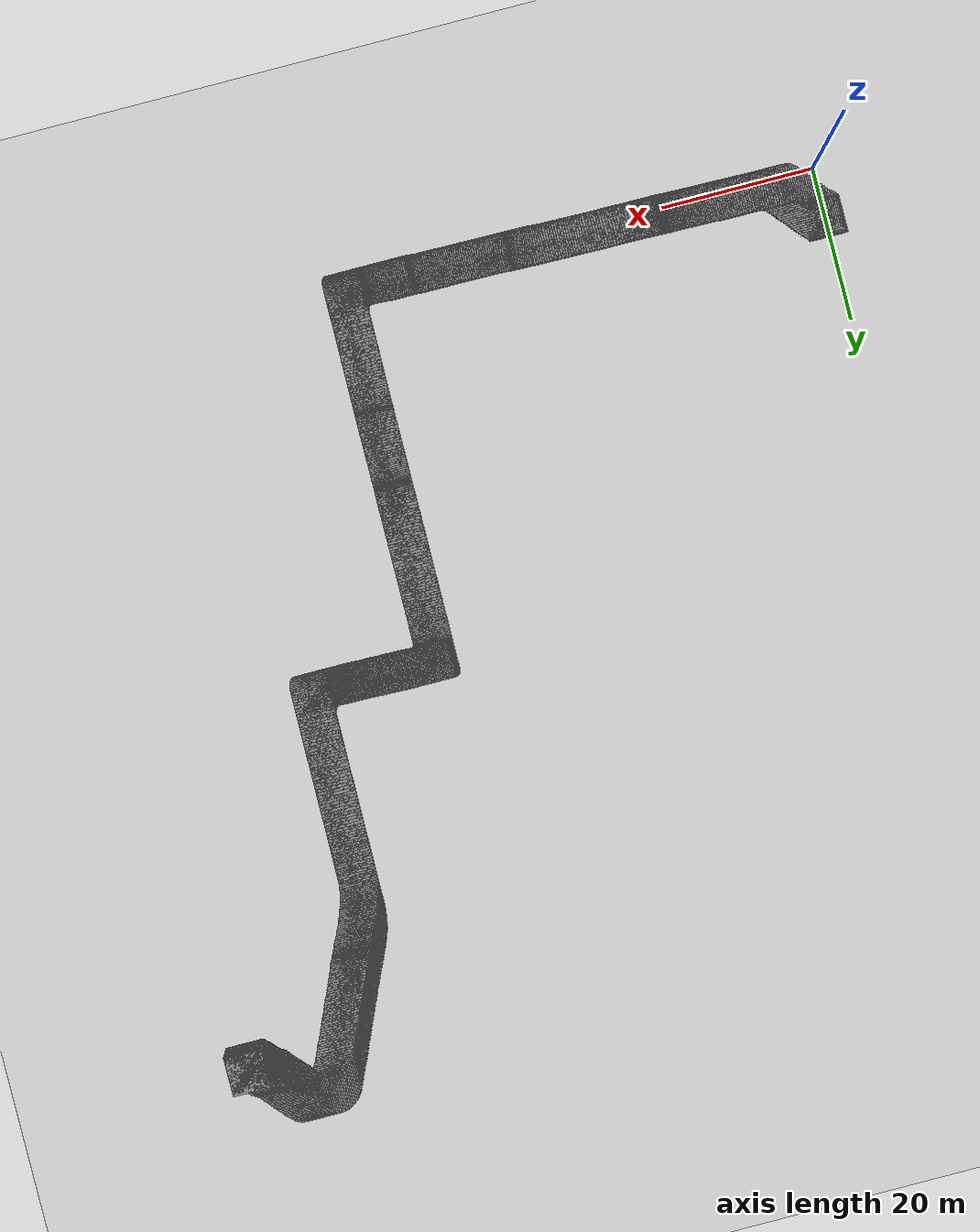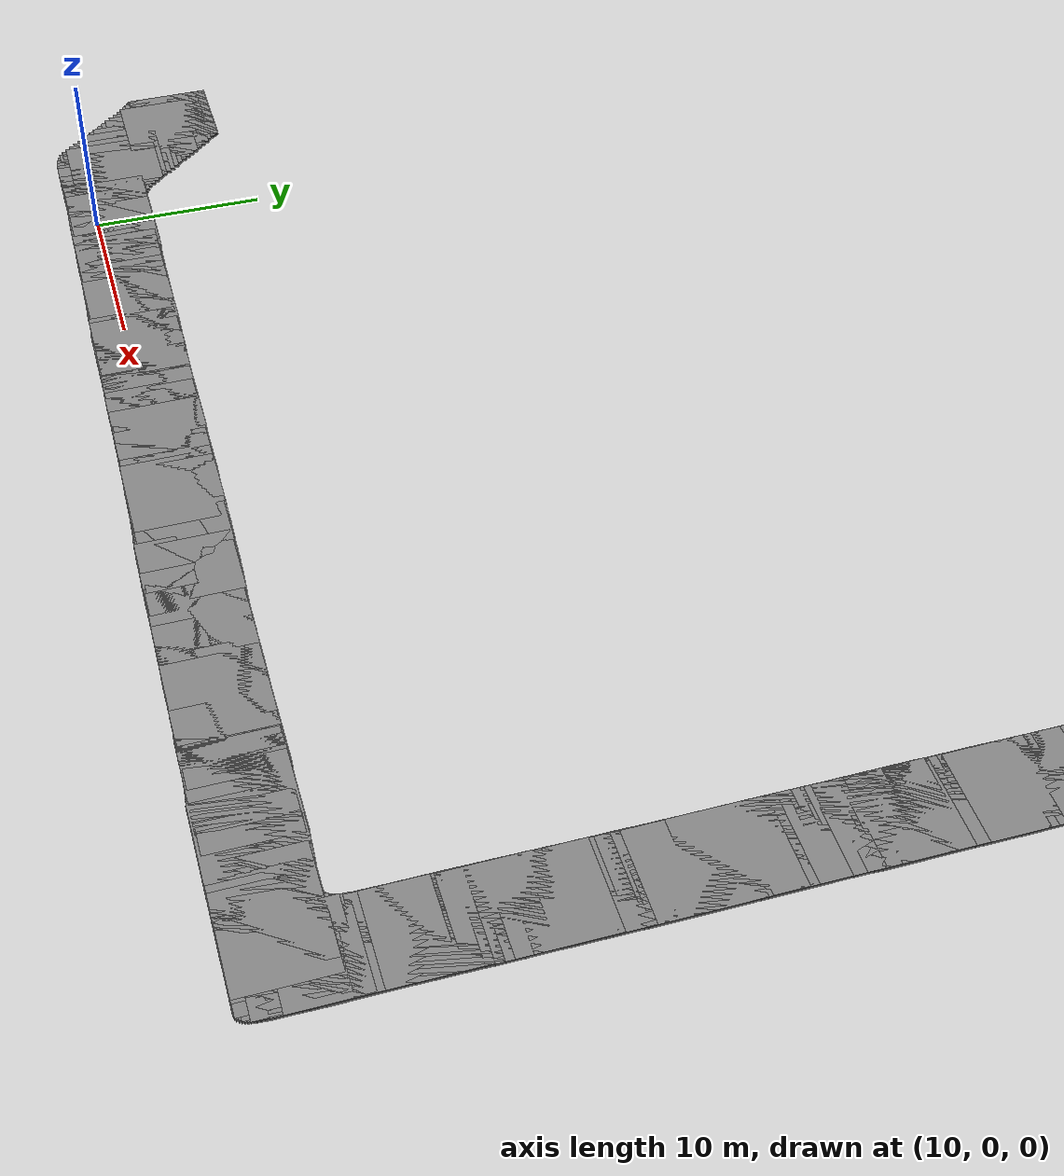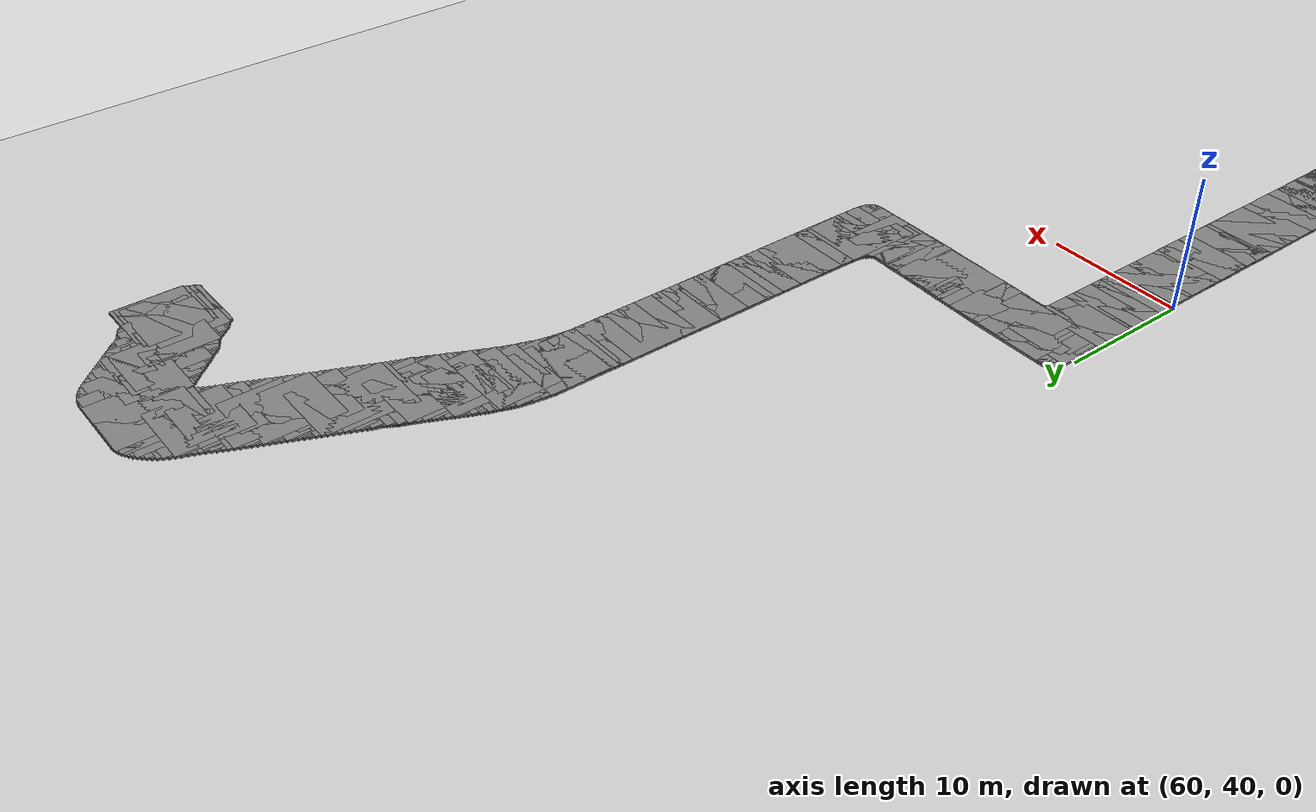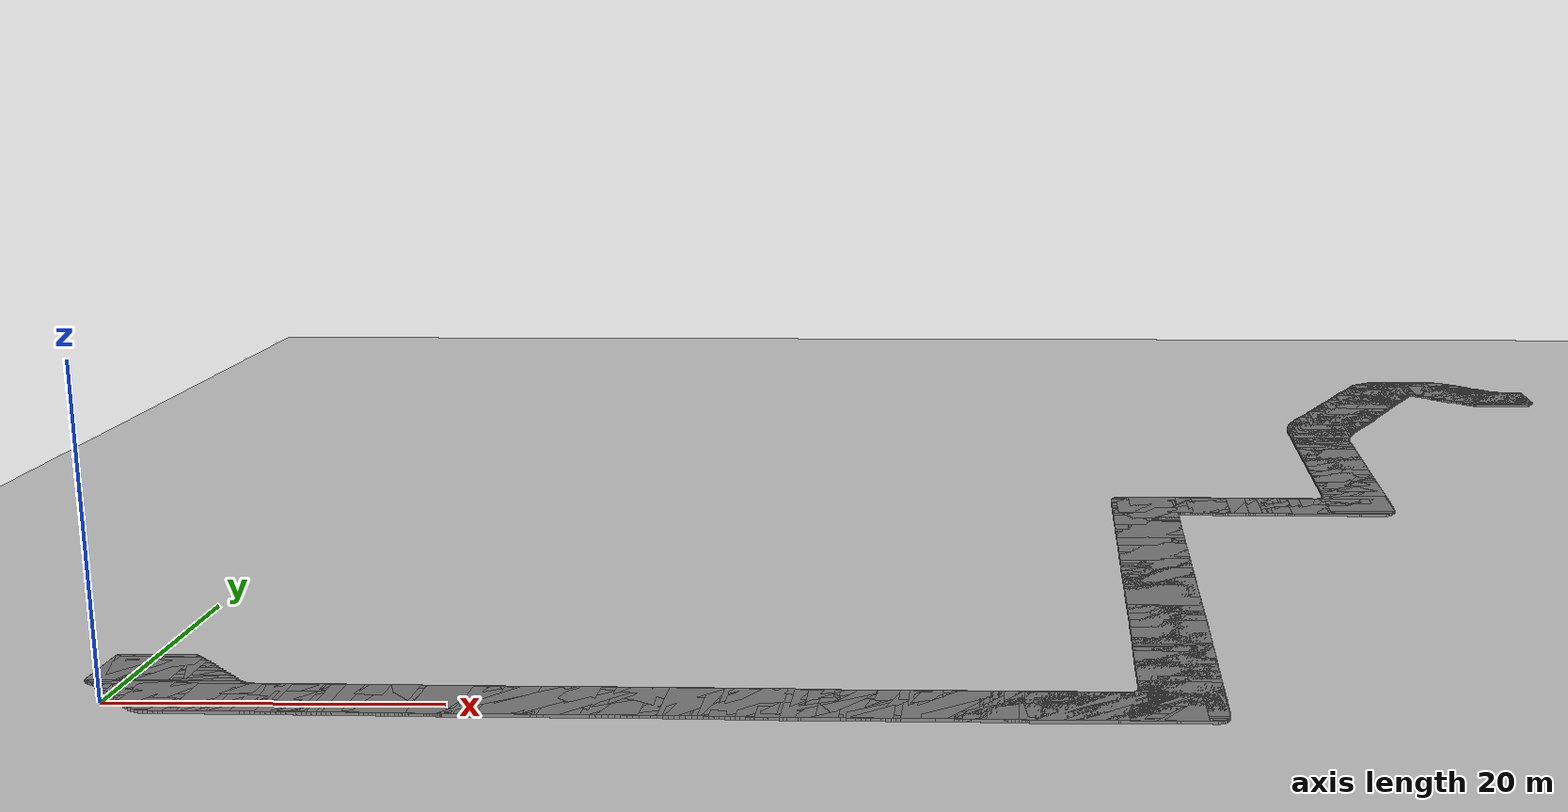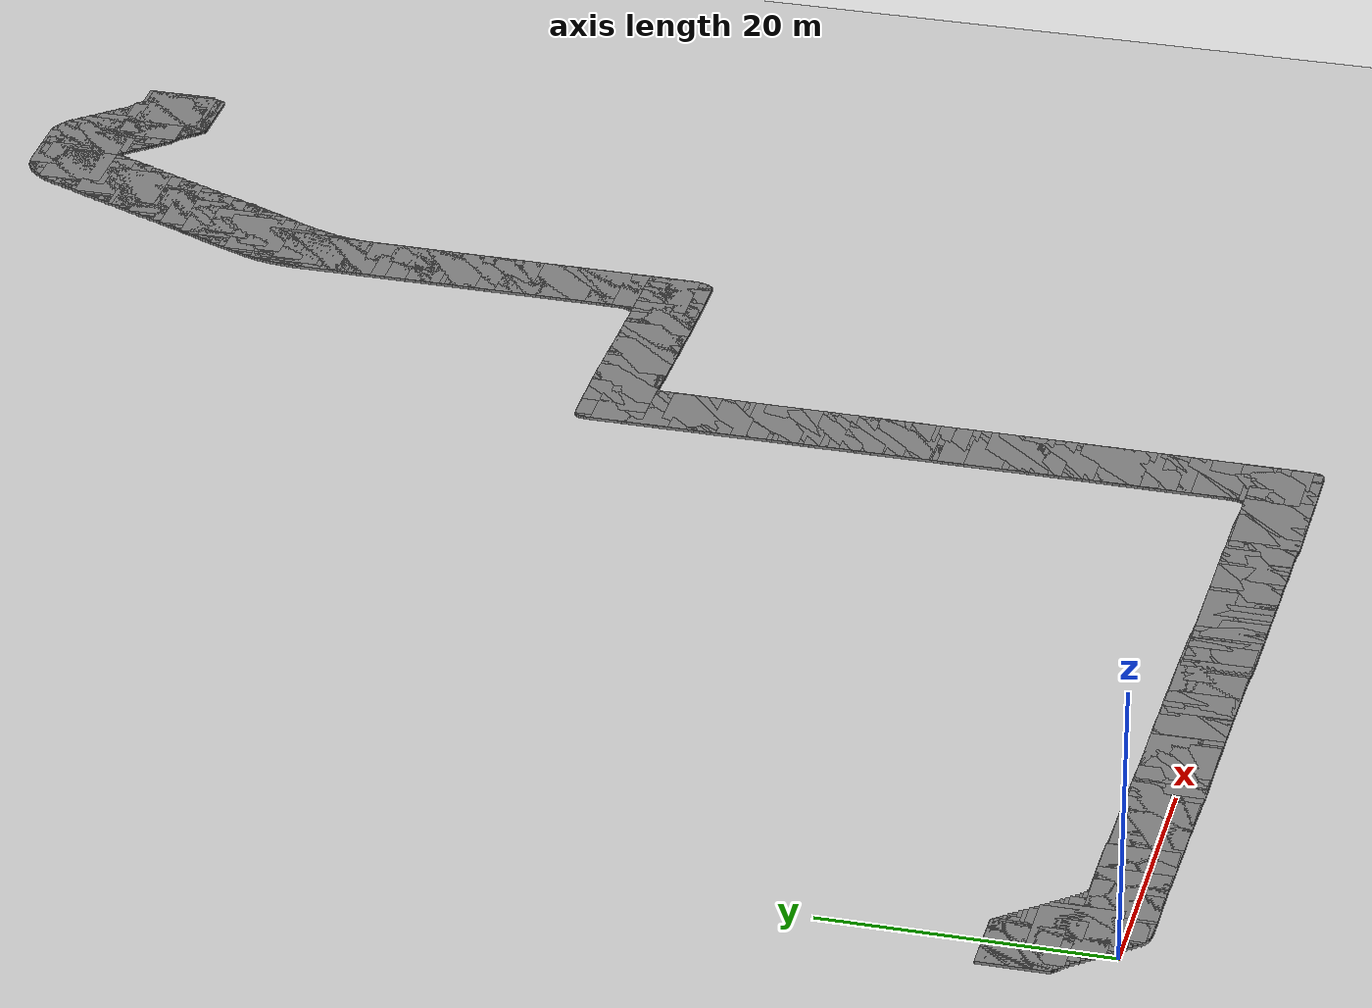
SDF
<?xml version="1.0"?>
<sdf version="1.6">
  <world name="default">
    <include>
      <uri>model://sun</uri>
    </include>
    <include>
      <uri>model://ground_plane</uri>
    </include>
    <!-- Define the path using connected boxes -->

    <model name="road_segment_0">
      <static>true</static>
      <link name="link">
        <visual name="visual">
          <geometry>
            <box>
              <size>5.0 5.0 0.2</size>
            </box>
          </geometry>
          <material>
            <ambient>0.5 0.5 0.5 1</ambient>
            <diffuse>0.5 0.5 0.5 1</diffuse>
          </material>
          <pose>100.0 94.5166298929436 0.0 0 0 0</pose>
        </visual>
        <collision name="collision">
          <geometry>
            <box>
              <size>5.0 5.0 0.2</size>
            </box>
          </geometry>
          <pose>100.0 94.5166298929436 0.0 0 0 0</pose>
        </collision>
      </link>
    </model>

    <model name="road_segment_1">
      <static>true</static>
      <link name="link">
        <visual name="visual">
          <geometry>
            <box>
              <size>5.0 5.0 0.2</size>
            </box>
          </geometry>
          <material>
            <ambient>0.5 0.5 0.5 1</ambient>
            <diffuse>0.5 0.5 0.5 1</diffuse>
          </material>
          <pose>99.99839161802979 94.30661109748615 0.0 0 0 0</pose>
        </visual>
        <collision name="collision">
          <geometry>
            <box>
              <size>5.0 5.0 0.2</size>
            </box>
          </geometry>
          <pose>99.99839161802979 94.30661109748615 0.0 0 0 0</pose>
        </collision>
      </link>
    </model>

    <model name="road_segment_2">
      <static>true</static>
      <link name="link">
        <visual name="visual">
          <geometry>
            <box>
              <size>5.0 5.0 0.2</size>
            </box>
          </geometry>
          <material>
            <ambient>0.5 0.5 0.5 1</ambient>
            <diffuse>0.5 0.5 0.5 1</diffuse>
          </material>
          <pose>99.97909103441992 94.25308490643219 0.0 0 0 0</pose>
        </visual>
        <collision name="collision">
          <geometry>
            <box>
              <size>5.0 5.0 0.2</size>
            </box>
          </geometry>
          <pose>99.97909103441992 94.25308490643219 0.0 0 0 0</pose>
        </collision>
      </link>
    </model>

    <model name="road_segment_3">
      <static>true</static>
      <link name="link">
        <visual name="visual">
          <geometry>
            <box>
              <size>5.0 5.0 0.2</size>
            </box>
          </geometry>
          <material>
            <ambient>0.5 0.5 0.5 1</ambient>
            <diffuse>0.5 0.5 0.5 1</diffuse>
          </material>
          <pose>99.96415605901025 94.24654735637526 0.0 0 0 0</pose>
        </visual>
        <collision name="collision">
          <geometry>
            <box>
              <size>5.0 5.0 0.2</size>
            </box>
          </geometry>
          <pose>99.96415605901025 94.24654735637526 0.0 0 0 0</pose>
        </collision>
      </link>
    </model>

    <model name="road_segment_4">
      <static>true</static>
      <link name="link">
        <visual name="visual">
          <geometry>
            <box>
              <size>5.0 5.0 0.2</size>
            </box>
          </geometry>
          <material>
            <ambient>0.5 0.5 0.5 1</ambient>
            <diffuse>0.5 0.5 0.5 1</diffuse>
          </material>
          <pose>99.95450576718899 94.24613875949943 0.0 0 0 0</pose>
        </visual>
        <collision name="collision">
          <geometry>
            <box>
              <size>5.0 5.0 0.2</size>
            </box>
          </geometry>
          <pose>99.95450576718899 94.24613875949943 0.0 0 0 0</pose>
        </collision>
      </link>
    </model>

    <model name="road_segment_5">
      <static>true</static>
      <link name="link">
        <visual name="visual">
          <geometry>
            <box>
              <size>5.0 5.0 0.2</size>
            </box>
          </geometry>
          <material>
            <ambient>0.5 0.5 0.5 1</ambient>
            <diffuse>0.5 0.5 0.5 1</diffuse>
          </material>
          <pose>99.94439593768995 94.25594508457758 0.0 0 0 0</pose>
        </visual>
        <collision name="collision">
          <geometry>
            <box>
              <size>5.0 5.0 0.2</size>
            </box>
          </geometry>
          <pose>99.94439593768995 94.25594508457758 0.0 0 0 0</pose>
        </collision>
      </link>
    </model>

    <model name="road_segment_6">
      <static>true</static>
      <link name="link">
        <visual name="visual">
          <geometry>
            <box>
              <size>5.0 5.0 0.2</size>
            </box>
          </geometry>
          <material>
            <ambient>0.5 0.5 0.5 1</ambient>
            <diffuse>0.5 0.5 0.5 1</diffuse>
          </material>
          <pose>99.93681356554934 94.25512789081864 0.0 0 0 0</pose>
        </visual>
        <collision name="collision">
          <geometry>
            <box>
              <size>5.0 5.0 0.2</size>
            </box>
          </geometry>
          <pose>99.93681356554934 94.25512789081864 0.0 0 0 0</pose>
        </collision>
      </link>
    </model>

    <model name="road_segment_7">
      <static>true</static>
      <link name="link">
        <visual name="visual">
          <geometry>
            <box>
              <size>5.0 5.0 0.2</size>
            </box>
          </geometry>
          <material>
            <ambient>0.5 0.5 0.5 1</ambient>
            <diffuse>0.5 0.5 0.5 1</diffuse>
          </material>
          <pose>99.9577225311294 94.2506333251554 0.0 0 0 0</pose>
        </visual>
        <collision name="collision">
          <geometry>
            <box>
              <size>5.0 5.0 0.2</size>
            </box>
          </geometry>
          <pose>99.9577225311294 94.2506333251554 0.0 0 0 0</pose>
        </collision>
      </link>
    </model>

    <model name="road_segment_8">
      <static>true</static>
      <link name="link">
        <visual name="visual">
          <geometry>
            <box>
              <size>5.0 5.0 0.2</size>
            </box>
          </geometry>
          <material>
            <ambient>0.5 0.5 0.5 1</ambient>
            <diffuse>0.5 0.5 0.5 1</diffuse>
          </material>
          <pose>99.95726299341896 94.2469559532511 0.0 0 0 0</pose>
        </visual>
        <collision name="collision">
          <geometry>
            <box>
              <size>5.0 5.0 0.2</size>
            </box>
          </geometry>
          <pose>99.95726299341896 94.2469559532511 0.0 0 0 0</pose>
        </collision>
      </link>
    </model>

    <model name="road_segment_9">
      <static>true</static>
      <link name="link">
        <visual name="visual">
          <geometry>
            <box>
              <size>5.0 5.0 0.2</size>
            </box>
          </geometry>
          <material>
            <ambient>0.5 0.5 0.5 1</ambient>
            <diffuse>0.5 0.5 0.5 1</diffuse>
          </material>
          <pose>99.95473553602788 94.24286998447096 0.0 0 0 0</pose>
        </visual>
        <collision name="collision">
          <geometry>
            <box>
              <size>5.0 5.0 0.2</size>
            </box>
          </geometry>
          <pose>99.95473553602788 94.24286998447096 0.0 0 0 0</pose>
        </collision>
      </link>
    </model>

    <model name="road_segment_10">
      <static>true</static>
      <link name="link">
        <visual name="visual">
          <geometry>
            <box>
              <size>5.0 5.0 0.2</size>
            </box>
          </geometry>
          <material>
            <ambient>0.5 0.5 0.5 1</ambient>
            <diffuse>0.5 0.5 0.5 1</diffuse>
          </material>
          <pose>99.94140894258841 94.25022472827956 0.0 0 0 0</pose>
        </visual>
        <collision name="collision">
          <geometry>
            <box>
              <size>5.0 5.0 0.2</size>
            </box>
          </geometry>
          <pose>99.94140894258841 94.25022472827956 0.0 0 0 0</pose>
        </collision>
      </link>
    </model>

    <model name="road_segment_11">
      <static>true</static>
      <link name="link">
        <visual name="visual">
          <geometry>
            <box>
              <size>5.0 5.0 0.2</size>
            </box>
          </geometry>
          <material>
            <ambient>0.5 0.5 0.5 1</ambient>
            <diffuse>0.5 0.5 0.5 1</diffuse>
          </material>
          <pose>99.93796240980912 94.24818174388588 0.0 0 0 0</pose>
        </visual>
        <collision name="collision">
          <geometry>
            <box>
              <size>5.0 5.0 0.2</size>
            </box>
          </geometry>
          <pose>99.93796240980912 94.24818174388588 0.0 0 0 0</pose>
        </collision>
      </link>
    </model>

    <model name="road_segment_12">
      <static>true</static>
      <link name="link">
        <visual name="visual">
          <geometry>
            <box>
              <size>5.0 5.0 0.2</size>
            </box>
          </geometry>
          <material>
            <ambient>0.5 0.5 0.5 1</ambient>
            <diffuse>0.5 0.5 0.5 1</diffuse>
          </material>
          <pose>99.936124259 94.24205279071202 0.0 0 0 0</pose>
        </visual>
        <collision name="collision">
          <geometry>
            <box>
              <size>5.0 5.0 0.2</size>
            </box>
          </geometry>
          <pose>99.936124259 94.24205279071202 0.0 0 0 0</pose>
        </collision>
      </link>
    </model>

    <model name="road_segment_13">
      <static>true</static>
      <link name="link">
        <visual name="visual">
          <geometry>
            <box>
              <size>5.0 5.0 0.2</size>
            </box>
          </geometry>
          <material>
            <ambient>0.5 0.5 0.5 1</ambient>
            <diffuse>0.5 0.5 0.5 1</diffuse>
          </material>
          <pose>99.93152888192827 94.23755822505605 0.0 0 0 0</pose>
        </visual>
        <collision name="collision">
          <geometry>
            <box>
              <size>5.0 5.0 0.2</size>
            </box>
          </geometry>
          <pose>99.93152888192827 94.23755822505605 0.0 0 0 0</pose>
        </collision>
      </link>
    </model>

    <model name="road_segment_14">
      <static>true</static>
      <link name="link">
        <visual name="visual">
          <geometry>
            <box>
              <size>5.0 5.0 0.2</size>
            </box>
          </geometry>
          <material>
            <ambient>0.5 0.5 0.5 1</ambient>
            <diffuse>0.5 0.5 0.5 1</diffuse>
          </material>
          <pose>99.92486558520854 94.22693470621898 0.0 0 0 0</pose>
        </visual>
        <collision name="collision">
          <geometry>
            <box>
              <size>5.0 5.0 0.2</size>
            </box>
          </geometry>
          <pose>99.92486558520854 94.22693470621898 0.0 0 0 0</pose>
        </collision>
      </link>
    </model>

    <model name="road_segment_15">
      <static>true</static>
      <link name="link">
        <visual name="visual">
          <geometry>
            <box>
              <size>5.0 5.0 0.2</size>
            </box>
          </geometry>
          <material>
            <ambient>0.5 0.5 0.5 1</ambient>
            <diffuse>0.5 0.5 0.5 1</diffuse>
          </material>
          <pose>99.92164882126812 94.22775189997064 0.0 0 0 0</pose>
        </visual>
        <collision name="collision">
          <geometry>
            <box>
              <size>5.0 5.0 0.2</size>
            </box>
          </geometry>
          <pose>99.92164882126812 94.22775189997064 0.0 0 0 0</pose>
        </collision>
      </link>
    </model>

    <model name="road_segment_16">
      <static>true</static>
      <link name="link">
        <visual name="visual">
          <geometry>
            <box>
              <size>5.0 5.0 0.2</size>
            </box>
          </geometry>
          <material>
            <ambient>0.5 0.5 0.5 1</ambient>
            <diffuse>0.5 0.5 0.5 1</diffuse>
          </material>
          <pose>99.91291760486773 94.21467679986404 0.0 0 0 0</pose>
        </visual>
        <collision name="collision">
          <geometry>
            <box>
              <size>5.0 5.0 0.2</size>
            </box>
          </geometry>
          <pose>99.91291760486773 94.21467679986404 0.0 0 0 0</pose>
        </collision>
      </link>
    </model>

    <model name="road_segment_17">
      <static>true</static>
      <link name="link">
        <visual name="visual">
          <geometry>
            <box>
              <size>5.0 5.0 0.2</size>
            </box>
          </geometry>
          <material>
            <ambient>0.5 0.5 0.5 1</ambient>
            <diffuse>0.5 0.5 0.5 1</diffuse>
          </material>
          <pose>99.8012499425372 94.04837787038967 0.0 0 0 0</pose>
        </visual>
        <collision name="collision">
          <geometry>
            <box>
              <size>5.0 5.0 0.2</size>
            </box>
          </geometry>
          <pose>99.8012499425372 94.04837787038967 0.0 0 0 0</pose>
        </collision>
      </link>
    </model>

    <model name="road_segment_18">
      <static>true</static>
      <link name="link">
        <visual name="visual">
          <geometry>
            <box>
              <size>5.0 5.0 0.2</size>
            </box>
          </geometry>
          <material>
            <ambient>0.5 0.5 0.5 1</ambient>
            <diffuse>0.5 0.5 0.5 1</diffuse>
          </material>
          <pose>99.75391755891708 93.93846531012187 0.0 0 0 0</pose>
        </visual>
        <collision name="collision">
          <geometry>
            <box>
              <size>5.0 5.0 0.2</size>
            </box>
          </geometry>
          <pose>99.75391755891708 93.93846531012187 0.0 0 0 0</pose>
        </collision>
      </link>
    </model>

    <model name="road_segment_19">
      <static>true</static>
      <link name="link">
        <visual name="visual">
          <geometry>
            <box>
              <size>5.0 5.0 0.2</size>
            </box>
          </geometry>
          <material>
            <ambient>0.5 0.5 0.5 1</ambient>
            <diffuse>0.5 0.5 0.5 1</diffuse>
          </material>
          <pose>99.74380772941804 93.90986352863912 0.0 0 0 0</pose>
        </visual>
        <collision name="collision">
          <geometry>
            <box>
              <size>5.0 5.0 0.2</size>
            </box>
          </geometry>
          <pose>99.74380772941804 93.90986352863912 0.0 0 0 0</pose>
        </collision>
      </link>
    </model>

    <model name="road_segment_20">
      <static>true</static>
      <link name="link">
        <visual name="visual">
          <geometry>
            <box>
              <size>5.0 5.0 0.2</size>
            </box>
          </geometry>
          <material>
            <ambient>0.5 0.5 0.5 1</ambient>
            <diffuse>0.5 0.5 0.5 1</diffuse>
          </material>
          <pose>99.74817333761823 93.9298847756785 0.0 0 0 0</pose>
        </visual>
        <collision name="collision">
          <geometry>
            <box>
              <size>5.0 5.0 0.2</size>
            </box>
          </geometry>
          <pose>99.74817333761823 93.9298847756785 0.0 0 0 0</pose>
        </collision>
      </link>
    </model>

    <model name="road_segment_21">
      <static>true</static>
      <link name="link">
        <visual name="visual">
          <geometry>
            <box>
              <size>5.0 5.0 0.2</size>
            </box>
          </geometry>
          <material>
            <ambient>0.5 0.5 0.5 1</ambient>
            <diffuse>0.5 0.5 0.5 1</diffuse>
          </material>
          <pose>99.75575570975884 93.94009969763249 0.0 0 0 0</pose>
        </visual>
        <collision name="collision">
          <geometry>
            <box>
              <size>5.0 5.0 0.2</size>
            </box>
          </geometry>
          <pose>99.75575570975884 93.94009969763249 0.0 0 0 0</pose>
        </collision>
      </link>
    </model>

    <model name="road_segment_22">
      <static>true</static>
      <link name="link">
        <visual name="visual">
          <geometry>
            <box>
              <size>5.0 5.0 0.2</size>
            </box>
          </geometry>
          <material>
            <ambient>0.5 0.5 0.5 1</ambient>
            <diffuse>0.5 0.5 0.5 1</diffuse>
          </material>
          <pose>99.75828316711728 93.9629811228245 0.0 0 0 0</pose>
        </visual>
        <collision name="collision">
          <geometry>
            <box>
              <size>5.0 5.0 0.2</size>
            </box>
          </geometry>
          <pose>99.75828316711728 93.9629811228245 0.0 0 0 0</pose>
        </collision>
      </link>
    </model>

    <model name="road_segment_23">
      <static>true</static>
      <link name="link">
        <visual name="visual">
          <geometry>
            <box>
              <size>5.0 5.0 0.2</size>
            </box>
          </geometry>
          <material>
            <ambient>0.5 0.5 0.5 1</ambient>
            <diffuse>0.5 0.5 0.5 1</diffuse>
          </material>
          <pose>99.76058085563682 93.96788428536357 0.0 0 0 0</pose>
        </visual>
        <collision name="collision">
          <geometry>
            <box>
              <size>5.0 5.0 0.2</size>
            </box>
          </geometry>
          <pose>99.76058085563682 93.96788428536357 0.0 0 0 0</pose>
        </collision>
      </link>
    </model>

    <model name="road_segment_24">
      <static>true</static>
      <link name="link">
        <visual name="visual">
          <geometry>
            <box>
              <size>5.0 5.0 0.2</size>
            </box>
          </geometry>
          <material>
            <ambient>0.5 0.5 0.5 1</ambient>
            <diffuse>0.5 0.5 0.5 1</diffuse>
          </material>
          <pose>99.76264877531746 93.96747568848048 0.0 0 0 0</pose>
        </visual>
        <collision name="collision">
          <geometry>
            <box>
              <size>5.0 5.0 0.2</size>
            </box>
          </geometry>
          <pose>99.76264877531746 93.96747568848048 0.0 0 0 0</pose>
        </collision>
      </link>
    </model>

    <model name="road_segment_25">
      <static>true</static>
      <link name="link">
        <visual name="visual">
          <geometry>
            <box>
              <size>5.0 5.0 0.2</size>
            </box>
          </geometry>
          <material>
            <ambient>0.5 0.5 0.5 1</ambient>
            <diffuse>0.5 0.5 0.5 1</diffuse>
          </material>
          <pose>99.76264877531746 93.96706709160463 0.0 0 0 0</pose>
        </visual>
        <collision name="collision">
          <geometry>
            <box>
              <size>5.0 5.0 0.2</size>
            </box>
          </geometry>
          <pose>99.76264877531746 93.96706709160463 0.0 0 0 0</pose>
        </collision>
      </link>
    </model>

    <model name="road_segment_26">
      <static>true</static>
      <link name="link">
        <visual name="visual">
          <geometry>
            <box>
              <size>5.0 5.0 0.2</size>
            </box>
          </geometry>
          <material>
            <ambient>0.5 0.5 0.5 1</ambient>
            <diffuse>0.5 0.5 0.5 1</diffuse>
          </material>
          <pose>99.76333808186679 93.97319604477848 0.0 0 0 0</pose>
        </visual>
        <collision name="collision">
          <geometry>
            <box>
              <size>5.0 5.0 0.2</size>
            </box>
          </geometry>
          <pose>99.76333808186679 93.97319604477848 0.0 0 0 0</pose>
        </collision>
      </link>
    </model>

    <model name="road_segment_27">
      <static>true</static>
      <link name="link">
        <visual name="visual">
          <geometry>
            <box>
              <size>5.0 5.0 0.2</size>
            </box>
          </geometry>
          <material>
            <ambient>0.5 0.5 0.5 1</ambient>
            <diffuse>0.5 0.5 0.5 1</diffuse>
          </material>
          <pose>99.76609530809678 93.9736046416543 0.0 0 0 0</pose>
        </visual>
        <collision name="collision">
          <geometry>
            <box>
              <size>5.0 5.0 0.2</size>
            </box>
          </geometry>
          <pose>99.76609530809678 93.9736046416543 0.0 0 0 0</pose>
        </collision>
      </link>
    </model>

    <model name="road_segment_28">
      <static>true</static>
      <link name="link">
        <visual name="visual">
          <geometry>
            <box>
              <size>5.0 5.0 0.2</size>
            </box>
          </geometry>
          <material>
            <ambient>0.5 0.5 0.5 1</ambient>
            <diffuse>0.5 0.5 0.5 1</diffuse>
          </material>
          <pose>99.76701438351766 93.97156165726787 0.0 0 0 0</pose>
        </visual>
        <collision name="collision">
          <geometry>
            <box>
              <size>5.0 5.0 0.2</size>
            </box>
          </geometry>
          <pose>99.76701438351766 93.97156165726787 0.0 0 0 0</pose>
        </collision>
      </link>
    </model>

    <model name="road_segment_29">
      <static>true</static>
      <link name="link">
        <visual name="visual">
          <geometry>
            <box>
              <size>5.0 5.0 0.2</size>
            </box>
          </geometry>
          <material>
            <ambient>0.5 0.5 0.5 1</ambient>
            <diffuse>0.5 0.5 0.5 1</diffuse>
          </material>
          <pose>99.76678461467876 93.96911007599833 0.0 0 0 0</pose>
        </visual>
        <collision name="collision">
          <geometry>
            <box>
              <size>5.0 5.0 0.2</size>
            </box>
          </geometry>
          <pose>99.76678461467876 93.96911007599833 0.0 0 0 0</pose>
        </collision>
      </link>
    </model>

    <model name="road_segment_30">
      <static>true</static>
      <link name="link">
        <visual name="visual">
          <geometry>
            <box>
              <size>5.0 5.0 0.2</size>
            </box>
          </geometry>
          <material>
            <ambient>0.5 0.5 0.5 1</ambient>
            <diffuse>0.5 0.5 0.5 1</diffuse>
          </material>
          <pose>99.767703690067 93.9719702541437 0.0 0 0 0</pose>
        </visual>
        <collision name="collision">
          <geometry>
            <box>
              <size>5.0 5.0 0.2</size>
            </box>
          </geometry>
          <pose>99.767703690067 93.9719702541437 0.0 0 0 0</pose>
        </collision>
      </link>
    </model>

    <model name="road_segment_31">
      <static>true</static>
      <link name="link">
        <visual name="visual">
          <geometry>
            <box>
              <size>5.0 5.0 0.2</size>
            </box>
          </geometry>
          <material>
            <ambient>0.5 0.5 0.5 1</ambient>
            <diffuse>0.5 0.5 0.5 1</diffuse>
          </material>
          <pose>99.67878314415827 93.7778867369455 0.0 0 0 0</pose>
        </visual>
        <collision name="collision">
          <geometry>
            <box>
              <size>5.0 5.0 0.2</size>
            </box>
          </geometry>
          <pose>99.67878314415827 93.7778867369455 0.0 0 0 0</pose>
        </collision>
      </link>
    </model>

    <model name="road_segment_32">
      <static>true</static>
      <link name="link">
        <visual name="visual">
          <geometry>
            <box>
              <size>5.0 5.0 0.2</size>
            </box>
          </geometry>
          <material>
            <ambient>0.5 0.5 0.5 1</ambient>
            <diffuse>0.5 0.5 0.5 1</diffuse>
          </material>
          <pose>99.63604613757725 93.66919996731248 0.0 0 0 0</pose>
        </visual>
        <collision name="collision">
          <geometry>
            <box>
              <size>5.0 5.0 0.2</size>
            </box>
          </geometry>
          <pose>99.63604613757725 93.66919996731248 0.0 0 0 0</pose>
        </collision>
      </link>
    </model>

    <model name="road_segment_33">
      <static>true</static>
      <link name="link">
        <visual name="visual">
          <geometry>
            <box>
              <size>5.0 5.0 0.2</size>
            </box>
          </geometry>
          <material>
            <ambient>0.5 0.5 0.5 1</ambient>
            <diffuse>0.5 0.5 0.5 1</diffuse>
          </material>
          <pose>99.6098524883761 93.62057693879035 0.0 0 0 0</pose>
        </visual>
        <collision name="collision">
          <geometry>
            <box>
              <size>5.0 5.0 0.2</size>
            </box>
          </geometry>
          <pose>99.6098524883761 93.62057693879035 0.0 0 0 0</pose>
        </collision>
      </link>
    </model>

    <model name="road_segment_34">
      <static>true</static>
      <link name="link">
        <visual name="visual">
          <geometry>
            <box>
              <size>5.0 5.0 0.2</size>
            </box>
          </geometry>
          <material>
            <ambient>0.5 0.5 0.5 1</ambient>
            <diffuse>0.5 0.5 0.5 1</diffuse>
          </material>
          <pose>99.58894352279603 93.5739968946619 0.0 0 0 0</pose>
        </visual>
        <collision name="collision">
          <geometry>
            <box>
              <size>5.0 5.0 0.2</size>
            </box>
          </geometry>
          <pose>99.58894352279603 93.5739968946619 0.0 0 0 0</pose>
        </collision>
      </link>
    </model>

    <model name="road_segment_35">
      <static>true</static>
      <link name="link">
        <visual name="visual">
          <geometry>
            <box>
              <size>5.0 5.0 0.2</size>
            </box>
          </geometry>
          <material>
            <ambient>0.5 0.5 0.5 1</ambient>
            <diffuse>0.5 0.5 0.5 1</diffuse>
          </material>
          <pose>99.55700565229604 93.50698700661825 0.0 0 0 0</pose>
        </visual>
        <collision name="collision">
          <geometry>
            <box>
              <size>5.0 5.0 0.2</size>
            </box>
          </geometry>
          <pose>99.55700565229604 93.50698700661825 0.0 0 0 0</pose>
        </collision>
      </link>
    </model>

    <model name="road_segment_36">
      <static>true</static>
      <link name="link">
        <visual name="visual">
          <geometry>
            <box>
              <size>5.0 5.0 0.2</size>
            </box>
          </geometry>
          <material>
            <ambient>0.5 0.5 0.5 1</ambient>
            <diffuse>0.5 0.5 0.5 1</diffuse>
          </material>
          <pose>99.49795505720667 93.40442919015906 0.0 0 0 0</pose>
        </visual>
        <collision name="collision">
          <geometry>
            <box>
              <size>5.0 5.0 0.2</size>
            </box>
          </geometry>
          <pose>99.49795505720667 93.40442919015906 0.0 0 0 0</pose>
        </collision>
      </link>
    </model>

    <model name="road_segment_37">
      <static>true</static>
      <link name="link">
        <visual name="visual">
          <geometry>
            <box>
              <size>5.0 5.0 0.2</size>
            </box>
          </geometry>
          <material>
            <ambient>0.5 0.5 0.5 1</ambient>
            <diffuse>0.5 0.5 0.5 1</diffuse>
          </material>
          <pose>99.45039290471502 93.33292473645217 0.0 0 0 0</pose>
        </visual>
        <collision name="collision">
          <geometry>
            <box>
              <size>5.0 5.0 0.2</size>
            </box>
          </geometry>
          <pose>99.45039290471502 93.33292473645217 0.0 0 0 0</pose>
        </collision>
      </link>
    </model>

    <model name="road_segment_38">
      <static>true</static>
      <link name="link">
        <visual name="visual">
          <geometry>
            <box>
              <size>5.0 5.0 0.2</size>
            </box>
          </geometry>
          <material>
            <ambient>0.5 0.5 0.5 1</ambient>
            <diffuse>0.5 0.5 0.5 1</diffuse>
          </material>
          <pose>99.40627728503533 93.27000081718866 0.0 0 0 0</pose>
        </visual>
        <collision name="collision">
          <geometry>
            <box>
              <size>5.0 5.0 0.2</size>
            </box>
          </geometry>
          <pose>99.40627728503533 93.27000081718866 0.0 0 0 0</pose>
        </collision>
      </link>
    </model>

    <model name="road_segment_39">
      <static>true</static>
      <link name="link">
        <visual name="visual">
          <geometry>
            <box>
              <size>5.0 5.0 0.2</size>
            </box>
          </geometry>
          <material>
            <ambient>0.5 0.5 0.5 1</ambient>
            <diffuse>0.5 0.5 0.5 1</diffuse>
          </material>
          <pose>99.36216166535563 93.22954972623407 0.0 0 0 0</pose>
        </visual>
        <collision name="collision">
          <geometry>
            <box>
              <size>5.0 5.0 0.2</size>
            </box>
          </geometry>
          <pose>99.36216166535563 93.22954972623407 0.0 0 0 0</pose>
        </collision>
      </link>
    </model>

    <model name="road_segment_40">
      <static>true</static>
      <link name="link">
        <visual name="visual">
          <geometry>
            <box>
              <size>5.0 5.0 0.2</size>
            </box>
          </geometry>
          <material>
            <ambient>0.5 0.5 0.5 1</ambient>
            <diffuse>0.5 0.5 0.5 1</diffuse>
          </material>
          <pose>99.30586829649624 93.27939854539096 0.0 0 0 0</pose>
        </visual>
        <collision name="collision">
          <geometry>
            <box>
              <size>5.0 5.0 0.2</size>
            </box>
          </geometry>
          <pose>99.30586829649624 93.27939854539096 0.0 0 0 0</pose>
        </collision>
      </link>
    </model>

    <model name="road_segment_41">
      <static>true</static>
      <link name="link">
        <visual name="visual">
          <geometry>
            <box>
              <size>5.0 5.0 0.2</size>
            </box>
          </geometry>
          <material>
            <ambient>0.5 0.5 0.5 1</ambient>
            <diffuse>0.5 0.5 0.5 1</diffuse>
          </material>
          <pose>99.21878590136399 93.36520388983924 0.0 0 0 0</pose>
        </visual>
        <collision name="collision">
          <geometry>
            <box>
              <size>5.0 5.0 0.2</size>
            </box>
          </geometry>
          <pose>99.21878590136399 93.36520388983924 0.0 0 0 0</pose>
        </collision>
      </link>
    </model>

    <model name="road_segment_42">
      <static>true</static>
      <link name="link">
        <visual name="visual">
          <geometry>
            <box>
              <size>5.0 5.0 0.2</size>
            </box>
          </geometry>
          <material>
            <ambient>0.5 0.5 0.5 1</ambient>
            <diffuse>0.5 0.5 0.5 1</diffuse>
          </material>
          <pose>99.13170350626437 93.49472910027058 0.0 0 0 0</pose>
        </visual>
        <collision name="collision">
          <geometry>
            <box>
              <size>5.0 5.0 0.2</size>
            </box>
          </geometry>
          <pose>99.13170350626437 93.49472910027058 0.0 0 0 0</pose>
        </collision>
      </link>
    </model>

    <model name="road_segment_43">
      <static>true</static>
      <link name="link">
        <visual name="visual">
          <geometry>
            <box>
              <size>5.0 5.0 0.2</size>
            </box>
          </geometry>
          <material>
            <ambient>0.5 0.5 0.5 1</ambient>
            <diffuse>0.5 0.5 0.5 1</diffuse>
          </material>
          <pose>99.01314277834256 93.58543760725065 0.0 0 0 0</pose>
        </visual>
        <collision name="collision">
          <geometry>
            <box>
              <size>5.0 5.0 0.2</size>
            </box>
          </geometry>
          <pose>99.01314277834256 93.58543760725065 0.0 0 0 0</pose>
        </collision>
      </link>
    </model>

    <model name="road_segment_44">
      <static>true</static>
      <link name="link">
        <visual name="visual">
          <geometry>
            <box>
              <size>5.0 5.0 0.2</size>
            </box>
          </geometry>
          <material>
            <ambient>0.5 0.5 0.5 1</ambient>
            <diffuse>0.5 0.5 0.5 1</diffuse>
          </material>
          <pose>98.89343320619362 93.6491787202731 0.0 0 0 0</pose>
        </visual>
        <collision name="collision">
          <geometry>
            <box>
              <size>5.0 5.0 0.2</size>
            </box>
          </geometry>
          <pose>98.89343320619362 93.6491787202731 0.0 0 0 0</pose>
        </collision>
      </link>
    </model>

    <model name="road_segment_45">
      <static>true</static>
      <link name="link">
        <visual name="visual">
          <geometry>
            <box>
              <size>5.0 5.0 0.2</size>
            </box>
          </geometry>
          <material>
            <ambient>0.5 0.5 0.5 1</ambient>
            <diffuse>0.5 0.5 0.5 1</diffuse>
          </material>
          <pose>98.77142594549248 93.75623110238827 0.0 0 0 0</pose>
        </visual>
        <collision name="collision">
          <geometry>
            <box>
              <size>5.0 5.0 0.2</size>
            </box>
          </geometry>
          <pose>98.77142594549248 93.75623110238827 0.0 0 0 0</pose>
        </collision>
      </link>
    </model>

    <model name="road_segment_46">
      <static>true</static>
      <link name="link">
        <visual name="visual">
          <geometry>
            <box>
              <size>5.0 5.0 0.2</size>
            </box>
          </geometry>
          <material>
            <ambient>0.5 0.5 0.5 1</ambient>
            <diffuse>0.5 0.5 0.5 1</diffuse>
          </material>
          <pose>98.6452828454627 93.88902508784807 0.0 0 0 0</pose>
        </visual>
        <collision name="collision">
          <geometry>
            <box>
              <size>5.0 5.0 0.2</size>
            </box>
          </geometry>
          <pose>98.6452828454627 93.88902508784807 0.0 0 0 0</pose>
        </collision>
      </link>
    </model>

    <model name="road_segment_47">
      <static>true</static>
      <link name="link">
        <visual name="visual">
          <geometry>
            <box>
              <size>5.0 5.0 0.2</size>
            </box>
          </geometry>
          <material>
            <ambient>0.5 0.5 0.5 1</ambient>
            <diffuse>0.5 0.5 0.5 1</diffuse>
          </material>
          <pose>98.51063829787144 94.03366838277245 0.0 0 0 0</pose>
        </visual>
        <collision name="collision">
          <geometry>
            <box>
              <size>5.0 5.0 0.2</size>
            </box>
          </geometry>
          <pose>98.51063829787144 94.03366838277245 0.0 0 0 0</pose>
        </collision>
      </link>
    </model>

    <model name="road_segment_48">
      <static>true</static>
      <link name="link">
        <visual name="visual">
          <geometry>
            <box>
              <size>5.0 5.0 0.2</size>
            </box>
          </geometry>
          <material>
            <ambient>0.5 0.5 0.5 1</ambient>
            <diffuse>0.5 0.5 0.5 1</diffuse>
          </material>
          <pose>98.37530444373084 94.19138677780346 0.0 0 0 0</pose>
        </visual>
        <collision name="collision">
          <geometry>
            <box>
              <size>5.0 5.0 0.2</size>
            </box>
          </geometry>
          <pose>98.37530444373084 94.19138677780346 0.0 0 0 0</pose>
        </collision>
      </link>
    </model>

    <model name="road_segment_49">
      <static>true</static>
      <link name="link">
        <visual name="visual">
          <geometry>
            <box>
              <size>5.0 5.0 0.2</size>
            </box>
          </geometry>
          <material>
            <ambient>0.5 0.5 0.5 1</ambient>
            <diffuse>0.5 0.5 0.5 1</diffuse>
          </material>
          <pose>98.23399659941984 94.34542780093015 0.0 0 0 0</pose>
        </visual>
        <collision name="collision">
          <geometry>
            <box>
              <size>5.0 5.0 0.2</size>
            </box>
          </geometry>
          <pose>98.23399659941984 94.34542780093015 0.0 0 0 0</pose>
        </collision>
      </link>
    </model>

    <model name="road_segment_50">
      <static>true</static>
      <link name="link">
        <visual name="visual">
          <geometry>
            <box>
              <size>5.0 5.0 0.2</size>
            </box>
          </geometry>
          <material>
            <ambient>0.5 0.5 0.5 1</ambient>
            <diffuse>0.5 0.5 0.5 1</diffuse>
          </material>
          <pose>98.09636505672705 94.50437198659591 0.0 0 0 0</pose>
        </visual>
        <collision name="collision">
          <geometry>
            <box>
              <size>5.0 5.0 0.2</size>
            </box>
          </geometry>
          <pose>98.09636505672705 94.50437198659591 0.0 0 0 0</pose>
        </collision>
      </link>
    </model>

    <model name="road_segment_51">
      <static>true</static>
      <link name="link">
        <visual name="visual">
          <geometry>
            <box>
              <size>5.0 5.0 0.2</size>
            </box>
          </geometry>
          <material>
            <ambient>0.5 0.5 0.5 1</ambient>
            <diffuse>0.5 0.5 0.5 1</diffuse>
          </material>
          <pose>97.95942282061624 94.65514423469415 0.0 0 0 0</pose>
        </visual>
        <collision name="collision">
          <geometry>
            <box>
              <size>5.0 5.0 0.2</size>
            </box>
          </geometry>
          <pose>97.95942282061624 94.65514423469415 0.0 0 0 0</pose>
        </collision>
      </link>
    </model>

    <model name="road_segment_52">
      <static>true</static>
      <link name="link">
        <visual name="visual">
          <geometry>
            <box>
              <size>5.0 5.0 0.2</size>
            </box>
          </geometry>
          <material>
            <ambient>0.5 0.5 0.5 1</ambient>
            <diffuse>0.5 0.5 0.5 1</diffuse>
          </material>
          <pose>97.8259271173174 94.80101332025329 0.0 0 0 0</pose>
        </visual>
        <collision name="collision">
          <geometry>
            <box>
              <size>5.0 5.0 0.2</size>
            </box>
          </geometry>
          <pose>97.8259271173174 94.80101332025329 0.0 0 0 0</pose>
        </collision>
      </link>
    </model>

    <model name="road_segment_53">
      <static>true</static>
      <link name="link">
        <visual name="visual">
          <geometry>
            <box>
              <size>5.0 5.0 0.2</size>
            </box>
          </geometry>
          <material>
            <ambient>0.5 0.5 0.5 1</ambient>
            <diffuse>0.5 0.5 0.5 1</diffuse>
          </material>
          <pose>97.69817563528476 94.92440957751079 0.0 0 0 0</pose>
        </visual>
        <collision name="collision">
          <geometry>
            <box>
              <size>5.0 5.0 0.2</size>
            </box>
          </geometry>
          <pose>97.69817563528476 94.92440957751079 0.0 0 0 0</pose>
        </collision>
      </link>
    </model>

    <model name="road_segment_54">
      <static>true</static>
      <link name="link">
        <visual name="visual">
          <geometry>
            <box>
              <size>5.0 5.0 0.2</size>
            </box>
          </geometry>
          <material>
            <ambient>0.5 0.5 0.5 1</ambient>
            <diffuse>0.5 0.5 0.5 1</diffuse>
          </material>
          <pose>97.56559900737413 95.0122579063455 0.0 0 0 0</pose>
        </visual>
        <collision name="collision">
          <geometry>
            <box>
              <size>5.0 5.0 0.2</size>
            </box>
          </geometry>
          <pose>97.56559900737413 95.0122579063455 0.0 0 0 0</pose>
        </collision>
      </link>
    </model>

    <model name="road_segment_55">
      <static>true</static>
      <link name="link">
        <visual name="visual">
          <geometry>
            <box>
              <size>5.0 5.0 0.2</size>
            </box>
          </geometry>
          <material>
            <ambient>0.5 0.5 0.5 1</ambient>
            <diffuse>0.5 0.5 0.5 1</diffuse>
          </material>
          <pose>97.42360185651381 95.07640761624378 0.0 0 0 0</pose>
        </visual>
        <collision name="collision">
          <geometry>
            <box>
              <size>5.0 5.0 0.2</size>
            </box>
          </geometry>
          <pose>97.42360185651381 95.07640761624378 0.0 0 0 0</pose>
        </collision>
      </link>
    </model>

    <model name="road_segment_56">
      <static>true</static>
      <link name="link">
        <visual name="visual">
          <geometry>
            <box>
              <size>5.0 5.0 0.2</size>
            </box>
          </geometry>
          <material>
            <ambient>0.5 0.5 0.5 1</ambient>
            <diffuse>0.5 0.5 0.5 1</diffuse>
          </material>
          <pose>97.27838794171306 95.15567541063513 0.0 0 0 0</pose>
        </visual>
        <collision name="collision">
          <geometry>
            <box>
              <size>5.0 5.0 0.2</size>
            </box>
          </geometry>
          <pose>97.27838794171306 95.15567541063513 0.0 0 0 0</pose>
        </collision>
      </link>
    </model>

    <model name="road_segment_57">
      <static>true</static>
      <link name="link">
        <visual name="visual">
          <geometry>
            <box>
              <size>5.0 5.0 0.2</size>
            </box>
          </geometry>
          <material>
            <ambient>0.5 0.5 0.5 1</ambient>
            <diffuse>0.5 0.5 0.5 1</diffuse>
          </material>
          <pose>97.13179541381365 95.24597532074662 0.0 0 0 0</pose>
        </visual>
        <collision name="collision">
          <geometry>
            <box>
              <size>5.0 5.0 0.2</size>
            </box>
          </geometry>
          <pose>97.13179541381365 95.24597532074662 0.0 0 0 0</pose>
        </collision>
      </link>
    </model>

    <model name="road_segment_58">
      <static>true</static>
      <link name="link">
        <visual name="visual">
          <geometry>
            <box>
              <size>5.0 5.0 0.2</size>
            </box>
          </geometry>
          <material>
            <ambient>0.5 0.5 0.5 1</ambient>
            <diffuse>0.5 0.5 0.5 1</diffuse>
          </material>
          <pose>96.9806075088425 95.3391354090035 0.0 0 0 0</pose>
        </visual>
        <collision name="collision">
          <geometry>
            <box>
              <size>5.0 5.0 0.2</size>
            </box>
          </geometry>
          <pose>96.9806075088425 95.3391354090035 0.0 0 0 0</pose>
        </collision>
      </link>
    </model>

    <model name="road_segment_59">
      <static>true</static>
      <link name="link">
        <visual name="visual">
          <geometry>
            <box>
              <size>5.0 5.0 0.2</size>
            </box>
          </geometry>
          <material>
            <ambient>0.5 0.5 0.5 1</ambient>
            <diffuse>0.5 0.5 0.5 1</diffuse>
          </material>
          <pose>96.83654243830152 95.46130587561898 0.0 0 0 0</pose>
        </visual>
        <collision name="collision">
          <geometry>
            <box>
              <size>5.0 5.0 0.2</size>
            </box>
          </geometry>
          <pose>96.83654243830152 95.46130587561898 0.0 0 0 0</pose>
        </collision>
      </link>
    </model>

    <model name="road_segment_60">
      <static>true</static>
      <link name="link">
        <visual name="visual">
          <geometry>
            <box>
              <size>5.0 5.0 0.2</size>
            </box>
          </geometry>
          <material>
            <ambient>0.5 0.5 0.5 1</ambient>
            <diffuse>0.5 0.5 0.5 1</diffuse>
          </material>
          <pose>96.6963834382503 95.6182070768983 0.0 0 0 0</pose>
        </visual>
        <collision name="collision">
          <geometry>
            <box>
              <size>5.0 5.0 0.2</size>
            </box>
          </geometry>
          <pose>96.6963834382503 95.6182070768983 0.0 0 0 0</pose>
        </collision>
      </link>
    </model>

    <model name="road_segment_61">
      <static>true</static>
      <link name="link">
        <visual name="visual">
          <geometry>
            <box>
              <size>5.0 5.0 0.2</size>
            </box>
          </geometry>
          <material>
            <ambient>0.5 0.5 0.5 1</ambient>
            <diffuse>0.5 0.5 0.5 1</diffuse>
          </material>
          <pose>96.55323744313019 95.78859197515281 0.0 0 0 0</pose>
        </visual>
        <collision name="collision">
          <geometry>
            <box>
              <size>5.0 5.0 0.2</size>
            </box>
          </geometry>
          <pose>96.55323744313019 95.78859197515281 0.0 0 0 0</pose>
        </collision>
      </link>
    </model>

    <model name="road_segment_62">
      <static>true</static>
      <link name="link">
        <visual name="visual">
          <geometry>
            <box>
              <size>5.0 5.0 0.2</size>
            </box>
          </geometry>
          <material>
            <ambient>0.5 0.5 0.5 1</ambient>
            <diffuse>0.5 0.5 0.5 1</diffuse>
          </material>
          <pose>96.40825329716833 95.95652529214505 0.0 0 0 0</pose>
        </visual>
        <collision name="collision">
          <geometry>
            <box>
              <size>5.0 5.0 0.2</size>
            </box>
          </geometry>
          <pose>96.40825329716833 95.95652529214505 0.0 0 0 0</pose>
        </collision>
      </link>
    </model>

    <model name="road_segment_63">
      <static>true</static>
      <link name="link">
        <visual name="visual">
          <geometry>
            <box>
              <size>5.0 5.0 0.2</size>
            </box>
          </geometry>
          <material>
            <ambient>0.5 0.5 0.5 1</ambient>
            <diffuse>0.5 0.5 0.5 1</diffuse>
          </material>
          <pose>96.2630393823676 96.12936177167636 0.0 0 0 0</pose>
        </visual>
        <collision name="collision">
          <geometry>
            <box>
              <size>5.0 5.0 0.2</size>
            </box>
          </geometry>
          <pose>96.2630393823676 96.12936177167636 0.0 0 0 0</pose>
        </collision>
      </link>
    </model>

    <model name="road_segment_64">
      <static>true</static>
      <link name="link">
        <visual name="visual">
          <geometry>
            <box>
              <size>5.0 5.0 0.2</size>
            </box>
          </geometry>
          <material>
            <ambient>0.5 0.5 0.5 1</ambient>
            <diffuse>0.5 0.5 0.5 1</diffuse>
          </material>
          <pose>96.11323009052775 96.28626297294842 0.0 0 0 0</pose>
        </visual>
        <collision name="collision">
          <geometry>
            <box>
              <size>5.0 5.0 0.2</size>
            </box>
          </geometry>
          <pose>96.11323009052775 96.28626297294842 0.0 0 0 0</pose>
        </collision>
      </link>
    </model>

    <model name="road_segment_65">
      <static>true</static>
      <link name="link">
        <visual name="visual">
          <geometry>
            <box>
              <size>5.0 5.0 0.2</size>
            </box>
          </geometry>
          <material>
            <ambient>0.5 0.5 0.5 1</ambient>
            <diffuse>0.5 0.5 0.5 1</diffuse>
          </material>
          <pose>95.96089334129682 96.44275557734466 0.0 0 0 0</pose>
        </visual>
        <collision name="collision">
          <geometry>
            <box>
              <size>5.0 5.0 0.2</size>
            </box>
          </geometry>
          <pose>95.96089334129682 96.44275557734466 0.0 0 0 0</pose>
        </collision>
      </link>
    </model>

    <model name="road_segment_66">
      <static>true</static>
      <link name="link">
        <visual name="visual">
          <geometry>
            <box>
              <size>5.0 5.0 0.2</size>
            </box>
          </geometry>
          <material>
            <ambient>0.5 0.5 0.5 1</ambient>
            <diffuse>0.5 0.5 0.5 1</diffuse>
          </material>
          <pose>95.81728780846629 96.60333415052102 0.0 0 0 0</pose>
        </visual>
        <collision name="collision">
          <geometry>
            <box>
              <size>5.0 5.0 0.2</size>
            </box>
          </geometry>
          <pose>95.81728780846629 96.60333415052102 0.0 0 0 0</pose>
        </collision>
      </link>
    </model>

    <model name="road_segment_67">
      <static>true</static>
      <link name="link">
        <visual name="visual">
          <geometry>
            <box>
              <size>5.0 5.0 0.2</size>
            </box>
          </geometry>
          <material>
            <ambient>0.5 0.5 0.5 1</ambient>
            <diffuse>0.5 0.5 0.5 1</diffuse>
          </material>
          <pose>95.6716143559551 96.77126746751325 0.0 0 0 0</pose>
        </visual>
        <collision name="collision">
          <geometry>
            <box>
              <size>5.0 5.0 0.2</size>
            </box>
          </geometry>
          <pose>95.6716143559551 96.77126746751325 0.0 0 0 0</pose>
        </collision>
      </link>
    </model>

    <model name="road_segment_68">
      <static>true</static>
      <link name="link">
        <visual name="visual">
          <geometry>
            <box>
              <size>5.0 5.0 0.2</size>
            </box>
          </geometry>
          <material>
            <ambient>0.5 0.5 0.5 1</ambient>
            <diffuse>0.5 0.5 0.5 1</diffuse>
          </material>
          <pose>95.52134552640483 96.94042657514026 0.0 0 0 0</pose>
        </visual>
        <collision name="collision">
          <geometry>
            <box>
              <size>5.0 5.0 0.2</size>
            </box>
          </geometry>
          <pose>95.52134552640483 96.94042657514026 0.0 0 0 0</pose>
        </collision>
      </link>
    </model>

    <model name="road_segment_69">
      <static>true</static>
      <link name="link">
        <visual name="visual">
          <geometry>
            <box>
              <size>5.0 5.0 0.2</size>
            </box>
          </geometry>
          <material>
            <ambient>0.5 0.5 0.5 1</ambient>
            <diffuse>0.5 0.5 0.5 1</diffuse>
          </material>
          <pose>95.36740039520369 97.11244586091264 0.0 0 0 0</pose>
        </visual>
        <collision name="collision">
          <geometry>
            <box>
              <size>5.0 5.0 0.2</size>
            </box>
          </geometry>
          <pose>95.36740039520369 97.11244586091264 0.0 0 0 0</pose>
        </collision>
      </link>
    </model>

    <model name="road_segment_70">
      <static>true</static>
      <link name="link">
        <visual name="visual">
          <geometry>
            <box>
              <size>5.0 5.0 0.2</size>
            </box>
          </geometry>
          <material>
            <ambient>0.5 0.5 0.5 1</ambient>
            <diffuse>0.5 0.5 0.5 1</diffuse>
          </material>
          <pose>95.21667202794298 97.29631445615686 0.0 0 0 0</pose>
        </visual>
        <collision name="collision">
          <geometry>
            <box>
              <size>5.0 5.0 0.2</size>
            </box>
          </geometry>
          <pose>95.21667202794298 97.29631445615686 0.0 0 0 0</pose>
        </collision>
      </link>
    </model>

    <model name="road_segment_71">
      <static>true</static>
      <link name="link">
        <visual name="visual">
          <geometry>
            <box>
              <size>5.0 5.0 0.2</size>
            </box>
          </geometry>
          <material>
            <ambient>0.5 0.5 0.5 1</ambient>
            <diffuse>0.5 0.5 0.5 1</diffuse>
          </material>
          <pose>95.06111851477165 97.48140884203585 0.0 0 0 0</pose>
        </visual>
        <collision name="collision">
          <geometry>
            <box>
              <size>5.0 5.0 0.2</size>
            </box>
          </geometry>
          <pose>95.06111851477165 97.48140884203585 0.0 0 0 0</pose>
        </collision>
      </link>
    </model>

    <model name="road_segment_72">
      <static>true</static>
      <link name="link">
        <visual name="visual">
          <geometry>
            <box>
              <size>5.0 5.0 0.2</size>
            </box>
          </geometry>
          <material>
            <ambient>0.5 0.5 0.5 1</ambient>
            <diffuse>0.5 0.5 0.5 1</diffuse>
          </material>
          <pose>94.90303754420923 97.6636430497622 0.0 0 0 0</pose>
        </visual>
        <collision name="collision">
          <geometry>
            <box>
              <size>5.0 5.0 0.2</size>
            </box>
          </geometry>
          <pose>94.90303754420923 97.6636430497622 0.0 0 0 0</pose>
        </collision>
      </link>
    </model>

    <model name="road_segment_73">
      <static>true</static>
      <link name="link">
        <visual name="visual">
          <geometry>
            <box>
              <size>5.0 5.0 0.2</size>
            </box>
          </geometry>
          <material>
            <ambient>0.5 0.5 0.5 1</ambient>
            <diffuse>0.5 0.5 0.5 1</diffuse>
          </material>
          <pose>94.7426588851599 97.83933970743888 0.0 0 0 0</pose>
        </visual>
        <collision name="collision">
          <geometry>
            <box>
              <size>5.0 5.0 0.2</size>
            </box>
          </geometry>
          <pose>94.7426588851599 97.83933970743888 0.0 0 0 0</pose>
        </collision>
      </link>
    </model>

    <model name="road_segment_74">
      <static>true</static>
      <link name="link">
        <visual name="visual">
          <geometry>
            <box>
              <size>5.0 5.0 0.2</size>
            </box>
          </geometry>
          <material>
            <ambient>0.5 0.5 0.5 1</ambient>
            <diffuse>0.5 0.5 0.5 1</diffuse>
          </material>
          <pose>94.57929323100906 98.01258478384602 0.0 0 0 0</pose>
        </visual>
        <collision name="collision">
          <geometry>
            <box>
              <size>5.0 5.0 0.2</size>
            </box>
          </geometry>
          <pose>94.57929323100906 98.01258478384602 0.0 0 0 0</pose>
        </collision>
      </link>
    </model>

    <model name="road_segment_75">
      <static>true</static>
      <link name="link">
        <visual name="visual">
          <geometry>
            <box>
              <size>5.0 5.0 0.2</size>
            </box>
          </geometry>
          <material>
            <ambient>0.5 0.5 0.5 1</ambient>
            <diffuse>0.5 0.5 0.5 1</diffuse>
          </material>
          <pose>94.41294058175669 98.18950723216473 0.0 0 0 0</pose>
        </visual>
        <collision name="collision">
          <geometry>
            <box>
              <size>5.0 5.0 0.2</size>
            </box>
          </geometry>
          <pose>94.41294058175669 98.18950723216473 0.0 0 0 0</pose>
        </collision>
      </link>
    </model>

    <model name="road_segment_76">
      <static>true</static>
      <link name="link">
        <visual name="visual">
          <geometry>
            <box>
              <size>5.0 5.0 0.2</size>
            </box>
          </geometry>
          <material>
            <ambient>0.5 0.5 0.5 1</ambient>
            <diffuse>0.5 0.5 0.5 1</diffuse>
          </material>
          <pose>94.24520931940566 98.37419302116062 0.0 0 0 0</pose>
        </visual>
        <collision name="collision">
          <geometry>
            <box>
              <size>5.0 5.0 0.2</size>
            </box>
          </geometry>
          <pose>94.24520931940566 98.37419302116062 0.0 0 0 0</pose>
        </collision>
      </link>
    </model>

    <model name="road_segment_77">
      <static>true</static>
      <link name="link">
        <visual name="visual">
          <geometry>
            <box>
              <size>5.0 5.0 0.2</size>
            </box>
          </geometry>
          <material>
            <ambient>0.5 0.5 0.5 1</ambient>
            <diffuse>0.5 0.5 0.5 1</diffuse>
          </material>
          <pose>94.07334221772598 98.56337337582701 0.0 0 0 0</pose>
        </visual>
        <collision name="collision">
          <geometry>
            <box>
              <size>5.0 5.0 0.2</size>
            </box>
          </geometry>
          <pose>94.07334221772598 98.56337337582701 0.0 0 0 0</pose>
        </collision>
      </link>
    </model>

    <model name="road_segment_78">
      <static>true</static>
      <link name="link">
        <visual name="visual">
          <geometry>
            <box>
              <size>5.0 5.0 0.2</size>
            </box>
          </geometry>
          <material>
            <ambient>0.5 0.5 0.5 1</ambient>
            <diffuse>0.5 0.5 0.5 1</diffuse>
          </material>
          <pose>93.89756904552388 98.75051074609243 0.0 0 0 0</pose>
        </visual>
        <collision name="collision">
          <geometry>
            <box>
              <size>5.0 5.0 0.2</size>
            </box>
          </geometry>
          <pose>93.89756904552388 98.75051074609243 0.0 0 0 0</pose>
        </collision>
      </link>
    </model>

    <model name="road_segment_79">
      <static>true</static>
      <link name="link">
        <visual name="visual">
          <geometry>
            <box>
              <size>5.0 5.0 0.2</size>
            </box>
          </geometry>
          <material>
            <ambient>0.5 0.5 0.5 1</ambient>
            <diffuse>0.5 0.5 0.5 1</diffuse>
          </material>
          <pose>93.72317448645313 98.93397074446082 0.0 0 0 0</pose>
        </visual>
        <collision name="collision">
          <geometry>
            <box>
              <size>5.0 5.0 0.2</size>
            </box>
          </geometry>
          <pose>93.72317448645313 98.93397074446082 0.0 0 0 0</pose>
        </collision>
      </link>
    </model>

    <model name="road_segment_80">
      <static>true</static>
      <link name="link">
        <visual name="visual">
          <geometry>
            <box>
              <size>5.0 5.0 0.2</size>
            </box>
          </geometry>
          <material>
            <ambient>0.5 0.5 0.5 1</ambient>
            <diffuse>0.5 0.5 0.5 1</diffuse>
          </material>
          <pose>93.54832038967193 99.1113017896481 0.0 0 0 0</pose>
        </visual>
        <collision name="collision">
          <geometry>
            <box>
              <size>5.0 5.0 0.2</size>
            </box>
          </geometry>
          <pose>93.54832038967193 99.1113017896481 0.0 0 0 0</pose>
        </collision>
      </link>
    </model>

    <model name="road_segment_81">
      <static>true</static>
      <link name="link">
        <visual name="visual">
          <geometry>
            <box>
              <size>5.0 5.0 0.2</size>
            </box>
          </geometry>
          <material>
            <ambient>0.5 0.5 0.5 1</ambient>
            <diffuse>0.5 0.5 0.5 1</diffuse>
          </material>
          <pose>93.36956022240096 99.27351475034234 0.0 0 0 0</pose>
        </visual>
        <collision name="collision">
          <geometry>
            <box>
              <size>5.0 5.0 0.2</size>
            </box>
          </geometry>
          <pose>93.36956022240096 99.27351475034234 0.0 0 0 0</pose>
        </collision>
      </link>
    </model>

    <model name="road_segment_82">
      <static>true</static>
      <link name="link">
        <visual name="visual">
          <geometry>
            <box>
              <size>5.0 5.0 0.2</size>
            </box>
          </geometry>
          <material>
            <ambient>0.5 0.5 0.5 1</ambient>
            <diffuse>0.5 0.5 0.5 1</diffuse>
          </material>
          <pose>93.18804282890002 99.42469559532366 0.0 0 0 0</pose>
        </visual>
        <collision name="collision">
          <geometry>
            <box>
              <size>5.0 5.0 0.2</size>
            </box>
          </geometry>
          <pose>93.18804282890002 99.42469559532366 0.0 0 0 0</pose>
        </collision>
      </link>
    </model>

    <model name="road_segment_83">
      <static>true</static>
      <link name="link">
        <visual name="visual">
          <geometry>
            <box>
              <size>5.0 5.0 0.2</size>
            </box>
          </geometry>
          <material>
            <ambient>0.5 0.5 0.5 1</ambient>
            <diffuse>0.5 0.5 0.5 1</diffuse>
          </material>
          <pose>93.00101098293912 99.56034975892157 0.0 0 0 0</pose>
        </visual>
        <collision name="collision">
          <geometry>
            <box>
              <size>5.0 5.0 0.2</size>
            </box>
          </geometry>
          <pose>93.00101098293912 99.56034975892157 0.0 0 0 0</pose>
        </collision>
      </link>
    </model>

    <model name="road_segment_84">
      <static>true</static>
      <link name="link">
        <visual name="visual">
          <geometry>
            <box>
              <size>5.0 5.0 0.2</size>
            </box>
          </geometry>
          <material>
            <ambient>0.5 0.5 0.5 1</ambient>
            <diffuse>0.5 0.5 0.5 1</diffuse>
          </material>
          <pose>92.80501815173896 99.67067091607245 0.0 0 0 0</pose>
        </visual>
        <collision name="collision">
          <geometry>
            <box>
              <size>5.0 5.0 0.2</size>
            </box>
          </geometry>
          <pose>92.80501815173896 99.67067091607245 0.0 0 0 0</pose>
        </collision>
      </link>
    </model>

    <model name="road_segment_85">
      <static>true</static>
      <link name="link">
        <visual name="visual">
          <geometry>
            <box>
              <size>5.0 5.0 0.2</size>
            </box>
          </geometry>
          <material>
            <ambient>0.5 0.5 0.5 1</ambient>
            <diffuse>0.5 0.5 0.5 1</diffuse>
          </material>
          <pose>92.6048894811775 99.77322873253165 0.0 0 0 0</pose>
        </visual>
        <collision name="collision">
          <geometry>
            <box>
              <size>5.0 5.0 0.2</size>
            </box>
          </geometry>
          <pose>92.6048894811775 99.77322873253165 0.0 0 0 0</pose>
        </collision>
      </link>
    </model>

    <model name="road_segment_86">
      <static>true</static>
      <link name="link">
        <visual name="visual">
          <geometry>
            <box>
              <size>5.0 5.0 0.2</size>
            </box>
          </geometry>
          <material>
            <ambient>0.5 0.5 0.5 1</ambient>
            <diffuse>0.5 0.5 0.5 1</diffuse>
          </material>
          <pose>92.39625936308718 99.86312004576006 0.0 0 0 0</pose>
        </visual>
        <collision name="collision">
          <geometry>
            <box>
              <size>5.0 5.0 0.2</size>
            </box>
          </geometry>
          <pose>92.39625936308718 99.86312004576006 0.0 0 0 0</pose>
        </collision>
      </link>
    </model>

    <model name="road_segment_87">
      <static>true</static>
      <link name="link">
        <visual name="visual">
          <geometry>
            <box>
              <size>5.0 5.0 0.2</size>
            </box>
          </geometry>
          <material>
            <ambient>0.5 0.5 0.5 1</ambient>
            <diffuse>0.5 0.5 0.5 1</diffuse>
          </material>
          <pose>92.18188502366537 99.9284955462931 0.0 0 0 0</pose>
        </visual>
        <collision name="collision">
          <geometry>
            <box>
              <size>5.0 5.0 0.2</size>
            </box>
          </geometry>
          <pose>92.18188502366537 99.9284955462931 0.0 0 0 0</pose>
        </collision>
      </link>
    </model>

    <model name="road_segment_88">
      <static>true</static>
      <link name="link">
        <visual name="visual">
          <geometry>
            <box>
              <size>5.0 5.0 0.2</size>
            </box>
          </geometry>
          <material>
            <ambient>0.5 0.5 0.5 1</ambient>
            <diffuse>0.5 0.5 0.5 1</diffuse>
          </material>
          <pose>91.96544276456291 99.97180681539308 0.0 0 0 0</pose>
        </visual>
        <collision name="collision">
          <geometry>
            <box>
              <size>5.0 5.0 0.2</size>
            </box>
          </geometry>
          <pose>91.96544276456291 99.97180681539308 0.0 0 0 0</pose>
        </collision>
      </link>
    </model>

    <model name="road_segment_89">
      <static>true</static>
      <link name="link">
        <visual name="visual">
          <geometry>
            <box>
              <size>5.0 5.0 0.2</size>
            </box>
          </geometry>
          <material>
            <ambient>0.5 0.5 0.5 1</ambient>
            <diffuse>0.5 0.5 0.5 1</diffuse>
          </material>
          <pose>91.74739212352289 99.99713982184737 0.0 0 0 0</pose>
        </visual>
        <collision name="collision">
          <geometry>
            <box>
              <size>5.0 5.0 0.2</size>
            </box>
          </geometry>
          <pose>91.74739212352289 99.99713982184737 0.0 0 0 0</pose>
        </collision>
      </link>
    </model>

    <model name="road_segment_90">
      <static>true</static>
      <link name="link">
        <visual name="visual">
          <geometry>
            <box>
              <size>5.0 5.0 0.2</size>
            </box>
          </geometry>
          <material>
            <ambient>0.5 0.5 0.5 1</ambient>
            <diffuse>0.5 0.5 0.5 1</diffuse>
          </material>
          <pose>91.52750333164111 100.0 0.0 0 0 0</pose>
        </visual>
        <collision name="collision">
          <geometry>
            <box>
              <size>5.0 5.0 0.2</size>
            </box>
          </geometry>
          <pose>91.52750333164111 100.0 0.0 0 0 0</pose>
        </collision>
      </link>
    </model>

    <model name="road_segment_91">
      <static>true</static>
      <link name="link">
        <visual name="visual">
          <geometry>
            <box>
              <size>5.0 5.0 0.2</size>
            </box>
          </geometry>
          <material>
            <ambient>0.5 0.5 0.5 1</ambient>
            <diffuse>0.5 0.5 0.5 1</diffuse>
          </material>
          <pose>91.30393823810849 99.98161314047123 0.0 0 0 0</pose>
        </visual>
        <collision name="collision">
          <geometry>
            <box>
              <size>5.0 5.0 0.2</size>
            </box>
          </geometry>
          <pose>91.30393823810849 99.98161314047123 0.0 0 0 0</pose>
        </collision>
      </link>
    </model>

    <model name="road_segment_92">
      <static>true</static>
      <link name="link">
        <visual name="visual">
          <geometry>
            <box>
              <size>5.0 5.0 0.2</size>
            </box>
          </geometry>
          <material>
            <ambient>0.5 0.5 0.5 1</ambient>
            <diffuse>0.5 0.5 0.5 1</diffuse>
          </material>
          <pose>91.07922430034874 99.94075345264079 0.0 0 0 0</pose>
        </visual>
        <collision name="collision">
          <geometry>
            <box>
              <size>5.0 5.0 0.2</size>
            </box>
          </geometry>
          <pose>91.07922430034874 99.94075345264079 0.0 0 0 0</pose>
        </collision>
      </link>
    </model>

    <model name="road_segment_93">
      <static>true</static>
      <link name="link">
        <visual name="visual">
          <geometry>
            <box>
              <size>5.0 5.0 0.2</size>
            </box>
          </geometry>
          <material>
            <ambient>0.5 0.5 0.5 1</ambient>
            <diffuse>0.5 0.5 0.5 1</diffuse>
          </material>
          <pose>90.85474013142787 99.8712919833276 0.0 0 0 0</pose>
        </visual>
        <collision name="collision">
          <geometry>
            <box>
              <size>5.0 5.0 0.2</size>
            </box>
          </geometry>
          <pose>90.85474013142787 99.8712919833276 0.0 0 0 0</pose>
        </collision>
      </link>
    </model>

    <model name="road_segment_94">
      <static>true</static>
      <link name="link">
        <visual name="visual">
          <geometry>
            <box>
              <size>5.0 5.0 0.2</size>
            </box>
          </geometry>
          <material>
            <ambient>0.5 0.5 0.5 1</ambient>
            <diffuse>0.5 0.5 0.5 1</diffuse>
          </material>
          <pose>90.63094526905635 99.76995995750318 0.0 0 0 0</pose>
        </visual>
        <collision name="collision">
          <geometry>
            <box>
              <size>5.0 5.0 0.2</size>
            </box>
          </geometry>
          <pose>90.63094526905635 99.76995995750318 0.0 0 0 0</pose>
        </collision>
      </link>
    </model>

    <model name="road_segment_95">
      <static>true</static>
      <link name="link">
        <visual name="visual">
          <geometry>
            <box>
              <size>5.0 5.0 0.2</size>
            </box>
          </geometry>
          <material>
            <ambient>0.5 0.5 0.5 1</ambient>
            <diffuse>0.5 0.5 0.5 1</diffuse>
          </material>
          <pose>90.41174578372392 99.64697229712878 0.0 0 0 0</pose>
        </visual>
        <collision name="collision">
          <geometry>
            <box>
              <size>5.0 5.0 0.2</size>
            </box>
          </geometry>
          <pose>90.41174578372392 99.64697229712878 0.0 0 0 0</pose>
        </collision>
      </link>
    </model>

    <model name="road_segment_96">
      <static>true</static>
      <link name="link">
        <visual name="visual">
          <geometry>
            <box>
              <size>5.0 5.0 0.2</size>
            </box>
          </geometry>
          <material>
            <ambient>0.5 0.5 0.5 1</ambient>
            <diffuse>0.5 0.5 0.5 1</diffuse>
          </material>
          <pose>90.19185699184214 99.50723216474347 0.0 0 0 0</pose>
        </visual>
        <collision name="collision">
          <geometry>
            <box>
              <size>5.0 5.0 0.2</size>
            </box>
          </geometry>
          <pose>90.19185699184214 99.50723216474347 0.0 0 0 0</pose>
        </collision>
      </link>
    </model>

    <model name="road_segment_97">
      <static>true</static>
      <link name="link">
        <visual name="visual">
          <geometry>
            <box>
              <size>5.0 5.0 0.2</size>
            </box>
          </geometry>
          <material>
            <ambient>0.5 0.5 0.5 1</ambient>
            <diffuse>0.5 0.5 0.5 1</diffuse>
          </material>
          <pose>89.97449565735145 99.35073956034724 0.0 0 0 0</pose>
        </visual>
        <collision name="collision">
          <geometry>
            <box>
              <size>5.0 5.0 0.2</size>
            </box>
          </geometry>
          <pose>89.97449565735145 99.35073956034724 0.0 0 0 0</pose>
        </collision>
      </link>
    </model>

    <model name="road_segment_98">
      <static>true</static>
      <link name="link">
        <visual name="visual">
          <geometry>
            <box>
              <size>5.0 5.0 0.2</size>
            </box>
          </geometry>
          <material>
            <ambient>0.5 0.5 0.5 1</ambient>
            <diffuse>0.5 0.5 0.5 1</diffuse>
          </material>
          <pose>89.76104039335053 99.17013974013148 0.0 0 0 0</pose>
        </visual>
        <collision name="collision">
          <geometry>
            <box>
              <size>5.0 5.0 0.2</size>
            </box>
          </geometry>
          <pose>89.76104039335053 99.17013974013148 0.0 0 0 0</pose>
        </collision>
      </link>
    </model>

    <model name="road_segment_99">
      <static>true</static>
      <link name="link">
        <visual name="visual">
          <geometry>
            <box>
              <size>5.0 5.0 0.2</size>
            </box>
          </geometry>
          <material>
            <ambient>0.5 0.5 0.5 1</ambient>
            <diffuse>0.5 0.5 0.5 1</diffuse>
          </material>
          <pose>89.5510316621289 98.96870147911741 0.0 0 0 0</pose>
        </visual>
        <collision name="collision">
          <geometry>
            <box>
              <size>5.0 5.0 0.2</size>
            </box>
          </geometry>
          <pose>89.5510316621289 98.96870147911741 0.0 0 0 0</pose>
        </collision>
      </link>
    </model>

    <model name="road_segment_100">
      <static>true</static>
      <link name="link">
        <visual name="visual">
          <geometry>
            <box>
              <size>5.0 5.0 0.2</size>
            </box>
          </geometry>
          <material>
            <ambient>0.5 0.5 0.5 1</ambient>
            <diffuse>0.5 0.5 0.5 1</diffuse>
          </material>
          <pose>89.34309085058793 98.75091934297554 0.0 0 0 0</pose>
        </visual>
        <collision name="collision">
          <geometry>
            <box>
              <size>5.0 5.0 0.2</size>
            </box>
          </geometry>
          <pose>89.34309085058793 98.75091934297554 0.0 0 0 0</pose>
        </collision>
      </link>
    </model>

    <model name="road_segment_101">
      <static>true</static>
      <link name="link">
        <visual name="visual">
          <geometry>
            <box>
              <size>5.0 5.0 0.2</size>
            </box>
          </geometry>
          <material>
            <ambient>0.5 0.5 0.5 1</ambient>
            <diffuse>0.5 0.5 0.5 1</diffuse>
          </material>
          <pose>89.14709801938776 98.51679333169857 0.0 0 0 0</pose>
        </visual>
        <collision name="collision">
          <geometry>
            <box>
              <size>5.0 5.0 0.2</size>
            </box>
          </geometry>
          <pose>89.14709801938776 98.51679333169857 0.0 0 0 0</pose>
        </collision>
      </link>
    </model>

    <model name="road_segment_102">
      <static>true</static>
      <link name="link">
        <visual name="visual">
          <geometry>
            <box>
              <size>5.0 5.0 0.2</size>
            </box>
          </geometry>
          <material>
            <ambient>0.5 0.5 0.5 1</ambient>
            <diffuse>0.5 0.5 0.5 1</diffuse>
          </material>
          <pose>88.95455172096689 98.26060308898853 0.0 0 0 0</pose>
        </visual>
        <collision name="collision">
          <geometry>
            <box>
              <size>5.0 5.0 0.2</size>
            </box>
          </geometry>
          <pose>88.95455172096689 98.26060308898853 0.0 0 0 0</pose>
        </collision>
      </link>
    </model>

    <model name="road_segment_103">
      <static>true</static>
      <link name="link">
        <visual name="visual">
          <geometry>
            <box>
              <size>5.0 5.0 0.2</size>
            </box>
          </geometry>
          <material>
            <ambient>0.5 0.5 0.5 1</ambient>
            <diffuse>0.5 0.5 0.5 1</diffuse>
          </material>
          <pose>88.77487247827506 97.97540246791989 0.0 0 0 0</pose>
        </visual>
        <collision name="collision">
          <geometry>
            <box>
              <size>5.0 5.0 0.2</size>
            </box>
          </geometry>
          <pose>88.77487247827506 97.97540246791989 0.0 0 0 0</pose>
        </collision>
      </link>
    </model>

    <model name="road_segment_104">
      <static>true</static>
      <link name="link">
        <visual name="visual">
          <geometry>
            <box>
              <size>5.0 5.0 0.2</size>
            </box>
          </geometry>
          <material>
            <ambient>0.5 0.5 0.5 1</ambient>
            <diffuse>0.5 0.5 0.5 1</diffuse>
          </material>
          <pose>88.61380451264375 97.66323445288636 0.0 0 0 0</pose>
        </visual>
        <collision name="collision">
          <geometry>
            <box>
              <size>5.0 5.0 0.2</size>
            </box>
          </geometry>
          <pose>88.61380451264375 97.66323445288636 0.0 0 0 0</pose>
        </collision>
      </link>
    </model>

    <model name="road_segment_105">
      <static>true</static>
      <link name="link">
        <visual name="visual">
          <geometry>
            <box>
              <size>5.0 5.0 0.2</size>
            </box>
          </geometry>
          <material>
            <ambient>0.5 0.5 0.5 1</ambient>
            <diffuse>0.5 0.5 0.5 1</diffuse>
          </material>
          <pose>88.46330591425459 97.33472256271776 0.0 0 0 0</pose>
        </visual>
        <collision name="collision">
          <geometry>
            <box>
              <size>5.0 5.0 0.2</size>
            </box>
          </geometry>
          <pose>88.46330591425459 97.33472256271776 0.0 0 0 0</pose>
        </collision>
      </link>
    </model>

    <model name="road_segment_106">
      <static>true</static>
      <link name="link">
        <visual name="visual">
          <geometry>
            <box>
              <size>5.0 5.0 0.2</size>
            </box>
          </geometry>
          <material>
            <ambient>0.5 0.5 0.5 1</ambient>
            <diffuse>0.5 0.5 0.5 1</diffuse>
          </material>
          <pose>88.31855153713163 97.0000817193753 0.0 0 0 0</pose>
        </visual>
        <collision name="collision">
          <geometry>
            <box>
              <size>5.0 5.0 0.2</size>
            </box>
          </geometry>
          <pose>88.31855153713163 97.0000817193753 0.0 0 0 0</pose>
        </collision>
      </link>
    </model>

    <model name="road_segment_107">
      <static>true</static>
      <link name="link">
        <visual name="visual">
          <geometry>
            <box>
              <size>5.0 5.0 0.2</size>
            </box>
          </geometry>
          <material>
            <ambient>0.5 0.5 0.5 1</ambient>
            <diffuse>0.5 0.5 0.5 1</diffuse>
          </material>
          <pose>88.18505583383278 96.66298929475607 0.0 0 0 0</pose>
        </visual>
        <collision name="collision">
          <geometry>
            <box>
              <size>5.0 5.0 0.2</size>
            </box>
          </geometry>
          <pose>88.18505583383278 96.66298929475607 0.0 0 0 0</pose>
        </collision>
      </link>
    </model>

    <model name="road_segment_108">
      <static>true</static>
      <link name="link">
        <visual name="visual">
          <geometry>
            <box>
              <size>5.0 5.0 0.2</size>
            </box>
          </geometry>
          <material>
            <ambient>0.5 0.5 0.5 1</ambient>
            <diffuse>0.5 0.5 0.5 1</diffuse>
          </material>
          <pose>88.05615550754038 96.33243442020103 0.0 0 0 0</pose>
        </visual>
        <collision name="collision">
          <geometry>
            <box>
              <size>5.0 5.0 0.2</size>
            </box>
          </geometry>
          <pose>88.05615550754038 96.33243442020103 0.0 0 0 0</pose>
        </collision>
      </link>
    </model>

    <model name="road_segment_109">
      <static>true</static>
      <link name="link">
        <visual name="visual">
          <geometry>
            <box>
              <size>5.0 5.0 0.2</size>
            </box>
          </geometry>
          <material>
            <ambient>0.5 0.5 0.5 1</ambient>
            <diffuse>0.5 0.5 0.5 1</diffuse>
          </material>
          <pose>87.92564679931041 96.02925553648672 0.0 0 0 0</pose>
        </visual>
        <collision name="collision">
          <geometry>
            <box>
              <size>5.0 5.0 0.2</size>
            </box>
          </geometry>
          <pose>87.92564679931041 96.02925553648672 0.0 0 0 0</pose>
        </collision>
      </link>
    </model>

    <model name="road_segment_110">
      <static>true</static>
      <link name="link">
        <visual name="visual">
          <geometry>
            <box>
              <size>5.0 5.0 0.2</size>
            </box>
          </geometry>
          <material>
            <ambient>0.5 0.5 0.5 1</ambient>
            <diffuse>0.5 0.5 0.5 1</diffuse>
          </material>
          <pose>87.7868664123905 95.72811963716609 0.0 0 0 0</pose>
        </visual>
        <collision name="collision">
          <geometry>
            <box>
              <size>5.0 5.0 0.2</size>
            </box>
          </geometry>
          <pose>87.7868664123905 95.72811963716609 0.0 0 0 0</pose>
        </collision>
      </link>
    </model>

    <model name="road_segment_111">
      <static>true</static>
      <link name="link">
        <visual name="visual">
          <geometry>
            <box>
              <size>5.0 5.0 0.2</size>
            </box>
          </geometry>
          <material>
            <ambient>0.5 0.5 0.5 1</ambient>
            <diffuse>0.5 0.5 0.5 1</diffuse>
          </material>
          <pose>87.64417995494817 95.42820952847299 0.0 0 0 0</pose>
        </visual>
        <collision name="collision">
          <geometry>
            <box>
              <size>5.0 5.0 0.2</size>
            </box>
          </geometry>
          <pose>87.64417995494817 95.42820952847299 0.0 0 0 0</pose>
        </collision>
      </link>
    </model>

    <model name="road_segment_112">
      <static>true</static>
      <link name="link">
        <visual name="visual">
          <geometry>
            <box>
              <size>5.0 5.0 0.2</size>
            </box>
          </geometry>
          <material>
            <ambient>0.5 0.5 0.5 1</ambient>
            <diffuse>0.5 0.5 0.5 1</diffuse>
          </material>
          <pose>87.49896604014744 95.124213451007 0.0 0 0 0</pose>
        </visual>
        <collision name="collision">
          <geometry>
            <box>
              <size>5.0 5.0 0.2</size>
            </box>
          </geometry>
          <pose>87.49896604014744 95.124213451007 0.0 0 0 0</pose>
        </collision>
      </link>
    </model>

    <model name="road_segment_113">
      <static>true</static>
      <link name="link">
        <visual name="visual">
          <geometry>
            <box>
              <size>5.0 5.0 0.2</size>
            </box>
          </geometry>
          <material>
            <ambient>0.5 0.5 0.5 1</ambient>
            <diffuse>0.5 0.5 0.5 1</diffuse>
          </material>
          <pose>87.3509948991167 94.82226035792745 0.0 0 0 0</pose>
        </visual>
        <collision name="collision">
          <geometry>
            <box>
              <size>5.0 5.0 0.2</size>
            </box>
          </geometry>
          <pose>87.3509948991167 94.82226035792745 0.0 0 0 0</pose>
        </collision>
      </link>
    </model>

    <model name="road_segment_114">
      <static>true</static>
      <link name="link">
        <visual name="visual">
          <geometry>
            <box>
              <size>5.0 5.0 0.2</size>
            </box>
          </geometry>
          <material>
            <ambient>0.5 0.5 0.5 1</ambient>
            <diffuse>0.5 0.5 0.5 1</diffuse>
          </material>
          <pose>87.20486190892773 94.52071586173099 0.0 0 0 0</pose>
        </visual>
        <collision name="collision">
          <geometry>
            <box>
              <size>5.0 5.0 0.2</size>
            </box>
          </geometry>
          <pose>87.20486190892773 94.52071586173099 0.0 0 0 0</pose>
        </collision>
      </link>
    </model>

    <model name="road_segment_115">
      <static>true</static>
      <link name="link">
        <visual name="visual">
          <geometry>
            <box>
              <size>5.0 5.0 0.2</size>
            </box>
          </geometry>
          <material>
            <ambient>0.5 0.5 0.5 1</ambient>
            <diffuse>0.5 0.5 0.5 1</diffuse>
          </material>
          <pose>87.06171591377498 94.20977363732497 0.0 0 0 0</pose>
        </visual>
        <collision name="collision">
          <geometry>
            <box>
              <size>5.0 5.0 0.2</size>
            </box>
          </geometry>
          <pose>87.06171591377498 94.20977363732497 0.0 0 0 0</pose>
        </collision>
      </link>
    </model>

    <model name="road_segment_116">
      <static>true</static>
      <link name="link">
        <visual name="visual">
          <geometry>
            <box>
              <size>5.0 5.0 0.2</size>
            </box>
          </geometry>
          <material>
            <ambient>0.5 0.5 0.5 1</ambient>
            <diffuse>0.5 0.5 0.5 1</diffuse>
          </material>
          <pose>86.92132714488486 93.89147666911761 0.0 0 0 0</pose>
        </visual>
        <collision name="collision">
          <geometry>
            <box>
              <size>5.0 5.0 0.2</size>
            </box>
          </geometry>
          <pose>86.92132714488486 93.89147666911761 0.0 0 0 0</pose>
        </collision>
      </link>
    </model>

    <model name="road_segment_117">
      <static>true</static>
      <link name="link">
        <visual name="visual">
          <geometry>
            <box>
              <size>5.0 5.0 0.2</size>
            </box>
          </geometry>
          <material>
            <ambient>0.5 0.5 0.5 1</ambient>
            <diffuse>0.5 0.5 0.5 1</diffuse>
          </material>
          <pose>86.78323606451427 93.57563128217251 0.0 0 0 0</pose>
        </visual>
        <collision name="collision">
          <geometry>
            <box>
              <size>5.0 5.0 0.2</size>
            </box>
          </geometry>
          <pose>86.78323606451427 93.57563128217251 0.0 0 0 0</pose>
        </collision>
      </link>
    </model>

    <model name="road_segment_118">
      <static>true</static>
      <link name="link">
        <visual name="visual">
          <geometry>
            <box>
              <size>5.0 5.0 0.2</size>
            </box>
          </geometry>
          <material>
            <ambient>0.5 0.5 0.5 1</ambient>
            <diffuse>0.5 0.5 0.5 1</diffuse>
          </material>
          <pose>86.64951059234389 93.25774291084097 0.0 0 0 0</pose>
        </visual>
        <collision name="collision">
          <geometry>
            <box>
              <size>5.0 5.0 0.2</size>
            </box>
          </geometry>
          <pose>86.64951059234389 93.25774291084097 0.0 0 0 0</pose>
        </collision>
      </link>
    </model>

    <model name="road_segment_119">
      <static>true</static>
      <link name="link">
        <visual name="visual">
          <geometry>
            <box>
              <size>5.0 5.0 0.2</size>
            </box>
          </geometry>
          <material>
            <ambient>0.5 0.5 0.5 1</ambient>
            <diffuse>0.5 0.5 0.5 1</diffuse>
          </material>
          <pose>86.51417673820329 92.93781155511574 0.0 0 0 0</pose>
        </visual>
        <collision name="collision">
          <geometry>
            <box>
              <size>5.0 5.0 0.2</size>
            </box>
          </geometry>
          <pose>86.51417673820329 92.93781155511574 0.0 0 0 0</pose>
        </collision>
      </link>
    </model>

    <model name="road_segment_120">
      <static>true</static>
      <link name="link">
        <visual name="visual">
          <geometry>
            <box>
              <size>5.0 5.0 0.2</size>
            </box>
          </geometry>
          <material>
            <ambient>0.5 0.5 0.5 1</ambient>
            <diffuse>0.5 0.5 0.5 1</diffuse>
          </material>
          <pose>86.37378796928051 92.62155757129482 0.0 0 0 0</pose>
        </visual>
        <collision name="collision">
          <geometry>
            <box>
              <size>5.0 5.0 0.2</size>
            </box>
          </geometry>
          <pose>86.37378796928051 92.62155757129482 0.0 0 0 0</pose>
        </collision>
      </link>
    </model>

    <model name="road_segment_121">
      <static>true</static>
      <link name="link">
        <visual name="visual">
          <geometry>
            <box>
              <size>5.0 5.0 0.2</size>
            </box>
          </geometry>
          <material>
            <ambient>0.5 0.5 0.5 1</ambient>
            <diffuse>0.5 0.5 0.5 1</diffuse>
          </material>
          <pose>86.23064197416042 92.30612078123282 0.0 0 0 0</pose>
        </visual>
        <collision name="collision">
          <geometry>
            <box>
              <size>5.0 5.0 0.2</size>
            </box>
          </geometry>
          <pose>86.23064197416042 92.30612078123282 0.0 0 0 0</pose>
        </collision>
      </link>
    </model>

    <model name="road_segment_122">
      <static>true</static>
      <link name="link">
        <visual name="visual">
          <geometry>
            <box>
              <size>5.0 5.0 0.2</size>
            </box>
          </geometry>
          <material>
            <ambient>0.5 0.5 0.5 1</ambient>
            <diffuse>0.5 0.5 0.5 1</diffuse>
          </material>
          <pose>86.08933412984942 91.99068399117083 0.0 0 0 0</pose>
        </visual>
        <collision name="collision">
          <geometry>
            <box>
              <size>5.0 5.0 0.2</size>
            </box>
          </geometry>
          <pose>86.08933412984942 91.99068399117083 0.0 0 0 0</pose>
        </collision>
      </link>
    </model>

    <model name="road_segment_123">
      <static>true</static>
      <link name="link">
        <visual name="visual">
          <geometry>
            <box>
              <size>5.0 5.0 0.2</size>
            </box>
          </geometry>
          <material>
            <ambient>0.5 0.5 0.5 1</ambient>
            <diffuse>0.5 0.5 0.5 1</diffuse>
          </material>
          <pose>85.95514911996858 91.66830105417606 0.0 0 0 0</pose>
        </visual>
        <collision name="collision">
          <geometry>
            <box>
              <size>5.0 5.0 0.2</size>
            </box>
          </geometry>
          <pose>85.95514911996858 91.66830105417606 0.0 0 0 0</pose>
        </collision>
      </link>
    </model>

    <model name="road_segment_124">
      <static>true</static>
      <link name="link">
        <visual name="visual">
          <geometry>
            <box>
              <size>5.0 5.0 0.2</size>
            </box>
          </geometry>
          <material>
            <ambient>0.5 0.5 0.5 1</ambient>
            <diffuse>0.5 0.5 0.5 1</diffuse>
          </material>
          <pose>85.82234272321908 91.34142355151806 0.0 0 0 0</pose>
        </visual>
        <collision name="collision">
          <geometry>
            <box>
              <size>5.0 5.0 0.2</size>
            </box>
          </geometry>
          <pose>85.82234272321908 91.34142355151806 0.0 0 0 0</pose>
        </collision>
      </link>
    </model>

    <model name="road_segment_125">
      <static>true</static>
      <link name="link">
        <visual name="visual">
          <geometry>
            <box>
              <size>5.0 5.0 0.2</size>
            </box>
          </geometry>
          <material>
            <ambient>0.5 0.5 0.5 1</ambient>
            <diffuse>0.5 0.5 0.5 1</diffuse>
          </material>
          <pose>85.68976609530846 91.026803955215 0.0 0 0 0</pose>
        </visual>
        <collision name="collision">
          <geometry>
            <box>
              <size>5.0 5.0 0.2</size>
            </box>
          </geometry>
          <pose>85.68976609530846 91.026803955215 0.0 0 0 0</pose>
        </collision>
      </link>
    </model>

    <model name="road_segment_126">
      <static>true</static>
      <link name="link">
        <visual name="visual">
          <geometry>
            <box>
              <size>5.0 5.0 0.2</size>
            </box>
          </geometry>
          <material>
            <ambient>0.5 0.5 0.5 1</ambient>
            <diffuse>0.5 0.5 0.5 1</diffuse>
          </material>
          <pose>85.55144524606634 90.71545313393314 0.0 0 0 0</pose>
        </visual>
        <collision name="collision">
          <geometry>
            <box>
              <size>5.0 5.0 0.2</size>
            </box>
          </geometry>
          <pose>85.55144524606634 90.71545313393314 0.0 0 0 0</pose>
        </collision>
      </link>
    </model>

    <model name="road_segment_127">
      <static>true</static>
      <link name="link">
        <visual name="visual">
          <geometry>
            <box>
              <size>5.0 5.0 0.2</size>
            </box>
          </geometry>
          <material>
            <ambient>0.5 0.5 0.5 1</ambient>
            <diffuse>0.5 0.5 0.5 1</diffuse>
          </material>
          <pose>85.40898855749558 90.40451090953438 0.0 0 0 0</pose>
        </visual>
        <collision name="collision">
          <geometry>
            <box>
              <size>5.0 5.0 0.2</size>
            </box>
          </geometry>
          <pose>85.40898855749558 90.40451090953438 0.0 0 0 0</pose>
        </collision>
      </link>
    </model>

    <model name="road_segment_128">
      <static>true</static>
      <link name="link">
        <visual name="visual">
          <geometry>
            <box>
              <size>5.0 5.0 0.2</size>
            </box>
          </geometry>
          <material>
            <ambient>0.5 0.5 0.5 1</ambient>
            <diffuse>0.5 0.5 0.5 1</diffuse>
          </material>
          <pose>85.2663021000859 90.08989131323132 0.0 0 0 0</pose>
        </visual>
        <collision name="collision">
          <geometry>
            <box>
              <size>5.0 5.0 0.2</size>
            </box>
          </geometry>
          <pose>85.2663021000859 90.08989131323132 0.0 0 0 0</pose>
        </collision>
      </link>
    </model>

    <model name="road_segment_129">
      <static>true</static>
      <link name="link">
        <visual name="visual">
          <geometry>
            <box>
              <size>5.0 5.0 0.2</size>
            </box>
          </geometry>
          <material>
            <ambient>0.5 0.5 0.5 1</ambient>
            <diffuse>0.5 0.5 0.5 1</diffuse>
          </material>
          <pose>85.12384541151513 89.77404592628623 0.0 0 0 0</pose>
        </visual>
        <collision name="collision">
          <geometry>
            <box>
              <size>5.0 5.0 0.2</size>
            </box>
          </geometry>
          <pose>85.12384541151513 89.77404592628623 0.0 0 0 0</pose>
        </collision>
      </link>
    </model>

    <model name="road_segment_130">
      <static>true</static>
      <link name="link">
        <visual name="visual">
          <geometry>
            <box>
              <size>5.0 5.0 0.2</size>
            </box>
          </geometry>
          <material>
            <ambient>0.5 0.5 0.5 1</ambient>
            <diffuse>0.5 0.5 0.5 1</diffuse>
          </material>
          <pose>84.98506502456257 89.45983492685899 0.0 0 0 0</pose>
        </visual>
        <collision name="collision">
          <geometry>
            <box>
              <size>5.0 5.0 0.2</size>
            </box>
          </geometry>
          <pose>84.98506502456257 89.45983492685899 0.0 0 0 0</pose>
        </collision>
      </link>
    </model>

    <model name="road_segment_131">
      <static>true</static>
      <link name="link">
        <visual name="visual">
          <geometry>
            <box>
              <size>5.0 5.0 0.2</size>
            </box>
          </geometry>
          <material>
            <ambient>0.5 0.5 0.5 1</ambient>
            <diffuse>0.5 0.5 0.5 1</diffuse>
          </material>
          <pose>84.84766325077398 89.14112936176853 0.0 0 0 0</pose>
        </visual>
        <collision name="collision">
          <geometry>
            <box>
              <size>5.0 5.0 0.2</size>
            </box>
          </geometry>
          <pose>84.84766325077398 89.14112936176853 0.0 0 0 0</pose>
        </collision>
      </link>
    </model>

    <model name="road_segment_132">
      <static>true</static>
      <link name="link">
        <visual name="visual">
          <geometry>
            <box>
              <size>5.0 5.0 0.2</size>
            </box>
          </geometry>
          <material>
            <ambient>0.5 0.5 0.5 1</ambient>
            <diffuse>0.5 0.5 0.5 1</diffuse>
          </material>
          <pose>84.70704471301231 88.81792923101483 0.0 0 0 0</pose>
        </visual>
        <collision name="collision">
          <geometry>
            <box>
              <size>5.0 5.0 0.2</size>
            </box>
          </geometry>
          <pose>84.70704471301231 88.81792923101483 0.0 0 0 0</pose>
        </collision>
      </link>
    </model>

    <model name="road_segment_133">
      <static>true</static>
      <link name="link">
        <visual name="visual">
          <geometry>
            <box>
              <size>5.0 5.0 0.2</size>
            </box>
          </geometry>
          <material>
            <ambient>0.5 0.5 0.5 1</ambient>
            <diffuse>0.5 0.5 0.5 1</diffuse>
          </material>
          <pose>84.56527733099087 88.49391190650945 0.0 0 0 0</pose>
        </visual>
        <collision name="collision">
          <geometry>
            <box>
              <size>5.0 5.0 0.2</size>
            </box>
          </geometry>
          <pose>84.56527733099087 88.49391190650945 0.0 0 0 0</pose>
        </collision>
      </link>
    </model>

    <model name="road_segment_134">
      <static>true</static>
      <link name="link">
        <visual name="visual">
          <geometry>
            <box>
              <size>5.0 5.0 0.2</size>
            </box>
          </geometry>
          <material>
            <ambient>0.5 0.5 0.5 1</ambient>
            <diffuse>0.5 0.5 0.5 1</diffuse>
          </material>
          <pose>84.42787555716963 88.17071177576302 0.0 0 0 0</pose>
        </visual>
        <collision name="collision">
          <geometry>
            <box>
              <size>5.0 5.0 0.2</size>
            </box>
          </geometry>
          <pose>84.42787555716963 88.17071177576302 0.0 0 0 0</pose>
        </collision>
      </link>
    </model>

    <model name="road_segment_135">
      <static>true</static>
      <link name="link">
        <visual name="visual">
          <geometry>
            <box>
              <size>5.0 5.0 0.2</size>
            </box>
          </geometry>
          <material>
            <ambient>0.5 0.5 0.5 1</ambient>
            <diffuse>0.5 0.5 0.5 1</diffuse>
          </material>
          <pose>84.2918523964797 87.85118901691362 0.0 0 0 0</pose>
        </visual>
        <collision name="collision">
          <geometry>
            <box>
              <size>5.0 5.0 0.2</size>
            </box>
          </geometry>
          <pose>84.2918523964797 87.85118901691362 0.0 0 0 0</pose>
        </collision>
      </link>
    </model>

    <model name="road_segment_136">
      <static>true</static>
      <link name="link">
        <visual name="visual">
          <geometry>
            <box>
              <size>5.0 5.0 0.2</size>
            </box>
          </geometry>
          <material>
            <ambient>0.5 0.5 0.5 1</ambient>
            <diffuse>0.5 0.5 0.5 1</diffuse>
          </material>
          <pose>84.15284224068824 87.5390210018801 0.0 0 0 0</pose>
        </visual>
        <collision name="collision">
          <geometry>
            <box>
              <size>5.0 5.0 0.2</size>
            </box>
          </geometry>
          <pose>84.15284224068824 87.5390210018801 0.0 0 0 0</pose>
        </collision>
      </link>
    </model>

    <model name="road_segment_137">
      <static>true</static>
      <link name="link">
        <visual name="visual">
          <geometry>
            <box>
              <size>5.0 5.0 0.2</size>
            </box>
          </geometry>
          <material>
            <ambient>0.5 0.5 0.5 1</ambient>
            <diffuse>0.5 0.5 0.5 1</diffuse>
          </material>
          <pose>84.01658931115942 87.23461632753101 0.0 0 0 0</pose>
        </visual>
        <collision name="collision">
          <geometry>
            <box>
              <size>5.0 5.0 0.2</size>
            </box>
          </geometry>
          <pose>84.01658931115942 87.23461632753101 0.0 0 0 0</pose>
        </collision>
      </link>
    </model>

    <model name="road_segment_138">
      <static>true</static>
      <link name="link">
        <visual name="visual">
          <geometry>
            <box>
              <size>5.0 5.0 0.2</size>
            </box>
          </geometry>
          <material>
            <ambient>0.5 0.5 0.5 1</ambient>
            <diffuse>0.5 0.5 0.5 1</diffuse>
          </material>
          <pose>83.88929736683721 86.94818991582761 0.0 0 0 0</pose>
        </visual>
        <collision name="collision">
          <geometry>
            <box>
              <size>5.0 5.0 0.2</size>
            </box>
          </geometry>
          <pose>83.88929736683721 86.94818991582761 0.0 0 0 0</pose>
        </collision>
      </link>
    </model>

    <model name="road_segment_139">
      <static>true</static>
      <link name="link">
        <visual name="visual">
          <geometry>
            <box>
              <size>5.0 5.0 0.2</size>
            </box>
          </geometry>
          <material>
            <ambient>0.5 0.5 0.5 1</ambient>
            <diffuse>0.5 0.5 0.5 1</diffuse>
          </material>
          <pose>83.77234502091827 86.68382773555729 0.0 0 0 0</pose>
        </visual>
        <collision name="collision">
          <geometry>
            <box>
              <size>5.0 5.0 0.2</size>
            </box>
          </geometry>
          <pose>83.77234502091827 86.68382773555729 0.0 0 0 0</pose>
        </collision>
      </link>
    </model>

    <model name="road_segment_140">
      <static>true</static>
      <link name="link">
        <visual name="visual">
          <geometry>
            <box>
              <size>5.0 5.0 0.2</size>
            </box>
          </geometry>
          <material>
            <ambient>0.5 0.5 0.5 1</ambient>
            <diffuse>0.5 0.5 0.5 1</diffuse>
          </material>
          <pose>83.68457331923666 86.4411211898297 0.0 0 0 0</pose>
        </visual>
        <collision name="collision">
          <geometry>
            <box>
              <size>5.0 5.0 0.2</size>
            </box>
          </geometry>
          <pose>83.68457331923666 86.4411211898297 0.0 0 0 0</pose>
        </collision>
      </link>
    </model>

    <model name="road_segment_141">
      <static>true</static>
      <link name="link">
        <visual name="visual">
          <geometry>
            <box>
              <size>5.0 5.0 0.2</size>
            </box>
          </geometry>
          <material>
            <ambient>0.5 0.5 0.5 1</ambient>
            <diffuse>0.5 0.5 0.5 1</diffuse>
          </material>
          <pose>83.63218602086702 86.23028520062059 0.0 0 0 0</pose>
        </visual>
        <collision name="collision">
          <geometry>
            <box>
              <size>5.0 5.0 0.2</size>
            </box>
          </geometry>
          <pose>83.63218602086702 86.23028520062059 0.0 0 0 0</pose>
        </collision>
      </link>
    </model>

    <model name="road_segment_142">
      <static>true</static>
      <link name="link">
        <visual name="visual">
          <geometry>
            <box>
              <size>5.0 5.0 0.2</size>
            </box>
          </geometry>
          <material>
            <ambient>0.5 0.5 0.5 1</ambient>
            <diffuse>0.5 0.5 0.5 1</diffuse>
          </material>
          <pose>83.58669178805602 86.07052382119589 0.0 0 0 0</pose>
        </visual>
        <collision name="collision">
          <geometry>
            <box>
              <size>5.0 5.0 0.2</size>
            </box>
          </geometry>
          <pose>83.58669178805602 86.07052382119589 0.0 0 0 0</pose>
        </collision>
      </link>
    </model>

    <model name="road_segment_143">
      <static>true</static>
      <link name="link">
        <visual name="visual">
          <geometry>
            <box>
              <size>5.0 5.0 0.2</size>
            </box>
          </geometry>
          <material>
            <ambient>0.5 0.5 0.5 1</ambient>
            <diffuse>0.5 0.5 0.5 1</diffuse>
          </material>
          <pose>83.52235650934558 85.94712756394564 0.0 0 0 0</pose>
        </visual>
        <collision name="collision">
          <geometry>
            <box>
              <size>5.0 5.0 0.2</size>
            </box>
          </geometry>
          <pose>83.52235650934558 85.94712756394564 0.0 0 0 0</pose>
        </collision>
      </link>
    </model>

    <model name="road_segment_144">
      <static>true</static>
      <link name="link">
        <visual name="visual">
          <geometry>
            <box>
              <size>5.0 5.0 0.2</size>
            </box>
          </geometry>
          <material>
            <ambient>0.5 0.5 0.5 1</ambient>
            <diffuse>0.5 0.5 0.5 1</diffuse>
          </material>
          <pose>83.44239694867615 85.82659148484078 0.0 0 0 0</pose>
        </visual>
        <collision name="collision">
          <geometry>
            <box>
              <size>5.0 5.0 0.2</size>
            </box>
          </geometry>
          <pose>83.44239694867615 85.82659148484078 0.0 0 0 0</pose>
        </collision>
      </link>
    </model>

    <model name="road_segment_145">
      <static>true</static>
      <link name="link">
        <visual name="visual">
          <geometry>
            <box>
              <size>5.0 5.0 0.2</size>
            </box>
          </geometry>
          <material>
            <ambient>0.5 0.5 0.5 1</ambient>
            <diffuse>0.5 0.5 0.5 1</diffuse>
          </material>
          <pose>83.35094894534369 85.67459344610052 0.0 0 0 0</pose>
        </visual>
        <collision name="collision">
          <geometry>
            <box>
              <size>5.0 5.0 0.2</size>
            </box>
          </geometry>
          <pose>83.35094894534369 85.67459344610052 0.0 0 0 0</pose>
        </collision>
      </link>
    </model>

    <model name="road_segment_146">
      <static>true</static>
      <link name="link">
        <visual name="visual">
          <geometry>
            <box>
              <size>5.0 5.0 0.2</size>
            </box>
          </geometry>
          <material>
            <ambient>0.5 0.5 0.5 1</ambient>
            <diffuse>0.5 0.5 0.5 1</diffuse>
          </material>
          <pose>83.26846192728317 85.51973522922216 0.0 0 0 0</pose>
        </visual>
        <collision name="collision">
          <geometry>
            <box>
              <size>5.0 5.0 0.2</size>
            </box>
          </geometry>
          <pose>83.26846192728317 85.51973522922216 0.0 0 0 0</pose>
        </collision>
      </link>
    </model>

    <model name="road_segment_147">
      <static>true</static>
      <link name="link">
        <visual name="visual">
          <geometry>
            <box>
              <size>5.0 5.0 0.2</size>
            </box>
          </geometry>
          <material>
            <ambient>0.5 0.5 0.5 1</ambient>
            <diffuse>0.5 0.5 0.5 1</diffuse>
          </material>
          <pose>83.20734341251315 85.40042494075206 0.0 0 0 0</pose>
        </visual>
        <collision name="collision">
          <geometry>
            <box>
              <size>5.0 5.0 0.2</size>
            </box>
          </geometry>
          <pose>83.20734341251315 85.40042494075206 0.0 0 0 0</pose>
        </collision>
      </link>
    </model>

    <model name="road_segment_148">
      <static>true</static>
      <link name="link">
        <visual name="visual">
          <geometry>
            <box>
              <size>5.0 5.0 0.2</size>
            </box>
          </geometry>
          <material>
            <ambient>0.5 0.5 0.5 1</ambient>
            <diffuse>0.5 0.5 0.5 1</diffuse>
          </material>
          <pose>83.17012085842475 85.32483451826502 0.0 0 0 0</pose>
        </visual>
        <collision name="collision">
          <geometry>
            <box>
              <size>5.0 5.0 0.2</size>
            </box>
          </geometry>
          <pose>83.17012085842475 85.32483451826502 0.0 0 0 0</pose>
        </collision>
      </link>
    </model>

    <model name="road_segment_149">
      <static>true</static>
      <link name="link">
        <visual name="visual">
          <geometry>
            <box>
              <size>5.0 5.0 0.2</size>
            </box>
          </geometry>
          <material>
            <ambient>0.5 0.5 0.5 1</ambient>
            <diffuse>0.5 0.5 0.5 1</diffuse>
          </material>
          <pose>83.15426680759418 85.27089973032072 0.0 0 0 0</pose>
        </visual>
        <collision name="collision">
          <geometry>
            <box>
              <size>5.0 5.0 0.2</size>
            </box>
          </geometry>
          <pose>83.15426680759418 85.27089973032072 0.0 0 0 0</pose>
        </collision>
      </link>
    </model>

    <model name="road_segment_150">
      <static>true</static>
      <link name="link">
        <visual name="visual">
          <geometry>
            <box>
              <size>5.0 5.0 0.2</size>
            </box>
          </geometry>
          <material>
            <ambient>0.5 0.5 0.5 1</ambient>
            <diffuse>0.5 0.5 0.5 1</diffuse>
          </material>
          <pose>83.14323790267427 85.23453460815352 0.0 0 0 0</pose>
        </visual>
        <collision name="collision">
          <geometry>
            <box>
              <size>5.0 5.0 0.2</size>
            </box>
          </geometry>
          <pose>83.14323790267427 85.23453460815352 0.0 0 0 0</pose>
        </collision>
      </link>
    </model>

    <model name="road_segment_151">
      <static>true</static>
      <link name="link">
        <visual name="visual">
          <geometry>
            <box>
              <size>5.0 5.0 0.2</size>
            </box>
          </geometry>
          <material>
            <ambient>0.5 0.5 0.5 1</ambient>
            <diffuse>0.5 0.5 0.5 1</diffuse>
          </material>
          <pose>83.12876246494238 85.2063414235466 0.0 0 0 0</pose>
        </visual>
        <collision name="collision">
          <geometry>
            <box>
              <size>5.0 5.0 0.2</size>
            </box>
          </geometry>
          <pose>83.12876246494238 85.2063414235466 0.0 0 0 0</pose>
        </collision>
      </link>
    </model>

    <model name="road_segment_152">
      <static>true</static>
      <link name="link">
        <visual name="visual">
          <geometry>
            <box>
              <size>5.0 5.0 0.2</size>
            </box>
          </geometry>
          <material>
            <ambient>0.5 0.5 0.5 1</ambient>
            <diffuse>0.5 0.5 0.5 1</diffuse>
          </material>
          <pose>83.10555581084277 85.17855683582279 0.0 0 0 0</pose>
        </visual>
        <collision name="collision">
          <geometry>
            <box>
              <size>5.0 5.0 0.2</size>
            </box>
          </geometry>
          <pose>83.10555581084277 85.17855683582279 0.0 0 0 0</pose>
        </collision>
      </link>
    </model>

    <model name="road_segment_153">
      <static>true</static>
      <link name="link">
        <visual name="visual">
          <geometry>
            <box>
              <size>5.0 5.0 0.2</size>
            </box>
          </geometry>
          <material>
            <ambient>0.5 0.5 0.5 1</ambient>
            <diffuse>0.5 0.5 0.5 1</diffuse>
          </material>
          <pose>83.07109048295167 85.11481572280759 0.0 0 0 0</pose>
        </visual>
        <collision name="collision">
          <geometry>
            <box>
              <size>5.0 5.0 0.2</size>
            </box>
          </geometry>
          <pose>83.07109048295167 85.11481572280759 0.0 0 0 0</pose>
        </collision>
      </link>
    </model>

    <model name="road_segment_154">
      <static>true</static>
      <link name="link">
        <visual name="visual">
          <geometry>
            <box>
              <size>5.0 5.0 0.2</size>
            </box>
          </geometry>
          <material>
            <ambient>0.5 0.5 0.5 1</ambient>
            <diffuse>0.5 0.5 0.5 1</diffuse>
          </material>
          <pose>83.02973208950198 85.01511808449378 0.0 0 0 0</pose>
        </visual>
        <collision name="collision">
          <geometry>
            <box>
              <size>5.0 5.0 0.2</size>
            </box>
          </geometry>
          <pose>83.02973208950198 85.01511808449378 0.0 0 0 0</pose>
        </collision>
      </link>
    </model>

    <model name="road_segment_155">
      <static>true</static>
      <link name="link">
        <visual name="visual">
          <geometry>
            <box>
              <size>5.0 5.0 0.2</size>
            </box>
          </geometry>
          <material>
            <ambient>0.5 0.5 0.5 1</ambient>
            <diffuse>0.5 0.5 0.5 1</diffuse>
          </material>
          <pose>82.97895317310255 84.894990602272 0.0 0 0 0</pose>
        </visual>
        <collision name="collision">
          <geometry>
            <box>
              <size>5.0 5.0 0.2</size>
            </box>
          </geometry>
          <pose>82.97895317310255 84.894990602272 0.0 0 0 0</pose>
        </collision>
      </link>
    </model>

    <model name="road_segment_156">
      <static>true</static>
      <link name="link">
        <visual name="visual">
          <geometry>
            <box>
              <size>5.0 5.0 0.2</size>
            </box>
          </geometry>
          <material>
            <ambient>0.5 0.5 0.5 1</ambient>
            <diffuse>0.5 0.5 0.5 1</diffuse>
          </material>
          <pose>82.9233491107925 84.76464819808899 0.0 0 0 0</pose>
        </visual>
        <collision name="collision">
          <geometry>
            <box>
              <size>5.0 5.0 0.2</size>
            </box>
          </geometry>
          <pose>82.9233491107925 84.76464819808899 0.0 0 0 0</pose>
        </collision>
      </link>
    </model>

    <model name="road_segment_157">
      <static>true</static>
      <link name="link">
        <visual name="visual">
          <geometry>
            <box>
              <size>5.0 5.0 0.2</size>
            </box>
          </geometry>
          <material>
            <ambient>0.5 0.5 0.5 1</ambient>
            <diffuse>0.5 0.5 0.5 1</diffuse>
          </material>
          <pose>82.86360920912115 84.62858543760798 0.0 0 0 0</pose>
        </visual>
        <collision name="collision">
          <geometry>
            <box>
              <size>5.0 5.0 0.2</size>
            </box>
          </geometry>
          <pose>82.86360920912115 84.62858543760798 0.0 0 0 0</pose>
        </collision>
      </link>
    </model>

    <model name="road_segment_158">
      <static>true</static>
      <link name="link">
        <visual name="visual">
          <geometry>
            <box>
              <size>5.0 5.0 0.2</size>
            </box>
          </geometry>
          <material>
            <ambient>0.5 0.5 0.5 1</ambient>
            <diffuse>0.5 0.5 0.5 1</diffuse>
          </material>
          <pose>82.7983548550225 84.49088828960912 0.0 0 0 0</pose>
        </visual>
        <collision name="collision">
          <geometry>
            <box>
              <size>5.0 5.0 0.2</size>
            </box>
          </geometry>
          <pose>82.7983548550225 84.49088828960912 0.0 0 0 0</pose>
        </collision>
      </link>
    </model>

    <model name="road_segment_159">
      <static>true</static>
      <link name="link">
        <visual name="visual">
          <geometry>
            <box>
              <size>5.0 5.0 0.2</size>
            </box>
          </geometry>
          <material>
            <ambient>0.5 0.5 0.5 1</ambient>
            <diffuse>0.5 0.5 0.5 1</diffuse>
          </material>
          <pose>82.7183952943204 84.33807305711719 0.0 0 0 0</pose>
        </visual>
        <collision name="collision">
          <geometry>
            <box>
              <size>5.0 5.0 0.2</size>
            </box>
          </geometry>
          <pose>82.7183952943204 84.33807305711719 0.0 0 0 0</pose>
        </collision>
      </link>
    </model>

    <model name="road_segment_160">
      <static>true</static>
      <link name="link">
        <visual name="visual">
          <geometry>
            <box>
              <size>5.0 5.0 0.2</size>
            </box>
          </geometry>
          <material>
            <ambient>0.5 0.5 0.5 1</ambient>
            <diffuse>0.5 0.5 0.5 1</diffuse>
          </material>
          <pose>82.63843573365097 84.1513442837276 0.0 0 0 0</pose>
        </visual>
        <collision name="collision">
          <geometry>
            <box>
              <size>5.0 5.0 0.2</size>
            </box>
          </geometry>
          <pose>82.63843573365097 84.1513442837276 0.0 0 0 0</pose>
        </collision>
      </link>
    </model>

    <model name="road_segment_161">
      <static>true</static>
      <link name="link">
        <visual name="visual">
          <geometry>
            <box>
              <size>5.0 5.0 0.2</size>
            </box>
          </geometry>
          <material>
            <ambient>0.5 0.5 0.5 1</ambient>
            <diffuse>0.5 0.5 0.5 1</diffuse>
          </material>
          <pose>82.55663802213977 83.93928250387646 0.0 0 0 0</pose>
        </visual>
        <collision name="collision">
          <geometry>
            <box>
              <size>5.0 5.0 0.2</size>
            </box>
          </geometry>
          <pose>82.55663802213977 83.93928250387646 0.0 0 0 0</pose>
        </collision>
      </link>
    </model>

    <model name="road_segment_162">
      <static>true</static>
      <link name="link">
        <visual name="visual">
          <geometry>
            <box>
              <size>5.0 5.0 0.2</size>
            </box>
          </geometry>
          <material>
            <ambient>0.5 0.5 0.5 1</ambient>
            <diffuse>0.5 0.5 0.5 1</diffuse>
          </material>
          <pose>82.46174348606064 83.72517773963888 0.0 0 0 0</pose>
        </visual>
        <collision name="collision">
          <geometry>
            <box>
              <size>5.0 5.0 0.2</size>
            </box>
          </geometry>
          <pose>82.46174348606064 83.72517773963888 0.0 0 0 0</pose>
        </collision>
      </link>
    </model>

    <model name="road_segment_163">
      <static>true</static>
      <link name="link">
        <visual name="visual">
          <geometry>
            <box>
              <size>5.0 5.0 0.2</size>
            </box>
          </geometry>
          <material>
            <ambient>0.5 0.5 0.5 1</ambient>
            <diffuse>0.5 0.5 0.5 1</diffuse>
          </material>
          <pose>82.35444143189765 83.50821279724866 0.0 0 0 0</pose>
        </visual>
        <collision name="collision">
          <geometry>
            <box>
              <size>5.0 5.0 0.2</size>
            </box>
          </geometry>
          <pose>82.35444143189765 83.50821279724866 0.0 0 0 0</pose>
        </collision>
      </link>
    </model>

    <model name="road_segment_164">
      <static>true</static>
      <link name="link">
        <visual name="visual">
          <geometry>
            <box>
              <size>5.0 5.0 0.2</size>
            </box>
          </geometry>
          <material>
            <ambient>0.5 0.5 0.5 1</ambient>
            <diffuse>0.5 0.5 0.5 1</diffuse>
          </material>
          <pose>82.240935618758 83.29043066110677 0.0 0 0 0</pose>
        </visual>
        <collision name="collision">
          <geometry>
            <box>
              <size>5.0 5.0 0.2</size>
            </box>
          </geometry>
          <pose>82.240935618758 83.29043066110677 0.0 0 0 0</pose>
        </collision>
      </link>
    </model>

    <model name="road_segment_165">
      <static>true</static>
      <link name="link">
        <visual name="visual">
          <geometry>
            <box>
              <size>5.0 5.0 0.2</size>
            </box>
          </geometry>
          <material>
            <ambient>0.5 0.5 0.5 1</ambient>
            <diffuse>0.5 0.5 0.5 1</diffuse>
          </material>
          <pose>82.1272000367468 83.05548745607089 0.0 0 0 0</pose>
        </visual>
        <collision name="collision">
          <geometry>
            <box>
              <size>5.0 5.0 0.2</size>
            </box>
          </geometry>
          <pose>82.1272000367468 83.05548745607089 0.0 0 0 0</pose>
        </collision>
      </link>
    </model>

    <model name="road_segment_166">
      <static>true</static>
      <link name="link">
        <visual name="visual">
          <geometry>
            <box>
              <size>5.0 5.0 0.2</size>
            </box>
          </geometry>
          <material>
            <ambient>0.5 0.5 0.5 1</ambient>
            <diffuse>0.5 0.5 0.5 1</diffuse>
          </material>
          <pose>82.01070722850564 82.80992073220517 0.0 0 0 0</pose>
        </visual>
        <collision name="collision">
          <geometry>
            <box>
              <size>5.0 5.0 0.2</size>
            </box>
          </geometry>
          <pose>82.01070722850564 82.80992073220517 0.0 0 0 0</pose>
        </collision>
      </link>
    </model>

    <model name="road_segment_167">
      <static>true</static>
      <link name="link">
        <visual name="visual">
          <geometry>
            <box>
              <size>5.0 5.0 0.2</size>
            </box>
          </geometry>
          <material>
            <ambient>0.5 0.5 0.5 1</ambient>
            <diffuse>0.5 0.5 0.5 1</diffuse>
          </material>
          <pose>81.89559303339578 82.55904224891731 0.0 0 0 0</pose>
        </visual>
        <collision name="collision">
          <geometry>
            <box>
              <size>5.0 5.0 0.2</size>
            </box>
          </geometry>
          <pose>81.89559303339578 82.55904224891731 0.0 0 0 0</pose>
        </collision>
      </link>
    </model>

    <model name="road_segment_168">
      <static>true</static>
      <link name="link">
        <visual name="visual">
          <geometry>
            <box>
              <size>5.0 5.0 0.2</size>
            </box>
          </geometry>
          <material>
            <ambient>0.5 0.5 0.5 1</ambient>
            <diffuse>0.5 0.5 0.5 1</diffuse>
          </material>
          <pose>81.7813979137068 82.31020675001587 0.0 0 0 0</pose>
        </visual>
        <collision name="collision">
          <geometry>
            <box>
              <size>5.0 5.0 0.2</size>
            </box>
          </geometry>
          <pose>81.7813979137068 82.31020675001587 0.0 0 0 0</pose>
        </collision>
      </link>
    </model>

    <model name="road_segment_169">
      <static>true</static>
      <link name="link">
        <visual name="visual">
          <geometry>
            <box>
              <size>5.0 5.0 0.2</size>
            </box>
          </geometry>
          <material>
            <ambient>0.5 0.5 0.5 1</ambient>
            <diffuse>0.5 0.5 0.5 1</diffuse>
          </material>
          <pose>81.6678921005345 82.06790880117137 0.0 0 0 0</pose>
        </visual>
        <collision name="collision">
          <geometry>
            <box>
              <size>5.0 5.0 0.2</size>
            </box>
          </geometry>
          <pose>81.6678921005345 82.06790880117137 0.0 0 0 0</pose>
        </collision>
      </link>
    </model>

    <model name="road_segment_170">
      <static>true</static>
      <link name="link">
        <visual name="visual">
          <geometry>
            <box>
              <size>5.0 5.0 0.2</size>
            </box>
          </geometry>
          <material>
            <ambient>0.5 0.5 0.5 1</ambient>
            <diffuse>0.5 0.5 0.5 1</diffuse>
          </material>
          <pose>81.55760305133528 81.8305140148732 0.0 0 0 0</pose>
        </visual>
        <collision name="collision">
          <geometry>
            <box>
              <size>5.0 5.0 0.2</size>
            </box>
          </geometry>
          <pose>81.55760305133528 81.8305140148732 0.0 0 0 0</pose>
        </collision>
      </link>
    </model>

    <model name="road_segment_171">
      <static>true</static>
      <link name="link">
        <visual name="visual">
          <geometry>
            <box>
              <size>5.0 5.0 0.2</size>
            </box>
          </geometry>
          <material>
            <ambient>0.5 0.5 0.5 1</ambient>
            <diffuse>0.5 0.5 0.5 1</diffuse>
          </material>
          <pose>81.44823307752428 81.59148484105717 0.0 0 0 0</pose>
        </visual>
        <collision name="collision">
          <geometry>
            <box>
              <size>5.0 5.0 0.2</size>
            </box>
          </geometry>
          <pose>81.44823307752428 81.59148484105717 0.0 0 0 0</pose>
        </collision>
      </link>
    </model>

    <model name="road_segment_172">
      <static>true</static>
      <link name="link">
        <visual name="visual">
          <geometry>
            <box>
              <size>5.0 5.0 0.2</size>
            </box>
          </geometry>
          <material>
            <ambient>0.5 0.5 0.5 1</ambient>
            <diffuse>0.5 0.5 0.5 1</diffuse>
          </material>
          <pose>81.3395524102626 81.34510092342526 0.0 0 0 0</pose>
        </visual>
        <collision name="collision">
          <geometry>
            <box>
              <size>5.0 5.0 0.2</size>
            </box>
          </geometry>
          <pose>81.3395524102626 81.34510092342526 0.0 0 0 0</pose>
        </collision>
      </link>
    </model>

    <model name="road_segment_173">
      <static>true</static>
      <link name="link">
        <visual name="visual">
          <geometry>
            <box>
              <size>5.0 5.0 0.2</size>
            </box>
          </geometry>
          <material>
            <ambient>0.5 0.5 0.5 1</ambient>
            <diffuse>0.5 0.5 0.5 1</diffuse>
          </material>
          <pose>81.23661596433244 81.10239437770494 0.0 0 0 0</pose>
        </visual>
        <collision name="collision">
          <geometry>
            <box>
              <size>5.0 5.0 0.2</size>
            </box>
          </geometry>
          <pose>81.23661596433244 81.10239437770494 0.0 0 0 0</pose>
        </collision>
      </link>
    </model>

    <model name="road_segment_174">
      <static>true</static>
      <link name="link">
        <visual name="visual">
          <geometry>
            <box>
              <size>5.0 5.0 0.2</size>
            </box>
          </geometry>
          <material>
            <ambient>0.5 0.5 0.5 1</ambient>
            <diffuse>0.5 0.5 0.5 1</diffuse>
          </material>
          <pose>81.13666651347116 80.8654081882826 0.0 0 0 0</pose>
        </visual>
        <collision name="collision">
          <geometry>
            <box>
              <size>5.0 5.0 0.2</size>
            </box>
          </geometry>
          <pose>81.13666651347116 80.8654081882826 0.0 0 0 0</pose>
        </collision>
      </link>
    </model>

    <model name="road_segment_175">
      <static>true</static>
      <link name="link">
        <visual name="visual">
          <geometry>
            <box>
              <size>5.0 5.0 0.2</size>
            </box>
          </geometry>
          <material>
            <ambient>0.5 0.5 0.5 1</ambient>
            <diffuse>0.5 0.5 0.5 1</diffuse>
          </material>
          <pose>81.0355682183501 80.62515322382454 0.0 0 0 0</pose>
        </visual>
        <collision name="collision">
          <geometry>
            <box>
              <size>5.0 5.0 0.2</size>
            </box>
          </geometry>
          <pose>81.0355682183501 80.62515322382454 0.0 0 0 0</pose>
        </collision>
      </link>
    </model>

    <model name="road_segment_176">
      <static>true</static>
      <link name="link">
        <visual name="visual">
          <geometry>
            <box>
              <size>5.0 5.0 0.2</size>
            </box>
          </geometry>
          <material>
            <ambient>0.5 0.5 0.5 1</ambient>
            <diffuse>0.5 0.5 0.5 1</diffuse>
          </material>
          <pose>80.93148292816016 80.38775843752637 0.0 0 0 0</pose>
        </visual>
        <collision name="collision">
          <geometry>
            <box>
              <size>5.0 5.0 0.2</size>
            </box>
          </geometry>
          <pose>80.93148292816016 80.38775843752637 0.0 0 0 0</pose>
        </collision>
      </link>
    </model>

    <model name="road_segment_177">
      <static>true</static>
      <link name="link">
        <visual name="visual">
          <geometry>
            <box>
              <size>5.0 5.0 0.2</size>
            </box>
          </geometry>
          <material>
            <ambient>0.5 0.5 0.5 1</ambient>
            <diffuse>0.5 0.5 0.5 1</diffuse>
          </material>
          <pose>80.8329120904302 80.14382610116401 0.0 0 0 0</pose>
        </visual>
        <collision name="collision">
          <geometry>
            <box>
              <size>5.0 5.0 0.2</size>
            </box>
          </geometry>
          <pose>80.8329120904302 80.14382610116401 0.0 0 0 0</pose>
        </collision>
      </link>
    </model>

    <model name="road_segment_178">
      <static>true</static>
      <link name="link">
        <visual name="visual">
          <geometry>
            <box>
              <size>5.0 5.0 0.2</size>
            </box>
          </geometry>
          <material>
            <ambient>0.5 0.5 0.5 1</ambient>
            <diffuse>0.5 0.5 0.5 1</diffuse>
          </material>
          <pose>80.74353200681104 79.89744218353937 0.0 0 0 0</pose>
        </visual>
        <collision name="collision">
          <geometry>
            <box>
              <size>5.0 5.0 0.2</size>
            </box>
          </geometry>
          <pose>80.74353200681104 79.89744218353937 0.0 0 0 0</pose>
        </collision>
      </link>
    </model>

    <model name="road_segment_179">
      <static>true</static>
      <link name="link">
        <visual name="visual">
          <geometry>
            <box>
              <size>5.0 5.0 0.2</size>
            </box>
          </geometry>
          <material>
            <ambient>0.5 0.5 0.5 1</ambient>
            <diffuse>0.5 0.5 0.5 1</diffuse>
          </material>
          <pose>80.6690868985689 79.67475688485841 0.0 0 0 0</pose>
        </visual>
        <collision name="collision">
          <geometry>
            <box>
              <size>5.0 5.0 0.2</size>
            </box>
          </geometry>
          <pose>80.6690868985689 79.67475688485841 0.0 0 0 0</pose>
        </collision>
      </link>
    </model>

    <model name="road_segment_180">
      <static>true</static>
      <link name="link">
        <visual name="visual">
          <geometry>
            <box>
              <size>5.0 5.0 0.2</size>
            </box>
          </geometry>
          <material>
            <ambient>0.5 0.5 0.5 1</ambient>
            <diffuse>0.5 0.5 0.5 1</diffuse>
          </material>
          <pose>80.60888745921979 79.49211408024895 0.0 0 0 0</pose>
        </visual>
        <collision name="collision">
          <geometry>
            <box>
              <size>5.0 5.0 0.2</size>
            </box>
          </geometry>
          <pose>80.60888745921979 79.49211408024895 0.0 0 0 0</pose>
        </collision>
      </link>
    </model>

    <model name="road_segment_181">
      <static>true</static>
      <link name="link">
        <visual name="visual">
          <geometry>
            <box>
              <size>5.0 5.0 0.2</size>
            </box>
          </geometry>
          <material>
            <ambient>0.5 0.5 0.5 1</ambient>
            <diffuse>0.5 0.5 0.5 1</diffuse>
          </material>
          <pose>80.55144524606797 79.33194410394843 0.0 0 0 0</pose>
        </visual>
        <collision name="collision">
          <geometry>
            <box>
              <size>5.0 5.0 0.2</size>
            </box>
          </geometry>
          <pose>80.55144524606797 79.33194410394843 0.0 0 0 0</pose>
        </collision>
      </link>
    </model>

    <model name="road_segment_182">
      <static>true</static>
      <link name="link">
        <visual name="visual">
          <geometry>
            <box>
              <size>5.0 5.0 0.2</size>
            </box>
          </geometry>
          <material>
            <ambient>0.5 0.5 0.5 1</ambient>
            <diffuse>0.5 0.5 0.5 1</diffuse>
          </material>
          <pose>80.49216488210705 79.1734085151585 0.0 0 0 0</pose>
        </visual>
        <collision name="collision">
          <geometry>
            <box>
              <size>5.0 5.0 0.2</size>
            </box>
          </geometry>
          <pose>80.49216488210705 79.1734085151585 0.0 0 0 0</pose>
        </collision>
      </link>
    </model>

    <model name="road_segment_183">
      <static>true</static>
      <link name="link">
        <visual name="visual">
          <geometry>
            <box>
              <size>5.0 5.0 0.2</size>
            </box>
          </geometry>
          <material>
            <ambient>0.5 0.5 0.5 1</ambient>
            <diffuse>0.5 0.5 0.5 1</diffuse>
          </material>
          <pose>80.4285189099786 79.00588379504936 0.0 0 0 0</pose>
        </visual>
        <collision name="collision">
          <geometry>
            <box>
              <size>5.0 5.0 0.2</size>
            </box>
          </geometry>
          <pose>80.4285189099786 79.00588379504936 0.0 0 0 0</pose>
        </collision>
      </link>
    </model>

    <model name="road_segment_184">
      <static>true</static>
      <link name="link">
        <visual name="visual">
          <geometry>
            <box>
              <size>5.0 5.0 0.2</size>
            </box>
          </geometry>
          <material>
            <ambient>0.5 0.5 0.5 1</ambient>
            <diffuse>0.5 0.5 0.5 1</diffuse>
          </material>
          <pose>80.36487293781751 78.82242379668098 0.0 0 0 0</pose>
        </visual>
        <collision name="collision">
          <geometry>
            <box>
              <size>5.0 5.0 0.2</size>
            </box>
          </geometry>
          <pose>80.36487293781751 78.82242379668098 0.0 0 0 0</pose>
        </collision>
      </link>
    </model>

    <model name="road_segment_185">
      <static>true</static>
      <link name="link">
        <visual name="visual">
          <geometry>
            <box>
              <size>5.0 5.0 0.2</size>
            </box>
          </geometry>
          <material>
            <ambient>0.5 0.5 0.5 1</ambient>
            <diffuse>0.5 0.5 0.5 1</diffuse>
          </material>
          <pose>80.30076742794597 78.62016834191523 0.0 0 0 0</pose>
        </visual>
        <collision name="collision">
          <geometry>
            <box>
              <size>5.0 5.0 0.2</size>
            </box>
          </geometry>
          <pose>80.30076742794597 78.62016834191523 0.0 0 0 0</pose>
        </collision>
      </link>
    </model>

    <model name="road_segment_186">
      <static>true</static>
      <link name="link">
        <visual name="visual">
          <geometry>
            <box>
              <size>5.0 5.0 0.2</size>
            </box>
          </geometry>
          <material>
            <ambient>0.5 0.5 0.5 1</ambient>
            <diffuse>0.5 0.5 0.5 1</diffuse>
          </material>
          <pose>80.23918937549817 78.39217128381212 0.0 0 0 0</pose>
        </visual>
        <collision name="collision">
          <geometry>
            <box>
              <size>5.0 5.0 0.2</size>
            </box>
          </geometry>
          <pose>80.23918937549817 78.39217128381212 0.0 0 0 0</pose>
        </collision>
      </link>
    </model>

    <model name="road_segment_187">
      <static>true</static>
      <link name="link">
        <visual name="visual">
          <geometry>
            <box>
              <size>5.0 5.0 0.2</size>
            </box>
          </geometry>
          <material>
            <ambient>0.5 0.5 0.5 1</ambient>
            <diffuse>0.5 0.5 0.5 1</diffuse>
          </material>
          <pose>80.18611277054654 78.1506905287193 0.0 0 0 0</pose>
        </visual>
        <collision name="collision">
          <geometry>
            <box>
              <size>5.0 5.0 0.2</size>
            </box>
          </geometry>
          <pose>80.18611277054654 78.1506905287193 0.0 0 0 0</pose>
        </collision>
      </link>
    </model>

    <model name="road_segment_188">
      <static>true</static>
      <link name="link">
        <visual name="visual">
          <geometry>
            <box>
              <size>5.0 5.0 0.2</size>
            </box>
          </geometry>
          <material>
            <ambient>0.5 0.5 0.5 1</ambient>
            <diffuse>0.5 0.5 0.5 1</diffuse>
          </material>
          <pose>80.13441477872625 77.89940344855557 0.0 0 0 0</pose>
        </visual>
        <collision name="collision">
          <geometry>
            <box>
              <size>5.0 5.0 0.2</size>
            </box>
          </geometry>
          <pose>80.13441477872625 77.89940344855557 0.0 0 0 0</pose>
        </collision>
      </link>
    </model>

    <model name="road_segment_189">
      <static>true</static>
      <link name="link">
        <visual name="visual">
          <geometry>
            <box>
              <size>5.0 5.0 0.2</size>
            </box>
          </geometry>
          <material>
            <ambient>0.5 0.5 0.5 1</ambient>
            <diffuse>0.5 0.5 0.5 1</diffuse>
          </material>
          <pose>80.08202748035662 77.63095529949786 0.0 0 0 0</pose>
        </visual>
        <collision name="collision">
          <geometry>
            <box>
              <size>5.0 5.0 0.2</size>
            </box>
          </geometry>
          <pose>80.08202748035662 77.63095529949786 0.0 0 0 0</pose>
        </collision>
      </link>
    </model>

    <model name="road_segment_190">
      <static>true</static>
      <link name="link">
        <visual name="visual">
          <geometry>
            <box>
              <size>5.0 5.0 0.2</size>
            </box>
          </geometry>
          <material>
            <ambient>0.5 0.5 0.5 1</ambient>
            <diffuse>0.5 0.5 0.5 1</diffuse>
          </material>
          <pose>80.03193787050652 77.35474380975569 0.0 0 0 0</pose>
        </visual>
        <collision name="collision">
          <geometry>
            <box>
              <size>5.0 5.0 0.2</size>
            </box>
          </geometry>
          <pose>80.03193787050652 77.35474380975569 0.0 0 0 0</pose>
        </collision>
      </link>
    </model>

    <model name="road_segment_191">
      <static>true</static>
      <link name="link">
        <visual name="visual">
          <geometry>
            <box>
              <size>5.0 5.0 0.2</size>
            </box>
          </geometry>
          <material>
            <ambient>0.5 0.5 0.5 1</ambient>
            <diffuse>0.5 0.5 0.5 1</diffuse>
          </material>
          <pose>79.99011993934639 77.06750020429335 0.0 0 0 0</pose>
        </visual>
        <collision name="collision">
          <geometry>
            <box>
              <size>5.0 5.0 0.2</size>
            </box>
          </geometry>
          <pose>79.99011993934639 77.06750020429335 0.0 0 0 0</pose>
        </collision>
      </link>
    </model>

    <model name="road_segment_192">
      <static>true</static>
      <link name="link">
        <visual name="visual">
          <geometry>
            <box>
              <size>5.0 5.0 0.2</size>
            </box>
          </geometry>
          <material>
            <ambient>0.5 0.5 0.5 1</ambient>
            <diffuse>0.5 0.5 0.5 1</diffuse>
          </material>
          <pose>79.95335692293575 76.76636430497274 0.0 0 0 0</pose>
        </visual>
        <collision name="collision">
          <geometry>
            <box>
              <size>5.0 5.0 0.2</size>
            </box>
          </geometry>
          <pose>79.95335692293575 76.76636430497274 0.0 0 0 0</pose>
        </collision>
      </link>
    </model>

    <model name="road_segment_193">
      <static>true</static>
      <link name="link">
        <visual name="visual">
          <geometry>
            <box>
              <size>5.0 5.0 0.2</size>
            </box>
          </geometry>
          <material>
            <ambient>0.5 0.5 0.5 1</ambient>
            <diffuse>0.5 0.5 0.5 1</diffuse>
          </material>
          <pose>79.91544506226535 76.45664787120874 0.0 0 0 0</pose>
        </visual>
        <collision name="collision">
          <geometry>
            <box>
              <size>5.0 5.0 0.2</size>
            </box>
          </geometry>
          <pose>79.91544506226535 76.45664787120874 0.0 0 0 0</pose>
        </collision>
      </link>
    </model>

    <model name="road_segment_194">
      <static>true</static>
      <link name="link">
        <visual name="visual">
          <geometry>
            <box>
              <size>5.0 5.0 0.2</size>
            </box>
          </geometry>
          <material>
            <ambient>0.5 0.5 0.5 1</ambient>
            <diffuse>0.5 0.5 0.5 1</diffuse>
          </material>
          <pose>79.87937135240406 76.14284546865736 0.0 0 0 0</pose>
        </visual>
        <collision name="collision">
          <geometry>
            <box>
              <size>5.0 5.0 0.2</size>
            </box>
          </geometry>
          <pose>79.87937135240406 76.14284546865736 0.0 0 0 0</pose>
        </collision>
      </link>
    </model>

    <model name="road_segment_195">
      <static>true</static>
      <link name="link">
        <visual name="visual">
          <geometry>
            <box>
              <size>5.0 5.0 0.2</size>
            </box>
          </geometry>
          <material>
            <ambient>0.5 0.5 0.5 1</ambient>
            <diffuse>0.5 0.5 0.5 1</diffuse>
          </material>
          <pose>79.8538670097849 75.82332270981522 0.0 0 0 0</pose>
        </visual>
        <collision name="collision">
          <geometry>
            <box>
              <size>5.0 5.0 0.2</size>
            </box>
          </geometry>
          <pose>79.8538670097849 75.82332270981522 0.0 0 0 0</pose>
        </collision>
      </link>
    </model>

    <model name="road_segment_196">
      <static>true</static>
      <link name="link">
        <visual name="visual">
          <geometry>
            <box>
              <size>5.0 5.0 0.2</size>
            </box>
          </geometry>
          <material>
            <ambient>0.5 0.5 0.5 1</ambient>
            <diffuse>0.5 0.5 0.5 1</diffuse>
          </material>
          <pose>79.84054041634543 75.49562801339829 0.0 0 0 0</pose>
        </visual>
        <collision name="collision">
          <geometry>
            <box>
              <size>5.0 5.0 0.2</size>
            </box>
          </geometry>
          <pose>79.84054041634543 75.49562801339829 0.0 0 0 0</pose>
        </collision>
      </link>
    </model>

    <model name="road_segment_197">
      <static>true</static>
      <link name="link">
        <visual name="visual">
          <geometry>
            <box>
              <size>5.0 5.0 0.2</size>
            </box>
          </geometry>
          <material>
            <ambient>0.5 0.5 0.5 1</ambient>
            <diffuse>0.5 0.5 0.5 1</diffuse>
          </material>
          <pose>79.83801295895435 75.16180436381477 0.0 0 0 0</pose>
        </visual>
        <collision name="collision">
          <geometry>
            <box>
              <size>5.0 5.0 0.2</size>
            </box>
          </geometry>
          <pose>79.83801295895435 75.16180436381477 0.0 0 0 0</pose>
        </collision>
      </link>
    </model>

    <model name="road_segment_198">
      <static>true</static>
      <link name="link">
        <visual name="visual">
          <geometry>
            <box>
              <size>5.0 5.0 0.2</size>
            </box>
          </geometry>
          <material>
            <ambient>0.5 0.5 0.5 1</ambient>
            <diffuse>0.5 0.5 0.5 1</diffuse>
          </material>
          <pose>79.84054041634543 74.82103456729122 0.0 0 0 0</pose>
        </visual>
        <collision name="collision">
          <geometry>
            <box>
              <size>5.0 5.0 0.2</size>
            </box>
          </geometry>
          <pose>79.84054041634543 74.82103456729122 0.0 0 0 0</pose>
        </collision>
      </link>
    </model>

    <model name="road_segment_199">
      <static>true</static>
      <link name="link">
        <visual name="visual">
          <geometry>
            <box>
              <size>5.0 5.0 0.2</size>
            </box>
          </geometry>
          <material>
            <ambient>0.5 0.5 0.5 1</ambient>
            <diffuse>0.5 0.5 0.5 1</diffuse>
          </material>
          <pose>79.84031064747388 74.4741358176011 0.0 0 0 0</pose>
        </visual>
        <collision name="collision">
          <geometry>
            <box>
              <size>5.0 5.0 0.2</size>
            </box>
          </geometry>
          <pose>79.84031064747388 74.4741358176011 0.0 0 0 0</pose>
        </collision>
      </link>
    </model>

    <model name="road_segment_200">
      <static>true</static>
      <link name="link">
        <visual name="visual">
          <geometry>
            <box>
              <size>5.0 5.0 0.2</size>
            </box>
          </geometry>
          <material>
            <ambient>0.5 0.5 0.5 1</ambient>
            <diffuse>0.5 0.5 0.5 1</diffuse>
          </material>
          <pose>79.84559533109497 74.12478548663418 0.0 0 0 0</pose>
        </visual>
        <collision name="collision">
          <geometry>
            <box>
              <size>5.0 5.0 0.2</size>
            </box>
          </geometry>
          <pose>79.84559533109497 74.12478548663418 0.0 0 0 0</pose>
        </collision>
      </link>
    </model>

    <model name="road_segment_201">
      <static>true</static>
      <link name="link">
        <visual name="visual">
          <geometry>
            <box>
              <size>5.0 5.0 0.2</size>
            </box>
          </geometry>
          <material>
            <ambient>0.5 0.5 0.5 1</ambient>
            <diffuse>0.5 0.5 0.5 1</diffuse>
          </material>
          <pose>79.85179909010427 73.77094059001128 0.0 0 0 0</pose>
        </visual>
        <collision name="collision">
          <geometry>
            <box>
              <size>5.0 5.0 0.2</size>
            </box>
          </geometry>
          <pose>79.85179909010427 73.77094059001128 0.0 0 0 0</pose>
        </collision>
      </link>
    </model>

    <model name="road_segment_202">
      <static>true</static>
      <link name="link">
        <visual name="visual">
          <geometry>
            <box>
              <size>5.0 5.0 0.2</size>
            </box>
          </geometry>
          <material>
            <ambient>0.5 0.5 0.5 1</ambient>
            <diffuse>0.5 0.5 0.5 1</diffuse>
          </material>
          <pose>79.85110978355492 73.41546130587778 0.0 0 0 0</pose>
        </visual>
        <collision name="collision">
          <geometry>
            <box>
              <size>5.0 5.0 0.2</size>
            </box>
          </geometry>
          <pose>79.85110978355492 73.41546130587778 0.0 0 0 0</pose>
        </collision>
      </link>
    </model>

    <model name="road_segment_203">
      <static>true</static>
      <link name="link">
        <visual name="visual">
          <geometry>
            <box>
              <size>5.0 5.0 0.2</size>
            </box>
          </geometry>
          <material>
            <ambient>0.5 0.5 0.5 1</ambient>
            <diffuse>0.5 0.5 0.5 1</diffuse>
          </material>
          <pose>79.84720371306517 73.05834763421916 0.0 0 0 0</pose>
        </visual>
        <collision name="collision">
          <geometry>
            <box>
              <size>5.0 5.0 0.2</size>
            </box>
          </geometry>
          <pose>79.84720371306517 73.05834763421916 0.0 0 0 0</pose>
        </collision>
      </link>
    </model>

    <model name="road_segment_204">
      <static>true</static>
      <link name="link">
        <visual name="visual">
          <geometry>
            <box>
              <size>5.0 5.0 0.2</size>
            </box>
          </geometry>
          <material>
            <ambient>0.5 0.5 0.5 1</ambient>
            <diffuse>0.5 0.5 0.5 1</diffuse>
          </material>
          <pose>79.84168926060521 72.70409414072043 0.0 0 0 0</pose>
        </visual>
        <collision name="collision">
          <geometry>
            <box>
              <size>5.0 5.0 0.2</size>
            </box>
          </geometry>
          <pose>79.84168926060521 72.70409414072043 0.0 0 0 0</pose>
        </collision>
      </link>
    </model>

    <model name="road_segment_205">
      <static>true</static>
      <link name="link">
        <visual name="visual">
          <geometry>
            <box>
              <size>5.0 5.0 0.2</size>
            </box>
          </geometry>
          <material>
            <ambient>0.5 0.5 0.5 1</ambient>
            <diffuse>0.5 0.5 0.5 1</diffuse>
          </material>
          <pose>79.83479619501394 72.34698046906907 0.0 0 0 0</pose>
        </visual>
        <collision name="collision">
          <geometry>
            <box>
              <size>5.0 5.0 0.2</size>
            </box>
          </geometry>
          <pose>79.83479619501394 72.34698046906907 0.0 0 0 0</pose>
        </collision>
      </link>
    </model>

    <model name="road_segment_206">
      <static>true</static>
      <link name="link">
        <visual name="visual">
          <geometry>
            <box>
              <size>5.0 5.0 0.2</size>
            </box>
          </geometry>
          <material>
            <ambient>0.5 0.5 0.5 1</ambient>
            <diffuse>0.5 0.5 0.5 1</diffuse>
          </material>
          <pose>79.83157943107351 71.9841464411197 0.0 0 0 0</pose>
        </visual>
        <collision name="collision">
          <geometry>
            <box>
              <size>5.0 5.0 0.2</size>
            </box>
          </geometry>
          <pose>79.83157943107351 71.9841464411197 0.0 0 0 0</pose>
        </collision>
      </link>
    </model>

    <model name="road_segment_207">
      <static>true</static>
      <link name="link">
        <visual name="visual">
          <geometry>
            <box>
              <size>5.0 5.0 0.2</size>
            </box>
          </geometry>
          <material>
            <ambient>0.5 0.5 0.5 1</ambient>
            <diffuse>0.5 0.5 0.5 1</diffuse>
          </material>
          <pose>79.8281328982942 71.62049521941866 0.0 0 0 0</pose>
        </visual>
        <collision name="collision">
          <geometry>
            <box>
              <size>5.0 5.0 0.2</size>
            </box>
          </geometry>
          <pose>79.8281328982942 71.62049521941866 0.0 0 0 0</pose>
        </collision>
      </link>
    </model>

    <model name="road_segment_208">
      <static>true</static>
      <link name="link">
        <visual name="visual">
          <geometry>
            <box>
              <size>5.0 5.0 0.2</size>
            </box>
          </geometry>
          <material>
            <ambient>0.5 0.5 0.5 1</ambient>
            <diffuse>0.5 0.5 0.5 1</diffuse>
          </material>
          <pose>79.8203207573147 71.26052136961466 0.0 0 0 0</pose>
        </visual>
        <collision name="collision">
          <geometry>
            <box>
              <size>5.0 5.0 0.2</size>
            </box>
          </geometry>
          <pose>79.8203207573147 71.26052136961466 0.0 0 0 0</pose>
        </collision>
      </link>
    </model>

    <model name="road_segment_209">
      <static>true</static>
      <link name="link">
        <visual name="visual">
          <geometry>
            <box>
              <size>5.0 5.0 0.2</size>
            </box>
          </geometry>
          <material>
            <ambient>0.5 0.5 0.5 1</ambient>
            <diffuse>0.5 0.5 0.5 1</diffuse>
          </material>
          <pose>79.81319792288453 70.90626787610867 0.0 0 0 0</pose>
        </visual>
        <collision name="collision">
          <geometry>
            <box>
              <size>5.0 5.0 0.2</size>
            </box>
          </geometry>
          <pose>79.81319792288453 70.90626787610867 0.0 0 0 0</pose>
        </collision>
      </link>
    </model>

    <model name="road_segment_210">
      <static>true</static>
      <link name="link">
        <visual name="visual">
          <geometry>
            <box>
              <size>5.0 5.0 0.2</size>
            </box>
          </geometry>
          <material>
            <ambient>0.5 0.5 0.5 1</ambient>
            <diffuse>0.5 0.5 0.5 1</diffuse>
          </material>
          <pose>79.80630485729324 70.54833701070564 0.0 0 0 0</pose>
        </visual>
        <collision name="collision">
          <geometry>
            <box>
              <size>5.0 5.0 0.2</size>
            </box>
          </geometry>
          <pose>79.80630485729324 70.54833701070564 0.0 0 0 0</pose>
        </collision>
      </link>
    </model>

    <model name="road_segment_211">
      <static>true</static>
      <link name="link">
        <visual name="visual">
          <geometry>
            <box>
              <size>5.0 5.0 0.2</size>
            </box>
          </geometry>
          <material>
            <ambient>0.5 0.5 0.5 1</ambient>
            <diffuse>0.5 0.5 0.5 1</diffuse>
          </material>
          <pose>79.80607508845435 70.1842771921215 0.0 0 0 0</pose>
        </visual>
        <collision name="collision">
          <geometry>
            <box>
              <size>5.0 5.0 0.2</size>
            </box>
          </geometry>
          <pose>79.80607508845435 70.1842771921215 0.0 0 0 0</pose>
        </collision>
      </link>
    </model>

    <model name="road_segment_212">
      <static>true</static>
      <link name="link">
        <visual name="visual">
          <geometry>
            <box>
              <size>5.0 5.0 0.2</size>
            </box>
          </geometry>
          <material>
            <ambient>0.5 0.5 0.5 1</ambient>
            <diffuse>0.5 0.5 0.5 1</diffuse>
          </material>
          <pose>79.81044069665455 69.81449701723938 0.0 0 0 0</pose>
        </visual>
        <collision name="collision">
          <geometry>
            <box>
              <size>5.0 5.0 0.2</size>
            </box>
          </geometry>
          <pose>79.81044069665455 69.81449701723938 0.0 0 0 0</pose>
        </collision>
      </link>
    </model>

    <model name="road_segment_213">
      <static>true</static>
      <link name="link">
        <visual name="visual">
          <geometry>
            <box>
              <size>5.0 5.0 0.2</size>
            </box>
          </geometry>
          <material>
            <ambient>0.5 0.5 0.5 1</ambient>
            <diffuse>0.5 0.5 0.5 1</diffuse>
          </material>
          <pose>79.80607508845435 69.44185666421187 0.0 0 0 0</pose>
        </visual>
        <collision name="collision">
          <geometry>
            <box>
              <size>5.0 5.0 0.2</size>
            </box>
          </geometry>
          <pose>79.80607508845435 69.44185666421187 0.0 0 0 0</pose>
        </collision>
      </link>
    </model>

    <model name="road_segment_214">
      <static>true</static>
      <link name="link">
        <visual name="visual">
          <geometry>
            <box>
              <size>5.0 5.0 0.2</size>
            </box>
          </geometry>
          <material>
            <ambient>0.5 0.5 0.5 1</ambient>
            <diffuse>0.5 0.5 0.5 1</diffuse>
          </material>
          <pose>79.8007904048333 69.06758192367374 0.0 0 0 0</pose>
        </visual>
        <collision name="collision">
          <geometry>
            <box>
              <size>5.0 5.0 0.2</size>
            </box>
          </geometry>
          <pose>79.8007904048333 69.06758192367374 0.0 0 0 0</pose>
        </collision>
      </link>
    </model>

    <model name="road_segment_215">
      <static>true</static>
      <link name="link">
        <visual name="visual">
          <geometry>
            <box>
              <size>5.0 5.0 0.2</size>
            </box>
          </geometry>
          <material>
            <ambient>0.5 0.5 0.5 1</ambient>
            <diffuse>0.5 0.5 0.5 1</diffuse>
          </material>
          <pose>79.79918202286308 68.68758682683763 0.0 0 0 0</pose>
        </visual>
        <collision name="collision">
          <geometry>
            <box>
              <size>5.0 5.0 0.2</size>
            </box>
          </geometry>
          <pose>79.79918202286308 68.68758682683763 0.0 0 0 0</pose>
        </collision>
      </link>
    </model>

    <model name="road_segment_216">
      <static>true</static>
      <link name="link">
        <visual name="visual">
          <geometry>
            <box>
              <size>5.0 5.0 0.2</size>
            </box>
          </geometry>
          <material>
            <ambient>0.5 0.5 0.5 1</ambient>
            <diffuse>0.5 0.5 0.5 1</diffuse>
          </material>
          <pose>79.7959652589553 68.30105417994457 0.0 0 0 0</pose>
        </visual>
        <collision name="collision">
          <geometry>
            <box>
              <size>5.0 5.0 0.2</size>
            </box>
          </geometry>
          <pose>79.7959652589553 68.30105417994457 0.0 0 0 0</pose>
        </collision>
      </link>
    </model>

    <model name="road_segment_217">
      <static>true</static>
      <link name="link">
        <visual name="visual">
          <geometry>
            <box>
              <size>5.0 5.0 0.2</size>
            </box>
          </geometry>
          <material>
            <ambient>0.5 0.5 0.5 1</ambient>
            <diffuse>0.5 0.5 0.5 1</diffuse>
          </material>
          <pose>79.7959652589553 67.912069951782 0.0 0 0 0</pose>
        </visual>
        <collision name="collision">
          <geometry>
            <box>
              <size>5.0 5.0 0.2</size>
            </box>
          </geometry>
          <pose>79.7959652589553 67.912069951782 0.0 0 0 0</pose>
        </collision>
      </link>
    </model>

    <model name="road_segment_218">
      <static>true</static>
      <link name="link">
        <visual name="visual">
          <geometry>
            <box>
              <size>5.0 5.0 0.2</size>
            </box>
          </geometry>
          <material>
            <ambient>0.5 0.5 0.5 1</ambient>
            <diffuse>0.5 0.5 0.5 1</diffuse>
          </material>
          <pose>79.79435687698509 67.51940835172236 0.0 0 0 0</pose>
        </visual>
        <collision name="collision">
          <geometry>
            <box>
              <size>5.0 5.0 0.2</size>
            </box>
          </geometry>
          <pose>79.79435687698509 67.51940835172236 0.0 0 0 0</pose>
        </collision>
      </link>
    </model>

    <model name="road_segment_219">
      <static>true</static>
      <link name="link">
        <visual name="visual">
          <geometry>
            <box>
              <size>5.0 5.0 0.2</size>
            </box>
          </geometry>
          <material>
            <ambient>0.5 0.5 0.5 1</ambient>
            <diffuse>0.5 0.5 0.5 1</diffuse>
          </material>
          <pose>79.7902210376238 67.12102639535746 0.0 0 0 0</pose>
        </visual>
        <collision name="collision">
          <geometry>
            <box>
              <size>5.0 5.0 0.2</size>
            </box>
          </geometry>
          <pose>79.7902210376238 67.12102639535746 0.0 0 0 0</pose>
        </collision>
      </link>
    </model>

    <model name="road_segment_220">
      <static>true</static>
      <link name="link">
        <visual name="visual">
          <geometry>
            <box>
              <size>5.0 5.0 0.2</size>
            </box>
          </geometry>
          <material>
            <ambient>0.5 0.5 0.5 1</ambient>
            <diffuse>0.5 0.5 0.5 1</diffuse>
          </material>
          <pose>79.78953173107448 66.71937566397136 0.0 0 0 0</pose>
        </visual>
        <collision name="collision">
          <geometry>
            <box>
              <size>5.0 5.0 0.2</size>
            </box>
          </geometry>
          <pose>79.78953173107448 66.71937566397136 0.0 0 0 0</pose>
        </collision>
      </link>
    </model>

    <model name="road_segment_221">
      <static>true</static>
      <link name="link">
        <visual name="visual">
          <geometry>
            <box>
              <size>5.0 5.0 0.2</size>
            </box>
          </geometry>
          <material>
            <ambient>0.5 0.5 0.5 1</ambient>
            <diffuse>0.5 0.5 0.5 1</diffuse>
          </material>
          <pose>79.79159965075512 66.31486475443263 0.0 0 0 0</pose>
        </visual>
        <collision name="collision">
          <geometry>
            <box>
              <size>5.0 5.0 0.2</size>
            </box>
          </geometry>
          <pose>79.79159965075512 66.31486475443263 0.0 0 0 0</pose>
        </collision>
      </link>
    </model>

    <model name="road_segment_222">
      <static>true</static>
      <link name="link">
        <visual name="visual">
          <geometry>
            <box>
              <size>5.0 5.0 0.2</size>
            </box>
          </geometry>
          <material>
            <ambient>0.5 0.5 0.5 1</ambient>
            <diffuse>0.5 0.5 0.5 1</diffuse>
          </material>
          <pose>79.78746381139382 65.9160742011919 0.0 0 0 0</pose>
        </visual>
        <collision name="collision">
          <geometry>
            <box>
              <size>5.0 5.0 0.2</size>
            </box>
          </geometry>
          <pose>79.78746381139382 65.9160742011919 0.0 0 0 0</pose>
        </collision>
      </link>
    </model>

    <model name="road_segment_223">
      <static>true</static>
      <link name="link">
        <visual name="visual">
          <geometry>
            <box>
              <size>5.0 5.0 0.2</size>
            </box>
          </geometry>
          <material>
            <ambient>0.5 0.5 0.5 1</ambient>
            <diffuse>0.5 0.5 0.5 1</diffuse>
          </material>
          <pose>79.78309820319363 65.5160578573164 0.0 0 0 0</pose>
        </visual>
        <collision name="collision">
          <geometry>
            <box>
              <size>5.0 5.0 0.2</size>
            </box>
          </geometry>
          <pose>79.78309820319363 65.5160578573164 0.0 0 0 0</pose>
        </collision>
      </link>
    </model>

    <model name="road_segment_224">
      <static>true</static>
      <link name="link">
        <visual name="visual">
          <geometry>
            <box>
              <size>5.0 5.0 0.2</size>
            </box>
          </geometry>
          <material>
            <ambient>0.5 0.5 0.5 1</ambient>
            <diffuse>0.5 0.5 0.5 1</diffuse>
          </material>
          <pose>79.77758375073367 65.11318133529554 0.0 0 0 0</pose>
        </visual>
        <collision name="collision">
          <geometry>
            <box>
              <size>5.0 5.0 0.2</size>
            </box>
          </geometry>
          <pose>79.77758375073367 65.11318133529554 0.0 0 0 0</pose>
        </collision>
      </link>
    </model>

    <model name="road_segment_225">
      <static>true</static>
      <link name="link">
        <visual name="visual">
          <geometry>
            <box>
              <size>5.0 5.0 0.2</size>
            </box>
          </geometry>
          <material>
            <ambient>0.5 0.5 0.5 1</ambient>
            <diffuse>0.5 0.5 0.5 1</diffuse>
          </material>
          <pose>79.77344791140503 64.7033586663419 0.0 0 0 0</pose>
        </visual>
        <collision name="collision">
          <geometry>
            <box>
              <size>5.0 5.0 0.2</size>
            </box>
          </geometry>
          <pose>79.77344791140503 64.7033586663419 0.0 0 0 0</pose>
        </collision>
      </link>
    </model>

    <model name="road_segment_226">
      <static>true</static>
      <link name="link">
        <visual name="visual">
          <geometry>
            <box>
              <size>5.0 5.0 0.2</size>
            </box>
          </geometry>
          <material>
            <ambient>0.5 0.5 0.5 1</ambient>
            <diffuse>0.5 0.5 0.5 1</diffuse>
          </material>
          <pose>79.7683929966555 64.29190160987038 0.0 0 0 0</pose>
        </visual>
        <collision name="collision">
          <geometry>
            <box>
              <size>5.0 5.0 0.2</size>
            </box>
          </geometry>
          <pose>79.7683929966555 64.29190160987038 0.0 0 0 0</pose>
        </collision>
      </link>
    </model>

    <model name="road_segment_227">
      <static>true</static>
      <link name="link">
        <visual name="visual">
          <geometry>
            <box>
              <size>5.0 5.0 0.2</size>
            </box>
          </geometry>
          <material>
            <ambient>0.5 0.5 0.5 1</ambient>
            <diffuse>0.5 0.5 0.5 1</diffuse>
          </material>
          <pose>79.76448692613309 63.882487537792585 0.0 0 0 0</pose>
        </visual>
        <collision name="collision">
          <geometry>
            <box>
              <size>5.0 5.0 0.2</size>
            </box>
          </geometry>
          <pose>79.76448692613309 63.882487537792585 0.0 0 0 0</pose>
        </collision>
      </link>
    </model>

    <model name="road_segment_228">
      <static>true</static>
      <link name="link">
        <visual name="visual">
          <geometry>
            <box>
              <size>5.0 5.0 0.2</size>
            </box>
          </geometry>
          <material>
            <ambient>0.5 0.5 0.5 1</ambient>
            <diffuse>0.5 0.5 0.5 1</diffuse>
          </material>
          <pose>79.76517623271508 63.467761706299875 0.0 0 0 0</pose>
        </visual>
        <collision name="collision">
          <geometry>
            <box>
              <size>5.0 5.0 0.2</size>
            </box>
          </geometry>
          <pose>79.76517623271508 63.467761706299875 0.0 0 0 0</pose>
        </collision>
      </link>
    </model>

    <model name="road_segment_229">
      <static>true</static>
      <link name="link">
        <visual name="visual">
          <geometry>
            <box>
              <size>5.0 5.0 0.2</size>
            </box>
          </geometry>
          <material>
            <ambient>0.5 0.5 0.5 1</ambient>
            <diffuse>0.5 0.5 0.5 1</diffuse>
          </material>
          <pose>79.7624190064851 63.049767099778684 0.0 0 0 0</pose>
        </visual>
        <collision name="collision">
          <geometry>
            <box>
              <size>5.0 5.0 0.2</size>
            </box>
          </geometry>
          <pose>79.7624190064851 63.049767099778684 0.0 0 0 0</pose>
        </collision>
      </link>
    </model>

    <model name="road_segment_230">
      <static>true</static>
      <link name="link">
        <visual name="visual">
          <geometry>
            <box>
              <size>5.0 5.0 0.2</size>
            </box>
          </geometry>
          <material>
            <ambient>0.5 0.5 0.5 1</ambient>
            <diffuse>0.5 0.5 0.5 1</diffuse>
          </material>
          <pose>79.75897247367314 62.63422407452705 0.0 0 0 0</pose>
        </visual>
        <collision name="collision">
          <geometry>
            <box>
              <size>5.0 5.0 0.2</size>
            </box>
          </geometry>
          <pose>79.75897247367314 62.63422407452705 0.0 0 0 0</pose>
        </collision>
      </link>
    </model>

    <model name="road_segment_231">
      <static>true</static>
      <link name="link">
        <visual name="visual">
          <geometry>
            <box>
              <size>5.0 5.0 0.2</size>
            </box>
          </geometry>
          <material>
            <ambient>0.5 0.5 0.5 1</ambient>
            <diffuse>0.5 0.5 0.5 1</diffuse>
          </material>
          <pose>79.75391755892362 62.21255209610156 0.0 0 0 0</pose>
        </visual>
        <collision name="collision">
          <geometry>
            <box>
              <size>5.0 5.0 0.2</size>
            </box>
          </geometry>
          <pose>79.75391755892362 62.21255209610156 0.0 0 0 0</pose>
        </collision>
      </link>
    </model>

    <model name="road_segment_232">
      <static>true</static>
      <link name="link">
        <visual name="visual">
          <geometry>
            <box>
              <size>5.0 5.0 0.2</size>
            </box>
          </geometry>
          <material>
            <ambient>0.5 0.5 0.5 1</ambient>
            <diffuse>0.5 0.5 0.5 1</diffuse>
          </material>
          <pose>79.74702449336499 61.797826264608844 0.0 0 0 0</pose>
        </visual>
        <collision name="collision">
          <geometry>
            <box>
              <size>5.0 5.0 0.2</size>
            </box>
          </geometry>
          <pose>79.74702449336499 61.797826264608844 0.0 0 0 0</pose>
        </collision>
      </link>
    </model>

    <model name="road_segment_233">
      <static>true</static>
      <link name="link">
        <visual name="visual">
          <geometry>
            <box>
              <size>5.0 5.0 0.2</size>
            </box>
          </geometry>
          <material>
            <ambient>0.5 0.5 0.5 1</ambient>
            <diffuse>0.5 0.5 0.5 1</diffuse>
          </material>
          <pose>79.74242911629325 61.38555201437842 0.0 0 0 0</pose>
        </visual>
        <collision name="collision">
          <geometry>
            <box>
              <size>5.0 5.0 0.2</size>
            </box>
          </geometry>
          <pose>79.74242911629325 61.38555201437842 0.0 0 0 0</pose>
        </collision>
      </link>
    </model>

    <model name="road_segment_234">
      <static>true</static>
      <link name="link">
        <visual name="visual">
          <geometry>
            <box>
              <size>5.0 5.0 0.2</size>
            </box>
          </geometry>
          <material>
            <ambient>0.5 0.5 0.5 1</ambient>
            <diffuse>0.5 0.5 0.5 1</diffuse>
          </material>
          <pose>79.73967189006326 60.97940671732908 0.0 0 0 0</pose>
        </visual>
        <collision name="collision">
          <geometry>
            <box>
              <size>5.0 5.0 0.2</size>
            </box>
          </geometry>
          <pose>79.73967189006326 60.97940671732908 0.0 0 0 0</pose>
        </collision>
      </link>
    </model>

    <model name="road_segment_235">
      <static>true</static>
      <link name="link">
        <visual name="visual">
          <geometry>
            <box>
              <size>5.0 5.0 0.2</size>
            </box>
          </geometry>
          <material>
            <ambient>0.5 0.5 0.5 1</ambient>
            <diffuse>0.5 0.5 0.5 1</diffuse>
          </material>
          <pose>79.73760397041528 60.577347389067135 0.0 0 0 0</pose>
        </visual>
        <collision name="collision">
          <geometry>
            <box>
              <size>5.0 5.0 0.2</size>
            </box>
          </geometry>
          <pose>79.73760397041528 60.577347389067135 0.0 0 0 0</pose>
        </collision>
      </link>
    </model>

    <model name="road_segment_236">
      <static>true</static>
      <link name="link">
        <visual name="visual">
          <geometry>
            <box>
              <size>5.0 5.0 0.2</size>
            </box>
          </geometry>
          <material>
            <ambient>0.5 0.5 0.5 1</ambient>
            <diffuse>0.5 0.5 0.5 1</diffuse>
          </material>
          <pose>79.73576581957353 60.18345999836547 0.0 0 0 0</pose>
        </visual>
        <collision name="collision">
          <geometry>
            <box>
              <size>5.0 5.0 0.2</size>
            </box>
          </geometry>
          <pose>79.73576581957353 60.18345999836547 0.0 0 0 0</pose>
        </collision>
      </link>
    </model>

    <model name="road_segment_237">
      <static>true</static>
      <link name="link">
        <visual name="visual">
          <geometry>
            <box>
              <size>5.0 5.0 0.2</size>
            </box>
          </geometry>
          <material>
            <ambient>0.5 0.5 0.5 1</ambient>
            <diffuse>0.5 0.5 0.5 1</diffuse>
          </material>
          <pose>79.73737420154373 59.788755413904894 0.0 0 0 0</pose>
        </visual>
        <collision name="collision">
          <geometry>
            <box>
              <size>5.0 5.0 0.2</size>
            </box>
          </geometry>
          <pose>79.73737420154373 59.788755413904894 0.0 0 0 0</pose>
        </collision>
      </link>
    </model>

    <model name="road_segment_238">
      <static>true</static>
      <link name="link">
        <visual name="visual">
          <geometry>
            <box>
              <size>5.0 5.0 0.2</size>
            </box>
          </geometry>
          <material>
            <ambient>0.5 0.5 0.5 1</ambient>
            <diffuse>0.5 0.5 0.5 1</diffuse>
          </material>
          <pose>79.74128027203349 59.39895399199063 0.0 0 0 0</pose>
        </visual>
        <collision name="collision">
          <geometry>
            <box>
              <size>5.0 5.0 0.2</size>
            </box>
          </geometry>
          <pose>79.74128027203349 59.39895399199063 0.0 0 0 0</pose>
        </collision>
      </link>
    </model>

    <model name="road_segment_239">
      <static>true</static>
      <link name="link">
        <visual name="visual">
          <geometry>
            <box>
              <size>5.0 5.0 0.2</size>
            </box>
          </geometry>
          <material>
            <ambient>0.5 0.5 0.5 1</ambient>
            <diffuse>0.5 0.5 0.5 1</diffuse>
          </material>
          <pose>79.74242911629325 59.005066601288966 0.0 0 0 0</pose>
        </visual>
        <collision name="collision">
          <geometry>
            <box>
              <size>5.0 5.0 0.2</size>
            </box>
          </geometry>
          <pose>79.74242911629325 59.005066601288966 0.0 0 0 0</pose>
        </collision>
      </link>
    </model>

    <model name="road_segment_240">
      <static>true</static>
      <link name="link">
        <visual name="visual">
          <geometry>
            <box>
              <size>5.0 5.0 0.2</size>
            </box>
          </geometry>
          <material>
            <ambient>0.5 0.5 0.5 1</ambient>
            <diffuse>0.5 0.5 0.5 1</diffuse>
          </material>
          <pose>79.7447268048128 58.60831903244193 0.0 0 0 0</pose>
        </visual>
        <collision name="collision">
          <geometry>
            <box>
              <size>5.0 5.0 0.2</size>
            </box>
          </geometry>
          <pose>79.7447268048128 58.60831903244193 0.0 0 0 0</pose>
        </collision>
      </link>
    </model>

    <model name="road_segment_241">
      <static>true</static>
      <link name="link">
        <visual name="visual">
          <geometry>
            <box>
              <size>5.0 5.0 0.2</size>
            </box>
          </geometry>
          <material>
            <ambient>0.5 0.5 0.5 1</ambient>
            <diffuse>0.5 0.5 0.5 1</diffuse>
          </material>
          <pose>79.74334819171413 58.20748549480751 0.0 0 0 0</pose>
        </visual>
        <collision name="collision">
          <geometry>
            <box>
              <size>5.0 5.0 0.2</size>
            </box>
          </geometry>
          <pose>79.74334819171413 58.20748549480751 0.0 0 0 0</pose>
        </collision>
      </link>
    </model>

    <model name="road_segment_242">
      <static>true</static>
      <link name="link">
        <visual name="visual">
          <geometry>
            <box>
              <size>5.0 5.0 0.2</size>
            </box>
          </geometry>
          <material>
            <ambient>0.5 0.5 0.5 1</ambient>
            <diffuse>0.5 0.5 0.5 1</diffuse>
          </material>
          <pose>79.7385230458035 57.80951213532571 0.0 0 0 0</pose>
        </visual>
        <collision name="collision">
          <geometry>
            <box>
              <size>5.0 5.0 0.2</size>
            </box>
          </geometry>
          <pose>79.7385230458035 57.80951213532571 0.0 0 0 0</pose>
        </collision>
      </link>
    </model>

    <model name="road_segment_243">
      <static>true</static>
      <link name="link">
        <visual name="visual">
          <geometry>
            <box>
              <size>5.0 5.0 0.2</size>
            </box>
          </geometry>
          <material>
            <ambient>0.5 0.5 0.5 1</ambient>
            <diffuse>0.5 0.5 0.5 1</diffuse>
          </material>
          <pose>79.73323836221509 57.41113017896807 0.0 0 0 0</pose>
        </visual>
        <collision name="collision">
          <geometry>
            <box>
              <size>5.0 5.0 0.2</size>
            </box>
          </geometry>
          <pose>79.73323836221509 57.41113017896807 0.0 0 0 0</pose>
        </collision>
      </link>
    </model>

    <model name="road_segment_244">
      <static>true</static>
      <link name="link">
        <visual name="visual">
          <geometry>
            <box>
              <size>5.0 5.0 0.2</size>
            </box>
          </geometry>
          <material>
            <ambient>0.5 0.5 0.5 1</ambient>
            <diffuse>0.5 0.5 0.5 1</diffuse>
          </material>
          <pose>79.73140021137333 57.016834191383325 0.0 0 0 0</pose>
        </visual>
        <collision name="collision">
          <geometry>
            <box>
              <size>5.0 5.0 0.2</size>
            </box>
          </geometry>
          <pose>79.73140021137333 57.016834191383325 0.0 0 0 0</pose>
        </collision>
      </link>
    </model>

    <model name="road_segment_245">
      <static>true</static>
      <link name="link">
        <visual name="visual">
          <geometry>
            <box>
              <size>5.0 5.0 0.2</size>
            </box>
          </geometry>
          <material>
            <ambient>0.5 0.5 0.5 1</ambient>
            <diffuse>0.5 0.5 0.5 1</diffuse>
          </material>
          <pose>79.72956206056423 56.62253820380583 0.0 0 0 0</pose>
        </visual>
        <collision name="collision">
          <geometry>
            <box>
              <size>5.0 5.0 0.2</size>
            </box>
          </geometry>
          <pose>79.72956206056423 56.62253820380583 0.0 0 0 0</pose>
        </collision>
      </link>
    </model>

    <model name="road_segment_246">
      <static>true</static>
      <link name="link">
        <visual name="visual">
          <geometry>
            <box>
              <size>5.0 5.0 0.2</size>
            </box>
          </geometry>
          <material>
            <ambient>0.5 0.5 0.5 1</ambient>
            <diffuse>0.5 0.5 0.5 1</diffuse>
          </material>
          <pose>79.72703460317314 56.22987660373894 0.0 0 0 0</pose>
        </visual>
        <collision name="collision">
          <geometry>
            <box>
              <size>5.0 5.0 0.2</size>
            </box>
          </geometry>
          <pose>79.72703460317314 56.22987660373894 0.0 0 0 0</pose>
        </collision>
      </link>
    </model>

    <model name="road_segment_247">
      <static>true</static>
      <link name="link">
        <visual name="visual">
          <geometry>
            <box>
              <size>5.0 5.0 0.2</size>
            </box>
          </geometry>
          <material>
            <ambient>0.5 0.5 0.5 1</ambient>
            <diffuse>0.5 0.5 0.5 1</diffuse>
          </material>
          <pose>79.72519645236403 55.836806406796214 0.0 0 0 0</pose>
        </visual>
        <collision name="collision">
          <geometry>
            <box>
              <size>5.0 5.0 0.2</size>
            </box>
          </geometry>
          <pose>79.72519645236403 55.836806406796214 0.0 0 0 0</pose>
        </collision>
      </link>
    </model>

    <model name="road_segment_248">
      <static>true</static>
      <link name="link">
        <visual name="visual">
          <geometry>
            <box>
              <size>5.0 5.0 0.2</size>
            </box>
          </geometry>
          <material>
            <ambient>0.5 0.5 0.5 1</ambient>
            <diffuse>0.5 0.5 0.5 1</diffuse>
          </material>
          <pose>79.72381783923272 55.44496200048825 0.0 0 0 0</pose>
        </visual>
        <collision name="collision">
          <geometry>
            <box>
              <size>5.0 5.0 0.2</size>
            </box>
          </geometry>
          <pose>79.72381783923272 55.44496200048825 0.0 0 0 0</pose>
        </collision>
      </link>
    </model>

    <model name="road_segment_249">
      <static>true</static>
      <link name="link">
        <visual name="visual">
          <geometry>
            <box>
              <size>5.0 5.0 0.2</size>
            </box>
          </geometry>
          <material>
            <ambient>0.5 0.5 0.5 1</ambient>
            <diffuse>0.5 0.5 0.5 1</diffuse>
          </material>
          <pose>79.7203713064534 55.05107460978659 0.0 0 0 0</pose>
        </visual>
        <collision name="collision">
          <geometry>
            <box>
              <size>5.0 5.0 0.2</size>
            </box>
          </geometry>
          <pose>79.7203713064534 55.05107460978659 0.0 0 0 0</pose>
        </collision>
      </link>
    </model>

    <model name="road_segment_250">
      <static>true</static>
      <link name="link">
        <visual name="visual">
          <geometry>
            <box>
              <size>5.0 5.0 0.2</size>
            </box>
          </geometry>
          <material>
            <ambient>0.5 0.5 0.5 1</ambient>
            <diffuse>0.5 0.5 0.5 1</diffuse>
          </material>
          <pose>79.71485685399344 54.65963880036173 0.0 0 0 0</pose>
        </visual>
        <collision name="collision">
          <geometry>
            <box>
              <size>5.0 5.0 0.2</size>
            </box>
          </geometry>
          <pose>79.71485685399344 54.65963880036173 0.0 0 0 0</pose>
        </collision>
      </link>
    </model>

    <model name="road_segment_251">
      <static>true</static>
      <link name="link">
        <visual name="visual">
          <geometry>
            <box>
              <size>5.0 5.0 0.2</size>
            </box>
          </geometry>
          <material>
            <ambient>0.5 0.5 0.5 1</ambient>
            <diffuse>0.5 0.5 0.5 1</diffuse>
          </material>
          <pose>79.71164009005302 54.26289123150744 0.0 0 0 0</pose>
        </visual>
        <collision name="collision">
          <geometry>
            <box>
              <size>5.0 5.0 0.2</size>
            </box>
          </geometry>
          <pose>79.71164009005302 54.26289123150744 0.0 0 0 0</pose>
        </collision>
      </link>
    </model>

    <model name="road_segment_252">
      <static>true</static>
      <link name="link">
        <visual name="visual">
          <geometry>
            <box>
              <size>5.0 5.0 0.2</size>
            </box>
          </geometry>
          <material>
            <ambient>0.5 0.5 0.5 1</ambient>
            <diffuse>0.5 0.5 0.5 1</diffuse>
          </material>
          <pose>79.70865309498414 53.87431560022795 0.0 0 0 0</pose>
        </visual>
        <collision name="collision">
          <geometry>
            <box>
              <size>5.0 5.0 0.2</size>
            </box>
          </geometry>
          <pose>79.70865309498414 53.87431560022795 0.0 0 0 0</pose>
        </collision>
      </link>
    </model>

    <model name="road_segment_253">
      <static>true</static>
      <link name="link">
        <visual name="visual">
          <geometry>
            <box>
              <size>5.0 5.0 0.2</size>
            </box>
          </geometry>
          <material>
            <ambient>0.5 0.5 0.5 1</ambient>
            <diffuse>0.5 0.5 0.5 1</diffuse>
          </material>
          <pose>79.70428748678397 53.48614856582429 0.0 0 0 0</pose>
        </visual>
        <collision name="collision">
          <geometry>
            <box>
              <size>5.0 5.0 0.2</size>
            </box>
          </geometry>
          <pose>79.70428748678397 53.48614856582429 0.0 0 0 0</pose>
        </collision>
      </link>
    </model>

    <model name="road_segment_254">
      <static>true</static>
      <link name="link">
        <visual name="visual">
          <geometry>
            <box>
              <size>5.0 5.0 0.2</size>
            </box>
          </geometry>
          <material>
            <ambient>0.5 0.5 0.5 1</ambient>
            <diffuse>0.5 0.5 0.5 1</diffuse>
          </material>
          <pose>79.701530260554 53.09266977200573 0.0 0 0 0</pose>
        </visual>
        <collision name="collision">
          <geometry>
            <box>
              <size>5.0 5.0 0.2</size>
            </box>
          </geometry>
          <pose>79.701530260554 53.09266977200573 0.0 0 0 0</pose>
        </collision>
      </link>
    </model>

    <model name="road_segment_255">
      <static>true</static>
      <link name="link">
        <visual name="visual">
          <geometry>
            <box>
              <size>5.0 5.0 0.2</size>
            </box>
          </geometry>
          <material>
            <ambient>0.5 0.5 0.5 1</ambient>
            <diffuse>0.5 0.5 0.5 1</diffuse>
          </material>
          <pose>79.69946234087332 52.6975565906693 0.0 0 0 0</pose>
        </visual>
        <collision name="collision">
          <geometry>
            <box>
              <size>5.0 5.0 0.2</size>
            </box>
          </geometry>
          <pose>79.69946234087332 52.6975565906693 0.0 0 0 0</pose>
        </collision>
      </link>
    </model>

    <model name="road_segment_256">
      <static>true</static>
      <link name="link">
        <visual name="visual">
          <geometry>
            <box>
              <size>5.0 5.0 0.2</size>
            </box>
          </geometry>
          <material>
            <ambient>0.5 0.5 0.5 1</ambient>
            <diffuse>0.5 0.5 0.5 1</diffuse>
          </material>
          <pose>79.69532650154468 52.30816376563088 0.0 0 0 0</pose>
        </visual>
        <collision name="collision">
          <geometry>
            <box>
              <size>5.0 5.0 0.2</size>
            </box>
          </geometry>
          <pose>79.69532650154468 52.30816376563088 0.0 0 0 0</pose>
        </collision>
      </link>
    </model>

    <model name="road_segment_257">
      <static>true</static>
      <link name="link">
        <visual name="visual">
          <geometry>
            <box>
              <size>5.0 5.0 0.2</size>
            </box>
          </geometry>
          <material>
            <ambient>0.5 0.5 0.5 1</ambient>
            <diffuse>0.5 0.5 0.5 1</diffuse>
          </material>
          <pose>79.68820366711452 51.93184604069907 0.0 0 0 0</pose>
        </visual>
        <collision name="collision">
          <geometry>
            <box>
              <size>5.0 5.0 0.2</size>
            </box>
          </geometry>
          <pose>79.68820366711452 51.93184604069907 0.0 0 0 0</pose>
        </collision>
      </link>
    </model>

    <model name="road_segment_258">
      <static>true</static>
      <link name="link">
        <visual name="visual">
          <geometry>
            <box>
              <size>5.0 5.0 0.2</size>
            </box>
          </geometry>
          <material>
            <ambient>0.5 0.5 0.5 1</ambient>
            <diffuse>0.5 0.5 0.5 1</diffuse>
          </material>
          <pose>79.68177013923368 51.593119228569215 0.0 0 0 0</pose>
        </visual>
        <collision name="collision">
          <geometry>
            <box>
              <size>5.0 5.0 0.2</size>
            </box>
          </geometry>
          <pose>79.68177013923368 51.593119228569215 0.0 0 0 0</pose>
        </collision>
      </link>
    </model>

    <model name="road_segment_259">
      <static>true</static>
      <link name="link">
        <visual name="visual">
          <geometry>
            <box>
              <size>5.0 5.0 0.2</size>
            </box>
          </geometry>
          <material>
            <ambient>0.5 0.5 0.5 1</ambient>
            <diffuse>0.5 0.5 0.5 1</diffuse>
          </material>
          <pose>79.67556638022438 51.28953174797907 0.0 0 0 0</pose>
        </visual>
        <collision name="collision">
          <geometry>
            <box>
              <size>5.0 5.0 0.2</size>
            </box>
          </geometry>
          <pose>79.67556638022438 51.28953174797907 0.0 0 0 0</pose>
        </collision>
      </link>
    </model>

    <model name="road_segment_260">
      <static>true</static>
      <link name="link">
        <visual name="visual">
          <geometry>
            <box>
              <size>5.0 5.0 0.2</size>
            </box>
          </geometry>
          <material>
            <ambient>0.5 0.5 0.5 1</ambient>
            <diffuse>0.5 0.5 0.5 1</diffuse>
          </material>
          <pose>79.67372822938263 50.998202173736594 0.0 0 0 0</pose>
        </visual>
        <collision name="collision">
          <geometry>
            <box>
              <size>5.0 5.0 0.2</size>
            </box>
          </geometry>
          <pose>79.67372822938263 50.998202173736594 0.0 0 0 0</pose>
        </collision>
      </link>
    </model>

    <model name="road_segment_261">
      <static>true</static>
      <link name="link">
        <visual name="visual">
          <geometry>
            <box>
              <size>5.0 5.0 0.2</size>
            </box>
          </geometry>
          <material>
            <ambient>0.5 0.5 0.5 1</ambient>
            <diffuse>0.5 0.5 0.5 1</diffuse>
          </material>
          <pose>79.67097100315264 50.73179700907258 0.0 0 0 0</pose>
        </visual>
        <collision name="collision">
          <geometry>
            <box>
              <size>5.0 5.0 0.2</size>
            </box>
          </geometry>
          <pose>79.67097100315264 50.73179700907258 0.0 0 0 0</pose>
        </collision>
      </link>
    </model>

    <model name="road_segment_262">
      <static>true</static>
      <link name="link">
        <visual name="visual">
          <geometry>
            <box>
              <size>5.0 5.0 0.2</size>
            </box>
          </geometry>
          <material>
            <ambient>0.5 0.5 0.5 1</ambient>
            <diffuse>0.5 0.5 0.5 1</diffuse>
          </material>
          <pose>79.6654565506927 50.51687505107606 0.0 0 0 0</pose>
        </visual>
        <collision name="collision">
          <geometry>
            <box>
              <size>5.0 5.0 0.2</size>
            </box>
          </geometry>
          <pose>79.6654565506927 50.51687505107606 0.0 0 0 0</pose>
        </collision>
      </link>
    </model>

    <model name="road_segment_263">
      <static>true</static>
      <link name="link">
        <visual name="visual">
          <geometry>
            <box>
              <size>5.0 5.0 0.2</size>
            </box>
          </geometry>
          <material>
            <ambient>0.5 0.5 0.5 1</ambient>
            <diffuse>0.5 0.5 0.5 1</diffuse>
          </material>
          <pose>79.65603602774297 50.335458037101375 0.0 0 0 0</pose>
        </visual>
        <collision name="collision">
          <geometry>
            <box>
              <size>5.0 5.0 0.2</size>
            </box>
          </geometry>
          <pose>79.65603602774297 50.335458037101375 0.0 0 0 0</pose>
        </collision>
      </link>
    </model>

    <model name="road_segment_264">
      <static>true</static>
      <link name="link">
        <visual name="visual">
          <geometry>
            <box>
              <size>5.0 5.0 0.2</size>
            </box>
          </geometry>
          <material>
            <ambient>0.5 0.5 0.5 1</ambient>
            <diffuse>0.5 0.5 0.5 1</diffuse>
          </material>
          <pose>79.63811405726443 50.14096592302009 0.0 0 0 0</pose>
        </visual>
        <collision name="collision">
          <geometry>
            <box>
              <size>5.0 5.0 0.2</size>
            </box>
          </geometry>
          <pose>79.63811405726443 50.14096592302009 0.0 0 0 0</pose>
        </collision>
      </link>
    </model>

    <model name="road_segment_265">
      <static>true</static>
      <link name="link">
        <visual name="visual">
          <geometry>
            <box>
              <size>5.0 5.0 0.2</size>
            </box>
          </geometry>
          <material>
            <ambient>0.5 0.5 0.5 1</ambient>
            <diffuse>0.5 0.5 0.5 1</diffuse>
          </material>
          <pose>79.60020219659403 49.93217291819741 0.0 0 0 0</pose>
        </visual>
        <collision name="collision">
          <geometry>
            <box>
              <size>5.0 5.0 0.2</size>
            </box>
          </geometry>
          <pose>79.60020219659403 49.93217291819741 0.0 0 0 0</pose>
        </collision>
      </link>
    </model>

    <model name="road_segment_266">
      <static>true</static>
      <link name="link">
        <visual name="visual">
          <geometry>
            <box>
              <size>5.0 5.0 0.2</size>
            </box>
          </geometry>
          <material>
            <ambient>0.5 0.5 0.5 1</ambient>
            <diffuse>0.5 0.5 0.5 1</diffuse>
          </material>
          <pose>79.53402876704185 49.72950886655584 0.0 0 0 0</pose>
        </visual>
        <collision name="collision">
          <geometry>
            <box>
              <size>5.0 5.0 0.2</size>
            </box>
          </geometry>
          <pose>79.53402876704185 49.72950886655584 0.0 0 0 0</pose>
        </collision>
      </link>
    </model>

    <model name="road_segment_267">
      <static>true</static>
      <link name="link">
        <visual name="visual">
          <geometry>
            <box>
              <size>5.0 5.0 0.2</size>
            </box>
          </geometry>
          <material>
            <ambient>0.5 0.5 0.5 1</ambient>
            <diffuse>0.5 0.5 0.5 1</diffuse>
          </material>
          <pose>79.45039290472154 49.53583394622621 0.0 0 0 0</pose>
        </visual>
        <collision name="collision">
          <geometry>
            <box>
              <size>5.0 5.0 0.2</size>
            </box>
          </geometry>
          <pose>79.45039290472154 49.53583394622621 0.0 0 0 0</pose>
        </collision>
      </link>
    </model>

    <model name="road_segment_268">
      <static>true</static>
      <link name="link">
        <visual name="visual">
          <geometry>
            <box>
              <size>5.0 5.0 0.2</size>
            </box>
          </geometry>
          <material>
            <ambient>0.5 0.5 0.5 1</ambient>
            <diffuse>0.5 0.5 0.5 1</diffuse>
          </material>
          <pose>79.34975414731092 49.35850290103893 0.0 0 0 0</pose>
        </visual>
        <collision name="collision">
          <geometry>
            <box>
              <size>5.0 5.0 0.2</size>
            </box>
          </geometry>
          <pose>79.34975414731092 49.35850290103893 0.0 0 0 0</pose>
        </collision>
      </link>
    </model>

    <model name="road_segment_269">
      <static>true</static>
      <link name="link">
        <visual name="visual">
          <geometry>
            <box>
              <size>5.0 5.0 0.2</size>
            </box>
          </geometry>
          <material>
            <ambient>0.5 0.5 0.5 1</ambient>
            <diffuse>0.5 0.5 0.5 1</diffuse>
          </material>
          <pose>79.2291254997411 49.20609626542284 0.0 0 0 0</pose>
        </visual>
        <collision name="collision">
          <geometry>
            <box>
              <size>5.0 5.0 0.2</size>
            </box>
          </geometry>
          <pose>79.2291254997411 49.20609626542284 0.0 0 0 0</pose>
        </collision>
      </link>
    </model>

    <model name="road_segment_270">
      <static>true</static>
      <link name="link">
        <visual name="visual">
          <geometry>
            <box>
              <size>5.0 5.0 0.2</size>
            </box>
          </geometry>
          <material>
            <ambient>0.5 0.5 0.5 1</ambient>
            <diffuse>0.5 0.5 0.5 1</diffuse>
          </material>
          <pose>79.09264280134074 49.093732123885516 0.0 0 0 0</pose>
        </visual>
        <collision name="collision">
          <geometry>
            <box>
              <size>5.0 5.0 0.2</size>
            </box>
          </geometry>
          <pose>79.09264280134074 49.093732123885516 0.0 0 0 0</pose>
        </collision>
      </link>
    </model>

    <model name="road_segment_271">
      <static>true</static>
      <link name="link">
        <visual name="visual">
          <geometry>
            <box>
              <size>5.0 5.0 0.2</size>
            </box>
          </geometry>
          <material>
            <ambient>0.5 0.5 0.5 1</ambient>
            <diffuse>0.5 0.5 0.5 1</diffuse>
          </material>
          <pose>78.94742888653998 49.02631363896602 0.0 0 0 0</pose>
        </visual>
        <collision name="collision">
          <geometry>
            <box>
              <size>5.0 5.0 0.2</size>
            </box>
          </geometry>
          <pose>78.94742888653998 49.02631363896602 0.0 0 0 0</pose>
        </collision>
      </link>
    </model>

    <model name="road_segment_272">
      <static>true</static>
      <link name="link">
        <visual name="visual">
          <geometry>
            <box>
              <size>5.0 5.0 0.2</size>
            </box>
          </geometry>
          <material>
            <ambient>0.5 0.5 0.5 1</ambient>
            <diffuse>0.5 0.5 0.5 1</diffuse>
          </material>
          <pose>78.79647075040774 49.01160415134155 0.0 0 0 0</pose>
        </visual>
        <collision name="collision">
          <geometry>
            <box>
              <size>5.0 5.0 0.2</size>
            </box>
          </geometry>
          <pose>78.79647075040774 49.01160415134155 0.0 0 0 0</pose>
        </collision>
      </link>
    </model>

    <model name="road_segment_273">
      <static>true</static>
      <link name="link">
        <visual name="visual">
          <geometry>
            <box>
              <size>5.0 5.0 0.2</size>
            </box>
          </geometry>
          <material>
            <ambient>0.5 0.5 0.5 1</ambient>
            <diffuse>0.5 0.5 0.5 1</diffuse>
          </material>
          <pose>78.64206608152881 49.02794802647662 0.0 0 0 0</pose>
        </visual>
        <collision name="collision">
          <geometry>
            <box>
              <size>5.0 5.0 0.2</size>
            </box>
          </geometry>
          <pose>78.64206608152881 49.02794802647662 0.0 0 0 0</pose>
        </collision>
      </link>
    </model>

    <model name="road_segment_274">
      <static>true</static>
      <link name="link">
        <visual name="visual">
          <geometry>
            <box>
              <size>5.0 5.0 0.2</size>
            </box>
          </geometry>
          <material>
            <ambient>0.5 0.5 0.5 1</ambient>
            <diffuse>0.5 0.5 0.5 1</diffuse>
          </material>
          <pose>78.48651256835747 49.04592628912231 0.0 0 0 0</pose>
        </visual>
        <collision name="collision">
          <geometry>
            <box>
              <size>5.0 5.0 0.2</size>
            </box>
          </geometry>
          <pose>78.48651256835747 49.04592628912231 0.0 0 0 0</pose>
        </collision>
      </link>
    </model>

    <model name="road_segment_275">
      <static>true</static>
      <link name="link">
        <visual name="visual">
          <geometry>
            <box>
              <size>5.0 5.0 0.2</size>
            </box>
          </geometry>
          <material>
            <ambient>0.5 0.5 0.5 1</ambient>
            <diffuse>0.5 0.5 0.5 1</diffuse>
          </material>
          <pose>78.3380818896163 49.052872436055075 0.0 0 0 0</pose>
        </visual>
        <collision name="collision">
          <geometry>
            <box>
              <size>5.0 5.0 0.2</size>
            </box>
          </geometry>
          <pose>78.3380818896163 49.052872436055075 0.0 0 0 0</pose>
        </collision>
      </link>
    </model>

    <model name="road_segment_276">
      <static>true</static>
      <link name="link">
        <visual name="visual">
          <geometry>
            <box>
              <size>5.0 5.0 0.2</size>
            </box>
          </geometry>
          <material>
            <ambient>0.5 0.5 0.5 1</ambient>
            <diffuse>0.5 0.5 0.5 1</diffuse>
          </material>
          <pose>78.1857451403854 49.04633488599814 0.0 0 0 0</pose>
        </visual>
        <collision name="collision">
          <geometry>
            <box>
              <size>5.0 5.0 0.2</size>
            </box>
          </geometry>
          <pose>78.1857451403854 49.04633488599814 0.0 0 0 0</pose>
        </collision>
      </link>
    </model>

    <model name="road_segment_277">
      <static>true</static>
      <link name="link">
        <visual name="visual">
          <geometry>
            <box>
              <size>5.0 5.0 0.2</size>
            </box>
          </geometry>
          <material>
            <ambient>0.5 0.5 0.5 1</ambient>
            <diffuse>0.5 0.5 0.5 1</diffuse>
          </material>
          <pose>78.03547631083512 49.049603661026616 0.0 0 0 0</pose>
        </visual>
        <collision name="collision">
          <geometry>
            <box>
              <size>5.0 5.0 0.2</size>
            </box>
          </geometry>
          <pose>78.03547631083512 49.049603661026616 0.0 0 0 0</pose>
        </collision>
      </link>
    </model>

    <model name="road_segment_278">
      <static>true</static>
      <link name="link">
        <visual name="visual">
          <geometry>
            <box>
              <size>5.0 5.0 0.2</size>
            </box>
          </geometry>
          <material>
            <ambient>0.5 0.5 0.5 1</ambient>
            <diffuse>0.5 0.5 0.5 1</diffuse>
          </material>
          <pose>77.88382886815353 49.05368962981401 0.0 0 0 0</pose>
        </visual>
        <collision name="collision">
          <geometry>
            <box>
              <size>5.0 5.0 0.2</size>
            </box>
          </geometry>
          <pose>77.88382886815353 49.05368962981401 0.0 0 0 0</pose>
        </collision>
      </link>
    </model>

    <model name="road_segment_279">
      <static>true</static>
      <link name="link">
        <visual name="visual">
          <geometry>
            <box>
              <size>5.0 5.0 0.2</size>
            </box>
          </geometry>
          <material>
            <ambient>0.5 0.5 0.5 1</ambient>
            <diffuse>0.5 0.5 0.5 1</diffuse>
          </material>
          <pose>77.73930425990211 49.04347470785277 0.0 0 0 0</pose>
        </visual>
        <collision name="collision">
          <geometry>
            <box>
              <size>5.0 5.0 0.2</size>
            </box>
          </geometry>
          <pose>77.73930425990211 49.04347470785277 0.0 0 0 0</pose>
        </collision>
      </link>
    </model>

    <model name="road_segment_280">
      <static>true</static>
      <link name="link">
        <visual name="visual">
          <geometry>
            <box>
              <size>5.0 5.0 0.2</size>
            </box>
          </geometry>
          <material>
            <ambient>0.5 0.5 0.5 1</ambient>
            <diffuse>0.5 0.5 0.5 1</diffuse>
          </material>
          <pose>77.59523918936114 49.03203399525677 0.0 0 0 0</pose>
        </visual>
        <collision name="collision">
          <geometry>
            <box>
              <size>5.0 5.0 0.2</size>
            </box>
          </geometry>
          <pose>77.59523918936114 49.03203399525677 0.0 0 0 0</pose>
        </collision>
      </link>
    </model>

    <model name="road_segment_281">
      <static>true</static>
      <link name="link">
        <visual name="visual">
          <geometry>
            <box>
              <size>5.0 5.0 0.2</size>
            </box>
          </geometry>
          <material>
            <ambient>0.5 0.5 0.5 1</ambient>
            <diffuse>0.5 0.5 0.5 1</diffuse>
          </material>
          <pose>77.45186342540214 49.029991010870326 0.0 0 0 0</pose>
        </visual>
        <collision name="collision">
          <geometry>
            <box>
              <size>5.0 5.0 0.2</size>
            </box>
          </geometry>
          <pose>77.45186342540214 49.029991010870326 0.0 0 0 0</pose>
        </collision>
      </link>
    </model>

    <model name="road_segment_282">
      <static>true</static>
      <link name="link">
        <visual name="visual">
          <geometry>
            <box>
              <size>5.0 5.0 0.2</size>
            </box>
          </geometry>
          <material>
            <ambient>0.5 0.5 0.5 1</ambient>
            <diffuse>0.5 0.5 0.5 1</diffuse>
          </material>
          <pose>77.30871743024937 49.027130832717695 0.0 0 0 0</pose>
        </visual>
        <collision name="collision">
          <geometry>
            <box>
              <size>5.0 5.0 0.2</size>
            </box>
          </geometry>
          <pose>77.30871743024937 49.027130832717695 0.0 0 0 0</pose>
        </collision>
      </link>
    </model>

    <model name="road_segment_283">
      <static>true</static>
      <link name="link">
        <visual name="visual">
          <geometry>
            <box>
              <size>5.0 5.0 0.2</size>
            </box>
          </geometry>
          <material>
            <ambient>0.5 0.5 0.5 1</ambient>
            <diffuse>0.5 0.5 0.5 1</diffuse>
          </material>
          <pose>77.16603097283972 49.02467925144816 0.0 0 0 0</pose>
        </visual>
        <collision name="collision">
          <geometry>
            <box>
              <size>5.0 5.0 0.2</size>
            </box>
          </geometry>
          <pose>77.16603097283972 49.02467925144816 0.0 0 0 0</pose>
        </collision>
      </link>
    </model>

    <model name="road_segment_284">
      <static>true</static>
      <link name="link">
        <visual name="visual">
          <geometry>
            <box>
              <size>5.0 5.0 0.2</size>
            </box>
          </geometry>
          <material>
            <ambient>0.5 0.5 0.5 1</ambient>
            <diffuse>0.5 0.5 0.5 1</diffuse>
          </material>
          <pose>77.01668121867768 49.015281523245854 0.0 0 0 0</pose>
        </visual>
        <collision name="collision">
          <geometry>
            <box>
              <size>5.0 5.0 0.2</size>
            </box>
          </geometry>
          <pose>77.01668121867768 49.015281523245854 0.0 0 0 0</pose>
        </collision>
      </link>
    </model>

    <model name="road_segment_285">
      <static>true</static>
      <link name="link">
        <visual name="visual">
          <geometry>
            <box>
              <size>5.0 5.0 0.2</size>
            </box>
          </geometry>
          <material>
            <ambient>0.5 0.5 0.5 1</ambient>
            <diffuse>0.5 0.5 0.5 1</diffuse>
          </material>
          <pose>76.86641238912739 49.00792677943724 0.0 0 0 0</pose>
        </visual>
        <collision name="collision">
          <geometry>
            <box>
              <size>5.0 5.0 0.2</size>
            </box>
          </geometry>
          <pose>76.86641238912739 49.00792677943724 0.0 0 0 0</pose>
        </collision>
      </link>
    </model>

    <model name="road_segment_286">
      <static>true</static>
      <link name="link">
        <visual name="visual">
          <geometry>
            <box>
              <size>5.0 5.0 0.2</size>
            </box>
          </geometry>
          <material>
            <ambient>0.5 0.5 0.5 1</ambient>
            <diffuse>0.5 0.5 0.5 1</diffuse>
          </material>
          <pose>76.71062910711717 48.99975484186971 0.0 0 0 0</pose>
        </visual>
        <collision name="collision">
          <geometry>
            <box>
              <size>5.0 5.0 0.2</size>
            </box>
          </geometry>
          <pose>76.71062910711717 48.99975484186971 0.0 0 0 0</pose>
        </collision>
      </link>
    </model>

    <model name="road_segment_287">
      <static>true</static>
      <link name="link">
        <visual name="visual">
          <geometry>
            <box>
              <size>5.0 5.0 0.2</size>
            </box>
          </geometry>
          <material>
            <ambient>0.5 0.5 0.5 1</ambient>
            <diffuse>0.5 0.5 0.5 1</diffuse>
          </material>
          <pose>76.55530536278472 49.00751818256141 0.0 0 0 0</pose>
        </visual>
        <collision name="collision">
          <geometry>
            <box>
              <size>5.0 5.0 0.2</size>
            </box>
          </geometry>
          <pose>76.55530536278472 49.00751818256141 0.0 0 0 0</pose>
        </collision>
      </link>
    </model>

    <model name="road_segment_288">
      <static>true</static>
      <link name="link">
        <visual name="visual">
          <geometry>
            <box>
              <size>5.0 5.0 0.2</size>
            </box>
          </geometry>
          <material>
            <ambient>0.5 0.5 0.5 1</ambient>
            <diffuse>0.5 0.5 0.5 1</diffuse>
          </material>
          <pose>76.39722439225494 49.015690120128944 0.0 0 0 0</pose>
        </visual>
        <collision name="collision">
          <geometry>
            <box>
              <size>5.0 5.0 0.2</size>
            </box>
          </geometry>
          <pose>76.39722439225494 49.015690120128944 0.0 0 0 0</pose>
        </collision>
      </link>
    </model>

    <model name="road_segment_289">
      <static>true</static>
      <link name="link">
        <visual name="visual">
          <geometry>
            <box>
              <size>5.0 5.0 0.2</size>
            </box>
          </geometry>
          <material>
            <ambient>0.5 0.5 0.5 1</ambient>
            <diffuse>0.5 0.5 0.5 1</diffuse>
          </material>
          <pose>76.23408850694298 49.02427065457232 0.0 0 0 0</pose>
        </visual>
        <collision name="collision">
          <geometry>
            <box>
              <size>5.0 5.0 0.2</size>
            </box>
          </geometry>
          <pose>76.23408850694298 49.02427065457232 0.0 0 0 0</pose>
        </collision>
      </link>
    </model>

    <model name="road_segment_290">
      <static>true</static>
      <link name="link">
        <visual name="visual">
          <geometry>
            <box>
              <size>5.0 5.0 0.2</size>
            </box>
          </geometry>
          <material>
            <ambient>0.5 0.5 0.5 1</ambient>
            <diffuse>0.5 0.5 0.5 1</diffuse>
          </material>
          <pose>76.06888470198304 49.0348941734094 0.0 0 0 0</pose>
        </visual>
        <collision name="collision">
          <geometry>
            <box>
              <size>5.0 5.0 0.2</size>
            </box>
          </geometry>
          <pose>76.06888470198304 49.0348941734094 0.0 0 0 0</pose>
        </collision>
      </link>
    </model>

    <model name="road_segment_291">
      <static>true</static>
      <link name="link">
        <visual name="visual">
          <geometry>
            <box>
              <size>5.0 5.0 0.2</size>
            </box>
          </geometry>
          <material>
            <ambient>0.5 0.5 0.5 1</ambient>
            <diffuse>0.5 0.5 0.5 1</diffuse>
          </material>
          <pose>75.90689766096351 49.05164664542031 0.0 0 0 0</pose>
        </visual>
        <collision name="collision">
          <geometry>
            <box>
              <size>5.0 5.0 0.2</size>
            </box>
          </geometry>
          <pose>75.90689766096351 49.05164664542031 0.0 0 0 0</pose>
        </collision>
      </link>
    </model>

    <model name="road_segment_292">
      <static>true</static>
      <link name="link">
        <visual name="visual">
          <geometry>
            <box>
              <size>5.0 5.0 0.2</size>
            </box>
          </geometry>
          <material>
            <ambient>0.5 0.5 0.5 1</ambient>
            <diffuse>0.5 0.5 0.5 1</diffuse>
          </material>
          <pose>75.74123431826048 49.05777559859415 0.0 0 0 0</pose>
        </visual>
        <collision name="collision">
          <geometry>
            <box>
              <size>5.0 5.0 0.2</size>
            </box>
          </geometry>
          <pose>75.74123431826048 49.05777559859415 0.0 0 0 0</pose>
        </collision>
      </link>
    </model>

    <model name="road_segment_293">
      <static>true</static>
      <link name="link">
        <visual name="visual">
          <geometry>
            <box>
              <size>5.0 5.0 0.2</size>
            </box>
          </geometry>
          <material>
            <ambient>0.5 0.5 0.5 1</ambient>
            <diffuse>0.5 0.5 0.5 1</diffuse>
          </material>
          <pose>75.57465190016921 49.056549807959385 0.0 0 0 0</pose>
        </visual>
        <collision name="collision">
          <geometry>
            <box>
              <size>5.0 5.0 0.2</size>
            </box>
          </geometry>
          <pose>75.57465190016921 49.056549807959385 0.0 0 0 0</pose>
        </collision>
      </link>
    </model>

    <model name="road_segment_294">
      <static>true</static>
      <link name="link">
        <visual name="visual">
          <geometry>
            <box>
              <size>5.0 5.0 0.2</size>
            </box>
          </geometry>
          <material>
            <ambient>0.5 0.5 0.5 1</ambient>
            <diffuse>0.5 0.5 0.5 1</diffuse>
          </material>
          <pose>75.40783971323906 49.05123804854448 0.0 0 0 0</pose>
        </visual>
        <collision name="collision">
          <geometry>
            <box>
              <size>5.0 5.0 0.2</size>
            </box>
          </geometry>
          <pose>75.40783971323906 49.05123804854448 0.0 0 0 0</pose>
        </collision>
      </link>
    </model>

    <model name="road_segment_295">
      <static>true</static>
      <link name="link">
        <visual name="visual">
          <geometry>
            <box>
              <size>5.0 5.0 0.2</size>
            </box>
          </geometry>
          <material>
            <ambient>0.5 0.5 0.5 1</ambient>
            <diffuse>0.5 0.5 0.5 1</diffuse>
          </material>
          <pose>75.24010845088802 49.05859279235308 0.0 0 0 0</pose>
        </visual>
        <collision name="collision">
          <geometry>
            <box>
              <size>5.0 5.0 0.2</size>
            </box>
          </geometry>
          <pose>75.24010845088802 49.05859279235308 0.0 0 0 0</pose>
        </collision>
      </link>
    </model>

    <model name="road_segment_296">
      <static>true</static>
      <link name="link">
        <visual name="visual">
          <geometry>
            <box>
              <size>5.0 5.0 0.2</size>
            </box>
          </geometry>
          <material>
            <ambient>0.5 0.5 0.5 1</ambient>
            <diffuse>0.5 0.5 0.5 1</diffuse>
          </material>
          <pose>75.07007950001746 49.06717332679646 0.0 0 0 0</pose>
        </visual>
        <collision name="collision">
          <geometry>
            <box>
              <size>5.0 5.0 0.2</size>
            </box>
          </geometry>
          <pose>75.07007950001746 49.06717332679646 0.0 0 0 0</pose>
        </collision>
      </link>
    </model>

    <model name="road_segment_297">
      <static>true</static>
      <link name="link">
        <visual name="visual">
          <geometry>
            <box>
              <size>5.0 5.0 0.2</size>
            </box>
          </geometry>
          <material>
            <ambient>0.5 0.5 0.5 1</ambient>
            <diffuse>0.5 0.5 0.5 1</diffuse>
          </material>
          <pose>74.90418638847552 49.06676472992062 0.0 0 0 0</pose>
        </visual>
        <collision name="collision">
          <geometry>
            <box>
              <size>5.0 5.0 0.2</size>
            </box>
          </geometry>
          <pose>74.90418638847552 49.06676472992062 0.0 0 0 0</pose>
        </collision>
      </link>
    </model>

    <model name="road_segment_298">
      <static>true</static>
      <link name="link">
        <visual name="visual">
          <geometry>
            <box>
              <size>5.0 5.0 0.2</size>
            </box>
          </geometry>
          <material>
            <ambient>0.5 0.5 0.5 1</ambient>
            <diffuse>0.5 0.5 0.5 1</diffuse>
          </material>
          <pose>74.73553605073626 49.06513034240276 0.0 0 0 0</pose>
        </visual>
        <collision name="collision">
          <geometry>
            <box>
              <size>5.0 5.0 0.2</size>
            </box>
          </geometry>
          <pose>74.73553605073626 49.06513034240276 0.0 0 0 0</pose>
        </collision>
      </link>
    </model>

    <model name="road_segment_299">
      <static>true</static>
      <link name="link">
        <visual name="visual">
          <geometry>
            <box>
              <size>5.0 5.0 0.2</size>
            </box>
          </geometry>
          <material>
            <ambient>0.5 0.5 0.5 1</ambient>
            <diffuse>0.5 0.5 0.5 1</diffuse>
          </material>
          <pose>74.57285970313475 49.07044210182492 0.0 0 0 0</pose>
        </visual>
        <collision name="collision">
          <geometry>
            <box>
              <size>5.0 5.0 0.2</size>
            </box>
          </geometry>
          <pose>74.57285970313475 49.07044210182492 0.0 0 0 0</pose>
        </collision>
      </link>
    </model>

    <model name="road_segment_300">
      <static>true</static>
      <link name="link">
        <visual name="visual">
          <geometry>
            <box>
              <size>5.0 5.0 0.2</size>
            </box>
          </geometry>
          <material>
            <ambient>0.5 0.5 0.5 1</ambient>
            <diffuse>0.5 0.5 0.5 1</diffuse>
          </material>
          <pose>74.40489867194482 49.076571054998766 0.0 0 0 0</pose>
        </visual>
        <collision name="collision">
          <geometry>
            <box>
              <size>5.0 5.0 0.2</size>
            </box>
          </geometry>
          <pose>74.40489867194482 49.076571054998766 0.0 0 0 0</pose>
        </collision>
      </link>
    </model>

    <model name="road_segment_301">
      <static>true</static>
      <link name="link">
        <visual name="visual">
          <geometry>
            <box>
              <size>5.0 5.0 0.2</size>
            </box>
          </geometry>
          <material>
            <ambient>0.5 0.5 0.5 1</ambient>
            <diffuse>0.5 0.5 0.5 1</diffuse>
          </material>
          <pose>74.238775791564 49.076571054998766 0.0 0 0 0</pose>
        </visual>
        <collision name="collision">
          <geometry>
            <box>
              <size>5.0 5.0 0.2</size>
            </box>
          </geometry>
          <pose>74.238775791564 49.076571054998766 0.0 0 0 0</pose>
        </collision>
      </link>
    </model>

    <model name="road_segment_302">
      <static>true</static>
      <link name="link">
        <visual name="visual">
          <geometry>
            <box>
              <size>5.0 5.0 0.2</size>
            </box>
          </geometry>
          <material>
            <ambient>0.5 0.5 0.5 1</ambient>
            <diffuse>0.5 0.5 0.5 1</diffuse>
          </material>
          <pose>74.06851707182187 49.075345264363996 0.0 0 0 0</pose>
        </visual>
        <collision name="collision">
          <geometry>
            <box>
              <size>5.0 5.0 0.2</size>
            </box>
          </geometry>
          <pose>74.06851707182187 49.075345264363996 0.0 0 0 0</pose>
        </collision>
      </link>
    </model>

    <model name="road_segment_303">
      <static>true</static>
      <link name="link">
        <visual name="visual">
          <geometry>
            <box>
              <size>5.0 5.0 0.2</size>
            </box>
          </geometry>
          <material>
            <ambient>0.5 0.5 0.5 1</ambient>
            <diffuse>0.5 0.5 0.5 1</diffuse>
          </material>
          <pose>73.89664997010954 49.071259295576596 0.0 0 0 0</pose>
        </visual>
        <collision name="collision">
          <geometry>
            <box>
              <size>5.0 5.0 0.2</size>
            </box>
          </geometry>
          <pose>73.89664997010954 49.071259295576596 0.0 0 0 0</pose>
        </collision>
      </link>
    </model>

    <model name="road_segment_304">
      <static>true</static>
      <link name="link">
        <visual name="visual">
          <geometry>
            <box>
              <size>5.0 5.0 0.2</size>
            </box>
          </geometry>
          <material>
            <ambient>0.5 0.5 0.5 1</ambient>
            <diffuse>0.5 0.5 0.5 1</diffuse>
          </material>
          <pose>73.71972795368035 49.064721745526924 0.0 0 0 0</pose>
        </visual>
        <collision name="collision">
          <geometry>
            <box>
              <size>5.0 5.0 0.2</size>
            </box>
          </geometry>
          <pose>73.71972795368035 49.064721745526924 0.0 0 0 0</pose>
        </collision>
      </link>
    </model>

    <model name="road_segment_305">
      <static>true</static>
      <link name="link">
        <visual name="visual">
          <geometry>
            <box>
              <size>5.0 5.0 0.2</size>
            </box>
          </geometry>
          <material>
            <ambient>0.5 0.5 0.5 1</ambient>
            <diffuse>0.5 0.5 0.5 1</diffuse>
          </material>
          <pose>73.534993796239 49.06635613303752 0.0 0 0 0</pose>
        </visual>
        <collision name="collision">
          <geometry>
            <box>
              <size>5.0 5.0 0.2</size>
            </box>
          </geometry>
          <pose>73.534993796239 49.06635613303752 0.0 0 0 0</pose>
        </collision>
      </link>
    </model>

    <model name="road_segment_306">
      <static>true</static>
      <link name="link">
        <visual name="visual">
          <geometry>
            <box>
              <size>5.0 5.0 0.2</size>
            </box>
          </geometry>
          <material>
            <ambient>0.5 0.5 0.5 1</ambient>
            <diffuse>0.5 0.5 0.5 1</diffuse>
          </material>
          <pose>73.35186802076784 49.074119473729226 0.0 0 0 0</pose>
        </visual>
        <collision name="collision">
          <geometry>
            <box>
              <size>5.0 5.0 0.2</size>
            </box>
          </geometry>
          <pose>73.35186802076784 49.074119473729226 0.0 0 0 0</pose>
        </collision>
      </link>
    </model>

    <model name="road_segment_307">
      <static>true</static>
      <link name="link">
        <visual name="visual">
          <geometry>
            <box>
              <size>5.0 5.0 0.2</size>
            </box>
          </geometry>
          <material>
            <ambient>0.5 0.5 0.5 1</ambient>
            <diffuse>0.5 0.5 0.5 1</diffuse>
          </material>
          <pose>73.1703506272669 49.09087194574015 0.0 0 0 0</pose>
        </visual>
        <collision name="collision">
          <geometry>
            <box>
              <size>5.0 5.0 0.2</size>
            </box>
          </geometry>
          <pose>73.1703506272669 49.09087194574015 0.0 0 0 0</pose>
        </collision>
      </link>
    </model>

    <model name="road_segment_308">
      <static>true</static>
      <link name="link">
        <visual name="visual">
          <geometry>
            <box>
              <size>5.0 5.0 0.2</size>
            </box>
          </geometry>
          <material>
            <ambient>0.5 0.5 0.5 1</ambient>
            <diffuse>0.5 0.5 0.5 1</diffuse>
          </material>
          <pose>72.98722485179574 49.10394704584675 0.0 0 0 0</pose>
        </visual>
        <collision name="collision">
          <geometry>
            <box>
              <size>5.0 5.0 0.2</size>
            </box>
          </geometry>
          <pose>72.98722485179574 49.10394704584675 0.0 0 0 0</pose>
        </collision>
      </link>
    </model>

    <model name="road_segment_309">
      <static>true</static>
      <link name="link">
        <visual name="visual">
          <geometry>
            <box>
              <size>5.0 5.0 0.2</size>
            </box>
          </geometry>
          <material>
            <ambient>0.5 0.5 0.5 1</ambient>
            <diffuse>0.5 0.5 0.5 1</diffuse>
          </material>
          <pose>72.80272046322594 49.117839339705036 0.0 0 0 0</pose>
        </visual>
        <collision name="collision">
          <geometry>
            <box>
              <size>5.0 5.0 0.2</size>
            </box>
          </geometry>
          <pose>72.80272046322594 49.117839339705036 0.0 0 0 0</pose>
        </collision>
      </link>
    </model>

    <model name="road_segment_310">
      <static>true</static>
      <link name="link">
        <visual name="visual">
          <geometry>
            <box>
              <size>5.0 5.0 0.2</size>
            </box>
          </geometry>
          <material>
            <ambient>0.5 0.5 0.5 1</ambient>
            <diffuse>0.5 0.5 0.5 1</diffuse>
          </material>
          <pose>72.6195946877548 49.123151099127206 0.0 0 0 0</pose>
        </visual>
        <collision name="collision">
          <geometry>
            <box>
              <size>5.0 5.0 0.2</size>
            </box>
          </geometry>
          <pose>72.6195946877548 49.123151099127206 0.0 0 0 0</pose>
        </collision>
      </link>
    </model>

    <model name="road_segment_311">
      <static>true</static>
      <link name="link">
        <visual name="visual">
          <geometry>
            <box>
              <size>5.0 5.0 0.2</size>
            </box>
          </geometry>
          <material>
            <ambient>0.5 0.5 0.5 1</ambient>
            <diffuse>0.5 0.5 0.5 1</diffuse>
          </material>
          <pose>72.43003538440281 49.11988232409873 0.0 0 0 0</pose>
        </visual>
        <collision name="collision">
          <geometry>
            <box>
              <size>5.0 5.0 0.2</size>
            </box>
          </geometry>
          <pose>72.43003538440281 49.11988232409873 0.0 0 0 0</pose>
        </collision>
      </link>
    </model>

    <model name="road_segment_312">
      <static>true</static>
      <link name="link">
        <visual name="visual">
          <geometry>
            <box>
              <size>5.0 5.0 0.2</size>
            </box>
          </geometry>
          <material>
            <ambient>0.5 0.5 0.5 1</ambient>
            <diffuse>0.5 0.5 0.5 1</diffuse>
          </material>
          <pose>72.23794862369239 49.11661354907027 0.0 0 0 0</pose>
        </visual>
        <collision name="collision">
          <geometry>
            <box>
              <size>5.0 5.0 0.2</size>
            </box>
          </geometry>
          <pose>72.23794862369239 49.11661354907027 0.0 0 0 0</pose>
        </collision>
      </link>
    </model>

    <model name="road_segment_313">
      <static>true</static>
      <link name="link">
        <visual name="visual">
          <geometry>
            <box>
              <size>5.0 5.0 0.2</size>
            </box>
          </geometry>
          <material>
            <ambient>0.5 0.5 0.5 1</ambient>
            <diffuse>0.5 0.5 0.5 1</diffuse>
          </material>
          <pose>72.04126648591024 49.11865653346397 0.0 0 0 0</pose>
        </visual>
        <collision name="collision">
          <geometry>
            <box>
              <size>5.0 5.0 0.2</size>
            </box>
          </geometry>
          <pose>72.04126648591024 49.11865653346397 0.0 0 0 0</pose>
        </collision>
      </link>
    </model>

    <model name="road_segment_314">
      <static>true</static>
      <link name="link">
        <visual name="visual">
          <geometry>
            <box>
              <size>5.0 5.0 0.2</size>
            </box>
          </geometry>
          <material>
            <ambient>0.5 0.5 0.5 1</ambient>
            <diffuse>0.5 0.5 0.5 1</diffuse>
          </material>
          <pose>71.8374615136979 49.1174307428292 0.0 0 0 0</pose>
        </visual>
        <collision name="collision">
          <geometry>
            <box>
              <size>5.0 5.0 0.2</size>
            </box>
          </geometry>
          <pose>71.8374615136979 49.1174307428292 0.0 0 0 0</pose>
        </collision>
      </link>
    </model>

    <model name="road_segment_315">
      <static>true</static>
      <link name="link">
        <visual name="visual">
          <geometry>
            <box>
              <size>5.0 5.0 0.2</size>
            </box>
          </geometry>
          <material>
            <ambient>0.5 0.5 0.5 1</ambient>
            <diffuse>0.5 0.5 0.5 1</diffuse>
          </material>
          <pose>71.63181839070913 49.11293617716596 0.0 0 0 0</pose>
        </visual>
        <collision name="collision">
          <geometry>
            <box>
              <size>5.0 5.0 0.2</size>
            </box>
          </geometry>
          <pose>71.63181839070913 49.11293617716596 0.0 0 0 0</pose>
        </collision>
      </link>
    </model>

    <model name="road_segment_316">
      <static>true</static>
      <link name="link">
        <visual name="visual">
          <geometry>
            <box>
              <size>5.0 5.0 0.2</size>
            </box>
          </geometry>
          <material>
            <ambient>0.5 0.5 0.5 1</ambient>
            <diffuse>0.5 0.5 0.5 1</diffuse>
          </material>
          <pose>71.41974173980685 49.11334477404906 0.0 0 0 0</pose>
        </visual>
        <collision name="collision">
          <geometry>
            <box>
              <size>5.0 5.0 0.2</size>
            </box>
          </geometry>
          <pose>71.41974173980685 49.11334477404906 0.0 0 0 0</pose>
        </collision>
      </link>
    </model>

    <model name="road_segment_317">
      <static>true</static>
      <link name="link">
        <visual name="visual">
          <geometry>
            <box>
              <size>5.0 5.0 0.2</size>
            </box>
          </geometry>
          <material>
            <ambient>0.5 0.5 0.5 1</ambient>
            <diffuse>0.5 0.5 0.5 1</diffuse>
          </material>
          <pose>71.21134139055545 49.124785486637805 0.0 0 0 0</pose>
        </visual>
        <collision name="collision">
          <geometry>
            <box>
              <size>5.0 5.0 0.2</size>
            </box>
          </geometry>
          <pose>71.21134139055545 49.124785486637805 0.0 0 0 0</pose>
        </collision>
      </link>
    </model>

    <model name="road_segment_318">
      <static>true</static>
      <link name="link">
        <visual name="visual">
          <geometry>
            <box>
              <size>5.0 5.0 0.2</size>
            </box>
          </geometry>
          <material>
            <ambient>0.5 0.5 0.5 1</ambient>
            <diffuse>0.5 0.5 0.5 1</diffuse>
          </material>
          <pose>71.01396994622395 49.13581760235072 0.0 0 0 0</pose>
        </visual>
        <collision name="collision">
          <geometry>
            <box>
              <size>5.0 5.0 0.2</size>
            </box>
          </geometry>
          <pose>71.01396994622395 49.13581760235072 0.0 0 0 0</pose>
        </collision>
      </link>
    </model>

    <model name="road_segment_319">
      <static>true</static>
      <link name="link">
        <visual name="visual">
          <geometry>
            <box>
              <size>5.0 5.0 0.2</size>
            </box>
          </geometry>
          <material>
            <ambient>0.5 0.5 0.5 1</ambient>
            <diffuse>0.5 0.5 0.5 1</diffuse>
          </material>
          <pose>70.8230320297733 49.13786058674442 0.0 0 0 0</pose>
        </visual>
        <collision name="collision">
          <geometry>
            <box>
              <size>5.0 5.0 0.2</size>
            </box>
          </geometry>
          <pose>70.8230320297733 49.13786058674442 0.0 0 0 0</pose>
        </collision>
      </link>
    </model>

    <model name="road_segment_320">
      <static>true</static>
      <link name="link">
        <visual name="visual">
          <geometry>
            <box>
              <size>5.0 5.0 0.2</size>
            </box>
          </geometry>
          <material>
            <ambient>0.5 0.5 0.5 1</ambient>
            <diffuse>0.5 0.5 0.5 1</diffuse>
          </material>
          <pose>70.63531087726308 49.13459181171595 0.0 0 0 0</pose>
        </visual>
        <collision name="collision">
          <geometry>
            <box>
              <size>5.0 5.0 0.2</size>
            </box>
          </geometry>
          <pose>70.63531087726308 49.13459181171595 0.0 0 0 0</pose>
        </collision>
      </link>
    </model>

    <model name="road_segment_321">
      <static>true</static>
      <link name="link">
        <visual name="visual">
          <geometry>
            <box>
              <size>5.0 5.0 0.2</size>
            </box>
          </geometry>
          <material>
            <ambient>0.5 0.5 0.5 1</ambient>
            <diffuse>0.5 0.5 0.5 1</diffuse>
          </material>
          <pose>70.44896833785151 49.13459181171595 0.0 0 0 0</pose>
        </visual>
        <collision name="collision">
          <geometry>
            <box>
              <size>5.0 5.0 0.2</size>
            </box>
          </geometry>
          <pose>70.44896833785151 49.13459181171595 0.0 0 0 0</pose>
        </collision>
      </link>
    </model>

    <model name="road_segment_322">
      <static>true</static>
      <link name="link">
        <visual name="visual">
          <geometry>
            <box>
              <size>5.0 5.0 0.2</size>
            </box>
          </geometry>
          <material>
            <ambient>0.5 0.5 0.5 1</ambient>
            <diffuse>0.5 0.5 0.5 1</diffuse>
          </material>
          <pose>70.25504342629934 49.14194655553182 0.0 0 0 0</pose>
        </visual>
        <collision name="collision">
          <geometry>
            <box>
              <size>5.0 5.0 0.2</size>
            </box>
          </geometry>
          <pose>70.25504342629934 49.14194655553182 0.0 0 0 0</pose>
        </collision>
      </link>
    </model>

    <model name="road_segment_323">
      <static>true</static>
      <link name="link">
        <visual name="visual">
          <geometry>
            <box>
              <size>5.0 5.0 0.2</size>
            </box>
          </geometry>
          <material>
            <ambient>0.5 0.5 0.5 1</ambient>
            <diffuse>0.5 0.5 0.5 1</diffuse>
          </material>
          <pose>70.06042920819783 49.15338726812056 0.0 0 0 0</pose>
        </visual>
        <collision name="collision">
          <geometry>
            <box>
              <size>5.0 5.0 0.2</size>
            </box>
          </geometry>
          <pose>70.06042920819783 49.15338726812056 0.0 0 0 0</pose>
        </collision>
      </link>
    </model>

    <model name="road_segment_324">
      <static>true</static>
      <link name="link">
        <visual name="visual">
          <geometry>
            <box>
              <size>5.0 5.0 0.2</size>
            </box>
          </geometry>
          <material>
            <ambient>0.5 0.5 0.5 1</ambient>
            <diffuse>0.5 0.5 0.5 1</diffuse>
          </material>
          <pose>69.86765314093807 49.16033341505334 0.0 0 0 0</pose>
        </visual>
        <collision name="collision">
          <geometry>
            <box>
              <size>5.0 5.0 0.2</size>
            </box>
          </geometry>
          <pose>69.86765314093807 49.16033341505334 0.0 0 0 0</pose>
        </collision>
      </link>
    </model>

    <model name="road_segment_325">
      <static>true</static>
      <link name="link">
        <visual name="visual">
          <geometry>
            <box>
              <size>5.0 5.0 0.2</size>
            </box>
          </geometry>
          <material>
            <ambient>0.5 0.5 0.5 1</ambient>
            <diffuse>0.5 0.5 0.5 1</diffuse>
          </material>
          <pose>69.67280915399768 49.155021655631174 0.0 0 0 0</pose>
        </visual>
        <collision name="collision">
          <geometry>
            <box>
              <size>5.0 5.0 0.2</size>
            </box>
          </geometry>
          <pose>69.67280915399768 49.155021655631174 0.0 0 0 0</pose>
        </collision>
      </link>
    </model>

    <model name="road_segment_326">
      <static>true</static>
      <link name="link">
        <visual name="visual">
          <geometry>
            <box>
              <size>5.0 5.0 0.2</size>
            </box>
          </geometry>
          <material>
            <ambient>0.5 0.5 0.5 1</ambient>
            <diffuse>0.5 0.5 0.5 1</diffuse>
          </material>
          <pose>69.47589724737662 49.1595162212944 0.0 0 0 0</pose>
        </visual>
        <collision name="collision">
          <geometry>
            <box>
              <size>5.0 5.0 0.2</size>
            </box>
          </geometry>
          <pose>69.47589724737662 49.1595162212944 0.0 0 0 0</pose>
        </collision>
      </link>
    </model>

    <model name="road_segment_327">
      <static>true</static>
      <link name="link">
        <visual name="visual">
          <geometry>
            <box>
              <size>5.0 5.0 0.2</size>
            </box>
          </geometry>
          <material>
            <ambient>0.5 0.5 0.5 1</ambient>
            <diffuse>0.5 0.5 0.5 1</diffuse>
          </material>
          <pose>69.28013418501534 49.17013974013148 0.0 0 0 0</pose>
        </visual>
        <collision name="collision">
          <geometry>
            <box>
              <size>5.0 5.0 0.2</size>
            </box>
          </geometry>
          <pose>69.28013418501534 49.17013974013148 0.0 0 0 0</pose>
        </collision>
      </link>
    </model>

    <model name="road_segment_328">
      <static>true</static>
      <link name="link">
        <visual name="visual">
          <geometry>
            <box>
              <size>5.0 5.0 0.2</size>
            </box>
          </geometry>
          <material>
            <ambient>0.5 0.5 0.5 1</ambient>
            <diffuse>0.5 0.5 0.5 1</diffuse>
          </material>
          <pose>69.07586967509258 49.18689221214239 0.0 0 0 0</pose>
        </visual>
        <collision name="collision">
          <geometry>
            <box>
              <size>5.0 5.0 0.2</size>
            </box>
          </geometry>
          <pose>69.07586967509258 49.18689221214239 0.0 0 0 0</pose>
        </collision>
      </link>
    </model>

    <model name="road_segment_329">
      <static>true</static>
      <link name="link">
        <visual name="visual">
          <geometry>
            <box>
              <size>5.0 5.0 0.2</size>
            </box>
          </geometry>
          <material>
            <ambient>0.5 0.5 0.5 1</ambient>
            <diffuse>0.5 0.5 0.5 1</diffuse>
          </material>
          <pose>68.87367308488311 49.198332924738395 0.0 0 0 0</pose>
        </visual>
        <collision name="collision">
          <geometry>
            <box>
              <size>5.0 5.0 0.2</size>
            </box>
          </geometry>
          <pose>68.87367308488311 49.198332924738395 0.0 0 0 0</pose>
        </collision>
      </link>
    </model>

    <model name="road_segment_330">
      <static>true</static>
      <link name="link">
        <visual name="visual">
          <geometry>
            <box>
              <size>5.0 5.0 0.2</size>
            </box>
          </geometry>
          <material>
            <ambient>0.5 0.5 0.5 1</ambient>
            <diffuse>0.5 0.5 0.5 1</diffuse>
          </material>
          <pose>68.67193603235144 49.20364468415331 0.0 0 0 0</pose>
        </visual>
        <collision name="collision">
          <geometry>
            <box>
              <size>5.0 5.0 0.2</size>
            </box>
          </geometry>
          <pose>68.67193603235144 49.20364468415331 0.0 0 0 0</pose>
        </collision>
      </link>
    </model>

    <model name="road_segment_331">
      <static>true</static>
      <link name="link">
        <visual name="visual">
          <geometry>
            <box>
              <size>5.0 5.0 0.2</size>
            </box>
          </geometry>
          <material>
            <ambient>0.5 0.5 0.5 1</ambient>
            <diffuse>0.5 0.5 0.5 1</diffuse>
          </material>
          <pose>68.46905013555997 49.21426820299038 0.0 0 0 0</pose>
        </visual>
        <collision name="collision">
          <geometry>
            <box>
              <size>5.0 5.0 0.2</size>
            </box>
          </geometry>
          <pose>68.46905013555997 49.21426820299038 0.0 0 0 0</pose>
        </collision>
      </link>
    </model>

    <model name="road_segment_332">
      <static>true</static>
      <link name="link">
        <visual name="visual">
          <geometry>
            <box>
              <size>5.0 5.0 0.2</size>
            </box>
          </geometry>
          <material>
            <ambient>0.5 0.5 0.5 1</ambient>
            <diffuse>0.5 0.5 0.5 1</diffuse>
          </material>
          <pose>68.261109324019 49.21304241235561 0.0 0 0 0</pose>
        </visual>
        <collision name="collision">
          <geometry>
            <box>
              <size>5.0 5.0 0.2</size>
            </box>
          </geometry>
          <pose>68.261109324019 49.21304241235561 0.0 0 0 0</pose>
        </collision>
      </link>
    </model>

    <model name="road_segment_333">
      <static>true</static>
      <link name="link">
        <visual name="visual">
          <geometry>
            <box>
              <size>5.0 5.0 0.2</size>
            </box>
          </geometry>
          <material>
            <ambient>0.5 0.5 0.5 1</ambient>
            <diffuse>0.5 0.5 0.5 1</diffuse>
          </material>
          <pose>68.05316851247804 49.22284873743376 0.0 0 0 0</pose>
        </visual>
        <collision name="collision">
          <geometry>
            <box>
              <size>5.0 5.0 0.2</size>
            </box>
          </geometry>
          <pose>68.05316851247804 49.22284873743376 0.0 0 0 0</pose>
        </collision>
      </link>
    </model>

    <model name="road_segment_334">
      <static>true</static>
      <link name="link">
        <visual name="visual">
          <geometry>
            <box>
              <size>5.0 5.0 0.2</size>
            </box>
          </geometry>
          <material>
            <ambient>0.5 0.5 0.5 1</ambient>
            <diffuse>0.5 0.5 0.5 1</diffuse>
          </material>
          <pose>67.84729562061771 49.228569093731764 0.0 0 0 0</pose>
        </visual>
        <collision name="collision">
          <geometry>
            <box>
              <size>5.0 5.0 0.2</size>
            </box>
          </geometry>
          <pose>67.84729562061771 49.228569093731764 0.0 0 0 0</pose>
        </collision>
      </link>
    </model>

    <model name="road_segment_335">
      <static>true</static>
      <link name="link">
        <visual name="visual">
          <geometry>
            <box>
              <size>5.0 5.0 0.2</size>
            </box>
          </geometry>
          <material>
            <ambient>0.5 0.5 0.5 1</ambient>
            <diffuse>0.5 0.5 0.5 1</diffuse>
          </material>
          <pose>67.64050365333651 49.236741031299296 0.0 0 0 0</pose>
        </visual>
        <collision name="collision">
          <geometry>
            <box>
              <size>5.0 5.0 0.2</size>
            </box>
          </geometry>
          <pose>67.64050365333651 49.236741031299296 0.0 0 0 0</pose>
        </collision>
      </link>
    </model>

    <model name="road_segment_336">
      <static>true</static>
      <link name="link">
        <visual name="visual">
          <geometry>
            <box>
              <size>5.0 5.0 0.2</size>
            </box>
          </geometry>
          <material>
            <ambient>0.5 0.5 0.5 1</ambient>
            <diffuse>0.5 0.5 0.5 1</diffuse>
          </material>
          <pose>67.42957584669401 49.2424613875973 0.0 0 0 0</pose>
        </visual>
        <collision name="collision">
          <geometry>
            <box>
              <size>5.0 5.0 0.2</size>
            </box>
          </geometry>
          <pose>67.42957584669401 49.2424613875973 0.0 0 0 0</pose>
        </collision>
      </link>
    </model>

    <model name="road_segment_337">
      <static>true</static>
      <link name="link">
        <visual name="visual">
          <geometry>
            <box>
              <size>5.0 5.0 0.2</size>
            </box>
          </geometry>
          <material>
            <ambient>0.5 0.5 0.5 1</ambient>
            <diffuse>0.5 0.5 0.5 1</diffuse>
          </material>
          <pose>67.21726942695284 49.244504371983744 0.0 0 0 0</pose>
        </visual>
        <collision name="collision">
          <geometry>
            <box>
              <size>5.0 5.0 0.2</size>
            </box>
          </geometry>
          <pose>67.21726942695284 49.244504371983744 0.0 0 0 0</pose>
        </collision>
      </link>
    </model>

    <model name="road_segment_338">
      <static>true</static>
      <link name="link">
        <visual name="visual">
          <geometry>
            <box>
              <size>5.0 5.0 0.2</size>
            </box>
          </geometry>
          <material>
            <ambient>0.5 0.5 0.5 1</ambient>
            <diffuse>0.5 0.5 0.5 1</diffuse>
          </material>
          <pose>67.00496300721169 49.24123559696253 0.0 0 0 0</pose>
        </visual>
        <collision name="collision">
          <geometry>
            <box>
              <size>5.0 5.0 0.2</size>
            </box>
          </geometry>
          <pose>67.00496300721169 49.24123559696253 0.0 0 0 0</pose>
        </collision>
      </link>
    </model>

    <model name="road_segment_339">
      <static>true</static>
      <link name="link">
        <visual name="visual">
          <geometry>
            <box>
              <size>5.0 5.0 0.2</size>
            </box>
          </geometry>
          <material>
            <ambient>0.5 0.5 0.5 1</ambient>
            <diffuse>0.5 0.5 0.5 1</diffuse>
          </material>
          <pose>66.79357566289139 49.251859115799604 0.0 0 0 0</pose>
        </visual>
        <collision name="collision">
          <geometry>
            <box>
              <size>5.0 5.0 0.2</size>
            </box>
          </geometry>
          <pose>66.79357566289139 49.251859115799604 0.0 0 0 0</pose>
        </collision>
      </link>
    </model>

    <model name="road_segment_340">
      <static>true</static>
      <link name="link">
        <visual name="visual">
          <geometry>
            <box>
              <size>5.0 5.0 0.2</size>
            </box>
          </geometry>
          <material>
            <ambient>0.5 0.5 0.5 1</ambient>
            <diffuse>0.5 0.5 0.5 1</diffuse>
          </material>
          <pose>66.58448600705799 49.25757947209035 0.0 0 0 0</pose>
        </visual>
        <collision name="collision">
          <geometry>
            <box>
              <size>5.0 5.0 0.2</size>
            </box>
          </geometry>
          <pose>66.58448600705799 49.25757947209035 0.0 0 0 0</pose>
        </collision>
      </link>
    </model>

    <model name="road_segment_341">
      <static>true</static>
      <link name="link">
        <visual name="visual">
          <geometry>
            <box>
              <size>5.0 5.0 0.2</size>
            </box>
          </geometry>
          <material>
            <ambient>0.5 0.5 0.5 1</ambient>
            <diffuse>0.5 0.5 0.5 1</diffuse>
          </material>
          <pose>66.37585588896769 49.25553648770391 0.0 0 0 0</pose>
        </visual>
        <collision name="collision">
          <geometry>
            <box>
              <size>5.0 5.0 0.2</size>
            </box>
          </geometry>
          <pose>66.37585588896769 49.25553648770391 0.0 0 0 0</pose>
        </collision>
      </link>
    </model>

    <model name="road_segment_342">
      <static>true</static>
      <link name="link">
        <visual name="visual">
          <geometry>
            <box>
              <size>5.0 5.0 0.2</size>
            </box>
          </geometry>
          <material>
            <ambient>0.5 0.5 0.5 1</ambient>
            <diffuse>0.5 0.5 0.5 1</diffuse>
          </material>
          <pose>66.1681448462656 49.26370842526419 0.0 0 0 0</pose>
        </visual>
        <collision name="collision">
          <geometry>
            <box>
              <size>5.0 5.0 0.2</size>
            </box>
          </geometry>
          <pose>66.1681448462656 49.26370842526419 0.0 0 0 0</pose>
        </collision>
      </link>
    </model>

    <model name="road_segment_343">
      <static>true</static>
      <link name="link">
        <visual name="visual">
          <geometry>
            <box>
              <size>5.0 5.0 0.2</size>
            </box>
          </geometry>
          <material>
            <ambient>0.5 0.5 0.5 1</ambient>
            <diffuse>0.5 0.5 0.5 1</diffuse>
          </material>
          <pose>65.95721703965577 49.26656860341682 0.0 0 0 0</pose>
        </visual>
        <collision name="collision">
          <geometry>
            <box>
              <size>5.0 5.0 0.2</size>
            </box>
          </geometry>
          <pose>65.95721703965577 49.26656860341682 0.0 0 0 0</pose>
        </collision>
      </link>
    </model>

    <model name="road_segment_344">
      <static>true</static>
      <link name="link">
        <visual name="visual">
          <geometry>
            <box>
              <size>5.0 5.0 0.2</size>
            </box>
          </geometry>
          <material>
            <ambient>0.5 0.5 0.5 1</ambient>
            <diffuse>0.5 0.5 0.5 1</diffuse>
          </material>
          <pose>65.74743807730569 49.27106316908006 0.0 0 0 0</pose>
        </visual>
        <collision name="collision">
          <geometry>
            <box>
              <size>5.0 5.0 0.2</size>
            </box>
          </geometry>
          <pose>65.74743807730569 49.27106316908006 0.0 0 0 0</pose>
        </collision>
      </link>
    </model>

    <model name="road_segment_345">
      <static>true</static>
      <link name="link">
        <visual name="visual">
          <geometry>
            <box>
              <size>5.0 5.0 0.2</size>
            </box>
          </geometry>
          <material>
            <ambient>0.5 0.5 0.5 1</ambient>
            <diffuse>0.5 0.5 0.5 1</diffuse>
          </material>
          <pose>65.53076604936435 49.2751491378602 0.0 0 0 0</pose>
        </visual>
        <collision name="collision">
          <geometry>
            <box>
              <size>5.0 5.0 0.2</size>
            </box>
          </geometry>
          <pose>65.53076604936435 49.2751491378602 0.0 0 0 0</pose>
        </collision>
      </link>
    </model>

    <model name="road_segment_346">
      <static>true</static>
      <link name="link">
        <visual name="visual">
          <geometry>
            <box>
              <size>5.0 5.0 0.2</size>
            </box>
          </geometry>
          <material>
            <ambient>0.5 0.5 0.5 1</ambient>
            <diffuse>0.5 0.5 0.5 1</diffuse>
          </material>
          <pose>65.3129451771632 49.285772656697276 0.0 0 0 0</pose>
        </visual>
        <collision name="collision">
          <geometry>
            <box>
              <size>5.0 5.0 0.2</size>
            </box>
          </geometry>
          <pose>65.3129451771632 49.285772656697276 0.0 0 0 0</pose>
        </collision>
      </link>
    </model>

    <model name="road_segment_347">
      <static>true</static>
      <link name="link">
        <visual name="visual">
          <geometry>
            <box>
              <size>5.0 5.0 0.2</size>
            </box>
          </geometry>
          <material>
            <ambient>0.5 0.5 0.5 1</ambient>
            <diffuse>0.5 0.5 0.5 1</diffuse>
          </material>
          <pose>65.09857083774139 49.3078368881231 0.0 0 0 0</pose>
        </visual>
        <collision name="collision">
          <geometry>
            <box>
              <size>5.0 5.0 0.2</size>
            </box>
          </geometry>
          <pose>65.09857083774139 49.3078368881231 0.0 0 0 0</pose>
        </collision>
      </link>
    </model>

    <model name="road_segment_348">
      <static>true</static>
      <link name="link">
        <visual name="visual">
          <geometry>
            <box>
              <size>5.0 5.0 0.2</size>
            </box>
          </geometry>
          <material>
            <ambient>0.5 0.5 0.5 1</ambient>
            <diffuse>0.5 0.5 0.5 1</diffuse>
          </material>
          <pose>64.89384679014084 49.31846040696017 0.0 0 0 0</pose>
        </visual>
        <collision name="collision">
          <geometry>
            <box>
              <size>5.0 5.0 0.2</size>
            </box>
          </geometry>
          <pose>64.89384679014084 49.31846040696017 0.0 0 0 0</pose>
        </collision>
      </link>
    </model>

    <model name="road_segment_349">
      <static>true</static>
      <link name="link">
        <visual name="visual">
          <geometry>
            <box>
              <size>5.0 5.0 0.2</size>
            </box>
          </geometry>
          <material>
            <ambient>0.5 0.5 0.5 1</ambient>
            <diffuse>0.5 0.5 0.5 1</diffuse>
          </material>
          <pose>64.70451725562776 49.31641742257373 0.0 0 0 0</pose>
        </visual>
        <collision name="collision">
          <geometry>
            <box>
              <size>5.0 5.0 0.2</size>
            </box>
          </geometry>
          <pose>64.70451725562776 49.31641742257373 0.0 0 0 0</pose>
        </collision>
      </link>
    </model>

    <model name="road_segment_350">
      <static>true</static>
      <link name="link">
        <visual name="visual">
          <geometry>
            <box>
              <size>5.0 5.0 0.2</size>
            </box>
          </geometry>
          <material>
            <ambient>0.5 0.5 0.5 1</ambient>
            <diffuse>0.5 0.5 0.5 1</diffuse>
          </material>
          <pose>64.52208078673858 49.309879872516795 0.0 0 0 0</pose>
        </visual>
        <collision name="collision">
          <geometry>
            <box>
              <size>5.0 5.0 0.2</size>
            </box>
          </geometry>
          <pose>64.52208078673858 49.309879872516795 0.0 0 0 0</pose>
        </collision>
      </link>
    </model>

    <model name="road_segment_351">
      <static>true</static>
      <link name="link">
        <visual name="visual">
          <geometry>
            <box>
              <size>5.0 5.0 0.2</size>
            </box>
          </geometry>
          <material>
            <ambient>0.5 0.5 0.5 1</ambient>
            <diffuse>0.5 0.5 0.5 1</diffuse>
          </material>
          <pose>64.33987408665567 49.30579390373666 0.0 0 0 0</pose>
        </visual>
        <collision name="collision">
          <geometry>
            <box>
              <size>5.0 5.0 0.2</size>
            </box>
          </geometry>
          <pose>64.33987408665567 49.30579390373666 0.0 0 0 0</pose>
        </collision>
      </link>
    </model>

    <model name="road_segment_352">
      <static>true</static>
      <link name="link">
        <visual name="visual">
          <geometry>
            <box>
              <size>5.0 5.0 0.2</size>
            </box>
          </geometry>
          <material>
            <ambient>0.5 0.5 0.5 1</ambient>
            <diffuse>0.5 0.5 0.5 1</diffuse>
          </material>
          <pose>64.1578971554443 49.31069706627573 0.0 0 0 0</pose>
        </visual>
        <collision name="collision">
          <geometry>
            <box>
              <size>5.0 5.0 0.2</size>
            </box>
          </geometry>
          <pose>64.1578971554443 49.31069706627573 0.0 0 0 0</pose>
        </collision>
      </link>
    </model>

    <model name="road_segment_353">
      <static>true</static>
      <link name="link">
        <visual name="visual">
          <geometry>
            <box>
              <size>5.0 5.0 0.2</size>
            </box>
          </geometry>
          <material>
            <ambient>0.5 0.5 0.5 1</ambient>
            <diffuse>0.5 0.5 0.5 1</diffuse>
          </material>
          <pose>63.97201415374316 49.3176432132085 0.0 0 0 0</pose>
        </visual>
        <collision name="collision">
          <geometry>
            <box>
              <size>5.0 5.0 0.2</size>
            </box>
          </geometry>
          <pose>63.97201415374316 49.3176432132085 0.0 0 0 0</pose>
        </collision>
      </link>
    </model>

    <model name="road_segment_354">
      <static>true</static>
      <link name="link">
        <visual name="visual">
          <geometry>
            <box>
              <size>5.0 5.0 0.2</size>
            </box>
          </geometry>
          <material>
            <ambient>0.5 0.5 0.5 1</ambient>
            <diffuse>0.5 0.5 0.5 1</diffuse>
          </material>
          <pose>63.778548779934084 49.316826019449564 0.0 0 0 0</pose>
        </visual>
        <collision name="collision">
          <geometry>
            <box>
              <size>5.0 5.0 0.2</size>
            </box>
          </geometry>
          <pose>63.778548779934084 49.316826019449564 0.0 0 0 0</pose>
        </collision>
      </link>
    </model>

    <model name="road_segment_355">
      <static>true</static>
      <link name="link">
        <visual name="visual">
          <geometry>
            <box>
              <size>5.0 5.0 0.2</size>
            </box>
          </geometry>
          <material>
            <ambient>0.5 0.5 0.5 1</ambient>
            <diffuse>0.5 0.5 0.5 1</diffuse>
          </material>
          <pose>63.59611231101226 49.31600882569063 0.0 0 0 0</pose>
        </visual>
        <collision name="collision">
          <geometry>
            <box>
              <size>5.0 5.0 0.2</size>
            </box>
          </geometry>
          <pose>63.59611231101226 49.31600882569063 0.0 0 0 0</pose>
        </collision>
      </link>
    </model>

    <model name="road_segment_356">
      <static>true</static>
      <link name="link">
        <visual name="visual">
          <geometry>
            <box>
              <size>5.0 5.0 0.2</size>
            </box>
          </geometry>
          <material>
            <ambient>0.5 0.5 0.5 1</ambient>
            <diffuse>0.5 0.5 0.5 1</diffuse>
          </material>
          <pose>63.446532788011325 49.30538530685356 0.0 0 0 0</pose>
        </visual>
        <collision name="collision">
          <geometry>
            <box>
              <size>5.0 5.0 0.2</size>
            </box>
          </geometry>
          <pose>63.446532788011325 49.30538530685356 0.0 0 0 0</pose>
        </collision>
      </link>
    </model>

    <model name="road_segment_357">
      <static>true</static>
      <link name="link">
        <visual name="visual">
          <geometry>
            <box>
              <size>5.0 5.0 0.2</size>
            </box>
          </geometry>
          <material>
            <ambient>0.5 0.5 0.5 1</ambient>
            <diffuse>0.5 0.5 0.5 1</diffuse>
          </material>
          <pose>63.33900096504208 49.280460897275105 0.0 0 0 0</pose>
        </visual>
        <collision name="collision">
          <geometry>
            <box>
              <size>5.0 5.0 0.2</size>
            </box>
          </geometry>
          <pose>63.33900096504208 49.280460897275105 0.0 0 0 0</pose>
        </collision>
      </link>
    </model>

    <model name="road_segment_358">
      <static>true</static>
      <link name="link">
        <visual name="visual">
          <geometry>
            <box>
              <size>5.0 5.0 0.2</size>
            </box>
          </geometry>
          <material>
            <ambient>0.5 0.5 0.5 1</ambient>
            <diffuse>0.5 0.5 0.5 1</diffuse>
          </material>
          <pose>63.26823215845081 49.26534281278205 0.0 0 0 0</pose>
        </visual>
        <collision name="collision">
          <geometry>
            <box>
              <size>5.0 5.0 0.2</size>
            </box>
          </geometry>
          <pose>63.26823215845081 49.26534281278205 0.0 0 0 0</pose>
        </collision>
      </link>
    </model>

    <model name="road_segment_359">
      <static>true</static>
      <link name="link">
        <visual name="visual">
          <geometry>
            <box>
              <size>5.0 5.0 0.2</size>
            </box>
          </geometry>
          <material>
            <ambient>0.5 0.5 0.5 1</ambient>
            <diffuse>0.5 0.5 0.5 1</diffuse>
          </material>
          <pose>63.21998069940982 49.26493421589896 0.0 0 0 0</pose>
        </visual>
        <collision name="collision">
          <geometry>
            <box>
              <size>5.0 5.0 0.2</size>
            </box>
          </geometry>
          <pose>63.21998069940982 49.26493421589896 0.0 0 0 0</pose>
        </collision>
      </link>
    </model>

    <model name="road_segment_360">
      <static>true</static>
      <link name="link">
        <visual name="visual">
          <geometry>
            <box>
              <size>5.0 5.0 0.2</size>
            </box>
          </geometry>
          <material>
            <ambient>0.5 0.5 0.5 1</ambient>
            <diffuse>0.5 0.5 0.5 1</diffuse>
          </material>
          <pose>63.15771334038004 49.263299828388355 0.0 0 0 0</pose>
        </visual>
        <collision name="collision">
          <geometry>
            <box>
              <size>5.0 5.0 0.2</size>
            </box>
          </geometry>
          <pose>63.15771334038004 49.263299828388355 0.0 0 0 0</pose>
        </collision>
      </link>
    </model>

    <model name="road_segment_361">
      <static>true</static>
      <link name="link">
        <visual name="visual">
          <geometry>
            <box>
              <size>5.0 5.0 0.2</size>
            </box>
          </geometry>
          <material>
            <ambient>0.5 0.5 0.5 1</ambient>
            <diffuse>0.5 0.5 0.5 1</diffuse>
          </material>
          <pose>63.09268875512027 49.217945574894685 0.0 0 0 0</pose>
        </visual>
        <collision name="collision">
          <geometry>
            <box>
              <size>5.0 5.0 0.2</size>
            </box>
          </geometry>
          <pose>63.09268875512027 49.217945574894685 0.0 0 0 0</pose>
        </collision>
      </link>
    </model>

    <model name="road_segment_362">
      <static>true</static>
      <link name="link">
        <visual name="visual">
          <geometry>
            <box>
              <size>5.0 5.0 0.2</size>
            </box>
          </geometry>
          <material>
            <ambient>0.5 0.5 0.5 1</ambient>
            <diffuse>0.5 0.5 0.5 1</diffuse>
          </material>
          <pose>62.99664537474874 49.17463430579471 0.0 0 0 0</pose>
        </visual>
        <collision name="collision">
          <geometry>
            <box>
              <size>5.0 5.0 0.2</size>
            </box>
          </geometry>
          <pose>62.99664537474874 49.17463430579471 0.0 0 0 0</pose>
        </collision>
      </link>
    </model>

    <model name="road_segment_363">
      <static>true</static>
      <link name="link">
        <visual name="visual">
          <geometry>
            <box>
              <size>5.0 5.0 0.2</size>
            </box>
          </geometry>
          <material>
            <ambient>0.5 0.5 0.5 1</ambient>
            <diffuse>0.5 0.5 0.5 1</diffuse>
          </material>
          <pose>62.910022517359565 49.07452807060507 0.0 0 0 0</pose>
        </visual>
        <collision name="collision">
          <geometry>
            <box>
              <size>5.0 5.0 0.2</size>
            </box>
          </geometry>
          <pose>62.910022517359565 49.07452807060507 0.0 0 0 0</pose>
        </collision>
      </link>
    </model>

    <model name="road_segment_364">
      <static>true</static>
      <link name="link">
        <visual name="visual">
          <geometry>
            <box>
              <size>5.0 5.0 0.2</size>
            </box>
          </geometry>
          <material>
            <ambient>0.5 0.5 0.5 1</ambient>
            <diffuse>0.5 0.5 0.5 1</diffuse>
          </material>
          <pose>62.835807177988976 48.92212143498897 0.0 0 0 0</pose>
        </visual>
        <collision name="collision">
          <geometry>
            <box>
              <size>5.0 5.0 0.2</size>
            </box>
          </geometry>
          <pose>62.835807177988976 48.92212143498897 0.0 0 0 0</pose>
        </collision>
      </link>
    </model>

    <model name="road_segment_365">
      <static>true</static>
      <link name="link">
        <visual name="visual">
          <geometry>
            <box>
              <size>5.0 5.0 0.2</size>
            </box>
          </geometry>
          <material>
            <ambient>0.5 0.5 0.5 1</ambient>
            <diffuse>0.5 0.5 0.5 1</diffuse>
          </material>
          <pose>62.783190110747796 48.7251777396454 0.0 0 0 0</pose>
        </visual>
        <collision name="collision">
          <geometry>
            <box>
              <size>5.0 5.0 0.2</size>
            </box>
          </geometry>
          <pose>62.783190110747796 48.7251777396454 0.0 0 0 0</pose>
        </collision>
      </link>
    </model>

    <model name="road_segment_366">
      <static>true</static>
      <link name="link">
        <visual name="visual">
          <geometry>
            <box>
              <size>5.0 5.0 0.2</size>
            </box>
          </geometry>
          <material>
            <ambient>0.5 0.5 0.5 1</ambient>
            <diffuse>0.5 0.5 0.5 1</diffuse>
          </material>
          <pose>62.75171177795824 48.50616981286149 0.0 0 0 0</pose>
        </visual>
        <collision name="collision">
          <geometry>
            <box>
              <size>5.0 5.0 0.2</size>
            </box>
          </geometry>
          <pose>62.75171177795824 48.50616981286149 0.0 0 0 0</pose>
        </collision>
      </link>
    </model>

    <model name="road_segment_367">
      <static>true</static>
      <link name="link">
        <visual name="visual">
          <geometry>
            <box>
              <size>5.0 5.0 0.2</size>
            </box>
          </geometry>
          <material>
            <ambient>0.5 0.5 0.5 1</ambient>
            <diffuse>0.5 0.5 0.5 1</diffuse>
          </material>
          <pose>62.74366986810719 48.272452398460366 0.0 0 0 0</pose>
        </visual>
        <collision name="collision">
          <geometry>
            <box>
              <size>5.0 5.0 0.2</size>
            </box>
          </geometry>
          <pose>62.74366986810719 48.272452398460366 0.0 0 0 0</pose>
        </collision>
      </link>
    </model>

    <model name="road_segment_368">
      <static>true</static>
      <link name="link">
        <visual name="visual">
          <geometry>
            <box>
              <size>5.0 5.0 0.2</size>
            </box>
          </geometry>
          <material>
            <ambient>0.5 0.5 0.5 1</ambient>
            <diffuse>0.5 0.5 0.5 1</diffuse>
          </material>
          <pose>62.74826524514627 48.02647707771157 0.0 0 0 0</pose>
        </visual>
        <collision name="collision">
          <geometry>
            <box>
              <size>5.0 5.0 0.2</size>
            </box>
          </geometry>
          <pose>62.74826524514627 48.02647707771157 0.0 0 0 0</pose>
        </collision>
      </link>
    </model>

    <model name="road_segment_369">
      <static>true</static>
      <link name="link">
        <visual name="visual">
          <geometry>
            <box>
              <size>5.0 5.0 0.2</size>
            </box>
          </geometry>
          <material>
            <ambient>0.5 0.5 0.5 1</ambient>
            <diffuse>0.5 0.5 0.5 1</diffuse>
          </material>
          <pose>62.759064381227304 47.77968456321109 0.0 0 0 0</pose>
        </visual>
        <collision name="collision">
          <geometry>
            <box>
              <size>5.0 5.0 0.2</size>
            </box>
          </geometry>
          <pose>62.759064381227304 47.77968456321109 0.0 0 0 0</pose>
        </collision>
      </link>
    </model>

    <model name="road_segment_370">
      <static>true</static>
      <link name="link">
        <visual name="visual">
          <geometry>
            <box>
              <size>5.0 5.0 0.2</size>
            </box>
          </geometry>
          <material>
            <ambient>0.5 0.5 0.5 1</ambient>
            <diffuse>0.5 0.5 0.5 1</diffuse>
          </material>
          <pose>62.7694039795979 47.523494320501044 0.0 0 0 0</pose>
        </visual>
        <collision name="collision">
          <geometry>
            <box>
              <size>5.0 5.0 0.2</size>
            </box>
          </geometry>
          <pose>62.7694039795979 47.523494320501044 0.0 0 0 0</pose>
        </collision>
      </link>
    </model>

    <model name="road_segment_371">
      <static>true</static>
      <link name="link">
        <visual name="visual">
          <geometry>
            <box>
              <size>5.0 5.0 0.2</size>
            </box>
          </geometry>
          <material>
            <ambient>0.5 0.5 0.5 1</ambient>
            <diffuse>0.5 0.5 0.5 1</diffuse>
          </material>
          <pose>62.774229125508526 47.27261583721317 0.0 0 0 0</pose>
        </visual>
        <collision name="collision">
          <geometry>
            <box>
              <size>5.0 5.0 0.2</size>
            </box>
          </geometry>
          <pose>62.774229125508526 47.27261583721317 0.0 0 0 0</pose>
        </collision>
      </link>
    </model>

    <model name="road_segment_372">
      <static>true</static>
      <link name="link">
        <visual name="visual">
          <geometry>
            <box>
              <size>5.0 5.0 0.2</size>
            </box>
          </geometry>
          <material>
            <ambient>0.5 0.5 0.5 1</ambient>
            <diffuse>0.5 0.5 0.5 1</diffuse>
          </material>
          <pose>62.77262074353832 47.01928577265576 0.0 0 0 0</pose>
        </visual>
        <collision name="collision">
          <geometry>
            <box>
              <size>5.0 5.0 0.2</size>
            </box>
          </geometry>
          <pose>62.77262074353832 47.01928577265576 0.0 0 0 0</pose>
        </collision>
      </link>
    </model>

    <model name="road_segment_373">
      <static>true</static>
      <link name="link">
        <visual name="visual">
          <geometry>
            <box>
              <size>5.0 5.0 0.2</size>
            </box>
          </geometry>
          <material>
            <ambient>0.5 0.5 0.5 1</ambient>
            <diffuse>0.5 0.5 0.5 1</diffuse>
          </material>
          <pose>62.77055282385767 46.76350412682881 0.0 0 0 0</pose>
        </visual>
        <collision name="collision">
          <geometry>
            <box>
              <size>5.0 5.0 0.2</size>
            </box>
          </geometry>
          <pose>62.77055282385767 46.76350412682881 0.0 0 0 0</pose>
        </collision>
      </link>
    </model>

    <model name="road_segment_374">
      <static>true</static>
      <link name="link">
        <visual name="visual">
          <geometry>
            <box>
              <size>5.0 5.0 0.2</size>
            </box>
          </geometry>
          <material>
            <ambient>0.5 0.5 0.5 1</ambient>
            <diffuse>0.5 0.5 0.5 1</diffuse>
          </material>
          <pose>62.766187215657474 46.4987333496754 0.0 0 0 0</pose>
        </visual>
        <collision name="collision">
          <geometry>
            <box>
              <size>5.0 5.0 0.2</size>
            </box>
          </geometry>
          <pose>62.766187215657474 46.4987333496754 0.0 0 0 0</pose>
        </collision>
      </link>
    </model>

    <model name="road_segment_375">
      <static>true</static>
      <link name="link">
        <visual name="visual">
          <geometry>
            <box>
              <size>5.0 5.0 0.2</size>
            </box>
          </geometry>
          <material>
            <ambient>0.5 0.5 0.5 1</ambient>
            <diffuse>0.5 0.5 0.5 1</diffuse>
          </material>
          <pose>62.757226230418205 46.220887472422625 0.0 0 0 0</pose>
        </visual>
        <collision name="collision">
          <geometry>
            <box>
              <size>5.0 5.0 0.2</size>
            </box>
          </geometry>
          <pose>62.757226230418205 46.220887472422625 0.0 0 0 0</pose>
        </collision>
      </link>
    </model>

    <model name="road_segment_376">
      <static>true</static>
      <link name="link">
        <visual name="visual">
          <geometry>
            <box>
              <size>5.0 5.0 0.2</size>
            </box>
          </geometry>
          <material>
            <ambient>0.5 0.5 0.5 1</ambient>
            <diffuse>0.5 0.5 0.5 1</diffuse>
          </material>
          <pose>62.738155415647235 45.9373212388646 0.0 0 0 0</pose>
        </visual>
        <collision name="collision">
          <geometry>
            <box>
              <size>5.0 5.0 0.2</size>
            </box>
          </geometry>
          <pose>62.738155415647235 45.9373212388646 0.0 0 0 0</pose>
        </collision>
      </link>
    </model>

    <model name="road_segment_377">
      <static>true</static>
      <link name="link">
        <visual name="visual">
          <geometry>
            <box>
              <size>5.0 5.0 0.2</size>
            </box>
          </geometry>
          <material>
            <ambient>0.5 0.5 0.5 1</ambient>
            <diffuse>0.5 0.5 0.5 1</diffuse>
          </material>
          <pose>62.726207435306435 45.636185339543985 0.0 0 0 0</pose>
        </visual>
        <collision name="collision">
          <geometry>
            <box>
              <size>5.0 5.0 0.2</size>
            </box>
          </geometry>
          <pose>62.726207435306435 45.636185339543985 0.0 0 0 0</pose>
        </collision>
      </link>
    </model>

    <model name="road_segment_378">
      <static>true</static>
      <link name="link">
        <visual name="visual">
          <geometry>
            <box>
              <size>5.0 5.0 0.2</size>
            </box>
          </geometry>
          <material>
            <ambient>0.5 0.5 0.5 1</ambient>
            <diffuse>0.5 0.5 0.5 1</diffuse>
          </material>
          <pose>62.72299067139866 45.3317806651949 0.0 0 0 0</pose>
        </visual>
        <collision name="collision">
          <geometry>
            <box>
              <size>5.0 5.0 0.2</size>
            </box>
          </geometry>
          <pose>62.72299067139866 45.3317806651949 0.0 0 0 0</pose>
        </collision>
      </link>
    </model>

    <model name="road_segment_379">
      <static>true</static>
      <link name="link">
        <visual name="visual">
          <geometry>
            <box>
              <size>5.0 5.0 0.2</size>
            </box>
          </geometry>
          <material>
            <ambient>0.5 0.5 0.5 1</ambient>
            <diffuse>0.5 0.5 0.5 1</diffuse>
          </material>
          <pose>62.72965396811839 45.01307510010443 0.0 0 0 0</pose>
        </visual>
        <collision name="collision">
          <geometry>
            <box>
              <size>5.0 5.0 0.2</size>
            </box>
          </geometry>
          <pose>62.72965396811839 45.01307510010443 0.0 0 0 0</pose>
        </collision>
      </link>
    </model>

    <model name="road_segment_380">
      <static>true</static>
      <link name="link">
        <visual name="visual">
          <geometry>
            <box>
              <size>5.0 5.0 0.2</size>
            </box>
          </geometry>
          <material>
            <ambient>0.5 0.5 0.5 1</ambient>
            <diffuse>0.5 0.5 0.5 1</diffuse>
          </material>
          <pose>62.72919443040795 44.689466372474904 0.0 0 0 0</pose>
        </visual>
        <collision name="collision">
          <geometry>
            <box>
              <size>5.0 5.0 0.2</size>
            </box>
          </geometry>
          <pose>62.72919443040795 44.689466372474904 0.0 0 0 0</pose>
        </collision>
      </link>
    </model>

    <model name="road_segment_381">
      <static>true</static>
      <link name="link">
        <visual name="visual">
          <geometry>
            <box>
              <size>5.0 5.0 0.2</size>
            </box>
          </geometry>
          <material>
            <ambient>0.5 0.5 0.5 1</ambient>
            <diffuse>0.5 0.5 0.5 1</diffuse>
          </material>
          <pose>62.724139515658436 44.35891149791985 0.0 0 0 0</pose>
        </visual>
        <collision name="collision">
          <geometry>
            <box>
              <size>5.0 5.0 0.2</size>
            </box>
          </geometry>
          <pose>62.724139515658436 44.35891149791985 0.0 0 0 0</pose>
        </collision>
      </link>
    </model>

    <model name="road_segment_382">
      <static>true</static>
      <link name="link">
        <visual name="visual">
          <geometry>
            <box>
              <size>5.0 5.0 0.2</size>
            </box>
          </geometry>
          <material>
            <ambient>0.5 0.5 0.5 1</ambient>
            <diffuse>0.5 0.5 0.5 1</diffuse>
          </material>
          <pose>62.718854832037366 44.02753942959861 0.0 0 0 0</pose>
        </visual>
        <collision name="collision">
          <geometry>
            <box>
              <size>5.0 5.0 0.2</size>
            </box>
          </geometry>
          <pose>62.718854832037366 44.02753942959861 0.0 0 0 0</pose>
        </collision>
      </link>
    </model>

    <model name="road_segment_383">
      <static>true</static>
      <link name="link">
        <visual name="visual">
          <geometry>
            <box>
              <size>5.0 5.0 0.2</size>
            </box>
          </geometry>
          <material>
            <ambient>0.5 0.5 0.5 1</ambient>
            <diffuse>0.5 0.5 0.5 1</diffuse>
          </material>
          <pose>62.719544138586706 43.67573751736216 0.0 0 0 0</pose>
        </visual>
        <collision name="collision">
          <geometry>
            <box>
              <size>5.0 5.0 0.2</size>
            </box>
          </geometry>
          <pose>62.719544138586706 43.67573751736216 0.0 0 0 0</pose>
        </collision>
      </link>
    </model>

    <model name="road_segment_384">
      <static>true</static>
      <link name="link">
        <visual name="visual">
          <geometry>
            <box>
              <size>5.0 5.0 0.2</size>
            </box>
          </geometry>
          <material>
            <ambient>0.5 0.5 0.5 1</ambient>
            <diffuse>0.5 0.5 0.5 1</diffuse>
          </material>
          <pose>62.714029686126736 43.32025823322866 0.0 0 0 0</pose>
        </visual>
        <collision name="collision">
          <geometry>
            <box>
              <size>5.0 5.0 0.2</size>
            </box>
          </geometry>
          <pose>62.714029686126736 43.32025823322866 0.0 0 0 0</pose>
        </collision>
      </link>
    </model>

    <model name="road_segment_385">
      <static>true</static>
      <link name="link">
        <visual name="visual">
          <geometry>
            <box>
              <size>5.0 5.0 0.2</size>
            </box>
          </geometry>
          <material>
            <ambient>0.5 0.5 0.5 1</ambient>
            <diffuse>0.5 0.5 0.5 1</diffuse>
          </material>
          <pose>62.70874500253832 42.961918770942525 0.0 0 0 0</pose>
        </visual>
        <collision name="collision">
          <geometry>
            <box>
              <size>5.0 5.0 0.2</size>
            </box>
          </geometry>
          <pose>62.70874500253832 42.961918770942525 0.0 0 0 0</pose>
        </collision>
      </link>
    </model>

    <model name="road_segment_386">
      <static>true</static>
      <link name="link">
        <visual name="visual">
          <geometry>
            <box>
              <size>5.0 5.0 0.2</size>
            </box>
          </geometry>
          <material>
            <ambient>0.5 0.5 0.5 1</ambient>
            <diffuse>0.5 0.5 0.5 1</diffuse>
          </material>
          <pose>62.7158678369685 42.59418158045409 0.0 0 0 0</pose>
        </visual>
        <collision name="collision">
          <geometry>
            <box>
              <size>5.0 5.0 0.2</size>
            </box>
          </geometry>
          <pose>62.7158678369685 42.59418158045409 0.0 0 0 0</pose>
        </collision>
      </link>
    </model>

    <model name="road_segment_387">
      <static>true</static>
      <link name="link">
        <visual name="visual">
          <geometry>
            <box>
              <size>5.0 5.0 0.2</size>
            </box>
          </geometry>
          <material>
            <ambient>0.5 0.5 0.5 1</ambient>
            <diffuse>0.5 0.5 0.5 1</diffuse>
          </material>
          <pose>62.718854832037366 42.21827245239812 0.0 0 0 0</pose>
        </visual>
        <collision name="collision">
          <geometry>
            <box>
              <size>5.0 5.0 0.2</size>
            </box>
          </geometry>
          <pose>62.718854832037366 42.21827245239812 0.0 0 0 0</pose>
        </collision>
      </link>
    </model>

    <model name="road_segment_388">
      <static>true</static>
      <link name="link">
        <visual name="visual">
          <geometry>
            <box>
              <size>5.0 5.0 0.2</size>
            </box>
          </geometry>
          <material>
            <ambient>0.5 0.5 0.5 1</ambient>
            <diffuse>0.5 0.5 0.5 1</diffuse>
          </material>
          <pose>62.71770598777759 41.841546130590466 0.0 0 0 0</pose>
        </visual>
        <collision name="collision">
          <geometry>
            <box>
              <size>5.0 5.0 0.2</size>
            </box>
          </geometry>
          <pose>62.71770598777759 41.841546130590466 0.0 0 0 0</pose>
        </collision>
      </link>
    </model>

    <model name="road_segment_389">
      <static>true</static>
      <link name="link">
        <visual name="visual">
          <geometry>
            <box>
              <size>5.0 5.0 0.2</size>
            </box>
          </geometry>
          <material>
            <ambient>0.5 0.5 0.5 1</ambient>
            <diffuse>0.5 0.5 0.5 1</diffuse>
          </material>
          <pose>62.71517853038651 41.46155103374709 0.0 0 0 0</pose>
        </visual>
        <collision name="collision">
          <geometry>
            <box>
              <size>5.0 5.0 0.2</size>
            </box>
          </geometry>
          <pose>62.71517853038651 41.46155103374709 0.0 0 0 0</pose>
        </collision>
      </link>
    </model>

    <model name="road_segment_390">
      <static>true</static>
      <link name="link">
        <visual name="visual">
          <geometry>
            <box>
              <size>5.0 5.0 0.2</size>
            </box>
          </geometry>
          <material>
            <ambient>0.5 0.5 0.5 1</ambient>
            <diffuse>0.5 0.5 0.5 1</diffuse>
          </material>
          <pose>62.7115022287683 41.08114734003514 0.0 0 0 0</pose>
        </visual>
        <collision name="collision">
          <geometry>
            <box>
              <size>5.0 5.0 0.2</size>
            </box>
          </geometry>
          <pose>62.7115022287683 41.08114734003514 0.0 0 0 0</pose>
        </collision>
      </link>
    </model>

    <model name="road_segment_391">
      <static>true</static>
      <link name="link">
        <visual name="visual">
          <geometry>
            <box>
              <size>5.0 5.0 0.2</size>
            </box>
          </geometry>
          <material>
            <ambient>0.5 0.5 0.5 1</ambient>
            <diffuse>0.5 0.5 0.5 1</diffuse>
          </material>
          <pose>62.70782592711745 40.69706627441162 0.0 0 0 0</pose>
        </visual>
        <collision name="collision">
          <geometry>
            <box>
              <size>5.0 5.0 0.2</size>
            </box>
          </geometry>
          <pose>62.70782592711745 40.69706627441162 0.0 0 0 0</pose>
        </collision>
      </link>
    </model>

    <model name="road_segment_392">
      <static>true</static>
      <link name="link">
        <visual name="visual">
          <geometry>
            <box>
              <size>5.0 5.0 0.2</size>
            </box>
          </geometry>
          <material>
            <ambient>0.5 0.5 0.5 1</ambient>
            <diffuse>0.5 0.5 0.5 1</diffuse>
          </material>
          <pose>62.70024355497683 40.309716433766894 0.0 0 0 0</pose>
        </visual>
        <collision name="collision">
          <geometry>
            <box>
              <size>5.0 5.0 0.2</size>
            </box>
          </geometry>
          <pose>62.70024355497683 40.309716433766894 0.0 0 0 0</pose>
        </collision>
      </link>
    </model>

    <model name="road_segment_393">
      <static>true</static>
      <link name="link">
        <visual name="visual">
          <geometry>
            <box>
              <size>5.0 5.0 0.2</size>
            </box>
          </geometry>
          <material>
            <ambient>0.5 0.5 0.5 1</ambient>
            <diffuse>0.5 0.5 0.5 1</diffuse>
          </material>
          <pose>62.692431413997326 39.9174634305831 0.0 0 0 0</pose>
        </visual>
        <collision name="collision">
          <geometry>
            <box>
              <size>5.0 5.0 0.2</size>
            </box>
          </geometry>
          <pose>62.692431413997326 39.9174634305831 0.0 0 0 0</pose>
        </collision>
      </link>
    </model>

    <model name="road_segment_394">
      <static>true</static>
      <link name="link">
        <visual name="visual">
          <geometry>
            <box>
              <size>5.0 5.0 0.2</size>
            </box>
          </geometry>
          <material>
            <ambient>0.5 0.5 0.5 1</ambient>
            <diffuse>0.5 0.5 0.5 1</diffuse>
          </material>
          <pose>62.688065805797144 39.522758846122514 0.0 0 0 0</pose>
        </visual>
        <collision name="collision">
          <geometry>
            <box>
              <size>5.0 5.0 0.2</size>
            </box>
          </geometry>
          <pose>62.688065805797144 39.522758846122514 0.0 0 0 0</pose>
        </collision>
      </link>
    </model>

    <model name="road_segment_395">
      <static>true</static>
      <link name="link">
        <visual name="visual">
          <geometry>
            <box>
              <size>5.0 5.0 0.2</size>
            </box>
          </geometry>
          <material>
            <ambient>0.5 0.5 0.5 1</ambient>
            <diffuse>0.5 0.5 0.5 1</diffuse>
          </material>
          <pose>62.68622765498804 39.12315109912285 0.0 0 0 0</pose>
        </visual>
        <collision name="collision">
          <geometry>
            <box>
              <size>5.0 5.0 0.2</size>
            </box>
          </geometry>
          <pose>62.68622765498804 39.12315109912285 0.0 0 0 0</pose>
        </collision>
      </link>
    </model>

    <model name="road_segment_396">
      <static>true</static>
      <link name="link">
        <visual name="visual">
          <geometry>
            <box>
              <size>5.0 5.0 0.2</size>
            </box>
          </geometry>
          <material>
            <ambient>0.5 0.5 0.5 1</ambient>
            <diffuse>0.5 0.5 0.5 1</diffuse>
          </material>
          <pose>62.69197187628689 38.725586336524145 0.0 0 0 0</pose>
        </visual>
        <collision name="collision">
          <geometry>
            <box>
              <size>5.0 5.0 0.2</size>
            </box>
          </geometry>
          <pose>62.69197187628689 38.725586336524145 0.0 0 0 0</pose>
        </collision>
      </link>
    </model>

    <model name="road_segment_397">
      <static>true</static>
      <link name="link">
        <visual name="visual">
          <geometry>
            <box>
              <size>5.0 5.0 0.2</size>
            </box>
          </geometry>
          <material>
            <ambient>0.5 0.5 0.5 1</ambient>
            <diffuse>0.5 0.5 0.5 1</diffuse>
          </material>
          <pose>62.693810027096 38.33455912396786 0.0 0 0 0</pose>
        </visual>
        <collision name="collision">
          <geometry>
            <box>
              <size>5.0 5.0 0.2</size>
            </box>
          </geometry>
          <pose>62.693810027096 38.33455912396786 0.0 0 0 0</pose>
        </collision>
      </link>
    </model>

    <model name="road_segment_398">
      <static>true</static>
      <link name="link">
        <visual name="visual">
          <geometry>
            <box>
              <size>5.0 5.0 0.2</size>
            </box>
          </geometry>
          <material>
            <ambient>0.5 0.5 0.5 1</ambient>
            <diffuse>0.5 0.5 0.5 1</diffuse>
          </material>
          <pose>62.691742107448 37.93944594263144 0.0 0 0 0</pose>
        </visual>
        <collision name="collision">
          <geometry>
            <box>
              <size>5.0 5.0 0.2</size>
            </box>
          </geometry>
          <pose>62.691742107448 37.93944594263144 0.0 0 0 0</pose>
        </collision>
      </link>
    </model>

    <model name="road_segment_399">
      <static>true</static>
      <link name="link">
        <visual name="visual">
          <geometry>
            <box>
              <size>5.0 5.0 0.2</size>
            </box>
          </geometry>
          <material>
            <ambient>0.5 0.5 0.5 1</ambient>
            <diffuse>0.5 0.5 0.5 1</diffuse>
          </material>
          <pose>62.69082303202712 37.54964452071717 0.0 0 0 0</pose>
        </visual>
        <collision name="collision">
          <geometry>
            <box>
              <size>5.0 5.0 0.2</size>
            </box>
          </geometry>
          <pose>62.69082303202712 37.54964452071717 0.0 0 0 0</pose>
        </collision>
      </link>
    </model>

    <model name="road_segment_400">
      <static>true</static>
      <link name="link">
        <visual name="visual">
          <geometry>
            <box>
              <size>5.0 5.0 0.2</size>
            </box>
          </geometry>
          <material>
            <ambient>0.5 0.5 0.5 1</ambient>
            <diffuse>0.5 0.5 0.5 1</diffuse>
          </material>
          <pose>62.694958871388415 37.16433766445889 0.0 0 0 0</pose>
        </visual>
        <collision name="collision">
          <geometry>
            <box>
              <size>5.0 5.0 0.2</size>
            </box>
          </geometry>
          <pose>62.694958871388415 37.16433766445889 0.0 0 0 0</pose>
        </collision>
      </link>
    </model>

    <model name="road_segment_401">
      <static>true</static>
      <link name="link">
        <visual name="visual">
          <geometry>
            <box>
              <size>5.0 5.0 0.2</size>
            </box>
          </geometry>
          <material>
            <ambient>0.5 0.5 0.5 1</ambient>
            <diffuse>0.5 0.5 0.5 1</diffuse>
          </material>
          <pose>62.69679702219753 36.785159761381706 0.0 0 0 0</pose>
        </visual>
        <collision name="collision">
          <geometry>
            <box>
              <size>5.0 5.0 0.2</size>
            </box>
          </geometry>
          <pose>62.69679702219753 36.785159761381706 0.0 0 0 0</pose>
        </collision>
      </link>
    </model>

    <model name="road_segment_402">
      <static>true</static>
      <link name="link">
        <visual name="visual">
          <geometry>
            <box>
              <size>5.0 5.0 0.2</size>
            </box>
          </geometry>
          <material>
            <ambient>0.5 0.5 0.5 1</ambient>
            <diffuse>0.5 0.5 0.5 1</diffuse>
          </material>
          <pose>62.697026791036414 36.40843343956679 0.0 0 0 0</pose>
        </visual>
        <collision name="collision">
          <geometry>
            <box>
              <size>5.0 5.0 0.2</size>
            </box>
          </geometry>
          <pose>62.697026791036414 36.40843343956679 0.0 0 0 0</pose>
        </collision>
      </link>
    </model>

    <model name="road_segment_403">
      <static>true</static>
      <link name="link">
        <visual name="visual">
          <geometry>
            <box>
              <size>5.0 5.0 0.2</size>
            </box>
          </geometry>
          <material>
            <ambient>0.5 0.5 0.5 1</ambient>
            <diffuse>0.5 0.5 0.5 1</diffuse>
          </material>
          <pose>62.69541840906621 36.03211571463498 0.0 0 0 0</pose>
        </visual>
        <collision name="collision">
          <geometry>
            <box>
              <size>5.0 5.0 0.2</size>
            </box>
          </geometry>
          <pose>62.69541840906621 36.03211571463498 0.0 0 0 0</pose>
        </collision>
      </link>
    </model>

    <model name="road_segment_404">
      <static>true</static>
      <link name="link">
        <visual name="visual">
          <geometry>
            <box>
              <size>5.0 5.0 0.2</size>
            </box>
          </geometry>
          <material>
            <ambient>0.5 0.5 0.5 1</ambient>
            <diffuse>0.5 0.5 0.5 1</diffuse>
          </material>
          <pose>62.6935802582571 35.65702378033794 0.0 0 0 0</pose>
        </visual>
        <collision name="collision">
          <geometry>
            <box>
              <size>5.0 5.0 0.2</size>
            </box>
          </geometry>
          <pose>62.6935802582571 35.65702378033794 0.0 0 0 0</pose>
        </collision>
      </link>
    </model>

    <model name="road_segment_405">
      <static>true</static>
      <link name="link">
        <visual name="visual">
          <geometry>
            <box>
              <size>5.0 5.0 0.2</size>
            </box>
          </geometry>
          <material>
            <ambient>0.5 0.5 0.5 1</ambient>
            <diffuse>0.5 0.5 0.5 1</diffuse>
          </material>
          <pose>62.68645742382694 35.282340442916734 0.0 0 0 0</pose>
        </visual>
        <collision name="collision">
          <geometry>
            <box>
              <size>5.0 5.0 0.2</size>
            </box>
          </geometry>
          <pose>62.68645742382694 35.282340442916734 0.0 0 0 0</pose>
        </collision>
      </link>
    </model>

    <model name="road_segment_406">
      <static>true</static>
      <link name="link">
        <visual name="visual">
          <geometry>
            <box>
              <size>5.0 5.0 0.2</size>
            </box>
          </geometry>
          <material>
            <ambient>0.5 0.5 0.5 1</ambient>
            <diffuse>0.5 0.5 0.5 1</diffuse>
          </material>
          <pose>62.68324065988651 34.90275394296371 0.0 0 0 0</pose>
        </visual>
        <collision name="collision">
          <geometry>
            <box>
              <size>5.0 5.0 0.2</size>
            </box>
          </geometry>
          <pose>62.68324065988651 34.90275394296371 0.0 0 0 0</pose>
        </collision>
      </link>
    </model>

    <model name="road_segment_407">
      <static>true</static>
      <link name="link">
        <visual name="visual">
          <geometry>
            <box>
              <size>5.0 5.0 0.2</size>
            </box>
          </geometry>
          <material>
            <ambient>0.5 0.5 0.5 1</ambient>
            <diffuse>0.5 0.5 0.5 1</diffuse>
          </material>
          <pose>62.68324065988651 34.52194165236866 0.0 0 0 0</pose>
        </visual>
        <collision name="collision">
          <geometry>
            <box>
              <size>5.0 5.0 0.2</size>
            </box>
          </geometry>
          <pose>62.68324065988651 34.52194165236866 0.0 0 0 0</pose>
        </collision>
      </link>
    </model>

    <model name="road_segment_408">
      <static>true</static>
      <link name="link">
        <visual name="visual">
          <geometry>
            <box>
              <size>5.0 5.0 0.2</size>
            </box>
          </geometry>
          <material>
            <ambient>0.5 0.5 0.5 1</ambient>
            <diffuse>0.5 0.5 0.5 1</diffuse>
          </material>
          <pose>62.683470428758056 34.138269183620984 0.0 0 0 0</pose>
        </visual>
        <collision name="collision">
          <geometry>
            <box>
              <size>5.0 5.0 0.2</size>
            </box>
          </geometry>
          <pose>62.683470428758056 34.138269183620984 0.0 0 0 0</pose>
        </collision>
      </link>
    </model>

    <model name="road_segment_409">
      <static>true</static>
      <link name="link">
        <visual name="visual">
          <geometry>
            <box>
              <size>5.0 5.0 0.2</size>
            </box>
          </geometry>
          <material>
            <ambient>0.5 0.5 0.5 1</ambient>
            <diffuse>0.5 0.5 0.5 1</diffuse>
          </material>
          <pose>62.678415513975885 33.75377952112889 0.0 0 0 0</pose>
        </visual>
        <collision name="collision">
          <geometry>
            <box>
              <size>5.0 5.0 0.2</size>
            </box>
          </geometry>
          <pose>62.678415513975885 33.75377952112889 0.0 0 0 0</pose>
        </collision>
      </link>
    </model>

    <model name="road_segment_410">
      <static>true</static>
      <link name="link">
        <visual name="visual">
          <geometry>
            <box>
              <size>5.0 5.0 0.2</size>
            </box>
          </geometry>
          <material>
            <ambient>0.5 0.5 0.5 1</ambient>
            <diffuse>0.5 0.5 0.5 1</diffuse>
          </material>
          <pose>62.67221175496659 33.363569502331536 0.0 0 0 0</pose>
        </visual>
        <collision name="collision">
          <geometry>
            <box>
              <size>5.0 5.0 0.2</size>
            </box>
          </geometry>
          <pose>62.67221175496659 33.363569502331536 0.0 0 0 0</pose>
        </collision>
      </link>
    </model>

    <model name="road_segment_411">
      <static>true</static>
      <link name="link">
        <visual name="visual">
          <geometry>
            <box>
              <size>5.0 5.0 0.2</size>
            </box>
          </geometry>
          <material>
            <ambient>0.5 0.5 0.5 1</ambient>
            <diffuse>0.5 0.5 0.5 1</diffuse>
          </material>
          <pose>62.66991406644705 32.97254228977525 0.0 0 0 0</pose>
        </visual>
        <collision name="collision">
          <geometry>
            <box>
              <size>5.0 5.0 0.2</size>
            </box>
          </geometry>
          <pose>62.66991406644705 32.97254228977525 0.0 0 0 0</pose>
        </collision>
      </link>
    </model>

    <model name="road_segment_412">
      <static>true</static>
      <link name="link">
        <visual name="visual">
          <geometry>
            <box>
              <size>5.0 5.0 0.2</size>
            </box>
          </geometry>
          <material>
            <ambient>0.5 0.5 0.5 1</ambient>
            <diffuse>0.5 0.5 0.5 1</diffuse>
          </material>
          <pose>62.668535453315734 32.57375173653452 0.0 0 0 0</pose>
        </visual>
        <collision name="collision">
          <geometry>
            <box>
              <size>5.0 5.0 0.2</size>
            </box>
          </geometry>
          <pose>62.668535453315734 32.57375173653452 0.0 0 0 0</pose>
        </collision>
      </link>
    </model>

    <model name="road_segment_413">
      <static>true</static>
      <link name="link">
        <visual name="visual">
          <geometry>
            <box>
              <size>5.0 5.0 0.2</size>
            </box>
          </geometry>
          <material>
            <ambient>0.5 0.5 0.5 1</ambient>
            <diffuse>0.5 0.5 0.5 1</diffuse>
          </material>
          <pose>62.66072331233623 32.178229958322255 0.0 0 0 0</pose>
        </visual>
        <collision name="collision">
          <geometry>
            <box>
              <size>5.0 5.0 0.2</size>
            </box>
          </geometry>
          <pose>62.66072331233623 32.178229958322255 0.0 0 0 0</pose>
        </collision>
      </link>
    </model>

    <model name="road_segment_414">
      <static>true</static>
      <link name="link">
        <visual name="visual">
          <geometry>
            <box>
              <size>5.0 5.0 0.2</size>
            </box>
          </geometry>
          <material>
            <ambient>0.5 0.5 0.5 1</ambient>
            <diffuse>0.5 0.5 0.5 1</diffuse>
          </material>
          <pose>62.65268140251783 31.776579226936153 0.0 0 0 0</pose>
        </visual>
        <collision name="collision">
          <geometry>
            <box>
              <size>5.0 5.0 0.2</size>
            </box>
          </geometry>
          <pose>62.65268140251783 31.776579226936153 0.0 0 0 0</pose>
        </collision>
      </link>
    </model>

    <model name="road_segment_415">
      <static>true</static>
      <link name="link">
        <visual name="visual">
          <geometry>
            <box>
              <size>5.0 5.0 0.2</size>
            </box>
          </geometry>
          <material>
            <ambient>0.5 0.5 0.5 1</ambient>
            <diffuse>0.5 0.5 0.5 1</diffuse>
          </material>
          <pose>62.6460181057981 31.383509029993423 0.0 0 0 0</pose>
        </visual>
        <collision name="collision">
          <geometry>
            <box>
              <size>5.0 5.0 0.2</size>
            </box>
          </geometry>
          <pose>62.6460181057981 31.383509029993423 0.0 0 0 0</pose>
        </collision>
      </link>
    </model>

    <model name="road_segment_416">
      <static>true</static>
      <link name="link">
        <visual name="visual">
          <geometry>
            <box>
              <size>5.0 5.0 0.2</size>
            </box>
          </geometry>
          <material>
            <ambient>0.5 0.5 0.5 1</ambient>
            <diffuse>0.5 0.5 0.5 1</diffuse>
          </material>
          <pose>62.647396718896765 30.988804445532836 0.0 0 0 0</pose>
        </visual>
        <collision name="collision">
          <geometry>
            <box>
              <size>5.0 5.0 0.2</size>
            </box>
          </geometry>
          <pose>62.647396718896765 30.988804445532836 0.0 0 0 0</pose>
        </collision>
      </link>
    </model>

    <model name="road_segment_417">
      <static>true</static>
      <link name="link">
        <visual name="visual">
          <geometry>
            <box>
              <size>5.0 5.0 0.2</size>
            </box>
          </geometry>
          <material>
            <ambient>0.5 0.5 0.5 1</ambient>
            <diffuse>0.5 0.5 0.5 1</diffuse>
          </material>
          <pose>62.64877533202808 30.5904224891752 0.0 0 0 0</pose>
        </visual>
        <collision name="collision">
          <geometry>
            <box>
              <size>5.0 5.0 0.2</size>
            </box>
          </geometry>
          <pose>62.64877533202808 30.5904224891752 0.0 0 0 0</pose>
        </collision>
      </link>
    </model>

    <model name="road_segment_418">
      <static>true</static>
      <link name="link">
        <visual name="visual">
          <geometry>
            <box>
              <size>5.0 5.0 0.2</size>
            </box>
          </geometry>
          <material>
            <ambient>0.5 0.5 0.5 1</ambient>
            <diffuse>0.5 0.5 0.5 1</diffuse>
          </material>
          <pose>62.65865539268823 30.201846857888448 0.0 0 0 0</pose>
        </visual>
        <collision name="collision">
          <geometry>
            <box>
              <size>5.0 5.0 0.2</size>
            </box>
          </geometry>
          <pose>62.65865539268823 30.201846857888448 0.0 0 0 0</pose>
        </collision>
      </link>
    </model>

    <model name="road_segment_419">
      <static>true</static>
      <link name="link">
        <visual name="visual">
          <geometry>
            <box>
              <size>5.0 5.0 0.2</size>
            </box>
          </geometry>
          <material>
            <ambient>0.5 0.5 0.5 1</ambient>
            <diffuse>0.5 0.5 0.5 1</diffuse>
          </material>
          <pose>62.66508892053642 29.85535670507416 0.0 0 0 0</pose>
        </visual>
        <collision name="collision">
          <geometry>
            <box>
              <size>5.0 5.0 0.2</size>
            </box>
          </geometry>
          <pose>62.66508892053642 29.85535670507416 0.0 0 0 0</pose>
        </collision>
      </link>
    </model>

    <model name="road_segment_420">
      <static>true</static>
      <link name="link">
        <visual name="visual">
          <geometry>
            <box>
              <size>5.0 5.0 0.2</size>
            </box>
          </geometry>
          <material>
            <ambient>0.5 0.5 0.5 1</ambient>
            <diffuse>0.5 0.5 0.5 1</diffuse>
          </material>
          <pose>62.67060337299638 29.54850044945554 0.0 0 0 0</pose>
        </visual>
        <collision name="collision">
          <geometry>
            <box>
              <size>5.0 5.0 0.2</size>
            </box>
          </geometry>
          <pose>62.67060337299638 29.54850044945554 0.0 0 0 0</pose>
        </collision>
      </link>
    </model>

    <model name="road_segment_421">
      <static>true</static>
      <link name="link">
        <visual name="visual">
          <geometry>
            <box>
              <size>5.0 5.0 0.2</size>
            </box>
          </geometry>
          <material>
            <ambient>0.5 0.5 0.5 1</ambient>
            <diffuse>0.5 0.5 0.5 1</diffuse>
          </material>
          <pose>62.674968981196564 29.276374928493514 0.0 0 0 0</pose>
        </visual>
        <collision name="collision">
          <geometry>
            <box>
              <size>5.0 5.0 0.2</size>
            </box>
          </geometry>
          <pose>62.674968981196564 29.276374928493514 0.0 0 0 0</pose>
        </collision>
      </link>
    </model>

    <model name="road_segment_422">
      <static>true</static>
      <link name="link">
        <visual name="visual">
          <geometry>
            <box>
              <size>5.0 5.0 0.2</size>
            </box>
          </geometry>
          <material>
            <ambient>0.5 0.5 0.5 1</ambient>
            <diffuse>0.5 0.5 0.5 1</diffuse>
          </material>
          <pose>62.66968429760815 29.043474707851324 0.0 0 0 0</pose>
        </visual>
        <collision name="collision">
          <geometry>
            <box>
              <size>5.0 5.0 0.2</size>
            </box>
          </geometry>
          <pose>62.66968429760815 29.043474707851324 0.0 0 0 0</pose>
        </collision>
      </link>
    </model>

    <model name="road_segment_423">
      <static>true</static>
      <link name="link">
        <visual name="visual">
          <geometry>
            <box>
              <size>5.0 5.0 0.2</size>
            </box>
          </geometry>
          <material>
            <ambient>0.5 0.5 0.5 1</ambient>
            <diffuse>0.5 0.5 0.5 1</diffuse>
          </material>
          <pose>62.65520885987627 28.837950478057117 0.0 0 0 0</pose>
        </visual>
        <collision name="collision">
          <geometry>
            <box>
              <size>5.0 5.0 0.2</size>
            </box>
          </geometry>
          <pose>62.65520885987627 28.837950478057117 0.0 0 0 0</pose>
        </collision>
      </link>
    </model>

    <model name="road_segment_424">
      <static>true</static>
      <link name="link">
        <visual name="visual">
          <geometry>
            <box>
              <size>5.0 5.0 0.2</size>
            </box>
          </geometry>
          <material>
            <ambient>0.5 0.5 0.5 1</ambient>
            <diffuse>0.5 0.5 0.5 1</diffuse>
          </material>
          <pose>62.6418822664368 28.659802239110903 0.0 0 0 0</pose>
        </visual>
        <collision name="collision">
          <geometry>
            <box>
              <size>5.0 5.0 0.2</size>
            </box>
          </geometry>
          <pose>62.6418822664368 28.659802239110903 0.0 0 0 0</pose>
        </collision>
      </link>
    </model>

    <model name="road_segment_425">
      <static>true</static>
      <link name="link">
        <visual name="visual">
          <geometry>
            <box>
              <size>5.0 5.0 0.2</size>
            </box>
          </geometry>
          <material>
            <ambient>0.5 0.5 0.5 1</ambient>
            <diffuse>0.5 0.5 0.5 1</diffuse>
          </material>
          <pose>62.63820596478594 28.52864264116896 0.0 0 0 0</pose>
        </visual>
        <collision name="collision">
          <geometry>
            <box>
              <size>5.0 5.0 0.2</size>
            </box>
          </geometry>
          <pose>62.63820596478594 28.52864264116896 0.0 0 0 0</pose>
        </collision>
      </link>
    </model>

    <model name="road_segment_426">
      <static>true</static>
      <link name="link">
        <visual name="visual">
          <geometry>
            <box>
              <size>5.0 5.0 0.2</size>
            </box>
          </geometry>
          <material>
            <ambient>0.5 0.5 0.5 1</ambient>
            <diffuse>0.5 0.5 0.5 1</diffuse>
          </material>
          <pose>62.63361058774686 28.433848165401482 0.0 0 0 0</pose>
        </visual>
        <collision name="collision">
          <geometry>
            <box>
              <size>5.0 5.0 0.2</size>
            </box>
          </geometry>
          <pose>62.63361058774686 28.433848165401482 0.0 0 0 0</pose>
        </collision>
      </link>
    </model>

    <model name="road_segment_427">
      <static>true</static>
      <link name="link">
        <visual name="visual">
          <geometry>
            <box>
              <size>5.0 5.0 0.2</size>
            </box>
          </geometry>
          <material>
            <ambient>0.5 0.5 0.5 1</ambient>
            <diffuse>0.5 0.5 0.5 1</diffuse>
          </material>
          <pose>62.62510914021803 28.325978589527388 0.0 0 0 0</pose>
        </visual>
        <collision name="collision">
          <geometry>
            <box>
              <size>5.0 5.0 0.2</size>
            </box>
          </geometry>
          <pose>62.62510914021803 28.325978589527388 0.0 0 0 0</pose>
        </collision>
      </link>
    </model>

    <model name="road_segment_428">
      <static>true</static>
      <link name="link">
        <visual name="visual">
          <geometry>
            <box>
              <size>5.0 5.0 0.2</size>
            </box>
          </geometry>
          <material>
            <ambient>0.5 0.5 0.5 1</ambient>
            <diffuse>0.5 0.5 0.5 1</diffuse>
          </material>
          <pose>62.625798446767355 28.208302688567894 0.0 0 0 0</pose>
        </visual>
        <collision name="collision">
          <geometry>
            <box>
              <size>5.0 5.0 0.2</size>
            </box>
          </geometry>
          <pose>62.625798446767355 28.208302688567894 0.0 0 0 0</pose>
        </collision>
      </link>
    </model>

    <model name="road_segment_429">
      <static>true</static>
      <link name="link">
        <visual name="visual">
          <geometry>
            <box>
              <size>5.0 5.0 0.2</size>
            </box>
          </geometry>
          <material>
            <ambient>0.5 0.5 0.5 1</ambient>
            <diffuse>0.5 0.5 0.5 1</diffuse>
          </material>
          <pose>62.6340701254573 28.100024515810706 0.0 0 0 0</pose>
        </visual>
        <collision name="collision">
          <geometry>
            <box>
              <size>5.0 5.0 0.2</size>
            </box>
          </geometry>
          <pose>62.6340701254573 28.100024515810706 0.0 0 0 0</pose>
        </collision>
      </link>
    </model>

    <model name="road_segment_430">
      <static>true</static>
      <link name="link">
        <visual name="visual">
          <geometry>
            <box>
              <size>5.0 5.0 0.2</size>
            </box>
          </geometry>
          <material>
            <ambient>0.5 0.5 0.5 1</ambient>
            <diffuse>0.5 0.5 0.5 1</diffuse>
          </material>
          <pose>62.63866550249638 28.01707934951507 0.0 0 0 0</pose>
        </visual>
        <collision name="collision">
          <geometry>
            <box>
              <size>5.0 5.0 0.2</size>
            </box>
          </geometry>
          <pose>62.63866550249638 28.01707934951507 0.0 0 0 0</pose>
        </collision>
      </link>
    </model>

    <model name="road_segment_431">
      <static>true</static>
      <link name="link">
        <visual name="visual">
          <geometry>
            <box>
              <size>5.0 5.0 0.2</size>
            </box>
          </geometry>
          <material>
            <ambient>0.5 0.5 0.5 1</ambient>
            <diffuse>0.5 0.5 0.5 1</diffuse>
          </material>
          <pose>62.63636781397685 27.94516629893234 0.0 0 0 0</pose>
        </visual>
        <collision name="collision">
          <geometry>
            <box>
              <size>5.0 5.0 0.2</size>
            </box>
          </geometry>
          <pose>62.63636781397685 27.94516629893234 0.0 0 0 0</pose>
        </collision>
      </link>
    </model>

    <model name="road_segment_432">
      <static>true</static>
      <link name="link">
        <visual name="visual">
          <geometry>
            <box>
              <size>5.0 5.0 0.2</size>
            </box>
          </geometry>
          <material>
            <ambient>0.5 0.5 0.5 1</ambient>
            <diffuse>0.5 0.5 0.5 1</diffuse>
          </material>
          <pose>62.63567850742751 27.847920241888062 0.0 0 0 0</pose>
        </visual>
        <collision name="collision">
          <geometry>
            <box>
              <size>5.0 5.0 0.2</size>
            </box>
          </geometry>
          <pose>62.63567850742751 27.847920241888062 0.0 0 0 0</pose>
        </collision>
      </link>
    </model>

    <model name="road_segment_433">
      <static>true</static>
      <link name="link">
        <visual name="visual">
          <geometry>
            <box>
              <size>5.0 5.0 0.2</size>
            </box>
          </geometry>
          <material>
            <ambient>0.5 0.5 0.5 1</ambient>
            <diffuse>0.5 0.5 0.5 1</diffuse>
          </material>
          <pose>62.63384035658576 27.726566969031524 0.0 0 0 0</pose>
        </visual>
        <collision name="collision">
          <geometry>
            <box>
              <size>5.0 5.0 0.2</size>
            </box>
          </geometry>
          <pose>62.63384035658576 27.726566969031524 0.0 0 0 0</pose>
        </collision>
      </link>
    </model>

    <model name="road_segment_434">
      <static>true</static>
      <link name="link">
        <visual name="visual">
          <geometry>
            <box>
              <size>5.0 5.0 0.2</size>
            </box>
          </geometry>
          <material>
            <ambient>0.5 0.5 0.5 1</ambient>
            <diffuse>0.5 0.5 0.5 1</diffuse>
          </material>
          <pose>62.63154266806621 27.579472092837598 0.0 0 0 0</pose>
        </visual>
        <collision name="collision">
          <geometry>
            <box>
              <size>5.0 5.0 0.2</size>
            </box>
          </geometry>
          <pose>62.63154266806621 27.579472092837598 0.0 0 0 0</pose>
        </collision>
      </link>
    </model>

    <model name="road_segment_435">
      <static>true</static>
      <link name="link">
        <visual name="visual">
          <geometry>
            <box>
              <size>5.0 5.0 0.2</size>
            </box>
          </geometry>
          <material>
            <ambient>0.5 0.5 0.5 1</ambient>
            <diffuse>0.5 0.5 0.5 1</diffuse>
          </material>
          <pose>62.62671752215559 27.409087194575825 0.0 0 0 0</pose>
        </visual>
        <collision name="collision">
          <geometry>
            <box>
              <size>5.0 5.0 0.2</size>
            </box>
          </geometry>
          <pose>62.62671752215559 27.409087194575825 0.0 0 0 0</pose>
        </collision>
      </link>
    </model>

    <model name="road_segment_436">
      <static>true</static>
      <link name="link">
        <visual name="visual">
          <geometry>
            <box>
              <size>5.0 5.0 0.2</size>
            </box>
          </geometry>
          <material>
            <ambient>0.5 0.5 0.5 1</ambient>
            <diffuse>0.5 0.5 0.5 1</diffuse>
          </material>
          <pose>62.62235191398804 27.206423142926994 0.0 0 0 0</pose>
        </visual>
        <collision name="collision">
          <geometry>
            <box>
              <size>5.0 5.0 0.2</size>
            </box>
          </geometry>
          <pose>62.62235191398804 27.206423142926994 0.0 0 0 0</pose>
        </collision>
      </link>
    </model>

    <model name="road_segment_437">
      <static>true</static>
      <link name="link">
        <visual name="visual">
          <geometry>
            <box>
              <size>5.0 5.0 0.2</size>
            </box>
          </geometry>
          <material>
            <ambient>0.5 0.5 0.5 1</ambient>
            <diffuse>0.5 0.5 0.5 1</diffuse>
          </material>
          <pose>62.6280961352869 26.980060472341737 0.0 0 0 0</pose>
        </visual>
        <collision name="collision">
          <geometry>
            <box>
              <size>5.0 5.0 0.2</size>
            </box>
          </geometry>
          <pose>62.6280961352869 26.980060472341737 0.0 0 0 0</pose>
        </collision>
      </link>
    </model>

    <model name="road_segment_438">
      <static>true</static>
      <link name="link">
        <visual name="visual">
          <geometry>
            <box>
              <size>5.0 5.0 0.2</size>
            </box>
          </geometry>
          <material>
            <ambient>0.5 0.5 0.5 1</ambient>
            <diffuse>0.5 0.5 0.5 1</diffuse>
          </material>
          <pose>62.63154266806621 26.738988314132005 0.0 0 0 0</pose>
        </visual>
        <collision name="collision">
          <geometry>
            <box>
              <size>5.0 5.0 0.2</size>
            </box>
          </geometry>
          <pose>62.63154266806621 26.738988314132005 0.0 0 0 0</pose>
        </collision>
      </link>
    </model>

    <model name="road_segment_439">
      <static>true</static>
      <link name="link">
        <visual name="visual">
          <geometry>
            <box>
              <size>5.0 5.0 0.2</size>
            </box>
          </geometry>
          <material>
            <ambient>0.5 0.5 0.5 1</ambient>
            <diffuse>0.5 0.5 0.5 1</diffuse>
          </material>
          <pose>62.63315105003642 26.487292637085197 0.0 0 0 0</pose>
        </visual>
        <collision name="collision">
          <geometry>
            <box>
              <size>5.0 5.0 0.2</size>
            </box>
          </geometry>
          <pose>62.63315105003642 26.487292637085197 0.0 0 0 0</pose>
        </collision>
      </link>
    </model>

    <model name="road_segment_440">
      <static>true</static>
      <link name="link">
        <visual name="visual">
          <geometry>
            <box>
              <size>5.0 5.0 0.2</size>
            </box>
          </geometry>
          <material>
            <ambient>0.5 0.5 0.5 1</ambient>
            <diffuse>0.5 0.5 0.5 1</diffuse>
          </material>
          <pose>62.62901521070777 26.229059409988714 0.0 0 0 0</pose>
        </visual>
        <collision name="collision">
          <geometry>
            <box>
              <size>5.0 5.0 0.2</size>
            </box>
          </geometry>
          <pose>62.62901521070777 26.229059409988714 0.0 0 0 0</pose>
        </collision>
      </link>
    </model>

    <model name="road_segment_441">
      <static>true</static>
      <link name="link">
        <visual name="visual">
          <geometry>
            <box>
              <size>5.0 5.0 0.2</size>
            </box>
          </geometry>
          <material>
            <ambient>0.5 0.5 0.5 1</ambient>
            <diffuse>0.5 0.5 0.5 1</diffuse>
          </material>
          <pose>62.62901521070777 25.95734248590253 0.0 0 0 0</pose>
        </visual>
        <collision name="collision">
          <geometry>
            <box>
              <size>5.0 5.0 0.2</size>
            </box>
          </geometry>
          <pose>62.62901521070777 25.95734248590253 0.0 0 0 0</pose>
        </collision>
      </link>
    </model>

    <model name="road_segment_442">
      <static>true</static>
      <link name="link">
        <visual name="visual">
          <geometry>
            <box>
              <size>5.0 5.0 0.2</size>
            </box>
          </geometry>
          <material>
            <ambient>0.5 0.5 0.5 1</ambient>
            <diffuse>0.5 0.5 0.5 1</diffuse>
          </material>
          <pose>62.626257984477796 25.678679414890826 0.0 0 0 0</pose>
        </visual>
        <collision name="collision">
          <geometry>
            <box>
              <size>5.0 5.0 0.2</size>
            </box>
          </geometry>
          <pose>62.626257984477796 25.678679414890826 0.0 0 0 0</pose>
        </collision>
      </link>
    </model>

    <model name="road_segment_443">
      <static>true</static>
      <link name="link">
        <visual name="visual">
          <geometry>
            <box>
              <size>5.0 5.0 0.2</size>
            </box>
          </geometry>
          <material>
            <ambient>0.5 0.5 0.5 1</ambient>
            <diffuse>0.5 0.5 0.5 1</diffuse>
          </material>
          <pose>62.62350075824782 25.391027212552657 0.0 0 0 0</pose>
        </visual>
        <collision name="collision">
          <geometry>
            <box>
              <size>5.0 5.0 0.2</size>
            </box>
          </geometry>
          <pose>62.62350075824782 25.391027212552657 0.0 0 0 0</pose>
        </collision>
      </link>
    </model>

    <model name="road_segment_444">
      <static>true</static>
      <link name="link">
        <visual name="visual">
          <geometry>
            <box>
              <size>5.0 5.0 0.2</size>
            </box>
          </geometry>
          <material>
            <ambient>0.5 0.5 0.5 1</ambient>
            <diffuse>0.5 0.5 0.5 1</diffuse>
          </material>
          <pose>62.62671752215559 25.090299910107877 0.0 0 0 0</pose>
        </visual>
        <collision name="collision">
          <geometry>
            <box>
              <size>5.0 5.0 0.2</size>
            </box>
          </geometry>
          <pose>62.62671752215559 25.090299910107877 0.0 0 0 0</pose>
        </collision>
      </link>
    </model>

    <model name="road_segment_445">
      <static>true</static>
      <link name="link">
        <visual name="visual">
          <geometry>
            <box>
              <size>5.0 5.0 0.2</size>
            </box>
          </geometry>
          <material>
            <ambient>0.5 0.5 0.5 1</ambient>
            <diffuse>0.5 0.5 0.5 1</diffuse>
          </material>
          <pose>62.63154266806621 24.77649750756374 0.0 0 0 0</pose>
        </visual>
        <collision name="collision">
          <geometry>
            <box>
              <size>5.0 5.0 0.2</size>
            </box>
          </geometry>
          <pose>62.63154266806621 24.77649750756374 0.0 0 0 0</pose>
        </collision>
      </link>
    </model>

    <model name="road_segment_446">
      <static>true</static>
      <link name="link">
        <visual name="visual">
          <geometry>
            <box>
              <size>5.0 5.0 0.2</size>
            </box>
          </geometry>
          <material>
            <ambient>0.5 0.5 0.5 1</ambient>
            <diffuse>0.5 0.5 0.5 1</diffuse>
          </material>
          <pose>62.63223197461555 24.46269510501235 0.0 0 0 0</pose>
        </visual>
        <collision name="collision">
          <geometry>
            <box>
              <size>5.0 5.0 0.2</size>
            </box>
          </geometry>
          <pose>62.63223197461555 24.46269510501235 0.0 0 0 0</pose>
        </collision>
      </link>
    </model>

    <model name="road_segment_447">
      <static>true</static>
      <link name="link">
        <visual name="visual">
          <geometry>
            <box>
              <size>5.0 5.0 0.2</size>
            </box>
          </geometry>
          <material>
            <ambient>0.5 0.5 0.5 1</ambient>
            <diffuse>0.5 0.5 0.5 1</diffuse>
          </material>
          <pose>62.63177243693776 24.144398136797722 0.0 0 0 0</pose>
        </visual>
        <collision name="collision">
          <geometry>
            <box>
              <size>5.0 5.0 0.2</size>
            </box>
          </geometry>
          <pose>62.63177243693776 24.144398136797722 0.0 0 0 0</pose>
        </collision>
      </link>
    </model>

    <model name="road_segment_448">
      <static>true</static>
      <link name="link">
        <visual name="visual">
          <geometry>
            <box>
              <size>5.0 5.0 0.2</size>
            </box>
          </geometry>
          <material>
            <ambient>0.5 0.5 0.5 1</ambient>
            <diffuse>0.5 0.5 0.5 1</diffuse>
          </material>
          <pose>62.63361058774686 23.81752063414698 0.0 0 0 0</pose>
        </visual>
        <collision name="collision">
          <geometry>
            <box>
              <size>5.0 5.0 0.2</size>
            </box>
          </geometry>
          <pose>62.63361058774686 23.81752063414698 0.0 0 0 0</pose>
        </collision>
      </link>
    </model>

    <model name="road_segment_449">
      <static>true</static>
      <link name="link">
        <visual name="visual">
          <geometry>
            <box>
              <size>5.0 5.0 0.2</size>
            </box>
          </geometry>
          <material>
            <ambient>0.5 0.5 0.5 1</ambient>
            <diffuse>0.5 0.5 0.5 1</diffuse>
          </material>
          <pose>62.629934286096 23.469804690690665 0.0 0 0 0</pose>
        </visual>
        <collision name="collision">
          <geometry>
            <box>
              <size>5.0 5.0 0.2</size>
            </box>
          </geometry>
          <pose>62.629934286096 23.469804690690665 0.0 0 0 0</pose>
        </collision>
      </link>
    </model>

    <model name="road_segment_450">
      <static>true</static>
      <link name="link">
        <visual name="visual">
          <geometry>
            <box>
              <size>5.0 5.0 0.2</size>
            </box>
          </geometry>
          <material>
            <ambient>0.5 0.5 0.5 1</ambient>
            <diffuse>0.5 0.5 0.5 1</diffuse>
          </material>
          <pose>62.62235191398804 23.10983084089393 0.0 0 0 0</pose>
        </visual>
        <collision name="collision">
          <geometry>
            <box>
              <size>5.0 5.0 0.2</size>
            </box>
          </geometry>
          <pose>62.62235191398804 23.10983084089393 0.0 0 0 0</pose>
        </collision>
      </link>
    </model>

    <model name="road_segment_451">
      <static>true</static>
      <link name="link">
        <visual name="visual">
          <geometry>
            <box>
              <size>5.0 5.0 0.2</size>
            </box>
          </geometry>
          <material>
            <ambient>0.5 0.5 0.5 1</ambient>
            <diffuse>0.5 0.5 0.5 1</diffuse>
          </material>
          <pose>62.61729699920588 22.73719048786642 0.0 0 0 0</pose>
        </visual>
        <collision name="collision">
          <geometry>
            <box>
              <size>5.0 5.0 0.2</size>
            </box>
          </geometry>
          <pose>62.61729699920588 22.73719048786642 0.0 0 0 0</pose>
        </collision>
      </link>
    </model>

    <model name="road_segment_452">
      <static>true</static>
      <link name="link">
        <visual name="visual">
          <geometry>
            <box>
              <size>5.0 5.0 0.2</size>
            </box>
          </geometry>
          <material>
            <ambient>0.5 0.5 0.5 1</ambient>
            <diffuse>0.5 0.5 0.5 1</diffuse>
          </material>
          <pose>62.613390928716115 22.349840647221697 0.0 0 0 0</pose>
        </visual>
        <collision name="collision">
          <geometry>
            <box>
              <size>5.0 5.0 0.2</size>
            </box>
          </geometry>
          <pose>62.613390928716115 22.349840647221697 0.0 0 0 0</pose>
        </collision>
      </link>
    </model>

    <model name="road_segment_453">
      <static>true</static>
      <link name="link">
        <visual name="visual">
          <geometry>
            <box>
              <size>5.0 5.0 0.2</size>
            </box>
          </geometry>
          <material>
            <ambient>0.5 0.5 0.5 1</ambient>
            <diffuse>0.5 0.5 0.5 1</diffuse>
          </material>
          <pose>62.607187169706826 21.961673612818043 0.0 0 0 0</pose>
        </visual>
        <collision name="collision">
          <geometry>
            <box>
              <size>5.0 5.0 0.2</size>
            </box>
          </geometry>
          <pose>62.607187169706826 21.961673612818043 0.0 0 0 0</pose>
        </collision>
      </link>
    </model>

    <model name="road_segment_454">
      <static>true</static>
      <link name="link">
        <visual name="visual">
          <geometry>
            <box>
              <size>5.0 5.0 0.2</size>
            </box>
          </geometry>
          <material>
            <ambient>0.5 0.5 0.5 1</ambient>
            <diffuse>0.5 0.5 0.5 1</diffuse>
          </material>
          <pose>62.605808556575504 21.57309798153129 0.0 0 0 0</pose>
        </visual>
        <collision name="collision">
          <geometry>
            <box>
              <size>5.0 5.0 0.2</size>
            </box>
          </geometry>
          <pose>62.605808556575504 21.57309798153129 0.0 0 0 0</pose>
        </collision>
      </link>
    </model>

    <model name="road_segment_455">
      <static>true</static>
      <link name="link">
        <visual name="visual">
          <geometry>
            <box>
              <size>5.0 5.0 0.2</size>
            </box>
          </geometry>
          <material>
            <ambient>0.5 0.5 0.5 1</ambient>
            <diffuse>0.5 0.5 0.5 1</diffuse>
          </material>
          <pose>62.6021322549573 21.184930947127636 0.0 0 0 0</pose>
        </visual>
        <collision name="collision">
          <geometry>
            <box>
              <size>5.0 5.0 0.2</size>
            </box>
          </geometry>
          <pose>62.6021322549573 21.184930947127636 0.0 0 0 0</pose>
        </collision>
      </link>
    </model>

    <model name="road_segment_456">
      <static>true</static>
      <link name="link">
        <visual name="visual">
          <geometry>
            <box>
              <size>5.0 5.0 0.2</size>
            </box>
          </geometry>
          <material>
            <ambient>0.5 0.5 0.5 1</ambient>
            <diffuse>0.5 0.5 0.5 1</diffuse>
          </material>
          <pose>62.59868572214534 20.797172509607076 0.0 0 0 0</pose>
        </visual>
        <collision name="collision">
          <geometry>
            <box>
              <size>5.0 5.0 0.2</size>
            </box>
          </geometry>
          <pose>62.59868572214534 20.797172509607076 0.0 0 0 0</pose>
        </collision>
      </link>
    </model>

    <model name="road_segment_457">
      <static>true</static>
      <link name="link">
        <visual name="visual">
          <geometry>
            <box>
              <size>5.0 5.0 0.2</size>
            </box>
          </geometry>
          <material>
            <ambient>0.5 0.5 0.5 1</ambient>
            <diffuse>0.5 0.5 0.5 1</diffuse>
          </material>
          <pose>62.59569872707647 20.41390863774249 0.0 0 0 0</pose>
        </visual>
        <collision name="collision">
          <geometry>
            <box>
              <size>5.0 5.0 0.2</size>
            </box>
          </geometry>
          <pose>62.59569872707647 20.41390863774249 0.0 0 0 0</pose>
        </collision>
      </link>
    </model>

    <model name="road_segment_458">
      <static>true</static>
      <link name="link">
        <visual name="visual">
          <geometry>
            <box>
              <size>5.0 5.0 0.2</size>
            </box>
          </geometry>
          <material>
            <ambient>0.5 0.5 0.5 1</ambient>
            <diffuse>0.5 0.5 0.5 1</diffuse>
          </material>
          <pose>62.59638803362579 20.02860178148421 0.0 0 0 0</pose>
        </visual>
        <collision name="collision">
          <geometry>
            <box>
              <size>5.0 5.0 0.2</size>
            </box>
          </geometry>
          <pose>62.59638803362579 20.02860178148421 0.0 0 0 0</pose>
        </collision>
      </link>
    </model>

    <model name="road_segment_459">
      <static>true</static>
      <link name="link">
        <visual name="visual">
          <geometry>
            <box>
              <size>5.0 5.0 0.2</size>
            </box>
          </geometry>
          <material>
            <ambient>0.5 0.5 0.5 1</ambient>
            <diffuse>0.5 0.5 0.5 1</diffuse>
          </material>
          <pose>62.59661780249735 19.65718721909147 0.0 0 0 0</pose>
        </visual>
        <collision name="collision">
          <geometry>
            <box>
              <size>5.0 5.0 0.2</size>
            </box>
          </geometry>
          <pose>62.59661780249735 19.65718721909147 0.0 0 0 0</pose>
        </collision>
      </link>
    </model>

    <model name="road_segment_460">
      <static>true</static>
      <link name="link">
        <visual name="visual">
          <geometry>
            <box>
              <size>5.0 5.0 0.2</size>
            </box>
          </geometry>
          <material>
            <ambient>0.5 0.5 0.5 1</ambient>
            <diffuse>0.5 0.5 0.5 1</diffuse>
          </material>
          <pose>62.60144294840797 19.318869003844714 0.0 0 0 0</pose>
        </visual>
        <collision name="collision">
          <geometry>
            <box>
              <size>5.0 5.0 0.2</size>
            </box>
          </geometry>
          <pose>62.60144294840797 19.318869003844714 0.0 0 0 0</pose>
        </collision>
      </link>
    </model>

    <model name="road_segment_461">
      <static>true</static>
      <link name="link">
        <visual name="visual">
          <geometry>
            <box>
              <size>5.0 5.0 0.2</size>
            </box>
          </geometry>
          <material>
            <ambient>0.5 0.5 0.5 1</ambient>
            <diffuse>0.5 0.5 0.5 1</diffuse>
          </material>
          <pose>62.61040393364724 19.032033995265476 0.0 0 0 0</pose>
        </visual>
        <collision name="collision">
          <geometry>
            <box>
              <size>5.0 5.0 0.2</size>
            </box>
          </geometry>
          <pose>62.61040393364724 19.032033995265476 0.0 0 0 0</pose>
        </collision>
      </link>
    </model>

    <model name="road_segment_462">
      <static>true</static>
      <link name="link">
        <visual name="visual">
          <geometry>
            <box>
              <size>5.0 5.0 0.2</size>
            </box>
          </geometry>
          <material>
            <ambient>0.5 0.5 0.5 1</ambient>
            <diffuse>0.5 0.5 0.5 1</diffuse>
          </material>
          <pose>62.61476954184744 18.810165890336194 0.0 0 0 0</pose>
        </visual>
        <collision name="collision">
          <geometry>
            <box>
              <size>5.0 5.0 0.2</size>
            </box>
          </geometry>
          <pose>62.61476954184744 18.810165890336194 0.0 0 0 0</pose>
        </collision>
      </link>
    </model>

    <model name="road_segment_463">
      <static>true</static>
      <link name="link">
        <visual name="visual">
          <geometry>
            <box>
              <size>5.0 5.0 0.2</size>
            </box>
          </geometry>
          <material>
            <ambient>0.5 0.5 0.5 1</ambient>
            <diffuse>0.5 0.5 0.5 1</diffuse>
          </material>
          <pose>62.61706723036697 18.64182397646812 0.0 0 0 0</pose>
        </visual>
        <collision name="collision">
          <geometry>
            <box>
              <size>5.0 5.0 0.2</size>
            </box>
          </geometry>
          <pose>62.61706723036697 18.64182397646812 0.0 0 0 0</pose>
        </collision>
      </link>
    </model>

    <model name="road_segment_464">
      <static>true</static>
      <link name="link">
        <visual name="visual">
          <geometry>
            <box>
              <size>5.0 5.0 0.2</size>
            </box>
          </geometry>
          <material>
            <ambient>0.5 0.5 0.5 1</ambient>
            <diffuse>0.5 0.5 0.5 1</diffuse>
          </material>
          <pose>62.61982445659696 18.51475034730632 0.0 0 0 0</pose>
        </visual>
        <collision name="collision">
          <geometry>
            <box>
              <size>5.0 5.0 0.2</size>
            </box>
          </geometry>
          <pose>62.61982445659696 18.51475034730632 0.0 0 0 0</pose>
        </collision>
      </link>
    </model>

    <model name="road_segment_465">
      <static>true</static>
      <link name="link">
        <visual name="visual">
          <geometry>
            <box>
              <size>5.0 5.0 0.2</size>
            </box>
          </geometry>
          <material>
            <ambient>0.5 0.5 0.5 1</ambient>
            <diffuse>0.5 0.5 0.5 1</diffuse>
          </material>
          <pose>62.62028399430739 18.43303097164545 0.0 0 0 0</pose>
        </visual>
        <collision name="collision">
          <geometry>
            <box>
              <size>5.0 5.0 0.2</size>
            </box>
          </geometry>
          <pose>62.62028399430739 18.43303097164545 0.0 0 0 0</pose>
        </collision>
      </link>
    </model>

    <model name="road_segment_466">
      <static>true</static>
      <link name="link">
        <visual name="visual">
          <geometry>
            <box>
              <size>5.0 5.0 0.2</size>
            </box>
          </geometry>
          <material>
            <ambient>0.5 0.5 0.5 1</ambient>
            <diffuse>0.5 0.5 0.5 1</diffuse>
          </material>
          <pose>62.62189237627761 18.36847266487133 0.0 0 0 0</pose>
        </visual>
        <collision name="collision">
          <geometry>
            <box>
              <size>5.0 5.0 0.2</size>
            </box>
          </geometry>
          <pose>62.62189237627761 18.36847266487133 0.0 0 0 0</pose>
        </collision>
      </link>
    </model>

    <model name="road_segment_467">
      <static>true</static>
      <link name="link">
        <visual name="visual">
          <geometry>
            <box>
              <size>5.0 5.0 0.2</size>
            </box>
          </geometry>
          <material>
            <ambient>0.5 0.5 0.5 1</ambient>
            <diffuse>0.5 0.5 0.5 1</diffuse>
          </material>
          <pose>62.62717705986602 18.290839257990598 0.0 0 0 0</pose>
        </visual>
        <collision name="collision">
          <geometry>
            <box>
              <size>5.0 5.0 0.2</size>
            </box>
          </geometry>
          <pose>62.62717705986602 18.290839257990598 0.0 0 0 0</pose>
        </collision>
      </link>
    </model>

    <model name="road_segment_468">
      <static>true</static>
      <link name="link">
        <visual name="visual">
          <geometry>
            <box>
              <size>5.0 5.0 0.2</size>
            </box>
          </geometry>
          <material>
            <ambient>0.5 0.5 0.5 1</ambient>
            <diffuse>0.5 0.5 0.5 1</diffuse>
          </material>
          <pose>62.62487937134647 18.182969682116507 0.0 0 0 0</pose>
        </visual>
        <collision name="collision">
          <geometry>
            <box>
              <size>5.0 5.0 0.2</size>
            </box>
          </geometry>
          <pose>62.62487937134647 18.182969682116507 0.0 0 0 0</pose>
        </collision>
      </link>
    </model>

    <model name="road_segment_469">
      <static>true</static>
      <link name="link">
        <visual name="visual">
          <geometry>
            <box>
              <size>5.0 5.0 0.2</size>
            </box>
          </geometry>
          <material>
            <ambient>0.5 0.5 0.5 1</ambient>
            <diffuse>0.5 0.5 0.5 1</diffuse>
          </material>
          <pose>62.61270162216679 18.04118656533749 0.0 0 0 0</pose>
        </visual>
        <collision name="collision">
          <geometry>
            <box>
              <size>5.0 5.0 0.2</size>
            </box>
          </geometry>
          <pose>62.61270162216679 18.04118656533749 0.0 0 0 0</pose>
        </collision>
      </link>
    </model>

    <model name="road_segment_470">
      <static>true</static>
      <link name="link">
        <visual name="visual">
          <geometry>
            <box>
              <size>5.0 5.0 0.2</size>
            </box>
          </geometry>
          <material>
            <ambient>0.5 0.5 0.5 1</ambient>
            <diffuse>0.5 0.5 0.5 1</diffuse>
          </material>
          <pose>62.60351086805597 17.860178148238646 0.0 0 0 0</pose>
        </visual>
        <collision name="collision">
          <geometry>
            <box>
              <size>5.0 5.0 0.2</size>
            </box>
          </geometry>
          <pose>62.60351086805597 17.860178148238646 0.0 0 0 0</pose>
        </collision>
      </link>
    </model>

    <model name="road_segment_471">
      <static>true</static>
      <link name="link">
        <visual name="visual">
          <geometry>
            <box>
              <size>5.0 5.0 0.2</size>
            </box>
          </geometry>
          <material>
            <ambient>0.5 0.5 0.5 1</ambient>
            <diffuse>0.5 0.5 0.5 1</diffuse>
          </material>
          <pose>62.59868572214534 17.647299174635833 0.0 0 0 0</pose>
        </visual>
        <collision name="collision">
          <geometry>
            <box>
              <size>5.0 5.0 0.2</size>
            </box>
          </geometry>
          <pose>62.59868572214534 17.647299174635833 0.0 0 0 0</pose>
        </collision>
      </link>
    </model>

    <model name="road_segment_472">
      <static>true</static>
      <link name="link">
        <visual name="visual">
          <geometry>
            <box>
              <size>5.0 5.0 0.2</size>
            </box>
          </geometry>
          <material>
            <ambient>0.5 0.5 0.5 1</ambient>
            <diffuse>0.5 0.5 0.5 1</diffuse>
          </material>
          <pose>62.59891549101688 17.408678597695637 0.0 0 0 0</pose>
        </visual>
        <collision name="collision">
          <geometry>
            <box>
              <size>5.0 5.0 0.2</size>
            </box>
          </geometry>
          <pose>62.59891549101688 17.408678597695637 0.0 0 0 0</pose>
        </collision>
      </link>
    </model>

    <model name="road_segment_473">
      <static>true</static>
      <link name="link">
        <visual name="visual">
          <geometry>
            <box>
              <size>5.0 5.0 0.2</size>
            </box>
          </geometry>
          <material>
            <ambient>0.5 0.5 0.5 1</ambient>
            <diffuse>0.5 0.5 0.5 1</diffuse>
          </material>
          <pose>62.60305133034553 17.14881098308855 0.0 0 0 0</pose>
        </visual>
        <collision name="collision">
          <geometry>
            <box>
              <size>5.0 5.0 0.2</size>
            </box>
          </geometry>
          <pose>62.60305133034553 17.14881098308855 0.0 0 0 0</pose>
        </collision>
      </link>
    </model>

    <model name="road_segment_474">
      <static>true</static>
      <link name="link">
        <visual name="visual">
          <geometry>
            <box>
              <size>5.0 5.0 0.2</size>
            </box>
          </geometry>
          <material>
            <ambient>0.5 0.5 0.5 1</ambient>
            <diffuse>0.5 0.5 0.5 1</diffuse>
          </material>
          <pose>62.603740636927505 16.873416687098057 0.0 0 0 0</pose>
        </visual>
        <collision name="collision">
          <geometry>
            <box>
              <size>5.0 5.0 0.2</size>
            </box>
          </geometry>
          <pose>62.603740636927505 16.873416687098057 0.0 0 0 0</pose>
        </collision>
      </link>
    </model>

    <model name="road_segment_475">
      <static>true</static>
      <link name="link">
        <visual name="visual">
          <geometry>
            <box>
              <size>5.0 5.0 0.2</size>
            </box>
          </geometry>
          <material>
            <ambient>0.5 0.5 0.5 1</ambient>
            <diffuse>0.5 0.5 0.5 1</diffuse>
          </material>
          <pose>62.6021322549573 16.583312903490352 0.0 0 0 0</pose>
        </visual>
        <collision name="collision">
          <geometry>
            <box>
              <size>5.0 5.0 0.2</size>
            </box>
          </geometry>
          <pose>62.6021322549573 16.583312903490352 0.0 0 0 0</pose>
        </collision>
      </link>
    </model>

    <model name="road_segment_476">
      <static>true</static>
      <link name="link">
        <visual name="visual">
          <geometry>
            <box>
              <size>5.0 5.0 0.2</size>
            </box>
          </geometry>
          <material>
            <ambient>0.5 0.5 0.5 1</ambient>
            <diffuse>0.5 0.5 0.5 1</diffuse>
          </material>
          <pose>62.59753687788556 16.282994197928666 0.0 0 0 0</pose>
        </visual>
        <collision name="collision">
          <geometry>
            <box>
              <size>5.0 5.0 0.2</size>
            </box>
          </geometry>
          <pose>62.59753687788556 16.282994197928666 0.0 0 0 0</pose>
        </collision>
      </link>
    </model>

    <model name="road_segment_477">
      <static>true</static>
      <link name="link">
        <visual name="visual">
          <geometry>
            <box>
              <size>5.0 5.0 0.2</size>
            </box>
          </geometry>
          <material>
            <ambient>0.5 0.5 0.5 1</ambient>
            <diffuse>0.5 0.5 0.5 1</diffuse>
          </material>
          <pose>62.58903543035673 15.972460570405742 0.0 0 0 0</pose>
        </visual>
        <collision name="collision">
          <geometry>
            <box>
              <size>5.0 5.0 0.2</size>
            </box>
          </geometry>
          <pose>62.58903543035673 15.972460570405742 0.0 0 0 0</pose>
        </collision>
      </link>
    </model>

    <model name="road_segment_478">
      <static>true</static>
      <link name="link">
        <visual name="visual">
          <geometry>
            <box>
              <size>5.0 5.0 0.2</size>
            </box>
          </geometry>
          <material>
            <ambient>0.5 0.5 0.5 1</ambient>
            <diffuse>0.5 0.5 0.5 1</diffuse>
          </material>
          <pose>62.58811635493585 15.649260439652043 0.0 0 0 0</pose>
        </visual>
        <collision name="collision">
          <geometry>
            <box>
              <size>5.0 5.0 0.2</size>
            </box>
          </geometry>
          <pose>62.58811635493585 15.649260439652043 0.0 0 0 0</pose>
        </collision>
      </link>
    </model>

    <model name="road_segment_479">
      <static>true</static>
      <link name="link">
        <visual name="visual">
          <geometry>
            <box>
              <size>5.0 5.0 0.2</size>
            </box>
          </geometry>
          <material>
            <ambient>0.5 0.5 0.5 1</ambient>
            <diffuse>0.5 0.5 0.5 1</diffuse>
          </material>
          <pose>62.58880566151783 15.315436790061272 0.0 0 0 0</pose>
        </visual>
        <collision name="collision">
          <geometry>
            <box>
              <size>5.0 5.0 0.2</size>
            </box>
          </geometry>
          <pose>62.58880566151783 15.315436790061272 0.0 0 0 0</pose>
        </collision>
      </link>
    </model>

    <model name="road_segment_480">
      <static>true</static>
      <link name="link">
        <visual name="visual">
          <geometry>
            <box>
              <size>5.0 5.0 0.2</size>
            </box>
          </geometry>
          <material>
            <ambient>0.5 0.5 0.5 1</ambient>
            <diffuse>0.5 0.5 0.5 1</diffuse>
          </material>
          <pose>62.585359128705875 14.963634877832074 0.0 0 0 0</pose>
        </visual>
        <collision name="collision">
          <geometry>
            <box>
              <size>5.0 5.0 0.2</size>
            </box>
          </geometry>
          <pose>62.585359128705875 14.963634877832074 0.0 0 0 0</pose>
        </collision>
      </link>
    </model>

    <model name="road_segment_481">
      <static>true</static>
      <link name="link">
        <visual name="visual">
          <geometry>
            <box>
              <size>5.0 5.0 0.2</size>
            </box>
          </geometry>
          <material>
            <ambient>0.5 0.5 0.5 1</ambient>
            <diffuse>0.5 0.5 0.5 1</diffuse>
          </material>
          <pose>62.582372133637 14.59875786548901 0.0 0 0 0</pose>
        </visual>
        <collision name="collision">
          <geometry>
            <box>
              <size>5.0 5.0 0.2</size>
            </box>
          </geometry>
          <pose>62.582372133637 14.59875786548901 0.0 0 0 0</pose>
        </collision>
      </link>
    </model>

    <model name="road_segment_482">
      <static>true</static>
      <link name="link">
        <visual name="visual">
          <geometry>
            <box>
              <size>5.0 5.0 0.2</size>
            </box>
          </geometry>
          <material>
            <ambient>0.5 0.5 0.5 1</ambient>
            <diffuse>0.5 0.5 0.5 1</diffuse>
          </material>
          <pose>62.57180276642752 14.218762768652892 0.0 0 0 0</pose>
        </visual>
        <collision name="collision">
          <geometry>
            <box>
              <size>5.0 5.0 0.2</size>
            </box>
          </geometry>
          <pose>62.57180276642752 14.218762768652892 0.0 0 0 0</pose>
        </collision>
      </link>
    </model>

    <model name="road_segment_483">
      <static>true</static>
      <link name="link">
        <visual name="visual">
          <geometry>
            <box>
              <size>5.0 5.0 0.2</size>
            </box>
          </geometry>
          <material>
            <ambient>0.5 0.5 0.5 1</ambient>
            <diffuse>0.5 0.5 0.5 1</diffuse>
          </material>
          <pose>62.566518082806446 13.831412928008167 0.0 0 0 0</pose>
        </visual>
        <collision name="collision">
          <geometry>
            <box>
              <size>5.0 5.0 0.2</size>
            </box>
          </geometry>
          <pose>62.566518082806446 13.831412928008167 0.0 0 0 0</pose>
        </collision>
      </link>
    </model>

    <model name="road_segment_484">
      <static>true</static>
      <link name="link">
        <visual name="visual">
          <geometry>
            <box>
              <size>5.0 5.0 0.2</size>
            </box>
          </geometry>
          <material>
            <ambient>0.5 0.5 0.5 1</ambient>
            <diffuse>0.5 0.5 0.5 1</diffuse>
          </material>
          <pose>62.5644501631258 13.439159924817112 0.0 0 0 0</pose>
        </visual>
        <collision name="collision">
          <geometry>
            <box>
              <size>5.0 5.0 0.2</size>
            </box>
          </geometry>
          <pose>62.5644501631258 13.439159924817112 0.0 0 0 0</pose>
        </collision>
      </link>
    </model>

    <model name="road_segment_485">
      <static>true</static>
      <link name="link">
        <visual name="visual">
          <geometry>
            <box>
              <size>5.0 5.0 0.2</size>
            </box>
          </geometry>
          <material>
            <ambient>0.5 0.5 0.5 1</ambient>
            <diffuse>0.5 0.5 0.5 1</diffuse>
          </material>
          <pose>62.56582877625711 13.025659883959168 0.0 0 0 0</pose>
        </visual>
        <collision name="collision">
          <geometry>
            <box>
              <size>5.0 5.0 0.2</size>
            </box>
          </geometry>
          <pose>62.56582877625711 13.025659883959168 0.0 0 0 0</pose>
        </collision>
      </link>
    </model>

    <model name="road_segment_486">
      <static>true</static>
      <link name="link">
        <visual name="visual">
          <geometry>
            <box>
              <size>5.0 5.0 0.2</size>
            </box>
          </geometry>
          <material>
            <ambient>0.5 0.5 0.5 1</ambient>
            <diffuse>0.5 0.5 0.5 1</diffuse>
          </material>
          <pose>62.565599007385565 12.608073874321082 0.0 0 0 0</pose>
        </visual>
        <collision name="collision">
          <geometry>
            <box>
              <size>5.0 5.0 0.2</size>
            </box>
          </geometry>
          <pose>62.565599007385565 12.608073874321082 0.0 0 0 0</pose>
        </collision>
      </link>
    </model>

    <model name="road_segment_487">
      <static>true</static>
      <link name="link">
        <visual name="visual">
          <geometry>
            <box>
              <size>5.0 5.0 0.2</size>
            </box>
          </geometry>
          <material>
            <ambient>0.5 0.5 0.5 1</ambient>
            <diffuse>0.5 0.5 0.5 1</diffuse>
          </material>
          <pose>62.563301318866024 12.173735392664826 0.0 0 0 0</pose>
        </visual>
        <collision name="collision">
          <geometry>
            <box>
              <size>5.0 5.0 0.2</size>
            </box>
          </geometry>
          <pose>62.563301318866024 12.173735392664826 0.0 0 0 0</pose>
        </collision>
      </link>
    </model>

    <model name="road_segment_488">
      <static>true</static>
      <link name="link">
        <visual name="visual">
          <geometry>
            <box>
              <size>5.0 5.0 0.2</size>
            </box>
          </geometry>
          <material>
            <ambient>0.5 0.5 0.5 1</ambient>
            <diffuse>0.5 0.5 0.5 1</diffuse>
          </material>
          <pose>62.5584761729554 11.735310942228427 0.0 0 0 0</pose>
        </visual>
        <collision name="collision">
          <geometry>
            <box>
              <size>5.0 5.0 0.2</size>
            </box>
          </geometry>
          <pose>62.5584761729554 11.735310942228427 0.0 0 0 0</pose>
        </collision>
      </link>
    </model>

    <model name="road_segment_489">
      <static>true</static>
      <link name="link">
        <visual name="visual">
          <geometry>
            <box>
              <size>5.0 5.0 0.2</size>
            </box>
          </geometry>
          <material>
            <ambient>0.5 0.5 0.5 1</ambient>
            <diffuse>0.5 0.5 0.5 1</diffuse>
          </material>
          <pose>62.556867790985194 11.289531747976165 0.0 0 0 0</pose>
        </visual>
        <collision name="collision">
          <geometry>
            <box>
              <size>5.0 5.0 0.2</size>
            </box>
          </geometry>
          <pose>62.556867790985194 11.289531747976165 0.0 0 0 0</pose>
        </collision>
      </link>
    </model>

    <model name="road_segment_490">
      <static>true</static>
      <link name="link">
        <visual name="visual">
          <geometry>
            <box>
              <size>5.0 5.0 0.2</size>
            </box>
          </geometry>
          <material>
            <ambient>0.5 0.5 0.5 1</ambient>
            <diffuse>0.5 0.5 0.5 1</diffuse>
          </material>
          <pose>62.54859611229525 10.849064313153326 0.0 0 0 0</pose>
        </visual>
        <collision name="collision">
          <geometry>
            <box>
              <size>5.0 5.0 0.2</size>
            </box>
          </geometry>
          <pose>62.54859611229525 10.849064313153326 0.0 0 0 0</pose>
        </collision>
      </link>
    </model>

    <model name="road_segment_491">
      <static>true</static>
      <link name="link">
        <visual name="visual">
          <geometry>
            <box>
              <size>5.0 5.0 0.2</size>
            </box>
          </geometry>
          <material>
            <ambient>0.5 0.5 0.5 1</ambient>
            <diffuse>0.5 0.5 0.5 1</diffuse>
          </material>
          <pose>62.54009466476641 10.405328103294762 0.0 0 0 0</pose>
        </visual>
        <collision name="collision">
          <geometry>
            <box>
              <size>5.0 5.0 0.2</size>
            </box>
          </geometry>
          <pose>62.54009466476641 10.405328103294762 0.0 0 0 0</pose>
        </collision>
      </link>
    </model>

    <model name="road_segment_492">
      <static>true</static>
      <link name="link">
        <visual name="visual">
          <geometry>
            <box>
              <size>5.0 5.0 0.2</size>
            </box>
          </geometry>
          <material>
            <ambient>0.5 0.5 0.5 1</ambient>
            <diffuse>0.5 0.5 0.5 1</diffuse>
          </material>
          <pose>62.535269518855785 9.96118329656036 0.0 0 0 0</pose>
        </visual>
        <collision name="collision">
          <geometry>
            <box>
              <size>5.0 5.0 0.2</size>
            </box>
          </geometry>
          <pose>62.535269518855785 9.96118329656036 0.0 0 0 0</pose>
        </collision>
      </link>
    </model>

    <model name="road_segment_493">
      <static>true</static>
      <link name="link">
        <visual name="visual">
          <geometry>
            <box>
              <size>5.0 5.0 0.2</size>
            </box>
          </geometry>
          <material>
            <ambient>0.5 0.5 0.5 1</ambient>
            <diffuse>0.5 0.5 0.5 1</diffuse>
          </material>
          <pose>62.526078764744966 9.521941652365031 0.0 0 0 0</pose>
        </visual>
        <collision name="collision">
          <geometry>
            <box>
              <size>5.0 5.0 0.2</size>
            </box>
          </geometry>
          <pose>62.526078764744966 9.521941652365031 0.0 0 0 0</pose>
        </collision>
      </link>
    </model>

    <model name="road_segment_494">
      <static>true</static>
      <link name="link">
        <visual name="visual">
          <geometry>
            <box>
              <size>5.0 5.0 0.2</size>
            </box>
          </geometry>
          <material>
            <ambient>0.5 0.5 0.5 1</ambient>
            <diffuse>0.5 0.5 0.5 1</diffuse>
          </material>
          <pose>62.52401084509697 9.079022636272656 0.0 0 0 0</pose>
        </visual>
        <collision name="collision">
          <geometry>
            <box>
              <size>5.0 5.0 0.2</size>
            </box>
          </geometry>
          <pose>62.52401084509697 9.079022636272656 0.0 0 0 0</pose>
        </collision>
      </link>
    </model>

    <model name="road_segment_495">
      <static>true</static>
      <link name="link">
        <visual name="visual">
          <geometry>
            <box>
              <size>5.0 5.0 0.2</size>
            </box>
          </geometry>
          <material>
            <ambient>0.5 0.5 0.5 1</ambient>
            <diffuse>0.5 0.5 0.5 1</diffuse>
          </material>
          <pose>62.52102384999544 8.631200457633952 0.0 0 0 0</pose>
        </visual>
        <collision name="collision">
          <geometry>
            <box>
              <size>5.0 5.0 0.2</size>
            </box>
          </geometry>
          <pose>62.52102384999544 8.631200457633952 0.0 0 0 0</pose>
        </collision>
      </link>
    </model>

    <model name="road_segment_496">
      <static>true</static>
      <link name="link">
        <visual name="visual">
          <geometry>
            <box>
              <size>5.0 5.0 0.2</size>
            </box>
          </geometry>
          <material>
            <ambient>0.5 0.5 0.5 1</ambient>
            <diffuse>0.5 0.5 0.5 1</diffuse>
          </material>
          <pose>62.51436055327571 8.194001797825063 0.0 0 0 0</pose>
        </visual>
        <collision name="collision">
          <geometry>
            <box>
              <size>5.0 5.0 0.2</size>
            </box>
          </geometry>
          <pose>62.51436055327571 8.194001797825063 0.0 0 0 0</pose>
        </collision>
      </link>
    </model>

    <model name="road_segment_497">
      <static>true</static>
      <link name="link">
        <visual name="visual">
          <geometry>
            <box>
              <size>5.0 5.0 0.2</size>
            </box>
          </geometry>
          <material>
            <ambient>0.5 0.5 0.5 1</ambient>
            <diffuse>0.5 0.5 0.5 1</diffuse>
          </material>
          <pose>62.50723771884553 7.764975075590972 0.0 0 0 0</pose>
        </visual>
        <collision name="collision">
          <geometry>
            <box>
              <size>5.0 5.0 0.2</size>
            </box>
          </geometry>
          <pose>62.50723771884553 7.764975075590972 0.0 0 0 0</pose>
        </collision>
      </link>
    </model>

    <model name="road_segment_498">
      <static>true</static>
      <link name="link">
        <visual name="visual">
          <geometry>
            <box>
              <size>5.0 5.0 0.2</size>
            </box>
          </geometry>
          <material>
            <ambient>0.5 0.5 0.5 1</ambient>
            <diffuse>0.5 0.5 0.5 1</diffuse>
          </material>
          <pose>62.502182804096016 7.333088175211509 0.0 0 0 0</pose>
        </visual>
        <collision name="collision">
          <geometry>
            <box>
              <size>5.0 5.0 0.2</size>
            </box>
          </geometry>
          <pose>62.502182804096016 7.333088175211509 0.0 0 0 0</pose>
        </collision>
      </link>
    </model>

    <model name="road_segment_499">
      <static>true</static>
      <link name="link">
        <visual name="visual">
          <geometry>
            <box>
              <size>5.0 5.0 0.2</size>
            </box>
          </geometry>
          <material>
            <ambient>0.5 0.5 0.5 1</ambient>
            <diffuse>0.5 0.5 0.5 1</diffuse>
          </material>
          <pose>62.5005744221258 6.8962981122857165 0.0 0 0 0</pose>
        </visual>
        <collision name="collision">
          <geometry>
            <box>
              <size>5.0 5.0 0.2</size>
            </box>
          </geometry>
          <pose>62.5005744221258 6.8962981122857165 0.0 0 0 0</pose>
        </collision>
      </link>
    </model>

    <model name="road_segment_500">
      <static>true</static>
      <link name="link">
        <visual name="visual">
          <geometry>
            <box>
              <size>5.0 5.0 0.2</size>
            </box>
          </geometry>
          <material>
            <ambient>0.5 0.5 0.5 1</ambient>
            <diffuse>0.5 0.5 0.5 1</diffuse>
          </material>
          <pose>62.49322181885674 6.4631854212642255 0.0 0 0 0</pose>
        </visual>
        <collision name="collision">
          <geometry>
            <box>
              <size>5.0 5.0 0.2</size>
            </box>
          </geometry>
          <pose>62.49322181885674 6.4631854212642255 0.0 0 0 0</pose>
        </collision>
      </link>
    </model>

    <model name="road_segment_501">
      <static>true</static>
      <link name="link">
        <visual name="visual">
          <geometry>
            <box>
              <size>5.0 5.0 0.2</size>
            </box>
          </geometry>
          <material>
            <ambient>0.5 0.5 0.5 1</ambient>
            <diffuse>0.5 0.5 0.5 1</diffuse>
          </material>
          <pose>62.484490602456354 6.048868186647349 0.0 0 0 0</pose>
        </visual>
        <collision name="collision">
          <geometry>
            <box>
              <size>5.0 5.0 0.2</size>
            </box>
          </geometry>
          <pose>62.484490602456354 6.048868186647349 0.0 0 0 0</pose>
        </collision>
      </link>
    </model>

    <model name="road_segment_502">
      <static>true</static>
      <link name="link">
        <visual name="visual">
          <geometry>
            <box>
              <size>5.0 5.0 0.2</size>
            </box>
          </geometry>
          <material>
            <ambient>0.5 0.5 0.5 1</ambient>
            <diffuse>0.5 0.5 0.5 1</diffuse>
          </material>
          <pose>62.48150360735484 5.6451744708675475 0.0 0 0 0</pose>
        </visual>
        <collision name="collision">
          <geometry>
            <box>
              <size>5.0 5.0 0.2</size>
            </box>
          </geometry>
          <pose>62.48150360735484 5.6451744708675475 0.0 0 0 0</pose>
        </collision>
      </link>
    </model>

    <model name="road_segment_503">
      <static>true</static>
      <link name="link">
        <visual name="visual">
          <geometry>
            <box>
              <size>5.0 5.0 0.2</size>
            </box>
          </geometry>
          <material>
            <ambient>0.5 0.5 0.5 1</ambient>
            <diffuse>0.5 0.5 0.5 1</diffuse>
          </material>
          <pose>62.49000505491632 5.226771267470531 0.0 0 0 0</pose>
        </visual>
        <collision name="collision">
          <geometry>
            <box>
              <size>5.0 5.0 0.2</size>
            </box>
          </geometry>
          <pose>62.49000505491632 5.226771267470531 0.0 0 0 0</pose>
        </collision>
      </link>
    </model>

    <model name="road_segment_504">
      <static>true</static>
      <link name="link">
        <visual name="visual">
          <geometry>
            <box>
              <size>5.0 5.0 0.2</size>
            </box>
          </geometry>
          <material>
            <ambient>0.5 0.5 0.5 1</ambient>
            <diffuse>0.5 0.5 0.5 1</diffuse>
          </material>
          <pose>62.49574927621517 4.790389801427833 0.0 0 0 0</pose>
        </visual>
        <collision name="collision">
          <geometry>
            <box>
              <size>5.0 5.0 0.2</size>
            </box>
          </geometry>
          <pose>62.49574927621517 4.790389801427833 0.0 0 0 0</pose>
        </collision>
      </link>
    </model>

    <model name="road_segment_505">
      <static>true</static>
      <link name="link">
        <visual name="visual">
          <geometry>
            <box>
              <size>5.0 5.0 0.2</size>
            </box>
          </geometry>
          <material>
            <ambient>0.5 0.5 0.5 1</ambient>
            <diffuse>0.5 0.5 0.5 1</diffuse>
          </material>
          <pose>62.49850650244515 4.342159025906033 0.0 0 0 0</pose>
        </visual>
        <collision name="collision">
          <geometry>
            <box>
              <size>5.0 5.0 0.2</size>
            </box>
          </geometry>
          <pose>62.49850650244515 4.342159025906033 0.0 0 0 0</pose>
        </collision>
      </link>
    </model>

    <model name="road_segment_506">
      <static>true</static>
      <link name="link">
        <visual name="visual">
          <geometry>
            <box>
              <size>5.0 5.0 0.2</size>
            </box>
          </geometry>
          <material>
            <ambient>0.5 0.5 0.5 1</ambient>
            <diffuse>0.5 0.5 0.5 1</diffuse>
          </material>
          <pose>62.49965534670493 3.9029173817107043 0.0 0 0 0</pose>
        </visual>
        <collision name="collision">
          <geometry>
            <box>
              <size>5.0 5.0 0.2</size>
            </box>
          </geometry>
          <pose>62.49965534670493 3.9029173817107043 0.0 0 0 0</pose>
        </collision>
      </link>
    </model>

    <model name="road_segment_507">
      <static>true</static>
      <link name="link">
        <visual name="visual">
          <geometry>
            <box>
              <size>5.0 5.0 0.2</size>
            </box>
          </geometry>
          <material>
            <ambient>0.5 0.5 0.5 1</ambient>
            <diffuse>0.5 0.5 0.5 1</diffuse>
          </material>
          <pose>62.494140894244964 3.5069870066226048 0.0 0 0 0</pose>
        </visual>
        <collision name="collision">
          <geometry>
            <box>
              <size>5.0 5.0 0.2</size>
            </box>
          </geometry>
          <pose>62.494140894244964 3.5069870066226048 0.0 0 0 0</pose>
        </collision>
      </link>
    </model>

    <model name="road_segment_508">
      <static>true</static>
      <link name="link">
        <visual name="visual">
          <geometry>
            <box>
              <size>5.0 5.0 0.2</size>
            </box>
          </geometry>
          <material>
            <ambient>0.5 0.5 0.5 1</ambient>
            <diffuse>0.5 0.5 0.5 1</diffuse>
          </material>
          <pose>62.49230274343586 3.1678515976169233 0.0 0 0 0</pose>
        </visual>
        <collision name="collision">
          <geometry>
            <box>
              <size>5.0 5.0 0.2</size>
            </box>
          </geometry>
          <pose>62.49230274343586 3.1678515976169233 0.0 0 0 0</pose>
        </collision>
      </link>
    </model>

    <model name="road_segment_509">
      <static>true</static>
      <link name="link">
        <visual name="visual">
          <geometry>
            <box>
              <size>5.0 5.0 0.2</size>
            </box>
          </geometry>
          <material>
            <ambient>0.5 0.5 0.5 1</ambient>
            <diffuse>0.5 0.5 0.5 1</diffuse>
          </material>
          <pose>62.485639446716135 2.8830595734241253 0.0 0 0 0</pose>
        </visual>
        <collision name="collision">
          <geometry>
            <box>
              <size>5.0 5.0 0.2</size>
            </box>
          </geometry>
          <pose>62.485639446716135 2.8830595734241253 0.0 0 0 0</pose>
        </collision>
      </link>
    </model>

    <model name="road_segment_510">
      <static>true</static>
      <link name="link">
        <visual name="visual">
          <geometry>
            <box>
              <size>5.0 5.0 0.2</size>
            </box>
          </geometry>
          <material>
            <ambient>0.5 0.5 0.5 1</ambient>
            <diffuse>0.5 0.5 0.5 1</diffuse>
          </material>
          <pose>62.478057074575524 2.6415788183385565 0.0 0 0 0</pose>
        </visual>
        <collision name="collision">
          <geometry>
            <box>
              <size>5.0 5.0 0.2</size>
            </box>
          </geometry>
          <pose>62.478057074575524 2.6415788183385565 0.0 0 0 0</pose>
        </collision>
      </link>
    </model>

    <model name="road_segment_511">
      <static>true</static>
      <link name="link">
        <visual name="visual">
          <geometry>
            <box>
              <size>5.0 5.0 0.2</size>
            </box>
          </geometry>
          <material>
            <ambient>0.5 0.5 0.5 1</ambient>
            <diffuse>0.5 0.5 0.5 1</diffuse>
          </material>
          <pose>62.475070079506644 2.4307428291294437 0.0 0 0 0</pose>
        </visual>
        <collision name="collision">
          <geometry>
            <box>
              <size>5.0 5.0 0.2</size>
            </box>
          </geometry>
          <pose>62.475070079506644 2.4307428291294437 0.0 0 0 0</pose>
        </collision>
      </link>
    </model>

    <model name="road_segment_512">
      <static>true</static>
      <link name="link">
        <visual name="visual">
          <geometry>
            <box>
              <size>5.0 5.0 0.2</size>
            </box>
          </geometry>
          <material>
            <ambient>0.5 0.5 0.5 1</ambient>
            <diffuse>0.5 0.5 0.5 1</diffuse>
          </material>
          <pose>62.47001516475712 2.2472828307610615 0.0 0 0 0</pose>
        </visual>
        <collision name="collision">
          <geometry>
            <box>
              <size>5.0 5.0 0.2</size>
            </box>
          </geometry>
          <pose>62.47001516475712 2.2472828307610615 0.0 0 0 0</pose>
        </collision>
      </link>
    </model>

    <model name="road_segment_513">
      <static>true</static>
      <link name="link">
        <visual name="visual">
          <geometry>
            <box>
              <size>5.0 5.0 0.2</size>
            </box>
          </geometry>
          <material>
            <ambient>0.5 0.5 0.5 1</ambient>
            <diffuse>0.5 0.5 0.5 1</diffuse>
          </material>
          <pose>62.465419787685384 2.0593282667367023 0.0 0 0 0</pose>
        </visual>
        <collision name="collision">
          <geometry>
            <box>
              <size>5.0 5.0 0.2</size>
            </box>
          </geometry>
          <pose>62.465419787685384 2.0593282667367023 0.0 0 0 0</pose>
        </collision>
      </link>
    </model>

    <model name="road_segment_514">
      <static>true</static>
      <link name="link">
        <visual name="visual">
          <geometry>
            <box>
              <size>5.0 5.0 0.2</size>
            </box>
          </geometry>
          <material>
            <ambient>0.5 0.5 0.5 1</ambient>
            <diffuse>0.5 0.5 0.5 1</diffuse>
          </material>
          <pose>62.46771747620493 1.861567377626942 0.0 0 0 0</pose>
        </visual>
        <collision name="collision">
          <geometry>
            <box>
              <size>5.0 5.0 0.2</size>
            </box>
          </geometry>
          <pose>62.46771747620493 1.861567377626942 0.0 0 0 0</pose>
        </collision>
      </link>
    </model>

    <model name="road_segment_515">
      <static>true</static>
      <link name="link">
        <visual name="visual">
          <geometry>
            <box>
              <size>5.0 5.0 0.2</size>
            </box>
          </geometry>
          <material>
            <ambient>0.5 0.5 0.5 1</ambient>
            <diffuse>0.5 0.5 0.5 1</diffuse>
          </material>
          <pose>62.47024493359602 1.6597205197370408 0.0 0 0 0</pose>
        </visual>
        <collision name="collision">
          <geometry>
            <box>
              <size>5.0 5.0 0.2</size>
            </box>
          </geometry>
          <pose>62.47024493359602 1.6597205197370408 0.0 0 0 0</pose>
        </collision>
      </link>
    </model>

    <model name="road_segment_516">
      <static>true</static>
      <link name="link">
        <visual name="visual">
          <geometry>
            <box>
              <size>5.0 5.0 0.2</size>
            </box>
          </geometry>
          <material>
            <ambient>0.5 0.5 0.5 1</ambient>
            <diffuse>0.5 0.5 0.5 1</diffuse>
          </material>
          <pose>62.464500712297166 1.4729917463474498 0.0 0 0 0</pose>
        </visual>
        <collision name="collision">
          <geometry>
            <box>
              <size>5.0 5.0 0.2</size>
            </box>
          </geometry>
          <pose>62.464500712297166 1.4729917463474498 0.0 0 0 0</pose>
        </collision>
      </link>
    </model>

    <model name="road_segment_517">
      <static>true</static>
      <link name="link">
        <visual name="visual">
          <geometry>
            <box>
              <size>5.0 5.0 0.2</size>
            </box>
          </geometry>
          <material>
            <ambient>0.5 0.5 0.5 1</ambient>
            <diffuse>0.5 0.5 0.5 1</diffuse>
          </material>
          <pose>62.453931345055025 1.2854457791989273 0.0 0 0 0</pose>
        </visual>
        <collision name="collision">
          <geometry>
            <box>
              <size>5.0 5.0 0.2</size>
            </box>
          </geometry>
          <pose>62.453931345055025 1.2854457791989273 0.0 0 0 0</pose>
        </collision>
      </link>
    </model>

    <model name="road_segment_518">
      <static>true</static>
      <link name="link">
        <visual name="visual">
          <geometry>
            <box>
              <size>5.0 5.0 0.2</size>
            </box>
          </geometry>
          <material>
            <ambient>0.5 0.5 0.5 1</ambient>
            <diffuse>0.5 0.5 0.5 1</diffuse>
          </material>
          <pose>62.43876660080646 1.1068889433696165 0.0 0 0 0</pose>
        </visual>
        <collision name="collision">
          <geometry>
            <box>
              <size>5.0 5.0 0.2</size>
            </box>
          </geometry>
          <pose>62.43876660080646 1.1068889433696165 0.0 0 0 0</pose>
        </collision>
      </link>
    </model>

    <model name="road_segment_519">
      <static>true</static>
      <link name="link">
        <visual name="visual">
          <geometry>
            <box>
              <size>5.0 5.0 0.2</size>
            </box>
          </geometry>
          <material>
            <ambient>0.5 0.5 0.5 1</ambient>
            <diffuse>0.5 0.5 0.5 1</diffuse>
          </material>
          <pose>62.427737695886535 0.9463103701932463 0.0 0 0 0</pose>
        </visual>
        <collision name="collision">
          <geometry>
            <box>
              <size>5.0 5.0 0.2</size>
            </box>
          </geometry>
          <pose>62.427737695886535 0.9463103701932463 0.0 0 0 0</pose>
        </collision>
      </link>
    </model>

    <model name="road_segment_520">
      <static>true</static>
      <link name="link">
        <visual name="visual">
          <geometry>
            <box>
              <size>5.0 5.0 0.2</size>
            </box>
          </geometry>
          <material>
            <ambient>0.5 0.5 0.5 1</ambient>
            <diffuse>0.5 0.5 0.5 1</diffuse>
          </material>
          <pose>62.41119433850665 0.8077960284426983 0.0 0 0 0</pose>
        </visual>
        <collision name="collision">
          <geometry>
            <box>
              <size>5.0 5.0 0.2</size>
            </box>
          </geometry>
          <pose>62.41119433850665 0.8077960284426983 0.0 0 0 0</pose>
        </collision>
      </link>
    </model>

    <model name="road_segment_521">
      <static>true</static>
      <link name="link">
        <visual name="visual">
          <geometry>
            <box>
              <size>5.0 5.0 0.2</size>
            </box>
          </geometry>
          <material>
            <ambient>0.5 0.5 0.5 1</ambient>
            <diffuse>0.5 0.5 0.5 1</diffuse>
          </material>
          <pose>62.39671890077476 0.6807223992808978 0.0 0 0 0</pose>
        </visual>
        <collision name="collision">
          <geometry>
            <box>
              <size>5.0 5.0 0.2</size>
            </box>
          </geometry>
          <pose>62.39671890077476 0.6807223992808978 0.0 0 0 0</pose>
        </collision>
      </link>
    </model>

    <model name="road_segment_522">
      <static>true</static>
      <link name="link">
        <visual name="visual">
          <geometry>
            <box>
              <size>5.0 5.0 0.2</size>
            </box>
          </geometry>
          <material>
            <ambient>0.5 0.5 0.5 1</ambient>
            <diffuse>0.5 0.5 0.5 1</diffuse>
          </material>
          <pose>62.37167409586605 0.5561003513958914 0.0 0 0 0</pose>
        </visual>
        <collision name="collision">
          <geometry>
            <box>
              <size>5.0 5.0 0.2</size>
            </box>
          </geometry>
          <pose>62.37167409586605 0.5561003513958914 0.0 0 0 0</pose>
        </collision>
      </link>
    </model>

    <model name="road_segment_523">
      <static>true</static>
      <link name="link">
        <visual name="visual">
          <geometry>
            <box>
              <size>5.0 5.0 0.2</size>
            </box>
          </geometry>
          <material>
            <ambient>0.5 0.5 0.5 1</ambient>
            <diffuse>0.5 0.5 0.5 1</diffuse>
          </material>
          <pose>62.33146454667611 0.44005883795426054 0.0 0 0 0</pose>
        </visual>
        <collision name="collision">
          <geometry>
            <box>
              <size>5.0 5.0 0.2</size>
            </box>
          </geometry>
          <pose>62.33146454667611 0.44005883795426054 0.0 0 0 0</pose>
        </collision>
      </link>
    </model>

    <model name="road_segment_524">
      <static>true</static>
      <link name="link">
        <visual name="visual">
          <geometry>
            <box>
              <size>5.0 5.0 0.2</size>
            </box>
          </geometry>
          <material>
            <ambient>0.5 0.5 0.5 1</ambient>
            <diffuse>0.5 0.5 0.5 1</diffuse>
          </material>
          <pose>62.2859703138651 0.3272860995338385 0.0 0 0 0</pose>
        </visual>
        <collision name="collision">
          <geometry>
            <box>
              <size>5.0 5.0 0.2</size>
            </box>
          </geometry>
          <pose>62.2859703138651 0.3272860995338385 0.0 0 0 0</pose>
        </collision>
      </link>
    </model>

    <model name="road_segment_525">
      <static>true</static>
      <link name="link">
        <visual name="visual">
          <geometry>
            <box>
              <size>5.0 5.0 0.2</size>
            </box>
          </geometry>
          <material>
            <ambient>0.5 0.5 0.5 1</ambient>
            <diffuse>0.5 0.5 0.5 1</diffuse>
          </material>
          <pose>62.22324341712488 0.22227670181237685 0.0 0 0 0</pose>
        </visual>
        <collision name="collision">
          <geometry>
            <box>
              <size>5.0 5.0 0.2</size>
            </box>
          </geometry>
          <pose>62.22324341712488 0.22227670181237685 0.0 0 0 0</pose>
        </collision>
      </link>
    </model>

    <model name="road_segment_526">
      <static>true</static>
      <link name="link">
        <visual name="visual">
          <geometry>
            <box>
              <size>5.0 5.0 0.2</size>
            </box>
          </geometry>
          <material>
            <ambient>0.5 0.5 0.5 1</ambient>
            <diffuse>0.5 0.5 0.5 1</diffuse>
          </material>
          <pose>62.14512200726454 0.13034240419026744 0.0 0 0 0</pose>
        </visual>
        <collision name="collision">
          <geometry>
            <box>
              <size>5.0 5.0 0.2</size>
            </box>
          </geometry>
          <pose>62.14512200726454 0.13034240419026744 0.0 0 0 0</pose>
        </collision>
      </link>
    </model>

    <model name="road_segment_527">
      <static>true</static>
      <link name="link">
        <visual name="visual">
          <geometry>
            <box>
              <size>5.0 5.0 0.2</size>
            </box>
          </geometry>
          <material>
            <ambient>0.5 0.5 0.5 1</ambient>
            <diffuse>0.5 0.5 0.5 1</diffuse>
          </material>
          <pose>62.05022747115277 0.06128953175291169 0.0 0 0 0</pose>
        </visual>
        <collision name="collision">
          <geometry>
            <box>
              <size>5.0 5.0 0.2</size>
            </box>
          </geometry>
          <pose>62.05022747115277 0.06128953175291169 0.0 0 0 0</pose>
        </collision>
      </link>
    </model>

    <model name="road_segment_528">
      <static>true</static>
      <link name="link">
        <visual name="visual">
          <geometry>
            <box>
              <size>5.0 5.0 0.2</size>
            </box>
          </geometry>
          <material>
            <ambient>0.5 0.5 0.5 1</ambient>
            <diffuse>0.5 0.5 0.5 1</diffuse>
          </material>
          <pose>61.94430403015374 0.029827572117524532 0.0 0 0 0</pose>
        </visual>
        <collision name="collision">
          <geometry>
            <box>
              <size>5.0 5.0 0.2</size>
            </box>
          </geometry>
          <pose>61.94430403015374 0.029827572117524532 0.0 0 0 0</pose>
        </collision>
      </link>
    </model>

    <model name="road_segment_529">
      <static>true</static>
      <link name="link">
        <visual name="visual">
          <geometry>
            <box>
              <size>5.0 5.0 0.2</size>
            </box>
          </geometry>
          <material>
            <ambient>0.5 0.5 0.5 1</ambient>
            <diffuse>0.5 0.5 0.5 1</diffuse>
          </material>
          <pose>61.82367538255127 0.017978262645682037 0.0 0 0 0</pose>
        </visual>
        <collision name="collision">
          <geometry>
            <box>
              <size>5.0 5.0 0.2</size>
            </box>
          </geometry>
          <pose>61.82367538255127 0.017978262645682037 0.0 0 0 0</pose>
        </collision>
      </link>
    </model>

    <model name="road_segment_530">
      <static>true</static>
      <link name="link">
        <visual name="visual">
          <geometry>
            <box>
              <size>5.0 5.0 0.2</size>
            </box>
          </geometry>
          <material>
            <ambient>0.5 0.5 0.5 1</ambient>
            <diffuse>0.5 0.5 0.5 1</diffuse>
          </material>
          <pose>61.68098892514161 0.015118084500309631 0.0 0 0 0</pose>
        </visual>
        <collision name="collision">
          <geometry>
            <box>
              <size>5.0 5.0 0.2</size>
            </box>
          </geometry>
          <pose>61.68098892514161 0.015118084500309631 0.0 0 0 0</pose>
        </collision>
      </link>
    </model>

    <model name="road_segment_531">
      <static>true</static>
      <link name="link">
        <visual name="visual">
          <geometry>
            <box>
              <size>5.0 5.0 0.2</size>
            </box>
          </geometry>
          <material>
            <ambient>0.5 0.5 0.5 1</ambient>
            <diffuse>0.5 0.5 0.5 1</diffuse>
          </material>
          <pose>61.52796286936135 0.029010378365851353 0.0 0 0 0</pose>
        </visual>
        <collision name="collision">
          <geometry>
            <box>
              <size>5.0 5.0 0.2</size>
            </box>
          </geometry>
          <pose>61.52796286936135 0.029010378365851353 0.0 0 0 0</pose>
        </collision>
      </link>
    </model>

    <model name="road_segment_532">
      <static>true</static>
      <link name="link">
        <visual name="visual">
          <geometry>
            <box>
              <size>5.0 5.0 0.2</size>
            </box>
          </geometry>
          <material>
            <ambient>0.5 0.5 0.5 1</ambient>
            <diffuse>0.5 0.5 0.5 1</diffuse>
          </material>
          <pose>61.362988833240294 0.042902672224134936 0.0 0 0 0</pose>
        </visual>
        <collision name="collision">
          <geometry>
            <box>
              <size>5.0 5.0 0.2</size>
            </box>
          </geometry>
          <pose>61.362988833240294 0.042902672224134936 0.0 0 0 0</pose>
        </collision>
      </link>
    </model>

    <model name="road_segment_533">
      <static>true</static>
      <link name="link">
        <visual name="visual">
          <geometry>
            <box>
              <size>5.0 5.0 0.2</size>
            </box>
          </geometry>
          <material>
            <ambient>0.5 0.5 0.5 1</ambient>
            <diffuse>0.5 0.5 0.5 1</diffuse>
          </material>
          <pose>61.187215661038216 0.04698864101153339 0.0 0 0 0</pose>
        </visual>
        <collision name="collision">
          <geometry>
            <box>
              <size>5.0 5.0 0.2</size>
            </box>
          </geometry>
          <pose>61.187215661038216 0.04698864101153339 0.0 0 0 0</pose>
        </collision>
      </link>
    </model>

    <model name="road_segment_534">
      <static>true</static>
      <link name="link">
        <visual name="visual">
          <geometry>
            <box>
              <size>5.0 5.0 0.2</size>
            </box>
          </geometry>
          <material>
            <ambient>0.5 0.5 0.5 1</ambient>
            <diffuse>0.5 0.5 0.5 1</diffuse>
          </material>
          <pose>61.00684711179704 0.04658004412843866 0.0 0 0 0</pose>
        </visual>
        <collision name="collision">
          <geometry>
            <box>
              <size>5.0 5.0 0.2</size>
            </box>
          </geometry>
          <pose>61.00684711179704 0.04658004412843866 0.0 0 0 0</pose>
        </collision>
      </link>
    </model>

    <model name="road_segment_535">
      <static>true</static>
      <link name="link">
        <visual name="visual">
          <geometry>
            <box>
              <size>5.0 5.0 0.2</size>
            </box>
          </geometry>
          <material>
            <ambient>0.5 0.5 0.5 1</ambient>
            <diffuse>0.5 0.5 0.5 1</diffuse>
          </material>
          <pose>60.82349156748701 0.04208547847246175 0.0 0 0 0</pose>
        </visual>
        <collision name="collision">
          <geometry>
            <box>
              <size>5.0 5.0 0.2</size>
            </box>
          </geometry>
          <pose>60.82349156748701 0.04208547847246175 0.0 0 0 0</pose>
        </collision>
      </link>
    </model>

    <model name="road_segment_536">
      <static>true</static>
      <link name="link">
        <visual name="visual">
          <geometry>
            <box>
              <size>5.0 5.0 0.2</size>
            </box>
          </geometry>
          <material>
            <ambient>0.5 0.5 0.5 1</ambient>
            <diffuse>0.5 0.5 0.5 1</diffuse>
          </material>
          <pose>60.63002619364527 0.041676881589367026 0.0 0 0 0</pose>
        </visual>
        <collision name="collision">
          <geometry>
            <box>
              <size>5.0 5.0 0.2</size>
            </box>
          </geometry>
          <pose>60.63002619364527 0.041676881589367026 0.0 0 0 0</pose>
        </collision>
      </link>
    </model>

    <model name="road_segment_537">
      <static>true</static>
      <link name="link">
        <visual name="visual">
          <geometry>
            <box>
              <size>5.0 5.0 0.2</size>
            </box>
          </geometry>
          <material>
            <ambient>0.5 0.5 0.5 1</ambient>
            <diffuse>0.5 0.5 0.5 1</diffuse>
          </material>
          <pose>60.42714029685382 0.035956525298622206 0.0 0 0 0</pose>
        </visual>
        <collision name="collision">
          <geometry>
            <box>
              <size>5.0 5.0 0.2</size>
            </box>
          </geometry>
          <pose>60.42714029685382 0.035956525298622206 0.0 0 0 0</pose>
        </collision>
      </link>
    </model>

    <model name="road_segment_538">
      <static>true</static>
      <link name="link">
        <visual name="visual">
          <geometry>
            <box>
              <size>5.0 5.0 0.2</size>
            </box>
          </geometry>
          <material>
            <ambient>0.5 0.5 0.5 1</ambient>
            <diffuse>0.5 0.5 0.5 1</diffuse>
          </material>
          <pose>60.21919948531285 0.026967393972152125 0.0 0 0 0</pose>
        </visual>
        <collision name="collision">
          <geometry>
            <box>
              <size>5.0 5.0 0.2</size>
            </box>
          </geometry>
          <pose>60.21919948531285 0.026967393972152125 0.0 0 0 0</pose>
        </collision>
      </link>
    </model>

    <model name="road_segment_539">
      <static>true</static>
      <link name="link">
        <visual name="visual">
          <geometry>
            <box>
              <size>5.0 5.0 0.2</size>
            </box>
          </geometry>
          <material>
            <ambient>0.5 0.5 0.5 1</ambient>
            <diffuse>0.5 0.5 0.5 1</diffuse>
          </material>
          <pose>60.00896098525234 0.022881425192011806 0.0 0 0 0</pose>
        </visual>
        <collision name="collision">
          <geometry>
            <box>
              <size>5.0 5.0 0.2</size>
            </box>
          </geometry>
          <pose>60.00896098525234 0.022881425192011806 0.0 0 0 0</pose>
        </collision>
      </link>
    </model>

    <model name="road_segment_540">
      <static>true</static>
      <link name="link">
        <visual name="visual">
          <geometry>
            <box>
              <size>5.0 5.0 0.2</size>
            </box>
          </geometry>
          <material>
            <ambient>0.5 0.5 0.5 1</ambient>
            <diffuse>0.5 0.5 0.5 1</diffuse>
          </material>
          <pose>59.793667570409646 0.017161068894008855 0.0 0 0 0</pose>
        </visual>
        <collision name="collision">
          <geometry>
            <box>
              <size>5.0 5.0 0.2</size>
            </box>
          </geometry>
          <pose>59.793667570409646 0.017161068894008855 0.0 0 0 0</pose>
        </collision>
      </link>
    </model>

    <model name="road_segment_541">
      <static>true</static>
      <link name="link">
        <visual name="visual">
          <geometry>
            <box>
              <size>5.0 5.0 0.2</size>
            </box>
          </geometry>
          <material>
            <ambient>0.5 0.5 0.5 1</ambient>
            <diffuse>0.5 0.5 0.5 1</diffuse>
          </material>
          <pose>59.572170396590316 0.011440712596005903 0.0 0 0 0</pose>
        </visual>
        <collision name="collision">
          <geometry>
            <box>
              <size>5.0 5.0 0.2</size>
            </box>
          </geometry>
          <pose>59.572170396590316 0.011440712596005903 0.0 0 0 0</pose>
        </collision>
      </link>
    </model>

    <model name="road_segment_542">
      <static>true</static>
      <link name="link">
        <visual name="visual">
          <geometry>
            <box>
              <size>5.0 5.0 0.2</size>
            </box>
          </geometry>
          <material>
            <ambient>0.5 0.5 0.5 1</ambient>
            <diffuse>0.5 0.5 0.5 1</diffuse>
          </material>
          <pose>59.34676715224858 0.0057203562980029515 0.0 0 0 0</pose>
        </visual>
        <collision name="collision">
          <geometry>
            <box>
              <size>5.0 5.0 0.2</size>
            </box>
          </geometry>
          <pose>59.34676715224858 0.0057203562980029515 0.0 0 0 0</pose>
        </collision>
      </link>
    </model>

    <model name="road_segment_543">
      <static>true</static>
      <link name="link">
        <visual name="visual">
          <geometry>
            <box>
              <size>5.0 5.0 0.2</size>
            </box>
          </geometry>
          <material>
            <ambient>0.5 0.5 0.5 1</ambient>
            <diffuse>0.5 0.5 0.5 1</diffuse>
          </material>
          <pose>59.1172280685782 0.008989131326470088 0.0 0 0 0</pose>
        </visual>
        <collision name="collision">
          <geometry>
            <box>
              <size>5.0 5.0 0.2</size>
            </box>
          </geometry>
          <pose>59.1172280685782 0.008989131326470088 0.0 0 0 0</pose>
        </collision>
      </link>
    </model>

    <model name="road_segment_544">
      <static>true</static>
      <link name="link">
        <visual name="visual">
          <geometry>
            <box>
              <size>5.0 5.0 0.2</size>
            </box>
          </geometry>
          <material>
            <ambient>0.5 0.5 0.5 1</ambient>
            <diffuse>0.5 0.5 0.5 1</diffuse>
          </material>
          <pose>58.88125545699433 0.013892293865541722 0.0 0 0 0</pose>
        </visual>
        <collision name="collision">
          <geometry>
            <box>
              <size>5.0 5.0 0.2</size>
            </box>
          </geometry>
          <pose>58.88125545699433 0.013892293865541722 0.0 0 0 0</pose>
        </collision>
      </link>
    </model>

    <model name="road_segment_545">
      <static>true</static>
      <link name="link">
        <visual name="visual">
          <geometry>
            <box>
              <size>5.0 5.0 0.2</size>
            </box>
          </geometry>
          <material>
            <ambient>0.5 0.5 0.5 1</ambient>
            <diffuse>0.5 0.5 0.5 1</diffuse>
          </material>
          <pose>58.64137677495336 0.017569665769845446 0.0 0 0 0</pose>
        </visual>
        <collision name="collision">
          <geometry>
            <box>
              <size>5.0 5.0 0.2</size>
            </box>
          </geometry>
          <pose>58.64137677495336 0.017569665769845446 0.0 0 0 0</pose>
        </collision>
      </link>
    </model>

    <model name="road_segment_546">
      <static>true</static>
      <link name="link">
        <visual name="visual">
          <geometry>
            <box>
              <size>5.0 5.0 0.2</size>
            </box>
          </geometry>
          <material>
            <ambient>0.5 0.5 0.5 1</ambient>
            <diffuse>0.5 0.5 0.5 1</diffuse>
          </material>
          <pose>58.39920040439285 0.027375990847988713 0.0 0 0 0</pose>
        </visual>
        <collision name="collision">
          <geometry>
            <box>
              <size>5.0 5.0 0.2</size>
            </box>
          </geometry>
          <pose>58.39920040439285 0.027375990847988713 0.0 0 0 0</pose>
        </collision>
      </link>
    </model>

    <model name="road_segment_547">
      <static>true</static>
      <link name="link">
        <visual name="visual">
          <geometry>
            <box>
              <size>5.0 5.0 0.2</size>
            </box>
          </geometry>
          <material>
            <ambient>0.5 0.5 0.5 1</ambient>
            <diffuse>0.5 0.5 0.5 1</diffuse>
          </material>
          <pose>58.15403703873081 0.03309634714599167 0.0 0 0 0</pose>
        </visual>
        <collision name="collision">
          <geometry>
            <box>
              <size>5.0 5.0 0.2</size>
            </box>
          </geometry>
          <pose>58.15403703873081 0.03309634714599167 0.0 0 0 0</pose>
        </collision>
      </link>
    </model>

    <model name="road_segment_548">
      <static>true</static>
      <link name="link">
        <visual name="visual">
          <geometry>
            <box>
              <size>5.0 5.0 0.2</size>
            </box>
          </geometry>
          <material>
            <ambient>0.5 0.5 0.5 1</ambient>
            <diffuse>0.5 0.5 0.5 1</diffuse>
          </material>
          <pose>57.908873673068776 0.03268775027015507 0.0 0 0 0</pose>
        </visual>
        <collision name="collision">
          <geometry>
            <box>
              <size>5.0 5.0 0.2</size>
            </box>
          </geometry>
          <pose>57.908873673068776 0.03268775027015507 0.0 0 0 0</pose>
        </collision>
      </link>
    </model>

    <model name="road_segment_549">
      <static>true</static>
      <link name="link">
        <visual name="visual">
          <geometry>
            <box>
              <size>5.0 5.0 0.2</size>
            </box>
          </geometry>
          <material>
            <ambient>0.5 0.5 0.5 1</ambient>
            <diffuse>0.5 0.5 0.5 1</diffuse>
          </material>
          <pose>57.654979091039 0.03391354090492298 0.0 0 0 0</pose>
        </visual>
        <collision name="collision">
          <geometry>
            <box>
              <size>5.0 5.0 0.2</size>
            </box>
          </geometry>
          <pose>57.654979091039 0.03391354090492298 0.0 0 0 0</pose>
        </collision>
      </link>
    </model>

    <model name="road_segment_550">
      <static>true</static>
      <link name="link">
        <visual name="visual">
          <geometry>
            <box>
              <size>5.0 5.0 0.2</size>
            </box>
          </geometry>
          <material>
            <ambient>0.5 0.5 0.5 1</ambient>
            <diffuse>0.5 0.5 0.5 1</diffuse>
          </material>
          <pose>57.39878682045705 0.03309634714599167 0.0 0 0 0</pose>
        </visual>
        <collision name="collision">
          <geometry>
            <box>
              <size>5.0 5.0 0.2</size>
            </box>
          </geometry>
          <pose>57.39878682045705 0.03309634714599167 0.0 0 0 0</pose>
        </collision>
      </link>
    </model>

    <model name="road_segment_551">
      <static>true</static>
      <link name="link">
        <visual name="visual">
          <geometry>
            <box>
              <size>5.0 5.0 0.2</size>
            </box>
          </geometry>
          <material>
            <ambient>0.5 0.5 0.5 1</ambient>
            <diffuse>0.5 0.5 0.5 1</diffuse>
          </material>
          <pose>57.13363356463581 0.033504944021828256 0.0 0 0 0</pose>
        </visual>
        <collision name="collision">
          <geometry>
            <box>
              <size>5.0 5.0 0.2</size>
            </box>
          </geometry>
          <pose>57.13363356463581 0.033504944021828256 0.0 0 0 0</pose>
        </collision>
      </link>
    </model>

    <model name="road_segment_552">
      <static>true</static>
      <link name="link">
        <visual name="visual">
          <geometry>
            <box>
              <size>5.0 5.0 0.2</size>
            </box>
          </geometry>
          <material>
            <ambient>0.5 0.5 0.5 1</ambient>
            <diffuse>0.5 0.5 0.5 1</diffuse>
          </material>
          <pose>56.87031845962368 0.03227915338706035 0.0 0 0 0</pose>
        </visual>
        <collision name="collision">
          <geometry>
            <box>
              <size>5.0 5.0 0.2</size>
            </box>
          </geometry>
          <pose>56.87031845962368 0.03227915338706035 0.0 0 0 0</pose>
        </collision>
      </link>
    </model>

    <model name="road_segment_553">
      <static>true</static>
      <link name="link">
        <visual name="visual">
          <geometry>
            <box>
              <size>5.0 5.0 0.2</size>
            </box>
          </geometry>
          <material>
            <ambient>0.5 0.5 0.5 1</ambient>
            <diffuse>0.5 0.5 0.5 1</diffuse>
          </material>
          <pose>56.604705666092 0.03105336275229244 0.0 0 0 0</pose>
        </visual>
        <collision name="collision">
          <geometry>
            <box>
              <size>5.0 5.0 0.2</size>
            </box>
          </geometry>
          <pose>56.604705666092 0.03105336275229244 0.0 0 0 0</pose>
        </collision>
      </link>
    </model>

    <model name="road_segment_554">
      <static>true</static>
      <link name="link">
        <visual name="visual">
          <geometry>
            <box>
              <size>5.0 5.0 0.2</size>
            </box>
          </geometry>
          <material>
            <ambient>0.5 0.5 0.5 1</ambient>
            <diffuse>0.5 0.5 0.5 1</diffuse>
          </material>
          <pose>56.37493681355008 0.026558797096315534 0.0 0 0 0</pose>
        </visual>
        <collision name="collision">
          <geometry>
            <box>
              <size>5.0 5.0 0.2</size>
            </box>
          </geometry>
          <pose>56.37493681355008 0.026558797096315534 0.0 0 0 0</pose>
        </collision>
      </link>
    </model>

    <model name="road_segment_555">
      <static>true</static>
      <link name="link">
        <visual name="visual">
          <geometry>
            <box>
              <size>5.0 5.0 0.2</size>
            </box>
          </geometry>
          <material>
            <ambient>0.5 0.5 0.5 1</ambient>
            <diffuse>0.5 0.5 0.5 1</diffuse>
          </material>
          <pose>56.24626625616187 0.017569665769845446 0.0 0 0 0</pose>
        </visual>
        <collision name="collision">
          <geometry>
            <box>
              <size>5.0 5.0 0.2</size>
            </box>
          </geometry>
          <pose>56.24626625616187 0.017569665769845446 0.0 0 0 0</pose>
        </collision>
      </link>
    </model>

    <model name="road_segment_556">
      <static>true</static>
      <link name="link">
        <visual name="visual">
          <geometry>
            <box>
              <size>5.0 5.0 0.2</size>
            </box>
          </geometry>
          <material>
            <ambient>0.5 0.5 0.5 1</ambient>
            <diffuse>0.5 0.5 0.5 1</diffuse>
          </material>
          <pose>56.200082716801525 0.010623518837074585 0.0 0 0 0</pose>
        </visual>
        <collision name="collision">
          <geometry>
            <box>
              <size>5.0 5.0 0.2</size>
            </box>
          </geometry>
          <pose>56.200082716801525 0.010623518837074585 0.0 0 0 0</pose>
        </collision>
      </link>
    </model>

    <model name="road_segment_557">
      <static>true</static>
      <link name="link">
        <visual name="visual">
          <geometry>
            <box>
              <size>5.0 5.0 0.2</size>
            </box>
          </geometry>
          <material>
            <ambient>0.5 0.5 0.5 1</ambient>
            <diffuse>0.5 0.5 0.5 1</diffuse>
          </material>
          <pose>56.157575479059396 0.0036773719043037252 0.0 0 0 0</pose>
        </visual>
        <collision name="collision">
          <geometry>
            <box>
              <size>5.0 5.0 0.2</size>
            </box>
          </geometry>
          <pose>56.157575479059396 0.0036773719043037252 0.0 0 0 0</pose>
        </collision>
      </link>
    </model>

    <model name="road_segment_558">
      <static>true</static>
      <link name="link">
        <visual name="visual">
          <geometry>
            <box>
              <size>5.0 5.0 0.2</size>
            </box>
          </geometry>
          <material>
            <ambient>0.5 0.5 0.5 1</ambient>
            <diffuse>0.5 0.5 0.5 1</diffuse>
          </material>
          <pose>56.07279077247933 0.0 0.0 0 0 0</pose>
        </visual>
        <collision name="collision">
          <geometry>
            <box>
              <size>5.0 5.0 0.2</size>
            </box>
          </geometry>
          <pose>56.07279077247933 0.0 0.0 0 0 0</pose>
        </collision>
      </link>
    </model>

    <model name="road_segment_559">
      <static>true</static>
      <link name="link">
        <visual name="visual">
          <geometry>
            <box>
              <size>5.0 5.0 0.2</size>
            </box>
          </geometry>
          <material>
            <ambient>0.5 0.5 0.5 1</ambient>
            <diffuse>0.5 0.5 0.5 1</diffuse>
          </material>
          <pose>55.954689582267946 0.020838440798312582 0.0 0 0 0</pose>
        </visual>
        <collision name="collision">
          <geometry>
            <box>
              <size>5.0 5.0 0.2</size>
            </box>
          </geometry>
          <pose>55.954689582267946 0.020838440798312582 0.0 0 0 0</pose>
        </collision>
      </link>
    </model>

    <model name="road_segment_560">
      <static>true</static>
      <link name="link">
        <visual name="visual">
          <geometry>
            <box>
              <size>5.0 5.0 0.2</size>
            </box>
          </geometry>
          <material>
            <ambient>0.5 0.5 0.5 1</ambient>
            <diffuse>0.5 0.5 0.5 1</diffuse>
          </material>
          <pose>55.81269243140762 0.04576285037676548 0.0 0 0 0</pose>
        </visual>
        <collision name="collision">
          <geometry>
            <box>
              <size>5.0 5.0 0.2</size>
            </box>
          </geometry>
          <pose>55.81269243140762 0.04576285037676548 0.0 0 0 0</pose>
        </collision>
      </link>
    </model>

    <model name="road_segment_561">
      <static>true</static>
      <link name="link">
        <visual name="visual">
          <geometry>
            <box>
              <size>5.0 5.0 0.2</size>
            </box>
          </geometry>
          <material>
            <ambient>0.5 0.5 0.5 1</ambient>
            <diffuse>0.5 0.5 0.5 1</diffuse>
          </material>
          <pose>55.647488626447675 0.0641497098982841 0.0 0 0 0</pose>
        </visual>
        <collision name="collision">
          <geometry>
            <box>
              <size>5.0 5.0 0.2</size>
            </box>
          </geometry>
          <pose>55.647488626447675 0.0641497098982841 0.0 0 0 0</pose>
        </collision>
      </link>
    </model>

    <model name="road_segment_562">
      <static>true</static>
      <link name="link">
        <visual name="visual">
          <geometry>
            <box>
              <size>5.0 5.0 0.2</size>
            </box>
          </geometry>
          <material>
            <ambient>0.5 0.5 0.5 1</ambient>
            <diffuse>0.5 0.5 0.5 1</diffuse>
          </material>
          <pose>55.46620100178562 0.07354743810059079 0.0 0 0 0</pose>
        </visual>
        <collision name="collision">
          <geometry>
            <box>
              <size>5.0 5.0 0.2</size>
            </box>
          </geometry>
          <pose>55.46620100178562 0.07354743810059079 0.0 0 0 0</pose>
        </collision>
      </link>
    </model>

    <model name="road_segment_563">
      <static>true</static>
      <link name="link">
        <visual name="visual">
          <geometry>
            <box>
              <size>5.0 5.0 0.2</size>
            </box>
          </geometry>
          <material>
            <ambient>0.5 0.5 0.5 1</ambient>
            <diffuse>0.5 0.5 0.5 1</diffuse>
          </material>
          <pose>55.27181655255566 0.08866552260090041 0.0 0 0 0</pose>
        </visual>
        <collision name="collision">
          <geometry>
            <box>
              <size>5.0 5.0 0.2</size>
            </box>
          </geometry>
          <pose>55.27181655255566 0.08866552260090041 0.0 0 0 0</pose>
        </collision>
      </link>
    </model>

    <model name="road_segment_564">
      <static>true</static>
      <link name="link">
        <visual name="visual">
          <geometry>
            <box>
              <size>5.0 5.0 0.2</size>
            </box>
          </geometry>
          <material>
            <ambient>0.5 0.5 0.5 1</ambient>
            <diffuse>0.5 0.5 0.5 1</diffuse>
          </material>
          <pose>55.066632967244665 0.1017406227075108 0.0 0 0 0</pose>
        </visual>
        <collision name="collision">
          <geometry>
            <box>
              <size>5.0 5.0 0.2</size>
            </box>
          </geometry>
          <pose>55.066632967244665 0.1017406227075108 0.0 0 0 0</pose>
        </collision>
      </link>
    </model>

    <model name="road_segment_565">
      <static>true</static>
      <link name="link">
        <visual name="visual">
          <geometry>
            <box>
              <size>5.0 5.0 0.2</size>
            </box>
          </geometry>
          <material>
            <ambient>0.5 0.5 0.5 1</ambient>
            <diffuse>0.5 0.5 0.5 1</diffuse>
          </material>
          <pose>54.8483525573331 0.11358993217935331 0.0 0 0 0</pose>
        </visual>
        <collision name="collision">
          <geometry>
            <box>
              <size>5.0 5.0 0.2</size>
            </box>
          </geometry>
          <pose>54.8483525573331 0.11358993217935331 0.0 0 0 0</pose>
        </collision>
      </link>
    </model>

    <model name="road_segment_566">
      <static>true</static>
      <link name="link">
        <visual name="visual">
          <geometry>
            <box>
              <size>5.0 5.0 0.2</size>
            </box>
          </geometry>
          <material>
            <ambient>0.5 0.5 0.5 1</ambient>
            <diffuse>0.5 0.5 0.5 1</diffuse>
          </material>
          <pose>54.61858370479118 0.12789082291347348 0.0 0 0 0</pose>
        </visual>
        <collision name="collision">
          <geometry>
            <box>
              <size>5.0 5.0 0.2</size>
            </box>
          </geometry>
          <pose>54.61858370479118 0.12789082291347348 0.0 0 0 0</pose>
        </collision>
      </link>
    </model>

    <model name="road_segment_567">
      <static>true</static>
      <link name="link">
        <visual name="visual">
          <geometry>
            <box>
              <size>5.0 5.0 0.2</size>
            </box>
          </geometry>
          <material>
            <ambient>0.5 0.5 0.5 1</ambient>
            <diffuse>0.5 0.5 0.5 1</diffuse>
          </material>
          <pose>54.37824548503977 0.13565416360517565 0.0 0 0 0</pose>
        </visual>
        <collision name="collision">
          <geometry>
            <box>
              <size>5.0 5.0 0.2</size>
            </box>
          </geometry>
          <pose>54.37824548503977 0.13565416360517565 0.0 0 0 0</pose>
        </collision>
      </link>
    </model>

    <model name="road_segment_568">
      <static>true</static>
      <link name="link">
        <visual name="visual">
          <geometry>
            <box>
              <size>5.0 5.0 0.2</size>
            </box>
          </geometry>
          <material>
            <ambient>0.5 0.5 0.5 1</ambient>
            <diffuse>0.5 0.5 0.5 1</diffuse>
          </material>
          <pose>54.128716511177544 0.16180436381839647 0.0 0 0 0</pose>
        </visual>
        <collision name="collision">
          <geometry>
            <box>
              <size>5.0 5.0 0.2</size>
            </box>
          </geometry>
          <pose>54.128716511177544 0.16180436381839647 0.0 0 0 0</pose>
        </collision>
      </link>
    </model>

    <model name="road_segment_569">
      <static>true</static>
      <link name="link">
        <visual name="visual">
          <geometry>
            <box>
              <size>5.0 5.0 0.2</size>
            </box>
          </geometry>
          <material>
            <ambient>0.5 0.5 0.5 1</ambient>
            <diffuse>0.5 0.5 0.5 1</diffuse>
          </material>
          <pose>53.88263407012728 0.1785568358293106 0.0 0 0 0</pose>
        </visual>
        <collision name="collision">
          <geometry>
            <box>
              <size>5.0 5.0 0.2</size>
            </box>
          </geometry>
          <pose>53.88263407012728 0.1785568358293106 0.0 0 0 0</pose>
        </collision>
      </link>
    </model>

    <model name="road_segment_570">
      <static>true</static>
      <link name="link">
        <visual name="visual">
          <geometry>
            <box>
              <size>5.0 5.0 0.2</size>
            </box>
          </geometry>
          <material>
            <ambient>0.5 0.5 0.5 1</ambient>
            <diffuse>0.5 0.5 0.5 1</diffuse>
          </material>
          <pose>53.64045769956677 0.17324507640714423 0.0 0 0 0</pose>
        </visual>
        <collision name="collision">
          <geometry>
            <box>
              <size>5.0 5.0 0.2</size>
            </box>
          </geometry>
          <pose>53.64045769956677 0.17324507640714423 0.0 0 0 0</pose>
        </collision>
      </link>
    </model>

    <model name="road_segment_571">
      <static>true</static>
      <link name="link">
        <visual name="visual">
          <geometry>
            <box>
              <size>5.0 5.0 0.2</size>
            </box>
          </geometry>
          <material>
            <ambient>0.5 0.5 0.5 1</ambient>
            <diffuse>0.5 0.5 0.5 1</diffuse>
          </material>
          <pose>53.41068884702484 0.1589441856657659 0.0 0 0 0</pose>
        </visual>
        <collision name="collision">
          <geometry>
            <box>
              <size>5.0 5.0 0.2</size>
            </box>
          </geometry>
          <pose>53.41068884702484 0.1589441856657659 0.0 0 0 0</pose>
        </collision>
      </link>
    </model>

    <model name="road_segment_572">
      <static>true</static>
      <link name="link">
        <visual name="visual">
          <geometry>
            <box>
              <size>5.0 5.0 0.2</size>
            </box>
          </geometry>
          <material>
            <ambient>0.5 0.5 0.5 1</ambient>
            <diffuse>0.5 0.5 0.5 1</diffuse>
          </material>
          <pose>53.19286797482372 0.14464329493164577 0.0 0 0 0</pose>
        </visual>
        <collision name="collision">
          <geometry>
            <box>
              <size>5.0 5.0 0.2</size>
            </box>
          </geometry>
          <pose>53.19286797482372 0.14464329493164577 0.0 0 0 0</pose>
        </collision>
      </link>
    </model>

    <model name="road_segment_573">
      <static>true</static>
      <link name="link">
        <visual name="visual">
          <geometry>
            <box>
              <size>5.0 5.0 0.2</size>
            </box>
          </geometry>
          <material>
            <ambient>0.5 0.5 0.5 1</ambient>
            <diffuse>0.5 0.5 0.5 1</diffuse>
          </material>
          <pose>52.97320895178083 0.13034240419026744 0.0 0 0 0</pose>
        </visual>
        <collision name="collision">
          <geometry>
            <box>
              <size>5.0 5.0 0.2</size>
            </box>
          </geometry>
          <pose>52.97320895178083 0.13034240419026744 0.0 0 0 0</pose>
        </collision>
      </link>
    </model>

    <model name="road_segment_574">
      <static>true</static>
      <link name="link">
        <visual name="visual">
          <geometry>
            <box>
              <size>5.0 5.0 0.2</size>
            </box>
          </geometry>
          <material>
            <ambient>0.5 0.5 0.5 1</ambient>
            <diffuse>0.5 0.5 0.5 1</diffuse>
          </material>
          <pose>52.754469004191485 0.12789082291347348 0.0 0 0 0</pose>
        </visual>
        <collision name="collision">
          <geometry>
            <box>
              <size>5.0 5.0 0.2</size>
            </box>
          </geometry>
          <pose>52.754469004191485 0.12789082291347348 0.0 0 0 0</pose>
        </collision>
      </link>
    </model>

    <model name="road_segment_575">
      <static>true</static>
      <link name="link">
        <visual name="visual">
          <geometry>
            <box>
              <size>5.0 5.0 0.2</size>
            </box>
          </geometry>
          <material>
            <ambient>0.5 0.5 0.5 1</ambient>
            <diffuse>0.5 0.5 0.5 1</diffuse>
          </material>
          <pose>52.53274206150061 0.12993380730717272 0.0 0 0 0</pose>
        </visual>
        <collision name="collision">
          <geometry>
            <box>
              <size>5.0 5.0 0.2</size>
            </box>
          </geometry>
          <pose>52.53274206150061 0.12993380730717272 0.0 0 0 0</pose>
        </collision>
      </link>
    </model>

    <model name="road_segment_576">
      <static>true</static>
      <link name="link">
        <visual name="visual">
          <geometry>
            <box>
              <size>5.0 5.0 0.2</size>
            </box>
          </geometry>
          <material>
            <ambient>0.5 0.5 0.5 1</ambient>
            <diffuse>0.5 0.5 0.5 1</diffuse>
          </material>
          <pose>52.303432746669124 0.12993380730717272 0.0 0 0 0</pose>
        </visual>
        <collision name="collision">
          <geometry>
            <box>
              <size>5.0 5.0 0.2</size>
            </box>
          </geometry>
          <pose>52.303432746669124 0.12993380730717272 0.0 0 0 0</pose>
        </collision>
      </link>
    </model>

    <model name="road_segment_577">
      <static>true</static>
      <link name="link">
        <visual name="visual">
          <geometry>
            <box>
              <size>5.0 5.0 0.2</size>
            </box>
          </geometry>
          <material>
            <ambient>0.5 0.5 0.5 1</ambient>
            <diffuse>0.5 0.5 0.5 1</diffuse>
          </material>
          <pose>52.0660815219866 0.13851434175054805 0.0 0 0 0</pose>
        </visual>
        <collision name="collision">
          <geometry>
            <box>
              <size>5.0 5.0 0.2</size>
            </box>
          </geometry>
          <pose>52.0660815219866 0.13851434175054805 0.0 0 0 0</pose>
        </collision>
      </link>
    </model>

    <model name="road_segment_578">
      <static>true</static>
      <link name="link">
        <visual name="visual">
          <geometry>
            <box>
              <size>5.0 5.0 0.2</size>
            </box>
          </geometry>
          <material>
            <ambient>0.5 0.5 0.5 1</ambient>
            <diffuse>0.5 0.5 0.5 1</diffuse>
          </material>
          <pose>51.822067000584326 0.16098717005946514 0.0 0 0 0</pose>
        </visual>
        <collision name="collision">
          <geometry>
            <box>
              <size>5.0 5.0 0.2</size>
            </box>
          </geometry>
          <pose>51.822067000584326 0.16098717005946514 0.0 0 0 0</pose>
        </collision>
      </link>
    </model>

    <model name="road_segment_579">
      <static>true</static>
      <link name="link">
        <visual name="visual">
          <geometry>
            <box>
              <size>5.0 5.0 0.2</size>
            </box>
          </geometry>
          <material>
            <ambient>0.5 0.5 0.5 1</ambient>
            <diffuse>0.5 0.5 0.5 1</diffuse>
          </material>
          <pose>51.571618951333875 0.17283647953130765 0.0 0 0 0</pose>
        </visual>
        <collision name="collision">
          <geometry>
            <box>
              <size>5.0 5.0 0.2</size>
            </box>
          </geometry>
          <pose>51.571618951333875 0.17283647953130765 0.0 0 0 0</pose>
        </collision>
      </link>
    </model>

    <model name="road_segment_580">
      <static>true</static>
      <link name="link">
        <visual name="visual">
          <geometry>
            <box>
              <size>5.0 5.0 0.2</size>
            </box>
          </geometry>
          <material>
            <ambient>0.5 0.5 0.5 1</ambient>
            <diffuse>0.5 0.5 0.5 1</diffuse>
          </material>
          <pose>51.311520610262164 0.1797826264640785 0.0 0 0 0</pose>
        </visual>
        <collision name="collision">
          <geometry>
            <box>
              <size>5.0 5.0 0.2</size>
            </box>
          </geometry>
          <pose>51.311520610262164 0.1797826264640785 0.0 0 0 0</pose>
        </collision>
      </link>
    </model>

    <model name="road_segment_581">
      <static>true</static>
      <link name="link">
        <visual name="visual">
          <geometry>
            <box>
              <size>5.0 5.0 0.2</size>
            </box>
          </geometry>
          <material>
            <ambient>0.5 0.5 0.5 1</ambient>
            <diffuse>0.5 0.5 0.5 1</diffuse>
          </material>
          <pose>51.04452920363182 0.17651385143561138 0.0 0 0 0</pose>
        </visual>
        <collision name="collision">
          <geometry>
            <box>
              <size>5.0 5.0 0.2</size>
            </box>
          </geometry>
          <pose>51.04452920363182 0.17651385143561138 0.0 0 0 0</pose>
        </collision>
      </link>
    </model>

    <model name="road_segment_582">
      <static>true</static>
      <link name="link">
        <visual name="visual">
          <geometry>
            <box>
              <size>5.0 5.0 0.2</size>
            </box>
          </geometry>
          <material>
            <ambient>0.5 0.5 0.5 1</ambient>
            <diffuse>0.5 0.5 0.5 1</diffuse>
          </material>
          <pose>50.7750103396104 0.17161068889653974 0.0 0 0 0</pose>
        </visual>
        <collision name="collision">
          <geometry>
            <box>
              <size>5.0 5.0 0.2</size>
            </box>
          </geometry>
          <pose>50.7750103396104 0.17161068889653974 0.0 0 0 0</pose>
        </collision>
      </link>
    </model>

    <model name="road_segment_583">
      <static>true</static>
      <link name="link">
        <visual name="visual">
          <geometry>
            <box>
              <size>5.0 5.0 0.2</size>
            </box>
          </geometry>
          <material>
            <ambient>0.5 0.5 0.5 1</ambient>
            <diffuse>0.5 0.5 0.5 1</diffuse>
          </material>
          <pose>50.50112586738877 0.1838685952442188 0.0 0 0 0</pose>
        </visual>
        <collision name="collision">
          <geometry>
            <box>
              <size>5.0 5.0 0.2</size>
            </box>
          </geometry>
          <pose>50.50112586738877 0.1838685952442188 0.0 0 0 0</pose>
        </collision>
      </link>
    </model>

    <model name="road_segment_584">
      <static>true</static>
      <link name="link">
        <visual name="visual">
          <geometry>
            <box>
              <size>5.0 5.0 0.2</size>
            </box>
          </geometry>
          <material>
            <ambient>0.5 0.5 0.5 1</ambient>
            <diffuse>0.5 0.5 0.5 1</diffuse>
          </material>
          <pose>50.224943706647615 0.21124458609220756 0.0 0 0 0</pose>
        </visual>
        <collision name="collision">
          <geometry>
            <box>
              <size>5.0 5.0 0.2</size>
            </box>
          </geometry>
          <pose>50.224943706647615 0.21124458609220756 0.0 0 0 0</pose>
        </collision>
      </link>
    </model>

    <model name="road_segment_585">
      <static>true</static>
      <link name="link">
        <visual name="visual">
          <geometry>
            <box>
              <size>5.0 5.0 0.2</size>
            </box>
          </geometry>
          <material>
            <ambient>0.5 0.5 0.5 1</ambient>
            <diffuse>0.5 0.5 0.5 1</diffuse>
          </material>
          <pose>49.94370663112429 0.2324916237663567 0.0 0 0 0</pose>
        </visual>
        <collision name="collision">
          <geometry>
            <box>
              <size>5.0 5.0 0.2</size>
            </box>
          </geometry>
          <pose>49.94370663112429 0.2324916237663567 0.0 0 0 0</pose>
        </collision>
      </link>
    </model>

    <model name="road_segment_586">
      <static>true</static>
      <link name="link">
        <visual name="visual">
          <geometry>
            <box>
              <size>5.0 5.0 0.2</size>
            </box>
          </geometry>
          <material>
            <ambient>0.5 0.5 0.5 1</ambient>
            <diffuse>0.5 0.5 0.5 1</diffuse>
          </material>
          <pose>49.66178024908427 0.23494320503589253 0.0 0 0 0</pose>
        </visual>
        <collision name="collision">
          <geometry>
            <box>
              <size>5.0 5.0 0.2</size>
            </box>
          </geometry>
          <pose>49.66178024908427 0.23494320503589253 0.0 0 0 0</pose>
        </collision>
      </link>
    </model>

    <model name="road_segment_587">
      <static>true</static>
      <link name="link">
        <visual name="visual">
          <geometry>
            <box>
              <size>5.0 5.0 0.2</size>
            </box>
          </geometry>
          <material>
            <ambient>0.5 0.5 0.5 1</ambient>
            <diffuse>0.5 0.5 0.5 1</diffuse>
          </material>
          <pose>49.37663710307119 0.20634142355313592 0.0 0 0 0</pose>
        </visual>
        <collision name="collision">
          <geometry>
            <box>
              <size>5.0 5.0 0.2</size>
            </box>
          </geometry>
          <pose>49.37663710307119 0.20634142355313592 0.0 0 0 0</pose>
        </collision>
      </link>
    </model>

    <model name="road_segment_588">
      <static>true</static>
      <link name="link">
        <visual name="visual">
          <geometry>
            <box>
              <size>5.0 5.0 0.2</size>
            </box>
          </geometry>
          <material>
            <ambient>0.5 0.5 0.5 1</ambient>
            <diffuse>0.5 0.5 0.5 1</diffuse>
          </material>
          <pose>49.09241303247899 0.1838685952442188 0.0 0 0 0</pose>
        </visual>
        <collision name="collision">
          <geometry>
            <box>
              <size>5.0 5.0 0.2</size>
            </box>
          </geometry>
          <pose>49.09241303247899 0.1838685952442188 0.0 0 0 0</pose>
        </collision>
      </link>
    </model>

    <model name="road_segment_589">
      <static>true</static>
      <link name="link">
        <visual name="visual">
          <geometry>
            <box>
              <size>5.0 5.0 0.2</size>
            </box>
          </geometry>
          <material>
            <ambient>0.5 0.5 0.5 1</ambient>
            <diffuse>0.5 0.5 0.5 1</diffuse>
          </material>
          <pose>48.805891273367244 0.18305140149254565 0.0 0 0 0</pose>
        </visual>
        <collision name="collision">
          <geometry>
            <box>
              <size>5.0 5.0 0.2</size>
            </box>
          </geometry>
          <pose>48.805891273367244 0.18305140149254565 0.0 0 0 0</pose>
        </collision>
      </link>
    </model>

    <model name="road_segment_590">
      <static>true</static>
      <link name="link">
        <visual name="visual">
          <geometry>
            <box>
              <size>5.0 5.0 0.2</size>
            </box>
          </geometry>
          <material>
            <ambient>0.5 0.5 0.5 1</ambient>
            <diffuse>0.5 0.5 0.5 1</diffuse>
          </material>
          <pose>48.52304581590635 0.18999754841805835 0.0 0 0 0</pose>
        </visual>
        <collision name="collision">
          <geometry>
            <box>
              <size>5.0 5.0 0.2</size>
            </box>
          </geometry>
          <pose>48.52304581590635 0.18999754841805835 0.0 0 0 0</pose>
        </collision>
      </link>
    </model>

    <model name="road_segment_591">
      <static>true</static>
      <link name="link">
        <visual name="visual">
          <geometry>
            <box>
              <size>5.0 5.0 0.2</size>
            </box>
          </geometry>
          <material>
            <ambient>0.5 0.5 0.5 1</ambient>
            <diffuse>0.5 0.5 0.5 1</diffuse>
          </material>
          <pose>48.240659896155904 0.19735229223392395 0.0 0 0 0</pose>
        </visual>
        <collision name="collision">
          <geometry>
            <box>
              <size>5.0 5.0 0.2</size>
            </box>
          </geometry>
          <pose>48.240659896155904 0.19735229223392395 0.0 0 0 0</pose>
        </collision>
      </link>
    </model>

    <model name="road_segment_592">
      <static>true</static>
      <link name="link">
        <visual name="visual">
          <geometry>
            <box>
              <size>5.0 5.0 0.2</size>
            </box>
          </geometry>
          <material>
            <ambient>0.5 0.5 0.5 1</ambient>
            <diffuse>0.5 0.5 0.5 1</diffuse>
          </material>
          <pose>47.958273976372794 0.2034812454077635 0.0 0 0 0</pose>
        </visual>
        <collision name="collision">
          <geometry>
            <box>
              <size>5.0 5.0 0.2</size>
            </box>
          </geometry>
          <pose>47.958273976372794 0.2034812454077635 0.0 0 0 0</pose>
        </collision>
      </link>
    </model>

    <model name="road_segment_593">
      <static>true</static>
      <link name="link">
        <visual name="visual">
          <geometry>
            <box>
              <size>5.0 5.0 0.2</size>
            </box>
          </geometry>
          <material>
            <ambient>0.5 0.5 0.5 1</ambient>
            <diffuse>0.5 0.5 0.5 1</diffuse>
          </material>
          <pose>47.67519875007301 0.21247037672697547 0.0 0 0 0</pose>
        </visual>
        <collision name="collision">
          <geometry>
            <box>
              <size>5.0 5.0 0.2</size>
            </box>
          </geometry>
          <pose>47.67519875007301 0.21247037672697547 0.0 0 0 0</pose>
        </collision>
      </link>
    </model>

    <model name="road_segment_594">
      <static>true</static>
      <link name="link">
        <visual name="visual">
          <geometry>
            <box>
              <size>5.0 5.0 0.2</size>
            </box>
          </geometry>
          <material>
            <ambient>0.5 0.5 0.5 1</ambient>
            <diffuse>0.5 0.5 0.5 1</diffuse>
          </material>
          <pose>47.39442121226012 0.2157391517554426 0.0 0 0 0</pose>
        </visual>
        <collision name="collision">
          <geometry>
            <box>
              <size>5.0 5.0 0.2</size>
            </box>
          </geometry>
          <pose>47.39442121226012 0.2157391517554426 0.0 0 0 0</pose>
        </collision>
      </link>
    </model>

    <model name="road_segment_595">
      <static>true</static>
      <link name="link">
        <visual name="visual">
          <geometry>
            <box>
              <size>5.0 5.0 0.2</size>
            </box>
          </geometry>
          <material>
            <ambient>0.5 0.5 0.5 1</ambient>
            <diffuse>0.5 0.5 0.5 1</diffuse>
          </material>
          <pose>47.112724599059 0.21328757048590677 0.0 0 0 0</pose>
        </visual>
        <collision name="collision">
          <geometry>
            <box>
              <size>5.0 5.0 0.2</size>
            </box>
          </geometry>
          <pose>47.112724599059 0.21328757048590677 0.0 0 0 0</pose>
        </collision>
      </link>
    </model>

    <model name="road_segment_596">
      <static>true</static>
      <link name="link">
        <visual name="visual">
          <geometry>
            <box>
              <size>5.0 5.0 0.2</size>
            </box>
          </geometry>
          <material>
            <ambient>0.5 0.5 0.5 1</ambient>
            <diffuse>0.5 0.5 0.5 1</diffuse>
          </material>
          <pose>46.82896006617723 0.21737353926604705 0.0 0 0 0</pose>
        </visual>
        <collision name="collision">
          <geometry>
            <box>
              <size>5.0 5.0 0.2</size>
            </box>
          </geometry>
          <pose>46.82896006617723 0.21737353926604705 0.0 0 0 0</pose>
        </collision>
      </link>
    </model>

    <model name="road_segment_597">
      <static>true</static>
      <link name="link">
        <visual name="visual">
          <geometry>
            <box>
              <size>5.0 5.0 0.2</size>
            </box>
          </geometry>
          <material>
            <ambient>0.5 0.5 0.5 1</ambient>
            <diffuse>0.5 0.5 0.5 1</diffuse>
          </material>
          <pose>46.545425302134355 0.22758846122728507 0.0 0 0 0</pose>
        </visual>
        <collision name="collision">
          <geometry>
            <box>
              <size>5.0 5.0 0.2</size>
            </box>
          </geometry>
          <pose>46.545425302134355 0.22758846122728507 0.0 0 0 0</pose>
        </collision>
      </link>
    </model>

    <model name="road_segment_598">
      <static>true</static>
      <link name="link">
        <visual name="visual">
          <geometry>
            <box>
              <size>5.0 5.0 0.2</size>
            </box>
          </geometry>
          <material>
            <ambient>0.5 0.5 0.5 1</ambient>
            <diffuse>0.5 0.5 0.5 1</diffuse>
          </material>
          <pose>46.260282156153934 0.2316744300074254 0.0 0 0 0</pose>
        </visual>
        <collision name="collision">
          <geometry>
            <box>
              <size>5.0 5.0 0.2</size>
            </box>
          </geometry>
          <pose>46.260282156153934 0.2316744300074254 0.0 0 0 0</pose>
        </collision>
      </link>
    </model>

    <model name="road_segment_599">
      <static>true</static>
      <link name="link">
        <visual name="visual">
          <geometry>
            <box>
              <size>5.0 5.0 0.2</size>
            </box>
          </geometry>
          <material>
            <ambient>0.5 0.5 0.5 1</ambient>
            <diffuse>0.5 0.5 0.5 1</diffuse>
          </material>
          <pose>45.976058085561725 0.23453460816005592 0.0 0 0 0</pose>
        </visual>
        <collision name="collision">
          <geometry>
            <box>
              <size>5.0 5.0 0.2</size>
            </box>
          </geometry>
          <pose>45.976058085561725 0.23453460816005592 0.0 0 0 0</pose>
        </collision>
      </link>
    </model>

    <model name="road_segment_600">
      <static>true</static>
      <link name="link">
        <visual name="visual">
          <geometry>
            <box>
              <size>5.0 5.0 0.2</size>
            </box>
          </geometry>
          <material>
            <ambient>0.5 0.5 0.5 1</ambient>
            <diffuse>0.5 0.5 0.5 1</diffuse>
          </material>
          <pose>45.691834014969515 0.23371741440112462 0.0 0 0 0</pose>
        </visual>
        <collision name="collision">
          <geometry>
            <box>
              <size>5.0 5.0 0.2</size>
            </box>
          </geometry>
          <pose>45.691834014969515 0.23371741440112462 0.0 0 0 0</pose>
        </collision>
      </link>
    </model>

    <model name="road_segment_601">
      <static>true</static>
      <link name="link">
        <visual name="visual">
          <geometry>
            <box>
              <size>5.0 5.0 0.2</size>
            </box>
          </geometry>
          <material>
            <ambient>0.5 0.5 0.5 1</ambient>
            <diffuse>0.5 0.5 0.5 1</diffuse>
          </material>
          <pose>45.407380175538414 0.23576039879482383 0.0 0 0 0</pose>
        </visual>
        <collision name="collision">
          <geometry>
            <box>
              <size>5.0 5.0 0.2</size>
            </box>
          </geometry>
          <pose>45.407380175538414 0.23576039879482383 0.0 0 0 0</pose>
        </collision>
      </link>
    </model>

    <model name="road_segment_602">
      <static>true</static>
      <link name="link">
        <visual name="visual">
          <geometry>
            <box>
              <size>5.0 5.0 0.2</size>
            </box>
          </geometry>
          <material>
            <ambient>0.5 0.5 0.5 1</ambient>
            <diffuse>0.5 0.5 0.5 1</diffuse>
          </material>
          <pose>45.12591333117619 0.2435237394792679 0.0 0 0 0</pose>
        </visual>
        <collision name="collision">
          <geometry>
            <box>
              <size>5.0 5.0 0.2</size>
            </box>
          </geometry>
          <pose>45.12591333117619 0.2435237394792679 0.0 0 0 0</pose>
        </collision>
      </link>
    </model>

    <model name="road_segment_603">
      <static>true</static>
      <link name="link">
        <visual name="visual">
          <geometry>
            <box>
              <size>5.0 5.0 0.2</size>
            </box>
          </geometry>
          <material>
            <ambient>0.5 0.5 0.5 1</ambient>
            <diffuse>0.5 0.5 0.5 1</diffuse>
          </material>
          <pose>44.840080878646425 0.2504698864120387 0.0 0 0 0</pose>
        </visual>
        <collision name="collision">
          <geometry>
            <box>
              <size>5.0 5.0 0.2</size>
            </box>
          </geometry>
          <pose>44.840080878646425 0.2504698864120387 0.0 0 0 0</pose>
        </collision>
      </link>
    </model>

    <model name="road_segment_604">
      <static>true</static>
      <link name="link">
        <visual name="visual">
          <geometry>
            <box>
              <size>5.0 5.0 0.2</size>
            </box>
          </geometry>
          <material>
            <ambient>0.5 0.5 0.5 1</ambient>
            <diffuse>0.5 0.5 0.5 1</diffuse>
          </material>
          <pose>44.54988281788383 0.25210427392264323 0.0 0 0 0</pose>
        </visual>
        <collision name="collision">
          <geometry>
            <box>
              <size>5.0 5.0 0.2</size>
            </box>
          </geometry>
          <pose>44.54988281788383 0.25210427392264323 0.0 0 0 0</pose>
        </collision>
      </link>
    </model>

    <model name="road_segment_605">
      <static>true</static>
      <link name="link">
        <visual name="visual">
          <geometry>
            <box>
              <size>5.0 5.0 0.2</size>
            </box>
          </geometry>
          <material>
            <ambient>0.5 0.5 0.5 1</ambient>
            <diffuse>0.5 0.5 0.5 1</diffuse>
          </material>
          <pose>44.25371076698347 0.25537304895111035 0.0 0 0 0</pose>
        </visual>
        <collision name="collision">
          <geometry>
            <box>
              <size>5.0 5.0 0.2</size>
            </box>
          </geometry>
          <pose>44.25371076698347 0.25537304895111035 0.0 0 0 0</pose>
        </collision>
      </link>
    </model>

    <model name="road_segment_606">
      <static>true</static>
      <link name="link">
        <visual name="visual">
          <geometry>
            <box>
              <size>5.0 5.0 0.2</size>
            </box>
          </geometry>
          <material>
            <ambient>0.5 0.5 0.5 1</ambient>
            <diffuse>0.5 0.5 0.5 1</diffuse>
          </material>
          <pose>43.949956343909854 0.2635449865186491 0.0 0 0 0</pose>
        </visual>
        <collision name="collision">
          <geometry>
            <box>
              <size>5.0 5.0 0.2</size>
            </box>
          </geometry>
          <pose>43.949956343909854 0.2635449865186491 0.0 0 0 0</pose>
        </collision>
      </link>
    </model>

    <model name="road_segment_607">
      <static>true</static>
      <link name="link">
        <visual name="visual">
          <geometry>
            <box>
              <size>5.0 5.0 0.2</size>
            </box>
          </geometry>
          <material>
            <ambient>0.5 0.5 0.5 1</ambient>
            <diffuse>0.5 0.5 0.5 1</diffuse>
          </material>
          <pose>43.64137677495826 0.26844814905772074 0.0 0 0 0</pose>
        </visual>
        <collision name="collision">
          <geometry>
            <box>
              <size>5.0 5.0 0.2</size>
            </box>
          </geometry>
          <pose>43.64137677495826 0.26844814905772074 0.0 0 0 0</pose>
        </collision>
      </link>
    </model>

    <model name="road_segment_608">
      <static>true</static>
      <link name="link">
        <visual name="visual">
          <geometry>
            <box>
              <size>5.0 5.0 0.2</size>
            </box>
          </geometry>
          <material>
            <ambient>0.5 0.5 0.5 1</ambient>
            <diffuse>0.5 0.5 0.5 1</diffuse>
          </material>
          <pose>43.38334635356719 0.2594590177385088 0.0 0 0 0</pose>
        </visual>
        <collision name="collision">
          <geometry>
            <box>
              <size>5.0 5.0 0.2</size>
            </box>
          </geometry>
          <pose>43.38334635356719 0.2594590177385088 0.0 0 0 0</pose>
        </collision>
      </link>
    </model>

    <model name="road_segment_609">
      <static>true</static>
      <link name="link">
        <visual name="visual">
          <geometry>
            <box>
              <size>5.0 5.0 0.2</size>
            </box>
          </geometry>
          <material>
            <ambient>0.5 0.5 0.5 1</ambient>
            <diffuse>0.5 0.5 0.5 1</diffuse>
          </material>
          <pose>43.22917145352717 0.2439323363623626 0.0 0 0 0</pose>
        </visual>
        <collision name="collision">
          <geometry>
            <box>
              <size>5.0 5.0 0.2</size>
            </box>
          </geometry>
          <pose>43.22917145352717 0.2439323363623626 0.0 0 0 0</pose>
        </collision>
      </link>
    </model>

    <model name="road_segment_610">
      <static>true</static>
      <link name="link">
        <visual name="visual">
          <geometry>
            <box>
              <size>5.0 5.0 0.2</size>
            </box>
          </geometry>
          <material>
            <ambient>0.5 0.5 0.5 1</ambient>
            <diffuse>0.5 0.5 0.5 1</diffuse>
          </material>
          <pose>43.17954138138752 0.24107215820973207 0.0 0 0 0</pose>
        </visual>
        <collision name="collision">
          <geometry>
            <box>
              <size>5.0 5.0 0.2</size>
            </box>
          </geometry>
          <pose>43.17954138138752 0.24107215820973207 0.0 0 0 0</pose>
        </collision>
      </link>
    </model>

    <model name="road_segment_611">
      <static>true</static>
      <link name="link">
        <visual name="visual">
          <geometry>
            <box>
              <size>5.0 5.0 0.2</size>
            </box>
          </geometry>
          <material>
            <ambient>0.5 0.5 0.5 1</ambient>
            <diffuse>0.5 0.5 0.5 1</diffuse>
          </material>
          <pose>43.15449657644615 0.24229794884449998 0.0 0 0 0</pose>
        </visual>
        <collision name="collision">
          <geometry>
            <box>
              <size>5.0 5.0 0.2</size>
            </box>
          </geometry>
          <pose>43.15449657644615 0.24229794884449998 0.0 0 0 0</pose>
        </collision>
      </link>
    </model>

    <model name="road_segment_612">
      <static>true</static>
      <link name="link">
        <visual name="visual">
          <geometry>
            <box>
              <size>5.0 5.0 0.2</size>
            </box>
          </geometry>
          <material>
            <ambient>0.5 0.5 0.5 1</ambient>
            <diffuse>0.5 0.5 0.5 1</diffuse>
          </material>
          <pose>43.08763384034462 0.24883549890143425 0.0 0 0 0</pose>
        </visual>
        <collision name="collision">
          <geometry>
            <box>
              <size>5.0 5.0 0.2</size>
            </box>
          </geometry>
          <pose>43.08763384034462 0.24883549890143425 0.0 0 0 0</pose>
        </collision>
      </link>
    </model>

    <model name="road_segment_613">
      <static>true</static>
      <link name="link">
        <visual name="visual">
          <geometry>
            <box>
              <size>5.0 5.0 0.2</size>
            </box>
          </geometry>
          <material>
            <ambient>0.5 0.5 0.5 1</ambient>
            <diffuse>0.5 0.5 0.5 1</diffuse>
          </material>
          <pose>42.988373696065324 0.246792514507735 0.0 0 0 0</pose>
        </visual>
        <collision name="collision">
          <geometry>
            <box>
              <size>5.0 5.0 0.2</size>
            </box>
          </geometry>
          <pose>42.988373696065324 0.246792514507735 0.0 0 0 0</pose>
        </collision>
      </link>
    </model>

    <model name="road_segment_614">
      <static>true</static>
      <link name="link">
        <visual name="visual">
          <geometry>
            <box>
              <size>5.0 5.0 0.2</size>
            </box>
          </geometry>
          <material>
            <ambient>0.5 0.5 0.5 1</ambient>
            <diffuse>0.5 0.5 0.5 1</diffuse>
          </material>
          <pose>42.854877992733826 0.2590504208554141 0.0 0 0 0</pose>
        </visual>
        <collision name="collision">
          <geometry>
            <box>
              <size>5.0 5.0 0.2</size>
            </box>
          </geometry>
          <pose>42.854877992733826 0.2590504208554141 0.0 0 0 0</pose>
        </collision>
      </link>
    </model>

    <model name="road_segment_615">
      <static>true</static>
      <link name="link">
        <visual name="visual">
          <geometry>
            <box>
              <size>5.0 5.0 0.2</size>
            </box>
          </geometry>
          <material>
            <ambient>0.5 0.5 0.5 1</ambient>
            <diffuse>0.5 0.5 0.5 1</diffuse>
          </material>
          <pose>42.69955424843403 0.26763095529878944 0.0 0 0 0</pose>
        </visual>
        <collision name="collision">
          <geometry>
            <box>
              <size>5.0 5.0 0.2</size>
            </box>
          </geometry>
          <pose>42.69955424843403 0.26763095529878944 0.0 0 0 0</pose>
        </collision>
      </link>
    </model>

    <model name="road_segment_616">
      <static>true</static>
      <link name="link">
        <visual name="visual">
          <geometry>
            <box>
              <size>5.0 5.0 0.2</size>
            </box>
          </geometry>
          <material>
            <ambient>0.5 0.5 0.5 1</ambient>
            <diffuse>0.5 0.5 0.5 1</diffuse>
          </material>
          <pose>42.530214604112786 0.2615020021249499 0.0 0 0 0</pose>
        </visual>
        <collision name="collision">
          <geometry>
            <box>
              <size>5.0 5.0 0.2</size>
            </box>
          </geometry>
          <pose>42.530214604112786 0.2615020021249499 0.0 0 0 0</pose>
        </collision>
      </link>
    </model>

    <model name="road_segment_617">
      <static>true</static>
      <link name="link">
        <visual name="visual">
          <geometry>
            <box>
              <size>5.0 5.0 0.2</size>
            </box>
          </geometry>
          <material>
            <ambient>0.5 0.5 0.5 1</ambient>
            <diffuse>0.5 0.5 0.5 1</diffuse>
          </material>
          <pose>42.34777813519097 0.2533300645646693 0.0 0 0 0</pose>
        </visual>
        <collision name="collision">
          <geometry>
            <box>
              <size>5.0 5.0 0.2</size>
            </box>
          </geometry>
          <pose>42.34777813519097 0.2533300645646693 0.0 0 0 0</pose>
        </collision>
      </link>
    </model>

    <model name="road_segment_618">
      <static>true</static>
      <link name="link">
        <visual name="visual">
          <geometry>
            <box>
              <size>5.0 5.0 0.2</size>
            </box>
          </geometry>
          <material>
            <ambient>0.5 0.5 0.5 1</ambient>
            <diffuse>0.5 0.5 0.5 1</diffuse>
          </material>
          <pose>42.15155553511926 0.2590504208554141 0.0 0 0 0</pose>
        </visual>
        <collision name="collision">
          <geometry>
            <box>
              <size>5.0 5.0 0.2</size>
            </box>
          </geometry>
          <pose>42.15155553511926 0.2590504208554141 0.0 0 0 0</pose>
        </collision>
      </link>
    </model>

    <model name="road_segment_619">
      <static>true</static>
      <link name="link">
        <visual name="visual">
          <geometry>
            <box>
              <size>5.0 5.0 0.2</size>
            </box>
          </geometry>
          <material>
            <ambient>0.5 0.5 0.5 1</ambient>
            <diffuse>0.5 0.5 0.5 1</diffuse>
          </material>
          <pose>41.94660171867981 0.26763095529878944 0.0 0 0 0</pose>
        </visual>
        <collision name="collision">
          <geometry>
            <box>
              <size>5.0 5.0 0.2</size>
            </box>
          </geometry>
          <pose>41.94660171867981 0.26763095529878944 0.0 0 0 0</pose>
        </collision>
      </link>
    </model>

    <model name="road_segment_620">
      <static>true</static>
      <link name="link">
        <visual name="visual">
          <geometry>
            <box>
              <size>5.0 5.0 0.2</size>
            </box>
          </geometry>
          <material>
            <ambient>0.5 0.5 0.5 1</ambient>
            <diffuse>0.5 0.5 0.5 1</diffuse>
          </material>
          <pose>41.732227379258 0.2823404429232625 0.0 0 0 0</pose>
        </visual>
        <collision name="collision">
          <geometry>
            <box>
              <size>5.0 5.0 0.2</size>
            </box>
          </geometry>
          <pose>41.732227379258 0.2823404429232625 0.0 0 0 0</pose>
        </collision>
      </link>
    </model>

    <model name="road_segment_621">
      <static>true</static>
      <link name="link">
        <visual name="visual">
          <geometry>
            <box>
              <size>5.0 5.0 0.2</size>
            </box>
          </geometry>
          <material>
            <ambient>0.5 0.5 0.5 1</ambient>
            <diffuse>0.5 0.5 0.5 1</diffuse>
          </material>
          <pose>41.50659436607737 0.2811146522884946 0.0 0 0 0</pose>
        </visual>
        <collision name="collision">
          <geometry>
            <box>
              <size>5.0 5.0 0.2</size>
            </box>
          </geometry>
          <pose>41.50659436607737 0.2811146522884946 0.0 0 0 0</pose>
        </collision>
      </link>
    </model>

    <model name="road_segment_622">
      <static>true</static>
      <link name="link">
        <visual name="visual">
          <geometry>
            <box>
              <size>5.0 5.0 0.2</size>
            </box>
          </geometry>
          <material>
            <ambient>0.5 0.5 0.5 1</ambient>
            <diffuse>0.5 0.5 0.5 1</diffuse>
          </material>
          <pose>41.274757593854794 0.2758028928663282 0.0 0 0 0</pose>
        </visual>
        <collision name="collision">
          <geometry>
            <box>
              <size>5.0 5.0 0.2</size>
            </box>
          </geometry>
          <pose>41.274757593854794 0.2758028928663282 0.0 0 0 0</pose>
        </collision>
      </link>
    </model>

    <model name="road_segment_623">
      <static>true</static>
      <link name="link">
        <visual name="visual">
          <geometry>
            <box>
              <size>5.0 5.0 0.2</size>
            </box>
          </geometry>
          <material>
            <ambient>0.5 0.5 0.5 1</ambient>
            <diffuse>0.5 0.5 0.5 1</diffuse>
          </material>
          <pose>41.03235145445539 0.2794802647706319 0.0 0 0 0</pose>
        </visual>
        <collision name="collision">
          <geometry>
            <box>
              <size>5.0 5.0 0.2</size>
            </box>
          </geometry>
          <pose>41.03235145445539 0.2794802647706319 0.0 0 0 0</pose>
        </collision>
      </link>
    </model>

    <model name="road_segment_624">
      <static>true</static>
      <link name="link">
        <visual name="visual">
          <geometry>
            <box>
              <size>5.0 5.0 0.2</size>
            </box>
          </geometry>
          <material>
            <ambient>0.5 0.5 0.5 1</ambient>
            <diffuse>0.5 0.5 0.5 1</diffuse>
          </material>
          <pose>40.78282248059316 0.2876522023381707 0.0 0 0 0</pose>
        </visual>
        <collision name="collision">
          <geometry>
            <box>
              <size>5.0 5.0 0.2</size>
            </box>
          </geometry>
          <pose>40.78282248059316 0.2876522023381707 0.0 0 0 0</pose>
        </collision>
      </link>
    </model>

    <model name="road_segment_625">
      <static>true</static>
      <link name="link">
        <visual name="visual">
          <geometry>
            <box>
              <size>5.0 5.0 0.2</size>
            </box>
          </geometry>
          <material>
            <ambient>0.5 0.5 0.5 1</ambient>
            <diffuse>0.5 0.5 0.5 1</diffuse>
          </material>
          <pose>40.52800882314252 0.2847920241927983 0.0 0 0 0</pose>
        </visual>
        <collision name="collision">
          <geometry>
            <box>
              <size>5.0 5.0 0.2</size>
            </box>
          </geometry>
          <pose>40.52800882314252 0.2847920241927983 0.0 0 0 0</pose>
        </collision>
      </link>
    </model>

    <model name="road_segment_626">
      <static>true</static>
      <link name="link">
        <visual name="visual">
          <geometry>
            <box>
              <size>5.0 5.0 0.2</size>
            </box>
          </geometry>
          <material>
            <ambient>0.5 0.5 0.5 1</ambient>
            <diffuse>0.5 0.5 0.5 1</diffuse>
          </material>
          <pose>40.268829557459036 0.29092097736663786 0.0 0 0 0</pose>
        </visual>
        <collision name="collision">
          <geometry>
            <box>
              <size>5.0 5.0 0.2</size>
            </box>
          </geometry>
          <pose>40.268829557459036 0.29092097736663786 0.0 0 0 0</pose>
        </collision>
      </link>
    </model>

    <model name="road_segment_627">
      <static>true</static>
      <link name="link">
        <visual name="visual">
          <geometry>
            <box>
              <size>5.0 5.0 0.2</size>
            </box>
          </geometry>
          <material>
            <ambient>0.5 0.5 0.5 1</ambient>
            <diffuse>0.5 0.5 0.5 1</diffuse>
          </material>
          <pose>39.99839161804938 0.30072730244478113 0.0 0 0 0</pose>
        </visual>
        <collision name="collision">
          <geometry>
            <box>
              <size>5.0 5.0 0.2</size>
            </box>
          </geometry>
          <pose>39.99839161804938 0.30072730244478113 0.0 0 0 0</pose>
        </collision>
      </link>
    </model>

    <model name="road_segment_628">
      <static>true</static>
      <link name="link">
        <visual name="visual">
          <geometry>
            <box>
              <size>5.0 5.0 0.2</size>
            </box>
          </geometry>
          <material>
            <ambient>0.5 0.5 0.5 1</ambient>
            <diffuse>0.5 0.5 0.5 1</diffuse>
          </material>
          <pose>39.71991176875603 0.3097164337712512 0.0 0 0 0</pose>
        </visual>
        <collision name="collision">
          <geometry>
            <box>
              <size>5.0 5.0 0.2</size>
            </box>
          </geometry>
          <pose>39.71991176875603 0.3097164337712512 0.0 0 0 0</pose>
        </collision>
      </link>
    </model>

    <model name="road_segment_629">
      <static>true</static>
      <link name="link">
        <visual name="visual">
          <geometry>
            <box>
              <size>5.0 5.0 0.2</size>
            </box>
          </geometry>
          <material>
            <ambient>0.5 0.5 0.5 1</ambient>
            <diffuse>0.5 0.5 0.5 1</diffuse>
          </material>
          <pose>39.43407931622627 0.3215657432430937 0.0 0 0 0</pose>
        </visual>
        <collision name="collision">
          <geometry>
            <box>
              <size>5.0 5.0 0.2</size>
            </box>
          </geometry>
          <pose>39.43407931622627 0.3215657432430937 0.0 0 0 0</pose>
        </collision>
      </link>
    </model>

    <model name="road_segment_630">
      <static>true</static>
      <link name="link">
        <visual name="visual">
          <geometry>
            <box>
              <size>5.0 5.0 0.2</size>
            </box>
          </geometry>
          <material>
            <ambient>0.5 0.5 0.5 1</ambient>
            <diffuse>0.5 0.5 0.5 1</diffuse>
          </material>
          <pose>39.14135379807257 0.34158699027521683 0.0 0 0 0</pose>
        </visual>
        <collision name="collision">
          <geometry>
            <box>
              <size>5.0 5.0 0.2</size>
            </box>
          </geometry>
          <pose>39.14135379807257 0.34158699027521683 0.0 0 0 0</pose>
        </collision>
      </link>
    </model>

    <model name="road_segment_631">
      <static>true</static>
      <link name="link">
        <visual name="visual">
          <geometry>
            <box>
              <size>5.0 5.0 0.2</size>
            </box>
          </geometry>
          <material>
            <ambient>0.5 0.5 0.5 1</ambient>
            <diffuse>0.5 0.5 0.5 1</diffuse>
          </material>
          <pose>38.84150544552136 0.36160823731459807 0.0 0 0 0</pose>
        </visual>
        <collision name="collision">
          <geometry>
            <box>
              <size>5.0 5.0 0.2</size>
            </box>
          </geometry>
          <pose>38.84150544552136 0.36160823731459807 0.0 0 0 0</pose>
        </collision>
      </link>
    </model>

    <model name="road_segment_632">
      <static>true</static>
      <link name="link">
        <visual name="visual">
          <geometry>
            <box>
              <size>5.0 5.0 0.2</size>
            </box>
          </geometry>
          <material>
            <ambient>0.5 0.5 0.5 1</ambient>
            <diffuse>0.5 0.5 0.5 1</diffuse>
          </material>
          <pose>38.5377510224804 0.382038081229816 0.0 0 0 0</pose>
        </visual>
        <collision name="collision">
          <geometry>
            <box>
              <size>5.0 5.0 0.2</size>
            </box>
          </geometry>
          <pose>38.5377510224804 0.382038081229816 0.0 0 0 0</pose>
        </collision>
      </link>
    </model>

    <model name="road_segment_633">
      <static>true</static>
      <link name="link">
        <visual name="visual">
          <geometry>
            <box>
              <size>5.0 5.0 0.2</size>
            </box>
          </geometry>
          <material>
            <ambient>0.5 0.5 0.5 1</ambient>
            <diffuse>0.5 0.5 0.5 1</diffuse>
          </material>
          <pose>38.22641422729882 0.40124213451026586 0.0 0 0 0</pose>
        </visual>
        <collision name="collision">
          <geometry>
            <box>
              <size>5.0 5.0 0.2</size>
            </box>
          </geometry>
          <pose>38.22641422729882 0.40124213451026586 0.0 0 0 0</pose>
        </collision>
      </link>
    </model>

    <model name="road_segment_634">
      <static>true</static>
      <link name="link">
        <visual name="visual">
          <geometry>
            <box>
              <size>5.0 5.0 0.2</size>
            </box>
          </geometry>
          <material>
            <ambient>0.5 0.5 0.5 1</ambient>
            <diffuse>0.5 0.5 0.5 1</diffuse>
          </material>
          <pose>37.91186066817683 0.41390863774103975 0.0 0 0 0</pose>
        </visual>
        <collision name="collision">
          <geometry>
            <box>
              <size>5.0 5.0 0.2</size>
            </box>
          </geometry>
          <pose>37.91186066817683 0.41390863774103975 0.0 0 0 0</pose>
        </collision>
      </link>
    </model>

    <model name="road_segment_635">
      <static>true</static>
      <link name="link">
        <visual name="visual">
          <geometry>
            <box>
              <size>5.0 5.0 0.2</size>
            </box>
          </geometry>
          <material>
            <ambient>0.5 0.5 0.5 1</ambient>
            <diffuse>0.5 0.5 0.5 1</diffuse>
          </material>
          <pose>37.595698727084624 0.4228977690675098 0.0 0 0 0</pose>
        </visual>
        <collision name="collision">
          <geometry>
            <box>
              <size>5.0 5.0 0.2</size>
            </box>
          </geometry>
          <pose>37.595698727084624 0.4228977690675098 0.0 0 0 0</pose>
        </collision>
      </link>
    </model>

    <model name="road_segment_636">
      <static>true</static>
      <link name="link">
        <visual name="visual">
          <geometry>
            <box>
              <size>5.0 5.0 0.2</size>
            </box>
          </geometry>
          <material>
            <ambient>0.5 0.5 0.5 1</ambient>
            <diffuse>0.5 0.5 0.5 1</diffuse>
          </material>
          <pose>37.2744818712429 0.4335212878973262 0.0 0 0 0</pose>
        </visual>
        <collision name="collision">
          <geometry>
            <box>
              <size>5.0 5.0 0.2</size>
            </box>
          </geometry>
          <pose>37.2744818712429 0.4335212878973262 0.0 0 0 0</pose>
        </collision>
      </link>
    </model>

    <model name="road_segment_637">
      <static>true</static>
      <link name="link">
        <visual name="visual">
          <geometry>
            <box>
              <size>5.0 5.0 0.2</size>
            </box>
          </geometry>
          <material>
            <ambient>0.5 0.5 0.5 1</ambient>
            <diffuse>0.5 0.5 0.5 1</diffuse>
          </material>
          <pose>36.94752079406967 0.4449620004933322 0.0 0 0 0</pose>
        </visual>
        <collision name="collision">
          <geometry>
            <box>
              <size>5.0 5.0 0.2</size>
            </box>
          </geometry>
          <pose>36.94752079406967 0.4449620004933322 0.0 0 0 0</pose>
        </collision>
      </link>
    </model>

    <model name="road_segment_638">
      <static>true</static>
      <link name="link">
        <visual name="visual">
          <geometry>
            <box>
              <size>5.0 5.0 0.2</size>
            </box>
          </geometry>
          <material>
            <ambient>0.5 0.5 0.5 1</ambient>
            <diffuse>0.5 0.5 0.5 1</diffuse>
          </material>
          <pose>36.62055971692909 0.4494565661565672 0.0 0 0 0</pose>
        </visual>
        <collision name="collision">
          <geometry>
            <box>
              <size>5.0 5.0 0.2</size>
            </box>
          </geometry>
          <pose>36.62055971692909 0.4494565661565672 0.0 0 0 0</pose>
        </collision>
      </link>
    </model>

    <model name="road_segment_639">
      <static>true</static>
      <link name="link">
        <visual name="visual">
          <geometry>
            <box>
              <size>5.0 5.0 0.2</size>
            </box>
          </geometry>
          <material>
            <ambient>0.5 0.5 0.5 1</ambient>
            <diffuse>0.5 0.5 0.5 1</diffuse>
          </material>
          <pose>36.29405817746629 0.45721990684101127 0.0 0 0 0</pose>
        </visual>
        <collision name="collision">
          <geometry>
            <box>
              <size>5.0 5.0 0.2</size>
            </box>
          </geometry>
          <pose>36.29405817746629 0.45721990684101127 0.0 0 0 0</pose>
        </collision>
      </link>
    </model>

    <model name="road_segment_640">
      <static>true</static>
      <link name="link">
        <visual name="visual">
          <geometry>
            <box>
              <size>5.0 5.0 0.2</size>
            </box>
          </geometry>
          <material>
            <ambient>0.5 0.5 0.5 1</ambient>
            <diffuse>0.5 0.5 0.5 1</diffuse>
          </material>
          <pose>35.9657184871944 0.4604886818694784 0.0 0 0 0</pose>
        </visual>
        <collision name="collision">
          <geometry>
            <box>
              <size>5.0 5.0 0.2</size>
            </box>
          </geometry>
          <pose>35.9657184871944 0.4604886818694784 0.0 0 0 0</pose>
        </collision>
      </link>
    </model>

    <model name="road_segment_641">
      <static>true</static>
      <link name="link">
        <visual name="visual">
          <geometry>
            <box>
              <size>5.0 5.0 0.2</size>
            </box>
          </geometry>
          <material>
            <ambient>0.5 0.5 0.5 1</ambient>
            <diffuse>0.5 0.5 0.5 1</diffuse>
          </material>
          <pose>35.63622995266273 0.4617144725042463 0.0 0 0 0</pose>
        </visual>
        <collision name="collision">
          <geometry>
            <box>
              <size>5.0 5.0 0.2</size>
            </box>
          </geometry>
          <pose>35.63622995266273 0.4617144725042463 0.0 0 0 0</pose>
        </collision>
      </link>
    </model>

    <model name="road_segment_642">
      <static>true</static>
      <link name="link">
        <visual name="visual">
          <geometry>
            <box>
              <size>5.0 5.0 0.2</size>
            </box>
          </geometry>
          <material>
            <ambient>0.5 0.5 0.5 1</ambient>
            <diffuse>0.5 0.5 0.5 1</diffuse>
          </material>
          <pose>35.30329488535175 0.4735637819760888 0.0 0 0 0</pose>
        </visual>
        <collision name="collision">
          <geometry>
            <box>
              <size>5.0 5.0 0.2</size>
            </box>
          </geometry>
          <pose>35.30329488535175 0.4735637819760888 0.0 0 0 0</pose>
        </collision>
      </link>
    </model>

    <model name="road_segment_643">
      <static>true</static>
      <link name="link">
        <visual name="visual">
          <geometry>
            <box>
              <size>5.0 5.0 0.2</size>
            </box>
          </geometry>
          <material>
            <ambient>0.5 0.5 0.5 1</ambient>
            <diffuse>0.5 0.5 0.5 1</diffuse>
          </material>
          <pose>34.96990028033033 0.4874560758416305 0.0 0 0 0</pose>
        </visual>
        <collision name="collision">
          <geometry>
            <box>
              <size>5.0 5.0 0.2</size>
            </box>
          </geometry>
          <pose>34.96990028033033 0.4874560758416305 0.0 0 0 0</pose>
        </collision>
      </link>
    </model>

    <model name="road_segment_644">
      <static>true</static>
      <link name="link">
        <visual name="visual">
          <geometry>
            <box>
              <size>5.0 5.0 0.2</size>
            </box>
          </geometry>
          <material>
            <ambient>0.5 0.5 0.5 1</ambient>
            <diffuse>0.5 0.5 0.5 1</diffuse>
          </material>
          <pose>34.634207986756714 0.49807959467144697 0.0 0 0 0</pose>
        </visual>
        <collision name="collision">
          <geometry>
            <box>
              <size>5.0 5.0 0.2</size>
            </box>
          </geometry>
          <pose>34.634207986756714 0.49807959467144697 0.0 0 0 0</pose>
        </collision>
      </link>
    </model>

    <model name="road_segment_645">
      <static>true</static>
      <link name="link">
        <visual name="visual">
          <geometry>
            <box>
              <size>5.0 5.0 0.2</size>
            </box>
          </geometry>
          <material>
            <ambient>0.5 0.5 0.5 1</ambient>
            <diffuse>0.5 0.5 0.5 1</diffuse>
          </material>
          <pose>34.29759661779488 0.5058429353631491 0.0 0 0 0</pose>
        </visual>
        <collision name="collision">
          <geometry>
            <box>
              <size>5.0 5.0 0.2</size>
            </box>
          </geometry>
          <pose>34.29759661779488 0.5058429353631491 0.0 0 0 0</pose>
        </collision>
      </link>
    </model>

    <model name="road_segment_646">
      <static>true</static>
      <link name="link">
        <visual name="visual">
          <geometry>
            <box>
              <size>5.0 5.0 0.2</size>
            </box>
          </geometry>
          <material>
            <ambient>0.5 0.5 0.5 1</ambient>
            <diffuse>0.5 0.5 0.5 1</diffuse>
          </material>
          <pose>33.95684940950439 0.5021655634588453 0.0 0 0 0</pose>
        </visual>
        <collision name="collision">
          <geometry>
            <box>
              <size>5.0 5.0 0.2</size>
            </box>
          </geometry>
          <pose>33.95684940950439 0.5021655634588453 0.0 0 0 0</pose>
        </collision>
      </link>
    </model>

    <model name="road_segment_647">
      <static>true</static>
      <link name="link">
        <visual name="visual">
          <geometry>
            <box>
              <size>5.0 5.0 0.2</size>
            </box>
          </geometry>
          <material>
            <ambient>0.5 0.5 0.5 1</ambient>
            <diffuse>0.5 0.5 0.5 1</diffuse>
          </material>
          <pose>33.61173659298107 0.5029827572177766 0.0 0 0 0</pose>
        </visual>
        <collision name="collision">
          <geometry>
            <box>
              <size>5.0 5.0 0.2</size>
            </box>
          </geometry>
          <pose>33.61173659298107 0.5029827572177766 0.0 0 0 0</pose>
        </collision>
      </link>
    </model>

    <model name="road_segment_648">
      <static>true</static>
      <link name="link">
        <visual name="visual">
          <geometry>
            <box>
              <size>5.0 5.0 0.2</size>
            </box>
          </geometry>
          <material>
            <ambient>0.5 0.5 0.5 1</ambient>
            <diffuse>0.5 0.5 0.5 1</diffuse>
          </material>
          <pose>33.26754285191127 0.5087031135085215 0.0 0 0 0</pose>
        </visual>
        <collision name="collision">
          <geometry>
            <box>
              <size>5.0 5.0 0.2</size>
            </box>
          </geometry>
          <pose>33.26754285191127 0.5087031135085215 0.0 0 0 0</pose>
        </collision>
      </link>
    </model>

    <model name="road_segment_649">
      <static>true</static>
      <link name="link">
        <visual name="visual">
          <geometry>
            <box>
              <size>5.0 5.0 0.2</size>
            </box>
          </geometry>
          <material>
            <ambient>0.5 0.5 0.5 1</ambient>
            <diffuse>0.5 0.5 0.5 1</diffuse>
          </material>
          <pose>32.916915582927984 0.520552422980364 0.0 0 0 0</pose>
        </visual>
        <collision name="collision">
          <geometry>
            <box>
              <size>5.0 5.0 0.2</size>
            </box>
          </geometry>
          <pose>32.916915582927984 0.520552422980364 0.0 0 0 0</pose>
        </collision>
      </link>
    </model>

    <model name="road_segment_650">
      <static>true</static>
      <link name="link">
        <visual name="visual">
          <geometry>
            <box>
              <size>5.0 5.0 0.2</size>
            </box>
          </geometry>
          <material>
            <ambient>0.5 0.5 0.5 1</ambient>
            <diffuse>0.5 0.5 0.5 1</diffuse>
          </material>
          <pose>32.56238224345495 0.529541554306834 0.0 0 0 0</pose>
        </visual>
        <collision name="collision">
          <geometry>
            <box>
              <size>5.0 5.0 0.2</size>
            </box>
          </geometry>
          <pose>32.56238224345495 0.529541554306834 0.0 0 0 0</pose>
        </collision>
      </link>
    </model>

    <model name="road_segment_651">
      <static>true</static>
      <link name="link">
        <visual name="visual">
          <geometry>
            <box>
              <size>5.0 5.0 0.2</size>
            </box>
          </geometry>
          <material>
            <ambient>0.5 0.5 0.5 1</ambient>
            <diffuse>0.5 0.5 0.5 1</diffuse>
          </material>
          <pose>32.206010753172805 0.5303587480585072 0.0 0 0 0</pose>
        </visual>
        <collision name="collision">
          <geometry>
            <box>
              <size>5.0 5.0 0.2</size>
            </box>
          </geometry>
          <pose>32.206010753172805 0.5303587480585072 0.0 0 0 0</pose>
        </collision>
      </link>
    </model>

    <model name="road_segment_652">
      <static>true</static>
      <link name="link">
        <visual name="visual">
          <geometry>
            <box>
              <size>5.0 5.0 0.2</size>
            </box>
          </geometry>
          <material>
            <ambient>0.5 0.5 0.5 1</ambient>
            <diffuse>0.5 0.5 0.5 1</diffuse>
          </material>
          <pose>31.84619273011135 0.5311759418174385 0.0 0 0 0</pose>
        </visual>
        <collision name="collision">
          <geometry>
            <box>
              <size>5.0 5.0 0.2</size>
            </box>
          </geometry>
          <pose>31.84619273011135 0.5311759418174385 0.0 0 0 0</pose>
        </collision>
      </link>
    </model>

    <model name="road_segment_653">
      <static>true</static>
      <link name="link">
        <visual name="visual">
          <geometry>
            <box>
              <size>5.0 5.0 0.2</size>
            </box>
          </geometry>
          <material>
            <ambient>0.5 0.5 0.5 1</ambient>
            <diffuse>0.5 0.5 0.5 1</diffuse>
          </material>
          <pose>31.487064013599227 0.5360791043565102 0.0 0 0 0</pose>
        </visual>
        <collision name="collision">
          <geometry>
            <box>
              <size>5.0 5.0 0.2</size>
            </box>
          </geometry>
          <pose>31.487064013599227 0.5360791043565102 0.0 0 0 0</pose>
        </collision>
      </link>
    </model>

    <model name="road_segment_654">
      <static>true</static>
      <link name="link">
        <visual name="visual">
          <geometry>
            <box>
              <size>5.0 5.0 0.2</size>
            </box>
          </geometry>
          <material>
            <ambient>0.5 0.5 0.5 1</ambient>
            <diffuse>0.5 0.5 0.5 1</diffuse>
          </material>
          <pose>31.12288038233758 0.5434338481651176 0.0 0 0 0</pose>
        </visual>
        <collision name="collision">
          <geometry>
            <box>
              <size>5.0 5.0 0.2</size>
            </box>
          </geometry>
          <pose>31.12288038233758 0.5434338481651176 0.0 0 0 0</pose>
        </collision>
      </link>
    </model>

    <model name="road_segment_655">
      <static>true</static>
      <link name="link">
        <visual name="visual">
          <geometry>
            <box>
              <size>5.0 5.0 0.2</size>
            </box>
          </geometry>
          <material>
            <ambient>0.5 0.5 0.5 1</ambient>
            <diffuse>0.5 0.5 0.5 1</diffuse>
          </material>
          <pose>30.75616929368485 0.5524229794915877 0.0 0 0 0</pose>
        </visual>
        <collision name="collision">
          <geometry>
            <box>
              <size>5.0 5.0 0.2</size>
            </box>
          </geometry>
          <pose>30.75616929368485 0.5524229794915877 0.0 0 0 0</pose>
        </collision>
      </link>
    </model>

    <model name="road_segment_656">
      <static>true</static>
      <link name="link">
        <visual name="visual">
          <geometry>
            <box>
              <size>5.0 5.0 0.2</size>
            </box>
          </geometry>
          <material>
            <ambient>0.5 0.5 0.5 1</ambient>
            <diffuse>0.5 0.5 0.5 1</diffuse>
          </material>
          <pose>30.389687973903662 0.5671324671088026 0.0 0 0 0</pose>
        </visual>
        <collision name="collision">
          <geometry>
            <box>
              <size>5.0 5.0 0.2</size>
            </box>
          </geometry>
          <pose>30.389687973903662 0.5671324671088026 0.0 0 0 0</pose>
        </collision>
      </link>
    </model>

    <model name="road_segment_657">
      <static>true</static>
      <link name="link">
        <visual name="visual">
          <geometry>
            <box>
              <size>5.0 5.0 0.2</size>
            </box>
          </geometry>
          <material>
            <ambient>0.5 0.5 0.5 1</ambient>
            <diffuse>0.5 0.5 0.5 1</diffuse>
          </material>
          <pose>30.020908965570282 0.5785731797048086 0.0 0 0 0</pose>
        </visual>
        <collision name="collision">
          <geometry>
            <box>
              <size>5.0 5.0 0.2</size>
            </box>
          </geometry>
          <pose>30.020908965570282 0.5785731797048086 0.0 0 0 0</pose>
        </collision>
      </link>
    </model>

    <model name="road_segment_658">
      <static>true</static>
      <link name="link">
        <visual name="visual">
          <geometry>
            <box>
              <size>5.0 5.0 0.2</size>
            </box>
          </geometry>
          <material>
            <ambient>0.5 0.5 0.5 1</ambient>
            <diffuse>0.5 0.5 0.5 1</diffuse>
          </material>
          <pose>29.64937273103957 0.5769387921869459 0.0 0 0 0</pose>
        </visual>
        <collision name="collision">
          <geometry>
            <box>
              <size>5.0 5.0 0.2</size>
            </box>
          </geometry>
          <pose>29.64937273103957 0.5769387921869459 0.0 0 0 0</pose>
        </collision>
      </link>
    </model>

    <model name="road_segment_659">
      <static>true</static>
      <link name="link">
        <visual name="visual">
          <geometry>
            <box>
              <size>5.0 5.0 0.2</size>
            </box>
          </geometry>
          <material>
            <ambient>0.5 0.5 0.5 1</ambient>
            <diffuse>0.5 0.5 0.5 1</diffuse>
          </material>
          <pose>29.27622811453865 0.5675410639918974 0.0 0 0 0</pose>
        </visual>
        <collision name="collision">
          <geometry>
            <box>
              <size>5.0 5.0 0.2</size>
            </box>
          </geometry>
          <pose>29.27622811453865 0.5675410639918974 0.0 0 0 0</pose>
        </collision>
      </link>
    </model>

    <model name="road_segment_660">
      <static>true</static>
      <link name="link">
        <visual name="visual">
          <geometry>
            <box>
              <size>5.0 5.0 0.2</size>
            </box>
          </geometry>
          <material>
            <ambient>0.5 0.5 0.5 1</ambient>
            <diffuse>0.5 0.5 0.5 1</diffuse>
          </material>
          <pose>28.9021644225842 0.5503799950978885 0.0 0 0 0</pose>
        </visual>
        <collision name="collision">
          <geometry>
            <box>
              <size>5.0 5.0 0.2</size>
            </box>
          </geometry>
          <pose>28.9021644225842 0.5503799950978885 0.0 0 0 0</pose>
        </collision>
      </link>
    </model>

    <model name="road_segment_661">
      <static>true</static>
      <link name="link">
        <visual name="visual">
          <geometry>
            <box>
              <size>5.0 5.0 0.2</size>
            </box>
          </geometry>
          <material>
            <ambient>0.5 0.5 0.5 1</ambient>
            <diffuse>0.5 0.5 0.5 1</diffuse>
          </material>
          <pose>28.527641192951965 0.5475198169525161 0.0 0 0 0</pose>
        </visual>
        <collision name="collision">
          <geometry>
            <box>
              <size>5.0 5.0 0.2</size>
            </box>
          </geometry>
          <pose>28.527641192951965 0.5475198169525161 0.0 0 0 0</pose>
        </collision>
      </link>
    </model>

    <model name="road_segment_662">
      <static>true</static>
      <link name="link">
        <visual name="visual">
          <geometry>
            <box>
              <size>5.0 5.0 0.2</size>
            </box>
          </geometry>
          <material>
            <ambient>0.5 0.5 0.5 1</ambient>
            <diffuse>0.5 0.5 0.5 1</diffuse>
          </material>
          <pose>28.156104958421253 0.5556917545200549 0.0 0 0 0</pose>
        </visual>
        <collision name="collision">
          <geometry>
            <box>
              <size>5.0 5.0 0.2</size>
            </box>
          </geometry>
          <pose>28.156104958421253 0.5556917545200549 0.0 0 0 0</pose>
        </collision>
      </link>
    </model>

    <model name="road_segment_663">
      <static>true</static>
      <link name="link">
        <visual name="visual">
          <geometry>
            <box>
              <size>5.0 5.0 0.2</size>
            </box>
          </geometry>
          <material>
            <ambient>0.5 0.5 0.5 1</ambient>
            <diffuse>0.5 0.5 0.5 1</diffuse>
          </material>
          <pose>27.784109186180107 0.5704012421372698 0.0 0 0 0</pose>
        </visual>
        <collision name="collision">
          <geometry>
            <box>
              <size>5.0 5.0 0.2</size>
            </box>
          </geometry>
          <pose>27.784109186180107 0.5704012421372698 0.0 0 0 0</pose>
        </collision>
      </link>
    </model>

    <model name="road_segment_664">
      <static>true</static>
      <link name="link">
        <visual name="visual">
          <geometry>
            <box>
              <size>5.0 5.0 0.2</size>
            </box>
          </geometry>
          <material>
            <ambient>0.5 0.5 0.5 1</ambient>
            <diffuse>0.5 0.5 0.5 1</diffuse>
          </material>
          <pose>27.413032489327183 0.5883795047829519 0.0 0 0 0</pose>
        </visual>
        <collision name="collision">
          <geometry>
            <box>
              <size>5.0 5.0 0.2</size>
            </box>
          </geometry>
          <pose>27.413032489327183 0.5883795047829519 0.0 0 0 0</pose>
        </collision>
      </link>
    </model>

    <model name="road_segment_665">
      <static>true</static>
      <link name="link">
        <visual name="visual">
          <geometry>
            <box>
              <size>5.0 5.0 0.2</size>
            </box>
          </geometry>
          <material>
            <ambient>0.5 0.5 0.5 1</ambient>
            <diffuse>0.5 0.5 0.5 1</diffuse>
          </material>
          <pose>27.04287486789514 0.6075835580634018 0.0 0 0 0</pose>
        </visual>
        <collision name="collision">
          <geometry>
            <box>
              <size>5.0 5.0 0.2</size>
            </box>
          </geometry>
          <pose>27.04287486789514 0.6075835580634018 0.0 0 0 0</pose>
        </collision>
      </link>
    </model>

    <model name="road_segment_666">
      <static>true</static>
      <link name="link">
        <visual name="visual">
          <geometry>
            <box>
              <size>5.0 5.0 0.2</size>
            </box>
          </geometry>
          <material>
            <ambient>0.5 0.5 0.5 1</ambient>
            <diffuse>0.5 0.5 0.5 1</diffuse>
          </material>
          <pose>26.676853085791734 0.6210672550458488 0.0 0 0 0</pose>
        </visual>
        <collision name="collision">
          <geometry>
            <box>
              <size>5.0 5.0 0.2</size>
            </box>
          </geometry>
          <pose>26.676853085791734 0.6210672550458488 0.0 0 0 0</pose>
        </collision>
      </link>
    </model>

    <model name="road_segment_667">
      <static>true</static>
      <link name="link">
        <visual name="visual">
          <geometry>
            <box>
              <size>5.0 5.0 0.2</size>
            </box>
          </geometry>
          <material>
            <ambient>0.5 0.5 0.5 1</ambient>
            <diffuse>0.5 0.5 0.5 1</diffuse>
          </material>
          <pose>26.312899223401637 0.6296477894964823 0.0 0 0 0</pose>
        </visual>
        <collision name="collision">
          <geometry>
            <box>
              <size>5.0 5.0 0.2</size>
            </box>
          </geometry>
          <pose>26.312899223401637 0.6296477894964823 0.0 0 0 0</pose>
        </collision>
      </link>
    </model>

    <model name="road_segment_668">
      <static>true</static>
      <link name="link">
        <visual name="visual">
          <geometry>
            <box>
              <size>5.0 5.0 0.2</size>
            </box>
          </geometry>
          <material>
            <ambient>0.5 0.5 0.5 1</ambient>
            <diffuse>0.5 0.5 0.5 1</diffuse>
          </material>
          <pose>25.953081200307533 0.6308735801312502 0.0 0 0 0</pose>
        </visual>
        <collision name="collision">
          <geometry>
            <box>
              <size>5.0 5.0 0.2</size>
            </box>
          </geometry>
          <pose>25.953081200307533 0.6308735801312502 0.0 0 0 0</pose>
        </collision>
      </link>
    </model>

    <model name="road_segment_669">
      <static>true</static>
      <link name="link">
        <visual name="visual">
          <geometry>
            <box>
              <size>5.0 5.0 0.2</size>
            </box>
          </geometry>
          <material>
            <ambient>0.5 0.5 0.5 1</ambient>
            <diffuse>0.5 0.5 0.5 1</diffuse>
          </material>
          <pose>25.598547860867143 0.623110239439548 0.0 0 0 0</pose>
        </visual>
        <collision name="collision">
          <geometry>
            <box>
              <size>5.0 5.0 0.2</size>
            </box>
          </geometry>
          <pose>25.598547860867143 0.623110239439548 0.0 0 0 0</pose>
        </collision>
      </link>
    </model>

    <model name="road_segment_670">
      <static>true</static>
      <link name="link">
        <visual name="visual">
          <geometry>
            <box>
              <size>5.0 5.0 0.2</size>
            </box>
          </geometry>
          <material>
            <ambient>0.5 0.5 0.5 1</ambient>
            <diffuse>0.5 0.5 0.5 1</diffuse>
          </material>
          <pose>25.265842562395058 0.6235188363153846 0.0 0 0 0</pose>
        </visual>
        <collision name="collision">
          <geometry>
            <box>
              <size>5.0 5.0 0.2</size>
            </box>
          </geometry>
          <pose>25.265842562395058 0.6235188363153846 0.0 0 0 0</pose>
        </collision>
      </link>
    </model>

    <model name="road_segment_671">
      <static>true</static>
      <link name="link">
        <visual name="visual">
          <geometry>
            <box>
              <size>5.0 5.0 0.2</size>
            </box>
          </geometry>
          <material>
            <ambient>0.5 0.5 0.5 1</ambient>
            <diffuse>0.5 0.5 0.5 1</diffuse>
          </material>
          <pose>24.96254767703188 0.6284219988617143 0.0 0 0 0</pose>
        </visual>
        <collision name="collision">
          <geometry>
            <box>
              <size>5.0 5.0 0.2</size>
            </box>
          </geometry>
          <pose>24.96254767703188 0.6284219988617143 0.0 0 0 0</pose>
        </collision>
      </link>
    </model>

    <model name="road_segment_672">
      <static>true</static>
      <link name="link">
        <visual name="visual">
          <geometry>
            <box>
              <size>5.0 5.0 0.2</size>
            </box>
          </geometry>
          <material>
            <ambient>0.5 0.5 0.5 1</ambient>
            <diffuse>0.5 0.5 0.5 1</diffuse>
          </material>
          <pose>24.68154037038009 0.6304649832481555 0.0 0 0 0</pose>
        </visual>
        <collision name="collision">
          <geometry>
            <box>
              <size>5.0 5.0 0.2</size>
            </box>
          </geometry>
          <pose>24.68154037038009 0.6304649832481555 0.0 0 0 0</pose>
        </collision>
      </link>
    </model>

    <model name="road_segment_673">
      <static>true</static>
      <link name="link">
        <visual name="visual">
          <geometry>
            <box>
              <size>5.0 5.0 0.2</size>
            </box>
          </geometry>
          <material>
            <ambient>0.5 0.5 0.5 1</ambient>
            <diffuse>0.5 0.5 0.5 1</diffuse>
          </material>
          <pose>24.420982491630593 0.6300563863723189 0.0 0 0 0</pose>
        </visual>
        <collision name="collision">
          <geometry>
            <box>
              <size>5.0 5.0 0.2</size>
            </box>
          </geometry>
          <pose>24.420982491630593 0.6300563863723189 0.0 0 0 0</pose>
        </collision>
      </link>
    </model>

    <model name="road_segment_674">
      <static>true</static>
      <link name="link">
        <visual name="visual">
          <geometry>
            <box>
              <size>5.0 5.0 0.2</size>
            </box>
          </geometry>
          <material>
            <ambient>0.5 0.5 0.5 1</ambient>
            <diffuse>0.5 0.5 0.5 1</diffuse>
          </material>
          <pose>24.180184734168744 0.6329165645176913 0.0 0 0 0</pose>
        </visual>
        <collision name="collision">
          <geometry>
            <box>
              <size>5.0 5.0 0.2</size>
            </box>
          </geometry>
          <pose>24.180184734168744 0.6329165645176913 0.0 0 0 0</pose>
        </collision>
      </link>
    </model>

    <model name="road_segment_675">
      <static>true</static>
      <link name="link">
        <visual name="visual">
          <geometry>
            <box>
              <size>5.0 5.0 0.2</size>
            </box>
          </geometry>
          <material>
            <ambient>0.5 0.5 0.5 1</ambient>
            <diffuse>0.5 0.5 0.5 1</diffuse>
          </material>
          <pose>23.95524102753745 0.6247446269574106 0.0 0 0 0</pose>
        </visual>
        <collision name="collision">
          <geometry>
            <box>
              <size>5.0 5.0 0.2</size>
            </box>
          </geometry>
          <pose>23.95524102753745 0.6247446269574106 0.0 0 0 0</pose>
        </collision>
      </link>
    </model>

    <model name="road_segment_676">
      <static>true</static>
      <link name="link">
        <visual name="visual">
          <geometry>
            <box>
              <size>5.0 5.0 0.2</size>
            </box>
          </geometry>
          <material>
            <ambient>0.5 0.5 0.5 1</ambient>
            <diffuse>0.5 0.5 0.5 1</diffuse>
          </material>
          <pose>23.749368135677127 0.6206586581700122 0.0 0 0 0</pose>
        </visual>
        <collision name="collision">
          <geometry>
            <box>
              <size>5.0 5.0 0.2</size>
            </box>
          </geometry>
          <pose>23.749368135677127 0.6206586581700122 0.0 0 0 0</pose>
        </collision>
      </link>
    </model>

    <model name="road_segment_677">
      <static>true</static>
      <link name="link">
        <visual name="visual">
          <geometry>
            <box>
              <size>5.0 5.0 0.2</size>
            </box>
          </geometry>
          <material>
            <ambient>0.5 0.5 0.5 1</ambient>
            <diffuse>0.5 0.5 0.5 1</diffuse>
          </material>
          <pose>23.560727907746017 0.6177984800246398 0.0 0 0 0</pose>
        </visual>
        <collision name="collision">
          <geometry>
            <box>
              <size>5.0 5.0 0.2</size>
            </box>
          </geometry>
          <pose>23.560727907746017 0.6177984800246398 0.0 0 0 0</pose>
        </collision>
      </link>
    </model>

    <model name="road_segment_678">
      <static>true</static>
      <link name="link">
        <visual name="visual">
          <geometry>
            <box>
              <size>5.0 5.0 0.2</size>
            </box>
          </geometry>
          <material>
            <ambient>0.5 0.5 0.5 1</ambient>
            <diffuse>0.5 0.5 0.5 1</diffuse>
          </material>
          <pose>23.390469188003895 0.6104437362160323 0.0 0 0 0</pose>
        </visual>
        <collision name="collision">
          <geometry>
            <box>
              <size>5.0 5.0 0.2</size>
            </box>
          </geometry>
          <pose>23.390469188003895 0.6104437362160323 0.0 0 0 0</pose>
        </collision>
      </link>
    </model>

    <model name="road_segment_679">
      <static>true</static>
      <link name="link">
        <visual name="visual">
          <geometry>
            <box>
              <size>5.0 5.0 0.2</size>
            </box>
          </geometry>
          <material>
            <ambient>0.5 0.5 0.5 1</ambient>
            <diffuse>0.5 0.5 0.5 1</diffuse>
          </material>
          <pose>23.238362207611868 0.605131976793866 0.0 0 0 0</pose>
        </visual>
        <collision name="collision">
          <geometry>
            <box>
              <size>5.0 5.0 0.2</size>
            </box>
          </geometry>
          <pose>23.238362207611868 0.605131976793866 0.0 0 0 0</pose>
        </collision>
      </link>
    </model>

    <model name="road_segment_680">
      <static>true</static>
      <link name="link">
        <visual name="visual">
          <geometry>
            <box>
              <size>5.0 5.0 0.2</size>
            </box>
          </geometry>
          <material>
            <ambient>0.5 0.5 0.5 1</ambient>
            <diffuse>0.5 0.5 0.5 1</diffuse>
          </material>
          <pose>23.10509627315192 0.6006374111306308 0.0 0 0 0</pose>
        </visual>
        <collision name="collision">
          <geometry>
            <box>
              <size>5.0 5.0 0.2</size>
            </box>
          </geometry>
          <pose>23.10509627315192 0.6006374111306308 0.0 0 0 0</pose>
        </collision>
      </link>
    </model>

    <model name="road_segment_681">
      <static>true</static>
      <link name="link">
        <visual name="visual">
          <geometry>
            <box>
              <size>5.0 5.0 0.2</size>
            </box>
          </geometry>
          <material>
            <ambient>0.5 0.5 0.5 1</ambient>
            <diffuse>0.5 0.5 0.5 1</diffuse>
          </material>
          <pose>22.987454620650976 0.5973686361094219 0.0 0 0 0</pose>
        </visual>
        <collision name="collision">
          <geometry>
            <box>
              <size>5.0 5.0 0.2</size>
            </box>
          </geometry>
          <pose>22.987454620650976 0.5973686361094219 0.0 0 0 0</pose>
        </collision>
      </link>
    </model>

    <model name="road_segment_682">
      <static>true</static>
      <link name="link">
        <visual name="visual">
          <geometry>
            <box>
              <size>5.0 5.0 0.2</size>
            </box>
          </geometry>
          <material>
            <ambient>0.5 0.5 0.5 1</ambient>
            <diffuse>0.5 0.5 0.5 1</diffuse>
          </material>
          <pose>22.889573089470336 0.5940998610809548 0.0 0 0 0</pose>
        </visual>
        <collision name="collision">
          <geometry>
            <box>
              <size>5.0 5.0 0.2</size>
            </box>
          </geometry>
          <pose>22.889573089470336 0.5940998610809548 0.0 0 0 0</pose>
        </collision>
      </link>
    </model>

    <model name="road_segment_683">
      <static>true</static>
      <link name="link">
        <visual name="visual">
          <geometry>
            <box>
              <size>5.0 5.0 0.2</size>
            </box>
          </geometry>
          <material>
            <ambient>0.5 0.5 0.5 1</ambient>
            <diffuse>0.5 0.5 0.5 1</diffuse>
          </material>
          <pose>22.80846468454113 0.5912396829283242 0.0 0 0 0</pose>
        </visual>
        <collision name="collision">
          <geometry>
            <box>
              <size>5.0 5.0 0.2</size>
            </box>
          </geometry>
          <pose>22.80846468454113 0.5912396829283242 0.0 0 0 0</pose>
        </collision>
      </link>
    </model>

    <model name="road_segment_684">
      <static>true</static>
      <link name="link">
        <visual name="visual">
          <geometry>
            <box>
              <size>5.0 5.0 0.2</size>
            </box>
          </geometry>
          <material>
            <ambient>0.5 0.5 0.5 1</ambient>
            <diffuse>0.5 0.5 0.5 1</diffuse>
          </material>
          <pose>22.745737787800902 0.5855193266375794 0.0 0 0 0</pose>
        </visual>
        <collision name="collision">
          <geometry>
            <box>
              <size>5.0 5.0 0.2</size>
            </box>
          </geometry>
          <pose>22.745737787800902 0.5855193266375794 0.0 0 0 0</pose>
        </collision>
      </link>
    </model>

    <model name="road_segment_685">
      <static>true</static>
      <link name="link">
        <visual name="visual">
          <geometry>
            <box>
              <size>5.0 5.0 0.2</size>
            </box>
          </geometry>
          <material>
            <ambient>0.5 0.5 0.5 1</ambient>
            <diffuse>0.5 0.5 0.5 1</diffuse>
          </material>
          <pose>22.703690087769207 0.5875623110240205 0.0 0 0 0</pose>
        </visual>
        <collision name="collision">
          <geometry>
            <box>
              <size>5.0 5.0 0.2</size>
            </box>
          </geometry>
          <pose>22.703690087769207 0.5875623110240205 0.0 0 0 0</pose>
        </collision>
      </link>
    </model>

    <model name="road_segment_686">
      <static>true</static>
      <link name="link">
        <visual name="visual">
          <geometry>
            <box>
              <size>5.0 5.0 0.2</size>
            </box>
          </geometry>
          <material>
            <ambient>0.5 0.5 0.5 1</ambient>
            <diffuse>0.5 0.5 0.5 1</diffuse>
          </material>
          <pose>22.66669730251969 0.5896052954177198 0.0 0 0 0</pose>
        </visual>
        <collision name="collision">
          <geometry>
            <box>
              <size>5.0 5.0 0.2</size>
            </box>
          </geometry>
          <pose>22.66669730251969 0.5896052954177198 0.0 0 0 0</pose>
        </collision>
      </link>
    </model>

    <model name="road_segment_687">
      <static>true</static>
      <link name="link">
        <visual name="visual">
          <geometry>
            <box>
              <size>5.0 5.0 0.2</size>
            </box>
          </geometry>
          <material>
            <ambient>0.5 0.5 0.5 1</ambient>
            <diffuse>0.5 0.5 0.5 1</diffuse>
          </material>
          <pose>22.609255089400534 0.5985944267441898 0.0 0 0 0</pose>
        </visual>
        <collision name="collision">
          <geometry>
            <box>
              <size>5.0 5.0 0.2</size>
            </box>
          </geometry>
          <pose>22.609255089400534 0.5985944267441898 0.0 0 0 0</pose>
        </collision>
      </link>
    </model>

    <model name="road_segment_688">
      <static>true</static>
      <link name="link">
        <visual name="visual">
          <geometry>
            <box>
              <size>5.0 5.0 0.2</size>
            </box>
          </geometry>
          <material>
            <ambient>0.5 0.5 0.5 1</ambient>
            <diffuse>0.5 0.5 0.5 1</diffuse>
          </material>
          <pose>22.52791691559978 0.6034975892832615 0.0 0 0 0</pose>
        </visual>
        <collision name="collision">
          <geometry>
            <box>
              <size>5.0 5.0 0.2</size>
            </box>
          </geometry>
          <pose>22.52791691559978 0.6034975892832615 0.0 0 0 0</pose>
        </collision>
      </link>
    </model>

    <model name="road_segment_689">
      <static>true</static>
      <link name="link">
        <visual name="visual">
          <geometry>
            <box>
              <size>5.0 5.0 0.2</size>
            </box>
          </geometry>
          <material>
            <ambient>0.5 0.5 0.5 1</ambient>
            <diffuse>0.5 0.5 0.5 1</diffuse>
          </material>
          <pose>22.428197233577382 0.6043147830349346 0.0 0 0 0</pose>
        </visual>
        <collision name="collision">
          <geometry>
            <box>
              <size>5.0 5.0 0.2</size>
            </box>
          </geometry>
          <pose>22.428197233577382 0.6043147830349346 0.0 0 0 0</pose>
        </collision>
      </link>
    </model>

    <model name="road_segment_690">
      <static>true</static>
      <link name="link">
        <visual name="visual">
          <geometry>
            <box>
              <size>5.0 5.0 0.2</size>
            </box>
          </geometry>
          <material>
            <ambient>0.5 0.5 0.5 1</ambient>
            <diffuse>0.5 0.5 0.5 1</diffuse>
          </material>
          <pose>22.306649510586688 0.614121108120336 0.0 0 0 0</pose>
        </visual>
        <collision name="collision">
          <geometry>
            <box>
              <size>5.0 5.0 0.2</size>
            </box>
          </geometry>
          <pose>22.306649510586688 0.614121108120336 0.0 0 0 0</pose>
        </collision>
      </link>
    </model>

    <model name="road_segment_691">
      <static>true</static>
      <link name="link">
        <visual name="visual">
          <geometry>
            <box>
              <size>5.0 5.0 0.2</size>
            </box>
          </geometry>
          <material>
            <ambient>0.5 0.5 0.5 1</ambient>
            <diffuse>0.5 0.5 0.5 1</diffuse>
          </material>
          <pose>22.16970727447588 0.6300563863723189 0.0 0 0 0</pose>
        </visual>
        <collision name="collision">
          <geometry>
            <box>
              <size>5.0 5.0 0.2</size>
            </box>
          </geometry>
          <pose>22.16970727447588 0.6300563863723189 0.0 0 0 0</pose>
        </collision>
      </link>
    </model>

    <model name="road_segment_692">
      <static>true</static>
      <link name="link">
        <visual name="visual">
          <geometry>
            <box>
              <size>5.0 5.0 0.2</size>
            </box>
          </geometry>
          <material>
            <ambient>0.5 0.5 0.5 1</ambient>
            <diffuse>0.5 0.5 0.5 1</diffuse>
          </material>
          <pose>22.023574284286905 0.6394541145746255 0.0 0 0 0</pose>
        </visual>
        <collision name="collision">
          <geometry>
            <box>
              <size>5.0 5.0 0.2</size>
            </box>
          </geometry>
          <pose>22.023574284286905 0.6394541145746255 0.0 0 0 0</pose>
        </collision>
      </link>
    </model>

    <model name="road_segment_693">
      <static>true</static>
      <link name="link">
        <visual name="visual">
          <geometry>
            <box>
              <size>5.0 5.0 0.2</size>
            </box>
          </geometry>
          <material>
            <ambient>0.5 0.5 0.5 1</ambient>
            <diffuse>0.5 0.5 0.5 1</diffuse>
          </material>
          <pose>21.870318459635108 0.6419056958441614 0.0 0 0 0</pose>
        </visual>
        <collision name="collision">
          <geometry>
            <box>
              <size>5.0 5.0 0.2</size>
            </box>
          </geometry>
          <pose>21.870318459635108 0.6419056958441614 0.0 0 0 0</pose>
        </collision>
      </link>
    </model>

    <model name="road_segment_694">
      <static>true</static>
      <link name="link">
        <visual name="visual">
          <geometry>
            <box>
              <size>5.0 5.0 0.2</size>
            </box>
          </geometry>
          <material>
            <ambient>0.5 0.5 0.5 1</ambient>
            <diffuse>0.5 0.5 0.5 1</diffuse>
          </material>
          <pose>21.705344423514052 0.6427228896030927 0.0 0 0 0</pose>
        </visual>
        <collision name="collision">
          <geometry>
            <box>
              <size>5.0 5.0 0.2</size>
            </box>
          </geometry>
          <pose>21.705344423514052 0.6427228896030927 0.0 0 0 0</pose>
        </collision>
      </link>
    </model>

    <model name="road_segment_695">
      <static>true</static>
      <link name="link">
        <visual name="visual">
          <geometry>
            <box>
              <size>5.0 5.0 0.2</size>
            </box>
          </geometry>
          <material>
            <ambient>0.5 0.5 0.5 1</ambient>
            <diffuse>0.5 0.5 0.5 1</diffuse>
          </material>
          <pose>21.53600477919281 0.6525292146812359 0.0 0 0 0</pose>
        </visual>
        <collision name="collision">
          <geometry>
            <box>
              <size>5.0 5.0 0.2</size>
            </box>
          </geometry>
          <pose>21.53600477919281 0.6525292146812359 0.0 0 0 0</pose>
        </collision>
      </link>
    </model>

    <model name="road_segment_696">
      <static>true</static>
      <link name="link">
        <visual name="visual">
          <geometry>
            <box>
              <size>5.0 5.0 0.2</size>
            </box>
          </geometry>
          <material>
            <ambient>0.5 0.5 0.5 1</ambient>
            <diffuse>0.5 0.5 0.5 1</diffuse>
          </material>
          <pose>21.360001838151835 0.6566151834613763 0.0 0 0 0</pose>
        </visual>
        <collision name="collision">
          <geometry>
            <box>
              <size>5.0 5.0 0.2</size>
            </box>
          </geometry>
          <pose>21.360001838151835 0.6566151834613763 0.0 0 0 0</pose>
        </collision>
      </link>
    </model>

    <model name="road_segment_697">
      <static>true</static>
      <link name="link">
        <visual name="visual">
          <geometry>
            <box>
              <size>5.0 5.0 0.2</size>
            </box>
          </geometry>
          <material>
            <ambient>0.5 0.5 0.5 1</ambient>
            <diffuse>0.5 0.5 0.5 1</diffuse>
          </material>
          <pose>21.17963328891067 0.6578409740961442 0.0 0 0 0</pose>
        </visual>
        <collision name="collision">
          <geometry>
            <box>
              <size>5.0 5.0 0.2</size>
            </box>
          </geometry>
          <pose>21.17963328891067 0.6578409740961442 0.0 0 0 0</pose>
        </collision>
      </link>
    </model>

    <model name="road_segment_698">
      <static>true</static>
      <link name="link">
        <visual name="visual">
          <geometry>
            <box>
              <size>5.0 5.0 0.2</size>
            </box>
          </geometry>
          <material>
            <ambient>0.5 0.5 0.5 1</ambient>
            <diffuse>0.5 0.5 0.5 1</diffuse>
          </material>
          <pose>21.00202196589948 0.6574323772203076 0.0 0 0 0</pose>
        </visual>
        <collision name="collision">
          <geometry>
            <box>
              <size>5.0 5.0 0.2</size>
            </box>
          </geometry>
          <pose>21.00202196589948 0.6574323772203076 0.0 0 0 0</pose>
        </collision>
      </link>
    </model>

    <model name="road_segment_699">
      <static>true</static>
      <link name="link">
        <visual name="visual">
          <geometry>
            <box>
              <size>5.0 5.0 0.2</size>
            </box>
          </geometry>
          <material>
            <ambient>0.5 0.5 0.5 1</ambient>
            <diffuse>0.5 0.5 0.5 1</diffuse>
          </material>
          <pose>20.818896190428333 0.6521206177981412 0.0 0 0 0</pose>
        </visual>
        <collision name="collision">
          <geometry>
            <box>
              <size>5.0 5.0 0.2</size>
            </box>
          </geometry>
          <pose>20.818896190428333 0.6521206177981412 0.0 0 0 0</pose>
        </collision>
      </link>
    </model>

    <model name="road_segment_700">
      <static>true</static>
      <link name="link">
        <visual name="visual">
          <geometry>
            <box>
              <size>5.0 5.0 0.2</size>
            </box>
          </geometry>
          <material>
            <ambient>0.5 0.5 0.5 1</ambient>
            <diffuse>0.5 0.5 0.5 1</diffuse>
          </material>
          <pose>20.630026193658335 0.6582495709792389 0.0 0 0 0</pose>
        </visual>
        <collision name="collision">
          <geometry>
            <box>
              <size>5.0 5.0 0.2</size>
            </box>
          </geometry>
          <pose>20.630026193658335 0.6582495709792389 0.0 0 0 0</pose>
        </collision>
      </link>
    </model>

    <model name="road_segment_701">
      <static>true</static>
      <link name="link">
        <visual name="visual">
          <geometry>
            <box>
              <size>5.0 5.0 0.2</size>
            </box>
          </geometry>
          <material>
            <ambient>0.5 0.5 0.5 1</ambient>
            <diffuse>0.5 0.5 0.5 1</diffuse>
          </material>
          <pose>20.440237121467455 0.6717332679616859 0.0 0 0 0</pose>
        </visual>
        <collision name="collision">
          <geometry>
            <box>
              <size>5.0 5.0 0.2</size>
            </box>
          </geometry>
          <pose>20.440237121467455 0.6717332679616859 0.0 0 0 0</pose>
        </collision>
      </link>
    </model>

    <model name="road_segment_702">
      <static>true</static>
      <link name="link">
        <visual name="visual">
          <geometry>
            <box>
              <size>5.0 5.0 0.2</size>
            </box>
          </geometry>
          <material>
            <ambient>0.5 0.5 0.5 1</ambient>
            <diffuse>0.5 0.5 0.5 1</diffuse>
          </material>
          <pose>20.24309544597486 0.6831739805504337 0.0 0 0 0</pose>
        </visual>
        <collision name="collision">
          <geometry>
            <box>
              <size>5.0 5.0 0.2</size>
            </box>
          </geometry>
          <pose>20.24309544597486 0.6831739805504337 0.0 0 0 0</pose>
        </collision>
      </link>
    </model>

    <model name="road_segment_703">
      <static>true</static>
      <link name="link">
        <visual name="visual">
          <geometry>
            <box>
              <size>5.0 5.0 0.2</size>
            </box>
          </geometry>
          <material>
            <ambient>0.5 0.5 0.5 1</ambient>
            <diffuse>0.5 0.5 0.5 1</diffuse>
          </material>
          <pose>20.04503469509404 0.6954318869053708 0.0 0 0 0</pose>
        </visual>
        <collision name="collision">
          <geometry>
            <box>
              <size>5.0 5.0 0.2</size>
            </box>
          </geometry>
          <pose>20.04503469509404 0.6954318869053708 0.0 0 0 0</pose>
        </collision>
      </link>
    </model>

    <model name="road_segment_704">
      <static>true</static>
      <link name="link">
        <visual name="visual">
          <geometry>
            <box>
              <size>5.0 5.0 0.2</size>
            </box>
          </geometry>
          <material>
            <ambient>0.5 0.5 0.5 1</ambient>
            <diffuse>0.5 0.5 0.5 1</diffuse>
          </material>
          <pose>19.839621340944152 0.706464002618282 0.0 0 0 0</pose>
        </visual>
        <collision name="collision">
          <geometry>
            <box>
              <size>5.0 5.0 0.2</size>
            </box>
          </geometry>
          <pose>19.839621340944152 0.706464002618282 0.0 0 0 0</pose>
        </collision>
      </link>
    </model>

    <model name="road_segment_705">
      <static>true</static>
      <link name="link">
        <visual name="visual">
          <geometry>
            <box>
              <size>5.0 5.0 0.2</size>
            </box>
          </geometry>
          <material>
            <ambient>0.5 0.5 0.5 1</ambient>
            <diffuse>0.5 0.5 0.5 1</diffuse>
          </material>
          <pose>19.634207986761616 0.7060554057424455 0.0 0 0 0</pose>
        </visual>
        <collision name="collision">
          <geometry>
            <box>
              <size>5.0 5.0 0.2</size>
            </box>
          </geometry>
          <pose>19.634207986761616 0.7060554057424455 0.0 0 0 0</pose>
        </collision>
      </link>
    </model>

    <model name="road_segment_706">
      <static>true</static>
      <link name="link">
        <visual name="visual">
          <geometry>
            <box>
              <size>5.0 5.0 0.2</size>
            </box>
          </geometry>
          <material>
            <ambient>0.5 0.5 0.5 1</ambient>
            <diffuse>0.5 0.5 0.5 1</diffuse>
          </material>
          <pose>19.417306189981367 0.7097327776467492 0.0 0 0 0</pose>
        </visual>
        <collision name="collision">
          <geometry>
            <box>
              <size>5.0 5.0 0.2</size>
            </box>
          </geometry>
          <pose>19.417306189981367 0.7097327776467492 0.0 0 0 0</pose>
        </collision>
      </link>
    </model>

    <model name="road_segment_707">
      <static>true</static>
      <link name="link">
        <visual name="visual">
          <geometry>
            <box>
              <size>5.0 5.0 0.2</size>
            </box>
          </geometry>
          <material>
            <ambient>0.5 0.5 0.5 1</ambient>
            <diffuse>0.5 0.5 0.5 1</diffuse>
          </material>
          <pose>19.197876935810033 0.7150445370616574 0.0 0 0 0</pose>
        </visual>
        <collision name="collision">
          <geometry>
            <box>
              <size>5.0 5.0 0.2</size>
            </box>
          </geometry>
          <pose>19.197876935810033 0.7150445370616574 0.0 0 0 0</pose>
        </collision>
      </link>
    </model>

    <model name="road_segment_708">
      <static>true</static>
      <link name="link">
        <visual name="visual">
          <geometry>
            <box>
              <size>5.0 5.0 0.2</size>
            </box>
          </geometry>
          <material>
            <ambient>0.5 0.5 0.5 1</ambient>
            <diffuse>0.5 0.5 0.5 1</diffuse>
          </material>
          <pose>18.97040577178765 0.715453133937494 0.0 0 0 0</pose>
        </visual>
        <collision name="collision">
          <geometry>
            <box>
              <size>5.0 5.0 0.2</size>
            </box>
          </geometry>
          <pose>18.97040577178765 0.715453133937494 0.0 0 0 0</pose>
        </collision>
      </link>
    </model>

    <model name="road_segment_709">
      <static>true</static>
      <link name="link">
        <visual name="visual">
          <geometry>
            <box>
              <size>5.0 5.0 0.2</size>
            </box>
          </geometry>
          <material>
            <ambient>0.5 0.5 0.5 1</ambient>
            <diffuse>0.5 0.5 0.5 1</diffuse>
          </material>
          <pose>18.73650107991708 0.7203562964838238 0.0 0 0 0</pose>
        </visual>
        <collision name="collision">
          <geometry>
            <box>
              <size>5.0 5.0 0.2</size>
            </box>
          </geometry>
          <pose>18.73650107991708 0.7203562964838238 0.0 0 0 0</pose>
        </collision>
      </link>
    </model>

    <model name="road_segment_710">
      <static>true</static>
      <link name="link">
        <visual name="visual">
          <geometry>
            <box>
              <size>5.0 5.0 0.2</size>
            </box>
          </geometry>
          <material>
            <ambient>0.5 0.5 0.5 1</ambient>
            <diffuse>0.5 0.5 0.5 1</diffuse>
          </material>
          <pose>18.496392629037217 0.7297540246788723 0.0 0 0 0</pose>
        </visual>
        <collision name="collision">
          <geometry>
            <box>
              <size>5.0 5.0 0.2</size>
            </box>
          </geometry>
          <pose>18.496392629037217 0.7297540246788723 0.0 0 0 0</pose>
        </collision>
      </link>
    </model>

    <model name="road_segment_711">
      <static>true</static>
      <link name="link">
        <visual name="visual">
          <geometry>
            <box>
              <size>5.0 5.0 0.2</size>
            </box>
          </geometry>
          <material>
            <ambient>0.5 0.5 0.5 1</ambient>
            <diffuse>0.5 0.5 0.5 1</diffuse>
          </material>
          <pose>18.24916134369453 0.7403775435159469 0.0 0 0 0</pose>
        </visual>
        <collision name="collision">
          <geometry>
            <box>
              <size>5.0 5.0 0.2</size>
            </box>
          </geometry>
          <pose>18.24916134369453 0.7403775435159469 0.0 0 0 0</pose>
        </collision>
      </link>
    </model>

    <model name="road_segment_712">
      <static>true</static>
      <link name="link">
        <visual name="visual">
          <geometry>
            <box>
              <size>5.0 5.0 0.2</size>
            </box>
          </geometry>
          <material>
            <ambient>0.5 0.5 0.5 1</ambient>
            <diffuse>0.5 0.5 0.5 1</diffuse>
          </material>
          <pose>17.997104912473866 0.7526354498708842 0.0 0 0 0</pose>
        </visual>
        <collision name="collision">
          <geometry>
            <box>
              <size>5.0 5.0 0.2</size>
            </box>
          </geometry>
          <pose>17.997104912473866 0.7526354498708842 0.0 0 0 0</pose>
        </collision>
      </link>
    </model>

    <model name="road_segment_713">
      <static>true</static>
      <link name="link">
        <visual name="visual">
          <geometry>
            <box>
              <size>5.0 5.0 0.2</size>
            </box>
          </geometry>
          <material>
            <ambient>0.5 0.5 0.5 1</ambient>
            <diffuse>0.5 0.5 0.5 1</diffuse>
          </material>
          <pose>17.73953402876059 0.7632589687007005 0.0 0 0 0</pose>
        </visual>
        <collision name="collision">
          <geometry>
            <box>
              <size>5.0 5.0 0.2</size>
            </box>
          </geometry>
          <pose>17.73953402876059 0.7632589687007005 0.0 0 0 0</pose>
        </collision>
      </link>
    </model>

    <model name="road_segment_714">
      <static>true</static>
      <link name="link">
        <visual name="visual">
          <geometry>
            <box>
              <size>5.0 5.0 0.2</size>
            </box>
          </geometry>
          <material>
            <ambient>0.5 0.5 0.5 1</ambient>
            <diffuse>0.5 0.5 0.5 1</diffuse>
          </material>
          <pose>17.478746381139544 0.7681621312470304 0.0 0 0 0</pose>
        </visual>
        <collision name="collision">
          <geometry>
            <box>
              <size>5.0 5.0 0.2</size>
            </box>
          </geometry>
          <pose>17.478746381139544 0.7681621312470304 0.0 0 0 0</pose>
        </collision>
      </link>
    </model>

    <model name="road_segment_715">
      <static>true</static>
      <link name="link">
        <visual name="visual">
          <geometry>
            <box>
              <size>5.0 5.0 0.2</size>
            </box>
          </geometry>
          <material>
            <ambient>0.5 0.5 0.5 1</ambient>
            <diffuse>0.5 0.5 0.5 1</diffuse>
          </material>
          <pose>17.215201507288523 0.7726566969030072 0.0 0 0 0</pose>
        </visual>
        <collision name="collision">
          <geometry>
            <box>
              <size>5.0 5.0 0.2</size>
            </box>
          </geometry>
          <pose>17.215201507288523 0.7726566969030072 0.0 0 0 0</pose>
        </collision>
      </link>
    </model>

    <model name="road_segment_716">
      <static>true</static>
      <link name="link">
        <visual name="visual">
          <geometry>
            <box>
              <size>5.0 5.0 0.2</size>
            </box>
          </geometry>
          <material>
            <ambient>0.5 0.5 0.5 1</ambient>
            <diffuse>0.5 0.5 0.5 1</diffuse>
          </material>
          <pose>16.943844492457995 0.7661191468533312 0.0 0 0 0</pose>
        </visual>
        <collision name="collision">
          <geometry>
            <box>
              <size>5.0 5.0 0.2</size>
            </box>
          </geometry>
          <pose>16.943844492457995 0.7661191468533312 0.0 0 0 0</pose>
        </collision>
      </link>
    </model>

    <model name="road_segment_717">
      <static>true</static>
      <link name="link">
        <visual name="visual">
          <geometry>
            <box>
              <size>5.0 5.0 0.2</size>
            </box>
          </geometry>
          <material>
            <ambient>0.5 0.5 0.5 1</ambient>
            <diffuse>0.5 0.5 0.5 1</diffuse>
          </material>
          <pose>16.666283718585518 0.7608073874311647 0.0 0 0 0</pose>
        </visual>
        <collision name="collision">
          <geometry>
            <box>
              <size>5.0 5.0 0.2</size>
            </box>
          </geometry>
          <pose>16.666283718585518 0.7608073874311647 0.0 0 0 0</pose>
        </collision>
      </link>
    </model>

    <model name="road_segment_718">
      <static>true</static>
      <link name="link">
        <visual name="visual">
          <geometry>
            <box>
              <size>5.0 5.0 0.2</size>
            </box>
          </geometry>
          <material>
            <ambient>0.5 0.5 0.5 1</ambient>
            <diffuse>0.5 0.5 0.5 1</diffuse>
          </material>
          <pose>16.38964202013392 0.7599901936794916 0.0 0 0 0</pose>
        </visual>
        <collision name="collision">
          <geometry>
            <box>
              <size>5.0 5.0 0.2</size>
            </box>
          </geometry>
          <pose>16.38964202013392 0.7599901936794916 0.0 0 0 0</pose>
        </collision>
      </link>
    </model>

    <model name="road_segment_719">
      <static>true</static>
      <link name="link">
        <visual name="visual">
          <geometry>
            <box>
              <size>5.0 5.0 0.2</size>
            </box>
          </geometry>
          <material>
            <ambient>0.5 0.5 0.5 1</ambient>
            <diffuse>0.5 0.5 0.5 1</diffuse>
          </material>
          <pose>16.107715638061258 0.7657105499774945 0.0 0 0 0</pose>
        </visual>
        <collision name="collision">
          <geometry>
            <box>
              <size>5.0 5.0 0.2</size>
            </box>
          </geometry>
          <pose>16.107715638061258 0.7657105499774945 0.0 0 0 0</pose>
        </collision>
      </link>
    </model>

    <model name="road_segment_720">
      <static>true</static>
      <link name="link">
        <visual name="visual">
          <geometry>
            <box>
              <size>5.0 5.0 0.2</size>
            </box>
          </geometry>
          <material>
            <ambient>0.5 0.5 0.5 1</ambient>
            <diffuse>0.5 0.5 0.5 1</diffuse>
          </material>
          <pose>15.826019024860138 0.7718395031513341 0.0 0 0 0</pose>
        </visual>
        <collision name="collision">
          <geometry>
            <box>
              <size>5.0 5.0 0.2</size>
            </box>
          </geometry>
          <pose>15.826019024860138 0.7718395031513341 0.0 0 0 0</pose>
        </collision>
      </link>
    </model>

    <model name="road_segment_721">
      <static>true</static>
      <link name="link">
        <visual name="visual">
          <geometry>
            <box>
              <size>5.0 5.0 0.2</size>
            </box>
          </geometry>
          <material>
            <ambient>0.5 0.5 0.5 1</ambient>
            <diffuse>0.5 0.5 0.5 1</diffuse>
          </material>
          <pose>15.54156518542904 0.7771512625662423 0.0 0 0 0</pose>
        </visual>
        <collision name="collision">
          <geometry>
            <box>
              <size>5.0 5.0 0.2</size>
            </box>
          </geometry>
          <pose>15.54156518542904 0.7771512625662423 0.0 0 0 0</pose>
        </collision>
      </link>
    </model>

    <model name="road_segment_722">
      <static>true</static>
      <link name="link">
        <visual name="visual">
          <geometry>
            <box>
              <size>5.0 5.0 0.2</size>
            </box>
          </geometry>
          <material>
            <ambient>0.5 0.5 0.5 1</ambient>
            <diffuse>0.5 0.5 0.5 1</diffuse>
          </material>
          <pose>15.252975506636643 0.7832802157400818 0.0 0 0 0</pose>
        </visual>
        <collision name="collision">
          <geometry>
            <box>
              <size>5.0 5.0 0.2</size>
            </box>
          </geometry>
          <pose>15.252975506636643 0.7832802157400818 0.0 0 0 0</pose>
        </collision>
      </link>
    </model>

    <model name="road_segment_723">
      <static>true</static>
      <link name="link">
        <visual name="visual">
          <geometry>
            <box>
              <size>5.0 5.0 0.2</size>
            </box>
          </geometry>
          <material>
            <ambient>0.5 0.5 0.5 1</ambient>
            <diffuse>0.5 0.5 0.5 1</diffuse>
          </material>
          <pose>14.963466752456023 0.7890005720380847 0.0 0 0 0</pose>
        </visual>
        <collision name="collision">
          <geometry>
            <box>
              <size>5.0 5.0 0.2</size>
            </box>
          </geometry>
          <pose>14.963466752456023 0.7890005720380847 0.0 0 0 0</pose>
        </collision>
      </link>
    </model>

    <model name="road_segment_724">
      <static>true</static>
      <link name="link">
        <visual name="visual">
          <geometry>
            <box>
              <size>5.0 5.0 0.2</size>
            </box>
          </geometry>
          <material>
            <ambient>0.5 0.5 0.5 1</ambient>
            <diffuse>0.5 0.5 0.5 1</diffuse>
          </material>
          <pose>14.674417535953186 0.7947209283360877 0.0 0 0 0</pose>
        </visual>
        <collision name="collision">
          <geometry>
            <box>
              <size>5.0 5.0 0.2</size>
            </box>
          </geometry>
          <pose>14.674417535953186 0.7947209283360877 0.0 0 0 0</pose>
        </collision>
      </link>
    </model>

    <model name="road_segment_725">
      <static>true</static>
      <link name="link">
        <visual name="visual">
          <geometry>
            <box>
              <size>5.0 5.0 0.2</size>
            </box>
          </geometry>
          <material>
            <ambient>0.5 0.5 0.5 1</ambient>
            <diffuse>0.5 0.5 0.5 1</diffuse>
          </material>
          <pose>14.384449244062125 0.8004412846340908 0.0 0 0 0</pose>
        </visual>
        <collision name="collision">
          <geometry>
            <box>
              <size>5.0 5.0 0.2</size>
            </box>
          </geometry>
          <pose>14.384449244062125 0.8004412846340908 0.0 0 0 0</pose>
        </collision>
      </link>
    </model>

    <model name="road_segment_726">
      <static>true</static>
      <link name="link">
        <visual name="visual">
          <geometry>
            <box>
              <size>5.0 5.0 0.2</size>
            </box>
          </geometry>
          <material>
            <ambient>0.5 0.5 0.5 1</ambient>
            <diffuse>0.5 0.5 0.5 1</diffuse>
          </material>
          <pose>14.093561876750188 0.8057530440489988 0.0 0 0 0</pose>
        </visual>
        <collision name="collision">
          <geometry>
            <box>
              <size>5.0 5.0 0.2</size>
            </box>
          </geometry>
          <pose>14.093561876750188 0.8057530440489988 0.0 0 0 0</pose>
        </collision>
      </link>
    </model>

    <model name="road_segment_727">
      <static>true</static>
      <link name="link">
        <visual name="visual">
          <geometry>
            <box>
              <size>5.0 5.0 0.2</size>
            </box>
          </geometry>
          <material>
            <ambient>0.5 0.5 0.5 1</ambient>
            <diffuse>0.5 0.5 0.5 1</diffuse>
          </material>
          <pose>13.796470750428954 0.8037100596552996 0.0 0 0 0</pose>
        </visual>
        <collision name="collision">
          <geometry>
            <box>
              <size>5.0 5.0 0.2</size>
            </box>
          </geometry>
          <pose>13.796470750428954 0.8037100596552996 0.0 0 0 0</pose>
        </collision>
      </link>
    </model>

    <model name="road_segment_728">
      <static>true</static>
      <link name="link">
        <visual name="visual">
          <geometry>
            <box>
              <size>5.0 5.0 0.2</size>
            </box>
          </geometry>
          <material>
            <ambient>0.5 0.5 0.5 1</ambient>
            <diffuse>0.5 0.5 0.5 1</diffuse>
          </material>
          <pose>13.50190708149881 0.811473400347002 0.0 0 0 0</pose>
        </visual>
        <collision name="collision">
          <geometry>
            <box>
              <size>5.0 5.0 0.2</size>
            </box>
          </geometry>
          <pose>13.50190708149881 0.811473400347002 0.0 0 0 0</pose>
        </collision>
      </link>
    </model>

    <model name="road_segment_729">
      <static>true</static>
      <link name="link">
        <visual name="visual">
          <geometry>
            <box>
              <size>5.0 5.0 0.2</size>
            </box>
          </geometry>
          <material>
            <ambient>0.5 0.5 0.5 1</ambient>
            <diffuse>0.5 0.5 0.5 1</diffuse>
          </material>
          <pose>13.205275492855364 0.8196453379145408 0.0 0 0 0</pose>
        </visual>
        <collision name="collision">
          <geometry>
            <box>
              <size>5.0 5.0 0.2</size>
            </box>
          </geometry>
          <pose>13.205275492855364 0.8196453379145408 0.0 0 0 0</pose>
        </collision>
      </link>
    </model>

    <model name="road_segment_730">
      <static>true</static>
      <link name="link">
        <visual name="visual">
          <geometry>
            <box>
              <size>5.0 5.0 0.2</size>
            </box>
          </geometry>
          <material>
            <ambient>0.5 0.5 0.5 1</ambient>
            <diffuse>0.5 0.5 0.5 1</diffuse>
          </material>
          <pose>12.906575984563926 0.8208711285493087 0.0 0 0 0</pose>
        </visual>
        <collision name="collision">
          <geometry>
            <box>
              <size>5.0 5.0 0.2</size>
            </box>
          </geometry>
          <pose>12.906575984563926 0.8208711285493087 0.0 0 0 0</pose>
        </collision>
      </link>
    </model>

    <model name="road_segment_731">
      <static>true</static>
      <link name="link">
        <visual name="visual">
          <geometry>
            <box>
              <size>5.0 5.0 0.2</size>
            </box>
          </geometry>
          <material>
            <ambient>0.5 0.5 0.5 1</ambient>
            <diffuse>0.5 0.5 0.5 1</diffuse>
          </material>
          <pose>12.609255089403797 0.8261828879642167 0.0 0 0 0</pose>
        </visual>
        <collision name="collision">
          <geometry>
            <box>
              <size>5.0 5.0 0.2</size>
            </box>
          </geometry>
          <pose>12.609255089403797 0.8261828879642167 0.0 0 0 0</pose>
        </collision>
      </link>
    </model>

    <model name="road_segment_732">
      <static>true</static>
      <link name="link">
        <visual name="visual">
          <geometry>
            <box>
              <size>5.0 5.0 0.2</size>
            </box>
          </geometry>
          <material>
            <ambient>0.5 0.5 0.5 1</ambient>
            <diffuse>0.5 0.5 0.5 1</diffuse>
          </material>
          <pose>12.307109048300392 0.835172019290687 0.0 0 0 0</pose>
        </visual>
        <collision name="collision">
          <geometry>
            <box>
              <size>5.0 5.0 0.2</size>
            </box>
          </geometry>
          <pose>12.307109048300392 0.835172019290687 0.0 0 0 0</pose>
        </collision>
      </link>
    </model>

    <model name="road_segment_733">
      <static>true</static>
      <link name="link">
        <visual name="visual">
          <geometry>
            <box>
              <size>5.0 5.0 0.2</size>
            </box>
          </geometry>
          <material>
            <ambient>0.5 0.5 0.5 1</ambient>
            <diffuse>0.5 0.5 0.5 1</diffuse>
          </material>
          <pose>12.00680115803874 0.8392579880708271 0.0 0 0 0</pose>
        </visual>
        <collision name="collision">
          <geometry>
            <box>
              <size>5.0 5.0 0.2</size>
            </box>
          </geometry>
          <pose>12.00680115803874 0.8392579880708271 0.0 0 0 0</pose>
        </collision>
      </link>
    </model>

    <model name="road_segment_734">
      <static>true</static>
      <link name="link">
        <visual name="visual">
          <geometry>
            <box>
              <size>5.0 5.0 0.2</size>
            </box>
          </geometry>
          <material>
            <ambient>0.5 0.5 0.5 1</ambient>
            <diffuse>0.5 0.5 0.5 1</diffuse>
          </material>
          <pose>11.704655116967986 0.8470213287625294 0.0 0 0 0</pose>
        </visual>
        <collision name="collision">
          <geometry>
            <box>
              <size>5.0 5.0 0.2</size>
            </box>
          </geometry>
          <pose>11.704655116967986 0.8470213287625294 0.0 0 0 0</pose>
        </collision>
      </link>
    </model>

    <model name="road_segment_735">
      <static>true</static>
      <link name="link">
        <visual name="visual">
          <geometry>
            <box>
              <size>5.0 5.0 0.2</size>
            </box>
          </geometry>
          <material>
            <ambient>0.5 0.5 0.5 1</ambient>
            <diffuse>0.5 0.5 0.5 1</diffuse>
          </material>
          <pose>11.402049538186795 0.8588706382343719 0.0 0 0 0</pose>
        </visual>
        <collision name="collision">
          <geometry>
            <box>
              <size>5.0 5.0 0.2</size>
            </box>
          </geometry>
          <pose>11.402049538186795 0.8588706382343719 0.0 0 0 0</pose>
        </collision>
      </link>
    </model>

    <model name="road_segment_736">
      <static>true</static>
      <link name="link">
        <visual name="visual">
          <geometry>
            <box>
              <size>5.0 5.0 0.2</size>
            </box>
          </geometry>
          <material>
            <ambient>0.5 0.5 0.5 1</ambient>
            <diffuse>0.5 0.5 0.5 1</diffuse>
          </material>
          <pose>11.094848582333865 0.8805262727843577 0.0 0 0 0</pose>
        </visual>
        <collision name="collision">
          <geometry>
            <box>
              <size>5.0 5.0 0.2</size>
            </box>
          </geometry>
          <pose>11.094848582333865 0.8805262727843577 0.0 0 0 0</pose>
        </collision>
      </link>
    </model>

    <model name="road_segment_737">
      <static>true</static>
      <link name="link">
        <visual name="visual">
          <geometry>
            <box>
              <size>5.0 5.0 0.2</size>
            </box>
          </geometry>
          <material>
            <ambient>0.5 0.5 0.5 1</ambient>
            <diffuse>0.5 0.5 0.5 1</diffuse>
          </material>
          <pose>10.782592711731413 0.9095366511429509 0.0 0 0 0</pose>
        </visual>
        <collision name="collision">
          <geometry>
            <box>
              <size>5.0 5.0 0.2</size>
            </box>
          </geometry>
          <pose>10.782592711731413 0.9095366511429509 0.0 0 0 0</pose>
        </collision>
      </link>
    </model>

    <model name="road_segment_738">
      <static>true</static>
      <link name="link">
        <visual name="visual">
          <geometry>
            <box>
              <size>5.0 5.0 0.2</size>
            </box>
          </geometry>
          <material>
            <ambient>0.5 0.5 0.5 1</ambient>
            <diffuse>0.5 0.5 0.5 1</diffuse>
          </material>
          <pose>10.47125591654984 0.9279235106644695 0.0 0 0 0</pose>
        </visual>
        <collision name="collision">
          <geometry>
            <box>
              <size>5.0 5.0 0.2</size>
            </box>
          </geometry>
          <pose>10.47125591654984 0.9279235106644695 0.0 0 0 0</pose>
        </collision>
      </link>
    </model>

    <model name="road_segment_739">
      <static>true</static>
      <link name="link">
        <visual name="visual">
          <geometry>
            <box>
              <size>5.0 5.0 0.2</size>
            </box>
          </geometry>
          <material>
            <ambient>0.5 0.5 0.5 1</ambient>
            <diffuse>0.5 0.5 0.5 1</diffuse>
          </material>
          <pose>10.158540508269601 0.9373212388667762 0.0 0 0 0</pose>
        </visual>
        <collision name="collision">
          <geometry>
            <box>
              <size>5.0 5.0 0.2</size>
            </box>
          </geometry>
          <pose>10.158540508269601 0.9373212388667762 0.0 0 0 0</pose>
        </collision>
      </link>
    </model>

    <model name="road_segment_740">
      <static>true</static>
      <link name="link">
        <visual name="visual">
          <geometry>
            <box>
              <size>5.0 5.0 0.2</size>
            </box>
          </geometry>
          <material>
            <ambient>0.5 0.5 0.5 1</ambient>
            <diffuse>0.5 0.5 0.5 1</diffuse>
          </material>
          <pose>9.845365562246272 0.9495791452217134 0.0 0 0 0</pose>
        </visual>
        <collision name="collision">
          <geometry>
            <box>
              <size>5.0 5.0 0.2</size>
            </box>
          </geometry>
          <pose>9.845365562246272 0.9495791452217134 0.0 0 0 0</pose>
        </collision>
      </link>
    </model>

    <model name="road_segment_741">
      <static>true</static>
      <link name="link">
        <visual name="visual">
          <geometry>
            <box>
              <size>5.0 5.0 0.2</size>
            </box>
          </geometry>
          <material>
            <ambient>0.5 0.5 0.5 1</ambient>
            <diffuse>0.5 0.5 0.5 1</diffuse>
          </material>
          <pose>9.529203621154068 0.9561166952713895 0.0 0 0 0</pose>
        </visual>
        <collision name="collision">
          <geometry>
            <box>
              <size>5.0 5.0 0.2</size>
            </box>
          </geometry>
          <pose>9.529203621154068 0.9561166952713895 0.0 0 0 0</pose>
        </collision>
      </link>
    </model>

    <model name="road_segment_742">
      <static>true</static>
      <link name="link">
        <visual name="visual">
          <geometry>
            <box>
              <size>5.0 5.0 0.2</size>
            </box>
          </geometry>
          <material>
            <ambient>0.5 0.5 0.5 1</ambient>
            <diffuse>0.5 0.5 0.5 1</diffuse>
          </material>
          <pose>9.20936537844366 0.9557080983955529 0.0 0 0 0</pose>
        </visual>
        <collision name="collision">
          <geometry>
            <box>
              <size>5.0 5.0 0.2</size>
            </box>
          </geometry>
          <pose>9.20936537844366 0.9557080983955529 0.0 0 0 0</pose>
        </collision>
      </link>
    </model>

    <model name="road_segment_743">
      <static>true</static>
      <link name="link">
        <visual name="visual">
          <geometry>
            <box>
              <size>5.0 5.0 0.2</size>
            </box>
          </geometry>
          <material>
            <ambient>0.5 0.5 0.5 1</ambient>
            <diffuse>0.5 0.5 0.5 1</diffuse>
          </material>
          <pose>8.889756904572144 0.9508049358564813 0.0 0 0 0</pose>
        </visual>
        <collision name="collision">
          <geometry>
            <box>
              <size>5.0 5.0 0.2</size>
            </box>
          </geometry>
          <pose>8.889756904572144 0.9508049358564813 0.0 0 0 0</pose>
        </collision>
      </link>
    </model>

    <model name="road_segment_744">
      <static>true</static>
      <link name="link">
        <visual name="visual">
          <geometry>
            <box>
              <size>5.0 5.0 0.2</size>
            </box>
          </geometry>
          <material>
            <ambient>0.5 0.5 0.5 1</ambient>
            <diffuse>0.5 0.5 0.5 1</diffuse>
          </material>
          <pose>8.570148430700627 0.944267385799547 0.0 0 0 0</pose>
        </visual>
        <collision name="collision">
          <geometry>
            <box>
              <size>5.0 5.0 0.2</size>
            </box>
          </geometry>
          <pose>8.570148430700627 0.944267385799547 0.0 0 0 0</pose>
        </collision>
      </link>
    </model>

    <model name="road_segment_745">
      <static>true</static>
      <link name="link">
        <visual name="visual">
          <geometry>
            <box>
              <size>5.0 5.0 0.2</size>
            </box>
          </geometry>
          <material>
            <ambient>0.5 0.5 0.5 1</ambient>
            <diffuse>0.5 0.5 0.5 1</diffuse>
          </material>
          <pose>8.250769725668006 0.9352782544803351 0.0 0 0 0</pose>
        </visual>
        <collision name="collision">
          <geometry>
            <box>
              <size>5.0 5.0 0.2</size>
            </box>
          </geometry>
          <pose>8.250769725668006 0.9352782544803351 0.0 0 0 0</pose>
        </collision>
      </link>
    </model>

    <model name="road_segment_746">
      <static>true</static>
      <link name="link">
        <visual name="visual">
          <geometry>
            <box>
              <size>5.0 5.0 0.2</size>
            </box>
          </geometry>
          <material>
            <ambient>0.5 0.5 0.5 1</ambient>
            <diffuse>0.5 0.5 0.5 1</diffuse>
          </material>
          <pose>7.934148246865363 0.9238375418843292 0.0 0 0 0</pose>
        </visual>
        <collision name="collision">
          <geometry>
            <box>
              <size>5.0 5.0 0.2</size>
            </box>
          </geometry>
          <pose>7.934148246865363 0.9238375418843292 0.0 0 0 0</pose>
        </collision>
      </link>
    </model>

    <model name="road_segment_747">
      <static>true</static>
      <link name="link">
        <visual name="visual">
          <geometry>
            <box>
              <size>5.0 5.0 0.2</size>
            </box>
          </geometry>
          <material>
            <ambient>0.5 0.5 0.5 1</ambient>
            <diffuse>0.5 0.5 0.5 1</diffuse>
          </material>
          <pose>7.62235191397335 0.9132140230472546 0.0 0 0 0</pose>
        </visual>
        <collision name="collision">
          <geometry>
            <box>
              <size>5.0 5.0 0.2</size>
            </box>
          </geometry>
          <pose>7.62235191397335 0.9132140230472546 0.0 0 0 0</pose>
        </collision>
      </link>
    </model>

    <model name="road_segment_748">
      <static>true</static>
      <link name="link">
        <visual name="visual">
          <geometry>
            <box>
              <size>5.0 5.0 0.2</size>
            </box>
          </geometry>
          <material>
            <ambient>0.5 0.5 0.5 1</ambient>
            <diffuse>0.5 0.5 0.5 1</diffuse>
          </material>
          <pose>7.316529571251738 0.8989131323058763 0.0 0 0 0</pose>
        </visual>
        <collision name="collision">
          <geometry>
            <box>
              <size>5.0 5.0 0.2</size>
            </box>
          </geometry>
          <pose>7.316529571251738 0.8989131323058763 0.0 0 0 0</pose>
        </collision>
      </link>
    </model>

    <model name="road_segment_749">
      <static>true</static>
      <link name="link">
        <visual name="visual">
          <geometry>
            <box>
              <size>5.0 5.0 0.2</size>
            </box>
          </geometry>
          <material>
            <ambient>0.5 0.5 0.5 1</ambient>
            <diffuse>0.5 0.5 0.5 1</diffuse>
          </material>
          <pose>7.015072836730315 0.8874724197171285 0.0 0 0 0</pose>
        </visual>
        <collision name="collision">
          <geometry>
            <box>
              <size>5.0 5.0 0.2</size>
            </box>
          </geometry>
          <pose>7.015072836730315 0.8874724197171285 0.0 0 0 0</pose>
        </collision>
      </link>
    </model>

    <model name="road_segment_750">
      <static>true</static>
      <link name="link">
        <visual name="visual">
          <geometry>
            <box>
              <size>5.0 5.0 0.2</size>
            </box>
          </geometry>
          <material>
            <ambient>0.5 0.5 0.5 1</ambient>
            <diffuse>0.5 0.5 0.5 1</diffuse>
          </material>
          <pose>6.714764946468664 0.8866552259581972 0.0 0 0 0</pose>
        </visual>
        <collision name="collision">
          <geometry>
            <box>
              <size>5.0 5.0 0.2</size>
            </box>
          </geometry>
          <pose>6.714764946468664 0.8866552259581972 0.0 0 0 0</pose>
        </collision>
      </link>
    </model>

    <model name="road_segment_751">
      <static>true</static>
      <link name="link">
        <visual name="visual">
          <geometry>
            <box>
              <size>5.0 5.0 0.2</size>
            </box>
          </geometry>
          <material>
            <ambient>0.5 0.5 0.5 1</ambient>
            <diffuse>0.5 0.5 0.5 1</diffuse>
          </material>
          <pose>6.421350121798292 0.8899240009866644 0.0 0 0 0</pose>
        </visual>
        <collision name="collision">
          <geometry>
            <box>
              <size>5.0 5.0 0.2</size>
            </box>
          </geometry>
          <pose>6.421350121798292 0.8899240009866644 0.0 0 0 0</pose>
        </collision>
      </link>
    </model>

    <model name="road_segment_752">
      <static>true</static>
      <link name="link">
        <visual name="visual">
          <geometry>
            <box>
              <size>5.0 5.0 0.2</size>
            </box>
          </geometry>
          <material>
            <ambient>0.5 0.5 0.5 1</ambient>
            <diffuse>0.5 0.5 0.5 1</diffuse>
          </material>
          <pose>6.130922292196791 0.8952357604015726 0.0 0 0 0</pose>
        </visual>
        <collision name="collision">
          <geometry>
            <box>
              <size>5.0 5.0 0.2</size>
            </box>
          </geometry>
          <pose>6.130922292196791 0.8952357604015726 0.0 0 0 0</pose>
        </collision>
      </link>
    </model>

    <model name="road_segment_753">
      <static>true</static>
      <link name="link">
        <visual name="visual">
          <geometry>
            <box>
              <size>5.0 5.0 0.2</size>
            </box>
          </geometry>
          <material>
            <ambient>0.5 0.5 0.5 1</ambient>
            <diffuse>0.5 0.5 0.5 1</diffuse>
          </material>
          <pose>5.846008915055253 0.9066764729975785 0.0 0 0 0</pose>
        </visual>
        <collision name="collision">
          <geometry>
            <box>
              <size>5.0 5.0 0.2</size>
            </box>
          </geometry>
          <pose>5.846008915055253 0.9066764729975785 0.0 0 0 0</pose>
        </collision>
      </link>
    </model>

    <model name="road_segment_754">
      <static>true</static>
      <link name="link">
        <visual name="visual">
          <geometry>
            <box>
              <size>5.0 5.0 0.2</size>
            </box>
          </geometry>
          <material>
            <ambient>0.5 0.5 0.5 1</ambient>
            <diffuse>0.5 0.5 0.5 1</diffuse>
          </material>
          <pose>5.561784844463047 0.9311922856929367 0.0 0 0 0</pose>
        </visual>
        <collision name="collision">
          <geometry>
            <box>
              <size>5.0 5.0 0.2</size>
            </box>
          </geometry>
          <pose>5.561784844463047 0.9311922856929367 0.0 0 0 0</pose>
        </collision>
      </link>
    </model>

    <model name="road_segment_755">
      <static>true</static>
      <link name="link">
        <visual name="visual">
          <geometry>
            <box>
              <size>5.0 5.0 0.2</size>
            </box>
          </geometry>
          <material>
            <ambient>0.5 0.5 0.5 1</ambient>
            <diffuse>0.5 0.5 0.5 1</diffuse>
          </material>
          <pose>5.280777537811261 0.9745035547929082 0.0 0 0 0</pose>
        </visual>
        <collision name="collision">
          <geometry>
            <box>
              <size>5.0 5.0 0.2</size>
            </box>
          </geometry>
          <pose>5.280777537811261 0.9745035547929082 0.0 0 0 0</pose>
        </collision>
      </link>
    </model>

    <model name="road_segment_756">
      <static>true</static>
      <link name="link">
        <visual name="visual">
          <geometry>
            <box>
              <size>5.0 5.0 0.2</size>
            </box>
          </geometry>
          <material>
            <ambient>0.5 0.5 0.5 1</ambient>
            <diffuse>0.5 0.5 0.5 1</diffuse>
          </material>
          <pose>5.005973990168767 1.0541799460673384 0.0 0 0 0</pose>
        </visual>
        <collision name="collision">
          <geometry>
            <box>
              <size>5.0 5.0 0.2</size>
            </box>
          </geometry>
          <pose>5.005973990168767 1.0541799460673384 0.0 0 0 0</pose>
        </collision>
      </link>
    </model>

    <model name="road_segment_757">
      <static>true</static>
      <link name="link">
        <visual name="visual">
          <geometry>
            <box>
              <size>5.0 5.0 0.2</size>
            </box>
          </geometry>
          <material>
            <ambient>0.5 0.5 0.5 1</ambient>
            <diffuse>0.5 0.5 0.5 1</diffuse>
          </material>
          <pose>4.736225357308449 1.2004576285095887 0.0 0 0 0</pose>
        </visual>
        <collision name="collision">
          <geometry>
            <box>
              <size>5.0 5.0 0.2</size>
            </box>
          </geometry>
          <pose>4.736225357308449 1.2004576285095887 0.0 0 0 0</pose>
        </collision>
      </link>
    </model>

    <model name="road_segment_758">
      <static>true</static>
      <link name="link">
        <visual name="visual">
          <geometry>
            <box>
              <size>5.0 5.0 0.2</size>
            </box>
          </geometry>
          <material>
            <ambient>0.5 0.5 0.5 1</ambient>
            <diffuse>0.5 0.5 0.5 1</diffuse>
          </material>
          <pose>4.480952162147366 1.4100678270839335 0.0 0 0 0</pose>
        </visual>
        <collision name="collision">
          <geometry>
            <box>
              <size>5.0 5.0 0.2</size>
            </box>
          </geometry>
          <pose>4.480952162147366 1.4100678270839335 0.0 0 0 0</pose>
        </collision>
      </link>
    </model>

    <model name="road_segment_759">
      <static>true</static>
      <link name="link">
        <visual name="visual">
          <geometry>
            <box>
              <size>5.0 5.0 0.2</size>
            </box>
          </geometry>
          <material>
            <ambient>0.5 0.5 0.5 1</ambient>
            <diffuse>0.5 0.5 0.5 1</diffuse>
          </material>
          <pose>4.2344101833540115 1.6691182479393476 0.0 0 0 0</pose>
        </visual>
        <collision name="collision">
          <geometry>
            <box>
              <size>5.0 5.0 0.2</size>
            </box>
          </geometry>
          <pose>4.2344101833540115 1.6691182479393476 0.0 0 0 0</pose>
        </collision>
      </link>
    </model>

    <model name="road_segment_760">
      <static>true</static>
      <link name="link">
        <visual name="visual">
          <geometry>
            <box>
              <size>5.0 5.0 0.2</size>
            </box>
          </geometry>
          <material>
            <ambient>0.5 0.5 0.5 1</ambient>
            <diffuse>0.5 0.5 0.5 1</diffuse>
          </material>
          <pose>3.993612425924816 1.9465555283162805 0.0 0 0 0</pose>
        </visual>
        <collision name="collision">
          <geometry>
            <box>
              <size>5.0 5.0 0.2</size>
            </box>
          </geometry>
          <pose>3.993612425924816 1.9465555283162805 0.0 0 0 0</pose>
        </collision>
      </link>
    </model>

    <model name="road_segment_761">
      <static>true</static>
      <link name="link">
        <visual name="visual">
          <geometry>
            <box>
              <size>5.0 5.0 0.2</size>
            </box>
          </geometry>
          <material>
            <ambient>0.5 0.5 0.5 1</ambient>
            <diffuse>0.5 0.5 0.5 1</diffuse>
          </material>
          <pose>3.749368135651004 2.234207730654451 0.0 0 0 0</pose>
        </visual>
        <collision name="collision">
          <geometry>
            <box>
              <size>5.0 5.0 0.2</size>
            </box>
          </geometry>
          <pose>3.749368135651004 2.234207730654451 0.0 0 0 0</pose>
        </collision>
      </link>
    </model>

    <model name="road_segment_762">
      <static>true</static>
      <link name="link">
        <visual name="visual">
          <geometry>
            <box>
              <size>5.0 5.0 0.2</size>
            </box>
          </geometry>
          <material>
            <ambient>0.5 0.5 0.5 1</ambient>
            <diffuse>0.5 0.5 0.5 1</diffuse>
          </material>
          <pose>3.5069619962515985 2.530849064319092 0.0 0 0 0</pose>
        </visual>
        <collision name="collision">
          <geometry>
            <box>
              <size>5.0 5.0 0.2</size>
            </box>
          </geometry>
          <pose>3.5069619962515985 2.530849064319092 0.0 0 0 0</pose>
        </collision>
      </link>
    </model>

    <model name="road_segment_763">
      <static>true</static>
      <link name="link">
        <visual name="visual">
          <geometry>
            <box>
              <size>5.0 5.0 0.2</size>
            </box>
          </geometry>
          <material>
            <ambient>0.5 0.5 0.5 1</ambient>
            <diffuse>0.5 0.5 0.5 1</diffuse>
          </material>
          <pose>3.264555856819541 2.823404429196334 0.0 0 0 0</pose>
        </visual>
        <collision name="collision">
          <geometry>
            <box>
              <size>5.0 5.0 0.2</size>
            </box>
          </geometry>
          <pose>3.264555856819541 2.823404429196334 0.0 0 0 0</pose>
        </collision>
      </link>
    </model>

    <model name="road_segment_764">
      <static>true</static>
      <link name="link">
        <visual name="visual">
          <geometry>
            <box>
              <size>5.0 5.0 0.2</size>
            </box>
          </geometry>
          <material>
            <ambient>0.5 0.5 0.5 1</ambient>
            <diffuse>0.5 0.5 0.5 1</diffuse>
          </material>
          <pose>3.0175543403484 3.1094222440166424 0.0 0 0 0</pose>
        </visual>
        <collision name="collision">
          <geometry>
            <box>
              <size>5.0 5.0 0.2</size>
            </box>
          </geometry>
          <pose>3.0175543403484 3.1094222440166424 0.0 0 0 0</pose>
        </collision>
      </link>
    </model>

    <model name="road_segment_765">
      <static>true</static>
      <link name="link">
        <visual name="visual">
          <geometry>
            <box>
              <size>5.0 5.0 0.2</size>
            </box>
          </geometry>
          <material>
            <ambient>0.5 0.5 0.5 1</ambient>
            <diffuse>0.5 0.5 0.5 1</diffuse>
          </material>
          <pose>2.76572767796663 3.3974830432306495 0.0 0 0 0</pose>
        </visual>
        <collision name="collision">
          <geometry>
            <box>
              <size>5.0 5.0 0.2</size>
            </box>
          </geometry>
          <pose>2.76572767796663 3.3974830432306495 0.0 0 0 0</pose>
        </collision>
      </link>
    </model>

    <model name="road_segment_766">
      <static>true</static>
      <link name="link">
        <visual name="visual">
          <geometry>
            <box>
              <size>5.0 5.0 0.2</size>
            </box>
          </geometry>
          <material>
            <ambient>0.5 0.5 0.5 1</ambient>
            <diffuse>0.5 0.5 0.5 1</diffuse>
          </material>
          <pose>2.514360553295299 3.6814578736645167 0.0 0 0 0</pose>
        </visual>
        <collision name="collision">
          <geometry>
            <box>
              <size>5.0 5.0 0.2</size>
            </box>
          </geometry>
          <pose>2.514360553295299 3.6814578736645167 0.0 0 0 0</pose>
        </collision>
      </link>
    </model>

    <model name="road_segment_767">
      <static>true</static>
      <link name="link">
        <visual name="visual">
          <geometry>
            <box>
              <size>5.0 5.0 0.2</size>
            </box>
          </geometry>
          <material>
            <ambient>0.5 0.5 0.5 1</ambient>
            <diffuse>0.5 0.5 0.5 1</diffuse>
          </material>
          <pose>2.2623041220746347 3.976464819811295 0.0 0 0 0</pose>
        </visual>
        <collision name="collision">
          <geometry>
            <box>
              <size>5.0 5.0 0.2</size>
            </box>
          </geometry>
          <pose>2.2623041220746347 3.976464819811295 0.0 0 0 0</pose>
        </collision>
      </link>
    </model>

    <model name="road_segment_768">
      <static>true</static>
      <link name="link">
        <visual name="visual">
          <geometry>
            <box>
              <size>5.0 5.0 0.2</size>
            </box>
          </geometry>
          <material>
            <ambient>0.5 0.5 0.5 1</ambient>
            <diffuse>0.5 0.5 0.5 1</diffuse>
          </material>
          <pose>2.0123156105019677 4.278417912890844 0.0 0 0 0</pose>
        </visual>
        <collision name="collision">
          <geometry>
            <box>
              <size>5.0 5.0 0.2</size>
            </box>
          </geometry>
          <pose>2.0123156105019677 4.278417912890844 0.0 0 0 0</pose>
        </collision>
      </link>
    </model>

    <model name="road_segment_769">
      <static>true</static>
      <link name="link">
        <visual name="visual">
          <geometry>
            <box>
              <size>5.0 5.0 0.2</size>
            </box>
          </geometry>
          <material>
            <ambient>0.5 0.5 0.5 1</ambient>
            <diffuse>0.5 0.5 0.5 1</diffuse>
          </material>
          <pose>1.7597996415708657 4.583639780991602 0.0 0 0 0</pose>
        </visual>
        <collision name="collision">
          <geometry>
            <box>
              <size>5.0 5.0 0.2</size>
            </box>
          </geometry>
          <pose>1.7597996415708657 4.583639780991602 0.0 0 0 0</pose>
        </collision>
      </link>
    </model>

    <model name="road_segment_770">
      <static>true</static>
      <link name="link">
        <visual name="visual">
          <geometry>
            <box>
              <size>5.0 5.0 0.2</size>
            </box>
          </geometry>
          <material>
            <ambient>0.5 0.5 0.5 1</ambient>
            <diffuse>0.5 0.5 0.5 1</diffuse>
          </material>
          <pose>1.5072836726397632 4.8851842771953145 0.0 0 0 0</pose>
        </visual>
        <collision name="collision">
          <geometry>
            <box>
              <size>5.0 5.0 0.2</size>
            </box>
          </geometry>
          <pose>1.5072836726397632 4.8851842771953145 0.0 0 0 0</pose>
        </collision>
      </link>
    </model>

    <model name="road_segment_771">
      <static>true</static>
      <link name="link">
        <visual name="visual">
          <geometry>
            <box>
              <size>5.0 5.0 0.2</size>
            </box>
          </geometry>
          <material>
            <ambient>0.5 0.5 0.5 1</ambient>
            <diffuse>0.5 0.5 0.5 1</diffuse>
          </material>
          <pose>1.250861633218909 5.185911579640096 0.0 0 0 0</pose>
        </visual>
        <collision name="collision">
          <geometry>
            <box>
              <size>5.0 5.0 0.2</size>
            </box>
          </geometry>
          <pose>1.250861633218909 5.185911579640096 0.0 0 0 0</pose>
        </collision>
      </link>
    </model>

    <model name="road_segment_772">
      <static>true</static>
      <link name="link">
        <visual name="visual">
          <geometry>
            <box>
              <size>5.0 5.0 0.2</size>
            </box>
          </geometry>
          <material>
            <ambient>0.5 0.5 0.5 1</ambient>
            <diffuse>0.5 0.5 0.5 1</diffuse>
          </material>
          <pose>0.9932907495056322 5.471929394460403 0.0 0 0 0</pose>
        </visual>
        <collision name="collision">
          <geometry>
            <box>
              <size>5.0 5.0 0.2</size>
            </box>
          </geometry>
          <pose>0.9932907495056322 5.471929394460403 0.0 0 0 0</pose>
        </collision>
      </link>
    </model>

    <model name="road_segment_773">
      <static>true</static>
      <link name="link">
        <visual name="visual">
          <geometry>
            <box>
              <size>5.0 5.0 0.2</size>
            </box>
          </geometry>
          <material>
            <ambient>0.5 0.5 0.5 1</ambient>
            <diffuse>0.5 0.5 0.5 1</diffuse>
          </material>
          <pose>0.7435320068045104 5.721990683996606 0.0 0 0 0</pose>
        </visual>
        <collision name="collision">
          <geometry>
            <box>
              <size>5.0 5.0 0.2</size>
            </box>
          </geometry>
          <pose>0.7435320068045104 5.721990683996606 0.0 0 0 0</pose>
        </collision>
      </link>
    </model>

    <model name="road_segment_774">
      <static>true</static>
      <link name="link">
        <visual name="visual">
          <geometry>
            <box>
              <size>5.0 5.0 0.2</size>
            </box>
          </geometry>
          <material>
            <ambient>0.5 0.5 0.5 1</ambient>
            <diffuse>0.5 0.5 0.5 1</diffuse>
          </material>
          <pose>0.5123845411639213 5.932418076329881 0.0 0 0 0</pose>
        </visual>
        <collision name="collision">
          <geometry>
            <box>
              <size>5.0 5.0 0.2</size>
            </box>
          </geometry>
          <pose>0.5123845411639213 5.932418076329881 0.0 0 0 0</pose>
        </collision>
      </link>
    </model>

    <model name="road_segment_775">
      <static>true</static>
      <link name="link">
        <visual name="visual">
          <geometry>
            <box>
              <size>5.0 5.0 0.2</size>
            </box>
          </geometry>
          <material>
            <ambient>0.5 0.5 0.5 1</ambient>
            <diffuse>0.5 0.5 0.5 1</diffuse>
          </material>
          <pose>0.33867928864248725 6.111792105910865 0.0 0 0 0</pose>
        </visual>
        <collision name="collision">
          <geometry>
            <box>
              <size>5.0 5.0 0.2</size>
            </box>
          </geometry>
          <pose>0.33867928864248725 6.111792105910865 0.0 0 0 0</pose>
        </collision>
      </link>
    </model>

    <model name="road_segment_776">
      <static>true</static>
      <link name="link">
        <visual name="visual">
          <geometry>
            <box>
              <size>5.0 5.0 0.2</size>
            </box>
          </geometry>
          <material>
            <ambient>0.5 0.5 0.5 1</ambient>
            <diffuse>0.5 0.5 0.5 1</diffuse>
          </material>
          <pose>0.22701162631194424 6.233145378774664 0.0 0 0 0</pose>
        </visual>
        <collision name="collision">
          <geometry>
            <box>
              <size>5.0 5.0 0.2</size>
            </box>
          </geometry>
          <pose>0.22701162631194424 6.233145378774664 0.0 0 0 0</pose>
        </collision>
      </link>
    </model>

    <model name="road_segment_777">
      <static>true</static>
      <link name="link">
        <visual name="visual">
          <geometry>
            <box>
              <size>5.0 5.0 0.2</size>
            </box>
          </geometry>
          <material>
            <ambient>0.5 0.5 0.5 1</ambient>
            <diffuse>0.5 0.5 0.5 1</diffuse>
          </material>
          <pose>0.14544368367229524 6.327122660783213 0.0 0 0 0</pose>
        </visual>
        <collision name="collision">
          <geometry>
            <box>
              <size>5.0 5.0 0.2</size>
            </box>
          </geometry>
          <pose>0.14544368367229524 6.327122660783213 0.0 0 0 0</pose>
        </collision>
      </link>
    </model>

    <model name="road_segment_778">
      <static>true</static>
      <link name="link">
        <visual name="visual">
          <geometry>
            <box>
              <size>5.0 5.0 0.2</size>
            </box>
          </geometry>
          <material>
            <ambient>0.5 0.5 0.5 1</ambient>
            <diffuse>0.5 0.5 0.5 1</diffuse>
          </material>
          <pose>0.08960985249069767 6.382691836238122 0.0 0 0 0</pose>
        </visual>
        <collision name="collision">
          <geometry>
            <box>
              <size>5.0 5.0 0.2</size>
            </box>
          </geometry>
          <pose>0.08960985249069767 6.382691836238122 0.0 0 0 0</pose>
        </collision>
      </link>
    </model>

    <model name="road_segment_779">
      <static>true</static>
      <link name="link">
        <visual name="visual">
          <geometry>
            <box>
              <size>5.0 5.0 0.2</size>
            </box>
          </geometry>
          <material>
            <ambient>0.5 0.5 0.5 1</ambient>
            <diffuse>0.5 0.5 0.5 1</diffuse>
          </material>
          <pose>0.05353614266205568 6.407616245816575 0.0 0 0 0</pose>
        </visual>
        <collision name="collision">
          <geometry>
            <box>
              <size>5.0 5.0 0.2</size>
            </box>
          </geometry>
          <pose>0.05353614266205568 6.407616245816575 0.0 0 0 0</pose>
        </collision>
      </link>
    </model>

    <model name="road_segment_780">
      <static>true</static>
      <link name="link">
        <visual name="visual">
          <geometry>
            <box>
              <size>5.0 5.0 0.2</size>
            </box>
          </geometry>
          <material>
            <ambient>0.5 0.5 0.5 1</ambient>
            <diffuse>0.5 0.5 0.5 1</diffuse>
          </material>
          <pose>0.024355498392039304 6.4260031053380935 0.0 0 0 0</pose>
        </visual>
        <collision name="collision">
          <geometry>
            <box>
              <size>5.0 5.0 0.2</size>
            </box>
          </geometry>
          <pose>0.024355498392039304 6.4260031053380935 0.0 0 0 0</pose>
        </collision>
      </link>
    </model>

    <model name="road_segment_781">
      <static>true</static>
      <link name="link">
        <visual name="visual">
          <geometry>
            <box>
              <size>5.0 5.0 0.2</size>
            </box>
          </geometry>
          <material>
            <ambient>0.5 0.5 0.5 1</ambient>
            <diffuse>0.5 0.5 0.5 1</diffuse>
          </material>
          <pose>0.005744221331506788 6.453379096186082 0.0 0 0 0</pose>
        </visual>
        <collision name="collision">
          <geometry>
            <box>
              <size>5.0 5.0 0.2</size>
            </box>
          </geometry>
          <pose>0.005744221331506788 6.453379096186082 0.0 0 0 0</pose>
        </collision>
      </link>
    </model>

    <model name="road_segment_782">
      <static>true</static>
      <link name="link">
        <visual name="visual">
          <geometry>
            <box>
              <size>5.0 5.0 0.2</size>
            </box>
          </geometry>
          <material>
            <ambient>0.5 0.5 0.5 1</ambient>
            <diffuse>0.5 0.5 0.5 1</diffuse>
          </material>
          <pose>0.006433527880838924 6.4697229713211595 0.0 0 0 0</pose>
        </visual>
        <collision name="collision">
          <geometry>
            <box>
              <size>5.0 5.0 0.2</size>
            </box>
          </geometry>
          <pose>0.006433527880838924 6.4697229713211595 0.0 0 0 0</pose>
        </collision>
      </link>
    </model>

    <model name="road_segment_783">
      <static>true</static>
      <link name="link">
        <visual name="visual">
          <geometry>
            <box>
              <size>5.0 5.0 0.2</size>
            </box>
          </geometry>
          <material>
            <ambient>0.5 0.5 0.5 1</ambient>
            <diffuse>0.5 0.5 0.5 1</diffuse>
          </material>
          <pose>0.005744221331506788 6.472583149466532 0.0 0 0 0</pose>
        </visual>
        <collision name="collision">
          <geometry>
            <box>
              <size>5.0 5.0 0.2</size>
            </box>
          </geometry>
          <pose>0.005744221331506788 6.472583149466532 0.0 0 0 0</pose>
        </collision>
      </link>
    </model>

    <model name="road_segment_784">
      <static>true</static>
      <link name="link">
        <visual name="visual">
          <geometry>
            <box>
              <size>5.0 5.0 0.2</size>
            </box>
          </geometry>
          <material>
            <ambient>0.5 0.5 0.5 1</ambient>
            <diffuse>0.5 0.5 0.5 1</diffuse>
          </material>
          <pose>0.005744221331506788 6.472583149466532 0.0 0 0 0</pose>
        </visual>
        <collision name="collision">
          <geometry>
            <box>
              <size>5.0 5.0 0.2</size>
            </box>
          </geometry>
          <pose>0.005744221331506788 6.472583149466532 0.0 0 0 0</pose>
        </collision>
      </link>
    </model>

    <model name="road_segment_785">
      <static>true</static>
      <link name="link">
        <visual name="visual">
          <geometry>
            <box>
              <size>5.0 5.0 0.2</size>
            </box>
          </geometry>
          <material>
            <ambient>0.5 0.5 0.5 1</ambient>
            <diffuse>0.5 0.5 0.5 1</diffuse>
          </material>
          <pose>0.002067919680648528 6.4705401650728325 0.0 0 0 0</pose>
        </visual>
        <collision name="collision">
          <geometry>
            <box>
              <size>5.0 5.0 0.2</size>
            </box>
          </geometry>
          <pose>0.002067919680648528 6.4705401650728325 0.0 0 0 0</pose>
        </collision>
      </link>
    </model>

    <model name="road_segment_786">
      <static>true</static>
      <link name="link">
        <visual name="visual">
          <geometry>
            <box>
              <size>5.0 5.0 0.2</size>
            </box>
          </geometry>
          <material>
            <ambient>0.5 0.5 0.5 1</ambient>
            <diffuse>0.5 0.5 0.5 1</diffuse>
          </material>
          <pose>0.001148844259770934 6.469314374438065 0.0 0 0 0</pose>
        </visual>
        <collision name="collision">
          <geometry>
            <box>
              <size>5.0 5.0 0.2</size>
            </box>
          </geometry>
          <pose>0.001148844259770934 6.469314374438065 0.0 0 0 0</pose>
        </collision>
      </link>
    </model>

    <model name="road_segment_787">
      <static>true</static>
      <link name="link">
        <visual name="visual">
          <geometry>
            <box>
              <size>5.0 5.0 0.2</size>
            </box>
          </geometry>
          <material>
            <ambient>0.5 0.5 0.5 1</ambient>
            <diffuse>0.5 0.5 0.5 1</diffuse>
          </material>
          <pose>0.004135839361297056 6.468497180686391 0.0 0 0 0</pose>
        </visual>
        <collision name="collision">
          <geometry>
            <box>
              <size>5.0 5.0 0.2</size>
            </box>
          </geometry>
          <pose>0.004135839361297056 6.468497180686391 0.0 0 0 0</pose>
        </collision>
      </link>
    </model>

    <model name="road_segment_788">
      <static>true</static>
      <link name="link">
        <visual name="visual">
          <geometry>
            <box>
              <size>5.0 5.0 0.2</size>
            </box>
          </geometry>
          <material>
            <ambient>0.5 0.5 0.5 1</ambient>
            <diffuse>0.5 0.5 0.5 1</diffuse>
          </material>
          <pose>0.0 6.464002615023157 0.0 0 0 0</pose>
        </visual>
        <collision name="collision">
          <geometry>
            <box>
              <size>5.0 5.0 0.2</size>
            </box>
          </geometry>
          <pose>0.0 6.464002615023157 0.0 0 0 0</pose>
        </collision>
      </link>
    </model>

    <model name="road_segment_789">
      <static>true</static>
      <link name="link">
        <visual name="visual">
          <geometry>
            <box>
              <size>5.0 5.0 0.2</size>
            </box>
          </geometry>
          <material>
            <ambient>0.5 0.5 0.5 1</ambient>
            <diffuse>0.5 0.5 0.5 1</diffuse>
          </material>
          <pose>0.0006893065819842546 6.4623682275125525 0.0 0 0 0</pose>
        </visual>
        <collision name="collision">
          <geometry>
            <box>
              <size>5.0 5.0 0.2</size>
            </box>
          </geometry>
          <pose>0.0006893065819842546 6.4623682275125525 0.0 0 0 0</pose>
        </collision>
      </link>
    </model>

    <model name="road_segment_790">
      <static>true</static>
      <link name="link">
        <visual name="visual">
          <geometry>
            <box>
              <size>5.0 5.0 0.2</size>
            </box>
          </geometry>
          <material>
            <ambient>0.5 0.5 0.5 1</ambient>
            <diffuse>0.5 0.5 0.5 1</diffuse>
          </material>
          <pose>0.002067919680648528 6.457465064966223 0.0 0 0 0</pose>
        </visual>
        <collision name="collision">
          <geometry>
            <box>
              <size>5.0 5.0 0.2</size>
            </box>
          </geometry>
          <pose>0.002067919680648528 6.457465064966223 0.0 0 0 0</pose>
        </collision>
      </link>
    </model>

    <model name="road_segment_791">
      <static>true</static>
      <link name="link">
        <visual name="visual">
          <geometry>
            <box>
              <size>5.0 5.0 0.2</size>
            </box>
          </geometry>
          <material>
            <ambient>0.5 0.5 0.5 1</ambient>
            <diffuse>0.5 0.5 0.5 1</diffuse>
          </material>
          <pose>0.002297688552193986 6.452153305551314 0.0 0 0 0</pose>
        </visual>
        <collision name="collision">
          <geometry>
            <box>
              <size>5.0 5.0 0.2</size>
            </box>
          </geometry>
          <pose>0.002297688552193986 6.452153305551314 0.0 0 0 0</pose>
        </collision>
      </link>
    </model>

    <model name="road_segment_792">
      <static>true</static>
      <link name="link">
        <visual name="visual">
          <geometry>
            <box>
              <size>5.0 5.0 0.2</size>
            </box>
          </geometry>
          <material>
            <ambient>0.5 0.5 0.5 1</ambient>
            <diffuse>0.5 0.5 0.5 1</diffuse>
          </material>
          <pose>0.0034465328119649198 6.45051891804071 0.0 0 0 0</pose>
        </visual>
        <collision name="collision">
          <geometry>
            <box>
              <size>5.0 5.0 0.2</size>
            </box>
          </geometry>
          <pose>0.0034465328119649198 6.45051891804071 0.0 0 0 0</pose>
        </collision>
      </link>
    </model>

    <model name="road_segment_793">
      <static>true</static>
      <link name="link">
        <visual name="visual">
          <geometry>
            <box>
              <size>5.0 5.0 0.2</size>
            </box>
          </geometry>
          <material>
            <ambient>0.5 0.5 0.5 1</ambient>
            <diffuse>0.5 0.5 0.5 1</diffuse>
          </material>
          <pose>0.004825145910629193 6.447658739888079 0.0 0 0 0</pose>
        </visual>
        <collision name="collision">
          <geometry>
            <box>
              <size>5.0 5.0 0.2</size>
            </box>
          </geometry>
          <pose>0.004825145910629193 6.447658739888079 0.0 0 0 0</pose>
        </collision>
      </link>
    </model>

    <model name="road_segment_794">
      <static>true</static>
      <link name="link">
        <visual name="visual">
          <geometry>
            <box>
              <size>5.0 5.0 0.2</size>
            </box>
          </geometry>
          <material>
            <ambient>0.5 0.5 0.5 1</ambient>
            <diffuse>0.5 0.5 0.5 1</diffuse>
          </material>
          <pose>0.006663296752384382 6.446432949253311 0.0 0 0 0</pose>
        </visual>
        <collision name="collision">
          <geometry>
            <box>
              <size>5.0 5.0 0.2</size>
            </box>
          </geometry>
          <pose>0.006663296752384382 6.446432949253311 0.0 0 0 0</pose>
        </collision>
      </link>
    </model>

    <model name="road_segment_795">
      <static>true</static>
      <link name="link">
        <visual name="visual">
          <geometry>
            <box>
              <size>5.0 5.0 0.2</size>
            </box>
          </geometry>
          <material>
            <ambient>0.5 0.5 0.5 1</ambient>
            <diffuse>0.5 0.5 0.5 1</diffuse>
          </material>
          <pose>0.01079913608102932 6.443981367983776 0.0 0 0 0</pose>
        </visual>
        <collision name="collision">
          <geometry>
            <box>
              <size>5.0 5.0 0.2</size>
            </box>
          </geometry>
          <pose>0.01079913608102932 6.443981367983776 0.0 0 0 0</pose>
        </collision>
      </link>
    </model>

    <model name="road_segment_796">
      <static>true</static>
      <link name="link">
        <visual name="visual">
          <geometry>
            <box>
              <size>5.0 5.0 0.2</size>
            </box>
          </geometry>
          <material>
            <ambient>0.5 0.5 0.5 1</ambient>
            <diffuse>0.5 0.5 0.5 1</diffuse>
          </material>
          <pose>0.008501447561487453 6.446841546136406 0.0 0 0 0</pose>
        </visual>
        <collision name="collision">
          <geometry>
            <box>
              <size>5.0 5.0 0.2</size>
            </box>
          </geometry>
          <pose>0.008501447561487453 6.446841546136406 0.0 0 0 0</pose>
        </collision>
      </link>
    </model>

    <model name="road_segment_797">
      <static>true</static>
      <link name="link">
        <visual name="visual">
          <geometry>
            <box>
              <size>5.0 5.0 0.2</size>
            </box>
          </geometry>
          <material>
            <ambient>0.5 0.5 0.5 1</ambient>
            <diffuse>0.5 0.5 0.5 1</diffuse>
          </material>
          <pose>0.005973990170400127 6.447658739888079 0.0 0 0 0</pose>
        </visual>
        <collision name="collision">
          <geometry>
            <box>
              <size>5.0 5.0 0.2</size>
            </box>
          </geometry>
          <pose>0.005973990170400127 6.447658739888079 0.0 0 0 0</pose>
        </collision>
      </link>
    </model>

    <model name="road_segment_798">
      <static>true</static>
      <link name="link">
        <visual name="visual">
          <geometry>
            <box>
              <size>5.0 5.0 0.2</size>
            </box>
          </geometry>
          <material>
            <ambient>0.5 0.5 0.5 1</ambient>
            <diffuse>0.5 0.5 0.5 1</diffuse>
          </material>
          <pose>0.0034465328119649198 6.444389964859612 0.0 0 0 0</pose>
        </visual>
        <collision name="collision">
          <geometry>
            <box>
              <size>5.0 5.0 0.2</size>
            </box>
          </geometry>
          <pose>0.0034465328119649198 6.444389964859612 0.0 0 0 0</pose>
        </collision>
      </link>
    </model>

    <model name="road_segment_799">
      <static>true</static>
      <link name="link">
        <visual name="visual">
          <geometry>
            <box>
              <size>5.0 5.0 0.2</size>
            </box>
          </geometry>
          <material>
            <ambient>0.5 0.5 0.5 1</ambient>
            <diffuse>0.5 0.5 0.5 1</diffuse>
          </material>
          <pose>0.002297688552193986 6.4419383835900765 0.0 0 0 0</pose>
        </visual>
        <collision name="collision">
          <geometry>
            <box>
              <size>5.0 5.0 0.2</size>
            </box>
          </geometry>
          <pose>0.002297688552193986 6.4419383835900765 0.0 0 0 0</pose>
        </collision>
      </link>
    </model>

    <model name="road_segment_800">
      <static>true</static>
      <link name="link">
        <visual name="visual">
          <geometry>
            <box>
              <size>5.0 5.0 0.2</size>
            </box>
          </geometry>
          <material>
            <ambient>0.5 0.5 0.5 1</ambient>
            <diffuse>0.5 0.5 0.5 1</diffuse>
          </material>
          <pose>0.0013786131313163915 6.439895399203635 0.0 0 0 0</pose>
        </visual>
        <collision name="collision">
          <geometry>
            <box>
              <size>5.0 5.0 0.2</size>
            </box>
          </geometry>
          <pose>0.0013786131313163915 6.439895399203635 0.0 0 0 0</pose>
        </collision>
      </link>
    </model>

    <model name="road_segment_801">
      <static>true</static>
      <link name="link">
        <visual name="visual">
          <geometry>
            <box>
              <size>5.0 5.0 0.2</size>
            </box>
          </geometry>
          <material>
            <ambient>0.5 0.5 0.5 1</ambient>
            <diffuse>0.5 0.5 0.5 1</diffuse>
          </material>
          <pose>0.0006893065819842546 6.439078205444703 0.0 0 0 0</pose>
        </visual>
        <collision name="collision">
          <geometry>
            <box>
              <size>5.0 5.0 0.2</size>
            </box>
          </geometry>
          <pose>0.0006893065819842546 6.439078205444703 0.0 0 0 0</pose>
        </collision>
      </link>
    </model>

    <model name="road_segment_802">
      <static>true</static>
      <link name="link">
        <visual name="visual">
          <geometry>
            <box>
              <size>5.0 5.0 0.2</size>
            </box>
          </geometry>
          <material>
            <ambient>0.5 0.5 0.5 1</ambient>
            <diffuse>0.5 0.5 0.5 1</diffuse>
          </material>
          <pose>0.0009190754208775944 6.437852414809936 0.0 0 0 0</pose>
        </visual>
        <collision name="collision">
          <geometry>
            <box>
              <size>5.0 5.0 0.2</size>
            </box>
          </geometry>
          <pose>0.0009190754208775944 6.437852414809936 0.0 0 0 0</pose>
        </collision>
      </link>
    </model>

    <model name="road_segment_803">
      <static>true</static>
      <link name="link">
        <visual name="visual">
          <geometry>
            <box>
              <size>5.0 5.0 0.2</size>
            </box>
          </geometry>
          <material>
            <ambient>0.5 0.5 0.5 1</ambient>
            <diffuse>0.5 0.5 0.5 1</diffuse>
          </material>
          <pose>0.0018381508417551888 6.437852414809936 0.0 0 0 0</pose>
        </visual>
        <collision name="collision">
          <geometry>
            <box>
              <size>5.0 5.0 0.2</size>
            </box>
          </geometry>
          <pose>0.0018381508417551888 6.437852414809936 0.0 0 0 0</pose>
        </collision>
      </link>
    </model>

    <model name="road_segment_804">
      <static>true</static>
      <link name="link">
        <visual name="visual">
          <geometry>
            <box>
              <size>5.0 5.0 0.2</size>
            </box>
          </geometry>
          <material>
            <ambient>0.5 0.5 0.5 1</ambient>
            <diffuse>0.5 0.5 0.5 1</diffuse>
          </material>
          <pose>0.0025274573910873256 6.437852414809936 0.0 0 0 0</pose>
        </visual>
        <collision name="collision">
          <geometry>
            <box>
              <size>5.0 5.0 0.2</size>
            </box>
          </geometry>
          <pose>0.0025274573910873256 6.437852414809936 0.0 0 0 0</pose>
        </collision>
      </link>
    </model>

    <model name="road_segment_805">
      <static>true</static>
      <link name="link">
        <visual name="visual">
          <geometry>
            <box>
              <size>5.0 5.0 0.2</size>
            </box>
          </geometry>
          <material>
            <ambient>0.5 0.5 0.5 1</ambient>
            <diffuse>0.5 0.5 0.5 1</diffuse>
          </material>
          <pose>0.0029869951015261227 6.437852414809936 0.0 0 0 0</pose>
        </visual>
        <collision name="collision">
          <geometry>
            <box>
              <size>5.0 5.0 0.2</size>
            </box>
          </geometry>
          <pose>0.0029869951015261227 6.437852414809936 0.0 0 0 0</pose>
        </collision>
      </link>
    </model>

    <model name="road_segment_806">
      <static>true</static>
      <link name="link">
        <visual name="visual">
          <geometry>
            <box>
              <size>5.0 5.0 0.2</size>
            </box>
          </geometry>
          <material>
            <ambient>0.5 0.5 0.5 1</ambient>
            <diffuse>0.5 0.5 0.5 1</diffuse>
          </material>
          <pose>0.0029869951015261227 6.438669608568867 0.0 0 0 0</pose>
        </visual>
        <collision name="collision">
          <geometry>
            <box>
              <size>5.0 5.0 0.2</size>
            </box>
          </geometry>
          <pose>0.0029869951015261227 6.438669608568867 0.0 0 0 0</pose>
        </collision>
      </link>
    </model>

  </world>
</sdf>
